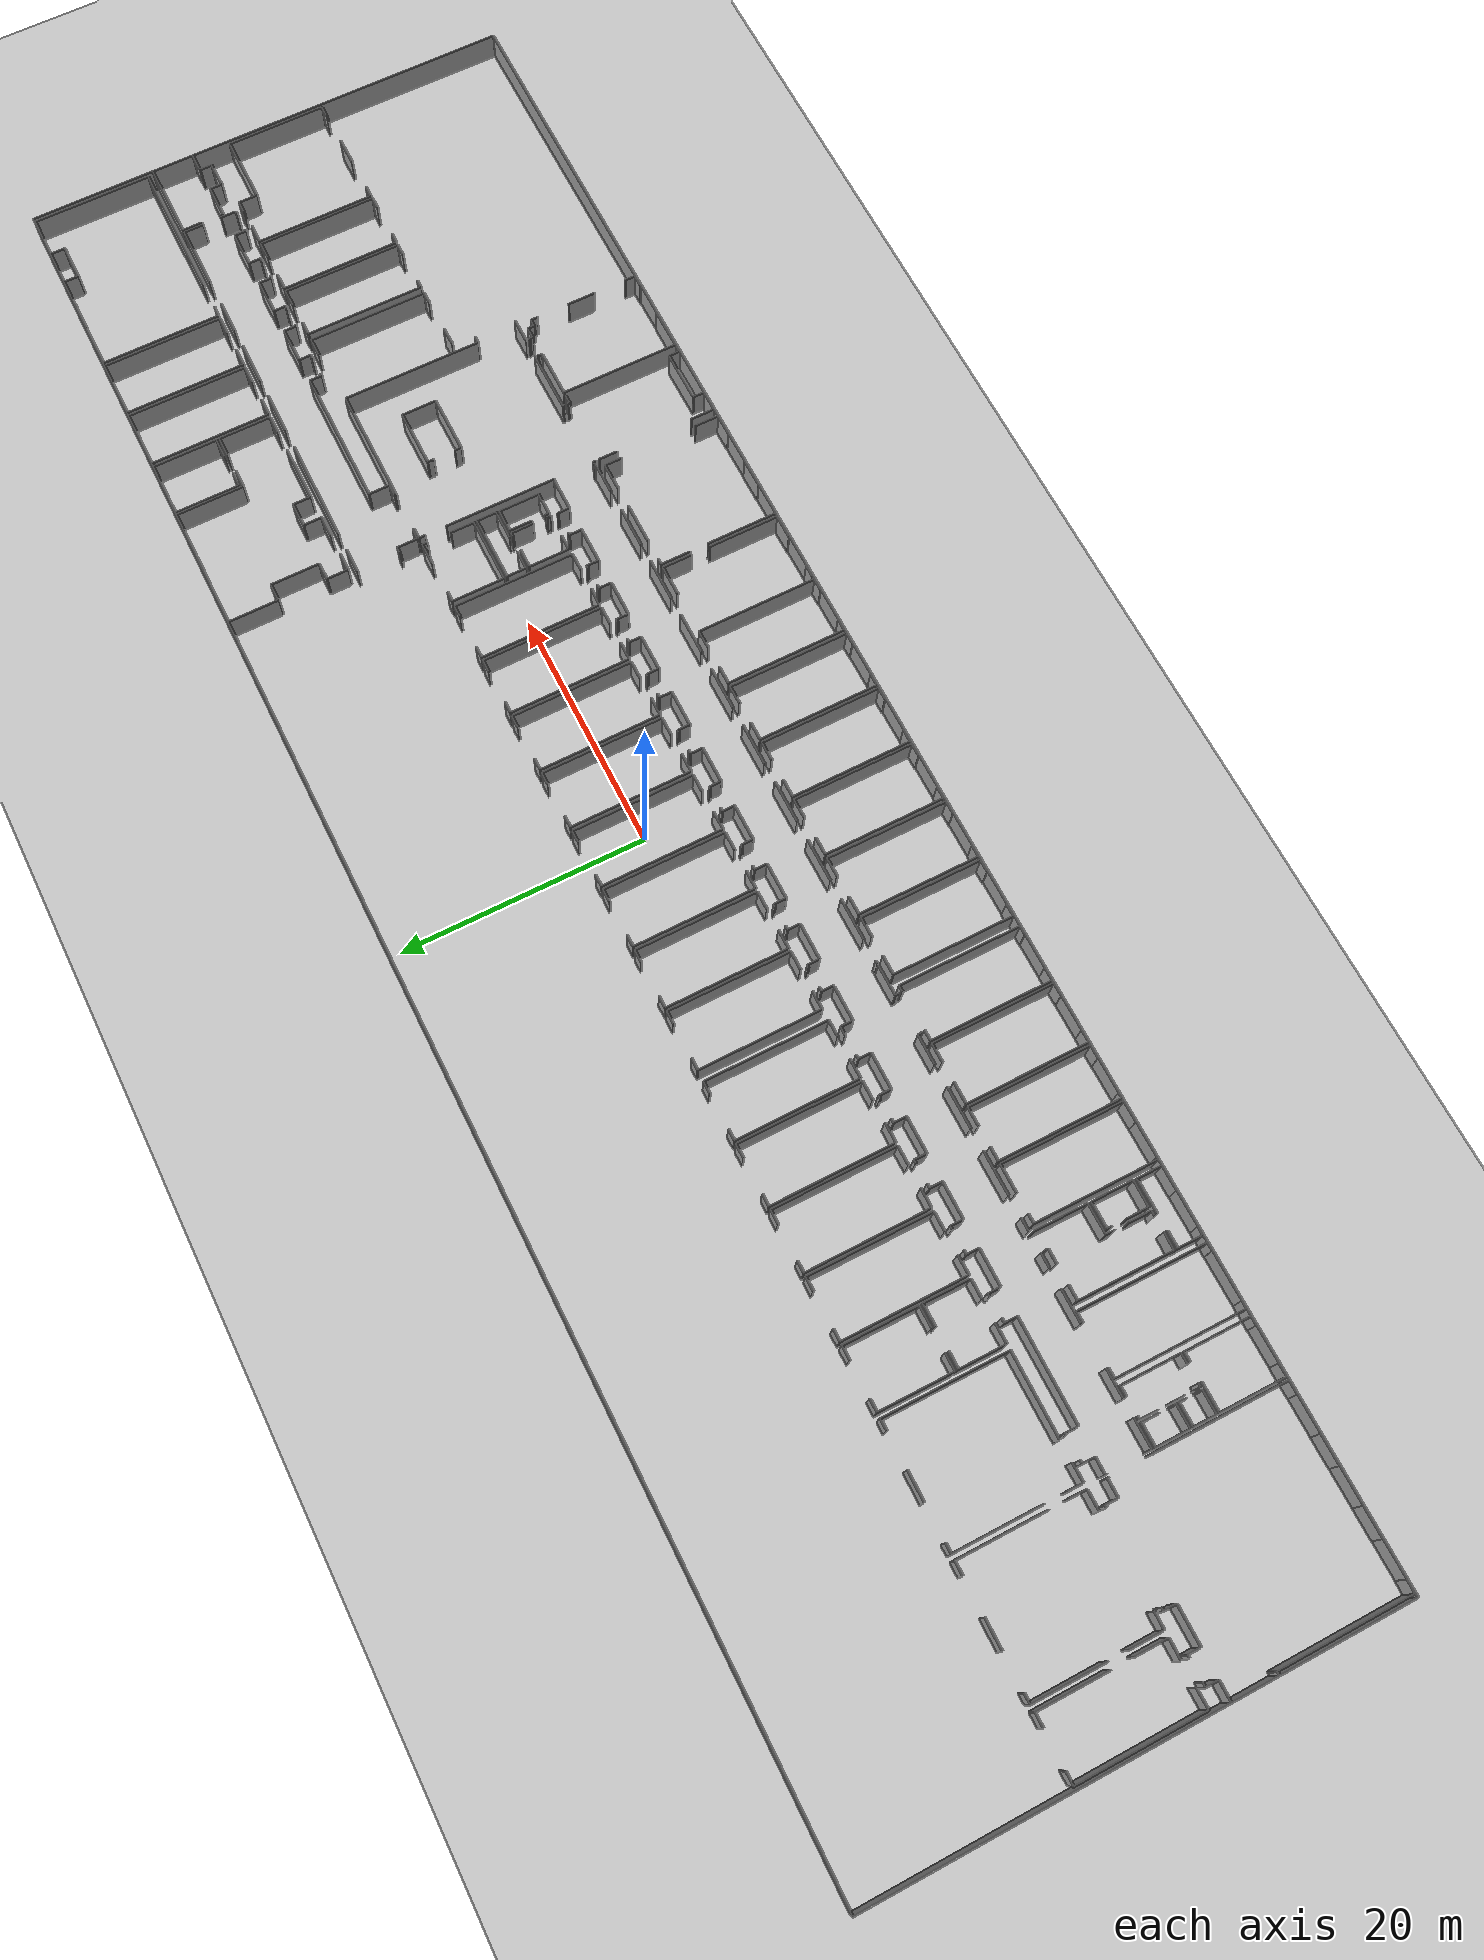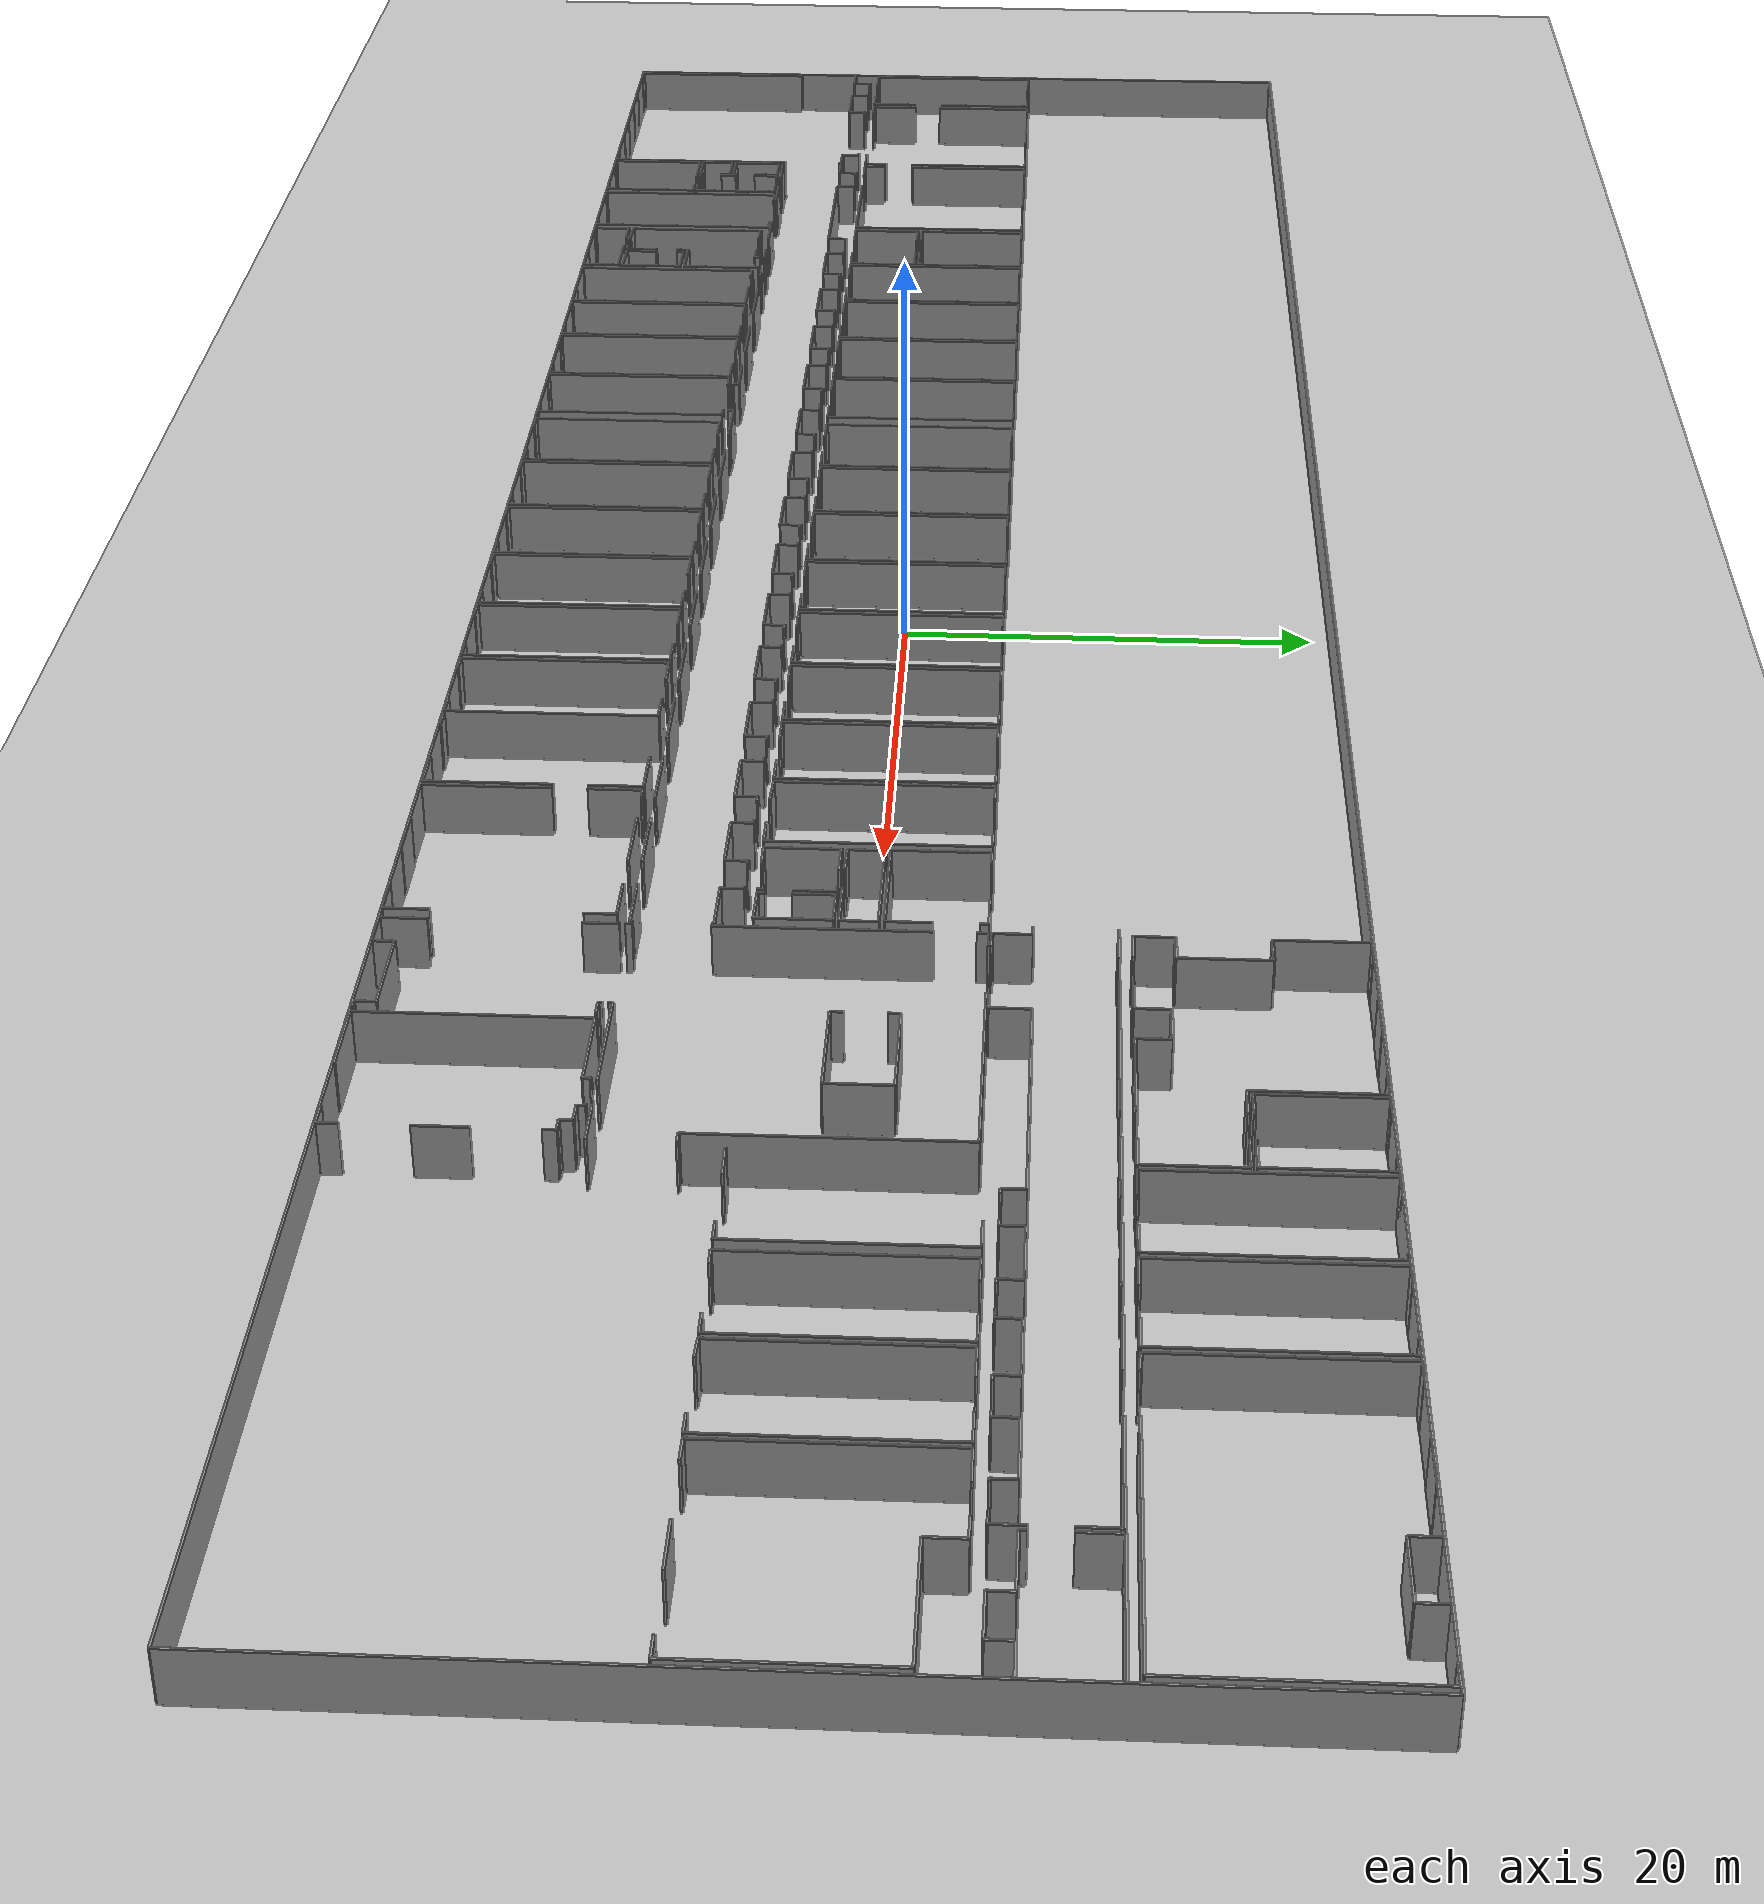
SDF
<sdf version="1.6">
  <world name="default">
    <light name="sun" type="directional">
      <cast_shadows>1</cast_shadows>
      <pose frame="">0 0 10 0 -0 0</pose>
      <diffuse>0.8 0.8 0.8 1</diffuse>
      <specular>0.1 0.1 0.1 1</specular>
      <attenuation>
        <range>1000</range>
        <constant>0.9</constant>
        <linear>0.01</linear>
        <quadratic>0.001</quadratic>
      </attenuation>
      <direction>-0.5 0.5 -1</direction>
    </light>
    <model name="ground_plane">
      <static>1</static>
      <link name="link">
        <collision name="collision">
          <geometry>
            <plane>
              <normal>0 0 1</normal>
              <size>100 100</size>
            </plane>
          </geometry>
          <surface>
            <friction>
              <ode>
                <mu>100</mu>
                <mu2>50</mu2>
              </ode>
              <torsional>
                <ode />
              </torsional>
            </friction>
            <contact>
              <ode />
            </contact>
            <bounce />
          </surface>
          <max_contacts>10</max_contacts>
        </collision>
        <visual name="visual">
          <cast_shadows>0</cast_shadows>
          <geometry>
            <plane>
              <normal>0 0 1</normal>
              <size>100 100</size>
            </plane>
          </geometry>
          <material>
            <script>
              <uri>file://media/materials/scripts/gazebo.material</uri>
              <name>Gazebo/Grey</name>
            </script>
          </material>
        </visual>
        <self_collide>0</self_collide>
        <kinematic>0</kinematic>
        <gravity>1</gravity>
      </link>
    </model>
    <gravity>0 0 -9.8</gravity>
    <magnetic_field>6e-06 2.3e-05 -4.2e-05</magnetic_field>
    <atmosphere type="adiabatic" />
    <physics default="0" name="default_physics" type="ode">
      <max_step_size>0.001</max_step_size>
      <real_time_factor>1</real_time_factor>
      <real_time_update_rate>1000</real_time_update_rate>
    </physics>
    <scene>
      <ambient>0.4 0.4 0.4 1</ambient>
      <background>0.7 0.7 0.7 1</background>
      <shadows>1</shadows>
    </scene>
    <spherical_coordinates>
      <surface_model>EARTH_WGS84</surface_model>
      <latitude_deg>0</latitude_deg>
      <longitude_deg>0</longitude_deg>
      <elevation>0</elevation>
      <heading_deg>0</heading_deg>
    </spherical_coordinates>
  <model name="50055639">
		<static>1</static>
		<link name="Wall_0">
			<collision name="Wall_0_Collision">
				<geometry>
					<box>
						<size>9.98781401135 0.1 2.5</size>
					</box>
				</geometry>
				<pose frame="">4.99390700567 0 1.25 0 0 0</pose>
			</collision>
			<visual name="Wall_0_Visual">
				<pose frame="">4.99390700567 0 1.25 0 0 0</pose>
				<geometry>
					<box>
						<size>9.98781401135 0.1 2.5</size>
					</box>
				</geometry>
				<material>
					<script>
						<uri>file://media/materials/scripts/gazebo.material</uri>
						<name>Gazebo/Grey</name>
					</script>
					<ambient>1 1 1 1</ambient>
				</material>
			</visual>
			<pose frame="">0.262633442923 -25.9998730626 0 0 0 1.57079632679</pose>
		</link>
		<link name="Wall_1">
			<collision name="Wall_1_Collision">
				<geometry>
					<box>
						<size>1.00940605999 0.1 2.5</size>
					</box>
				</geometry>
				<pose frame="">0.504703029995 0 1.25 0 0 0</pose>
			</collision>
			<visual name="Wall_1_Visual">
				<pose frame="">0.504703029995 0 1.25 0 0 0</pose>
				<geometry>
					<box>
						<size>1.00940605999 0.1 2.5</size>
					</box>
				</geometry>
				<material>
					<script>
						<uri>file://media/materials/scripts/gazebo.material</uri>
						<name>Gazebo/Grey</name>
					</script>
					<ambient>1 1 1 1</ambient>
				</material>
			</visual>
			<pose frame="">0.262633442923 -16.0120590513 0 0 0 0.0</pose>
		</link>
		<link name="Wall_2">
			<collision name="Wall_2_Collision">
				<geometry>
					<box>
						<size>1.06030795009 0.1 2.5</size>
					</box>
				</geometry>
				<pose frame="">0.530153975044 0 1.25 0 0 0</pose>
			</collision>
			<visual name="Wall_2_Visual">
				<pose frame="">0.530153975044 0 1.25 0 0 0</pose>
				<geometry>
					<box>
						<size>1.06030795009 0.1 2.5</size>
					</box>
				</geometry>
				<material>
					<script>
						<uri>file://media/materials/scripts/gazebo.material</uri>
						<name>Gazebo/Grey</name>
					</script>
					<ambient>1 1 1 1</ambient>
				</material>
			</visual>
			<pose frame="">4.08040213763 -16.0120590513 0 0 0 0.0</pose>
		</link>
		<link name="Wall_3">
			<collision name="Wall_3_Collision">
				<geometry>
					<box>
						<size>5.61393264703 0.1 2.5</size>
					</box>
				</geometry>
				<pose frame="">2.80696632351 0 1.25 0 0 0</pose>
			</collision>
			<visual name="Wall_3_Visual">
				<pose frame="">2.80696632351 0 1.25 0 0 0</pose>
				<geometry>
					<box>
						<size>5.61393264703 0.1 2.5</size>
					</box>
				</geometry>
				<material>
					<script>
						<uri>file://media/materials/scripts/gazebo.material</uri>
						<name>Gazebo/Grey</name>
					</script>
					<ambient>1 1 1 1</ambient>
				</material>
			</visual>
			<pose frame="">5.14071008771 -16.0120590513 0 0 0 -1.57079632679</pose>
		</link>
		<link name="Wall_4">
			<collision name="Wall_4_Collision">
				<geometry>
					<box>
						<size>2.58914177636 0.1 2.5</size>
					</box>
				</geometry>
				<pose frame="">1.29457088818 0 1.25 0 0 0</pose>
			</collision>
			<visual name="Wall_4_Visual">
				<pose frame="">1.29457088818 0 1.25 0 0 0</pose>
				<geometry>
					<box>
						<size>2.58914177636 0.1 2.5</size>
					</box>
				</geometry>
				<material>
					<script>
						<uri>file://media/materials/scripts/gazebo.material</uri>
						<name>Gazebo/Grey</name>
					</script>
					<ambient>1 1 1 1</ambient>
				</material>
			</visual>
			<pose frame="">5.14071008771 -23.3888980566 0 0 0 -1.57079632679</pose>
		</link>
		<link name="Wall_5">
			<collision name="Wall_5_Collision">
				<geometry>
					<box>
						<size>1.54927074474 0.1 2.5</size>
					</box>
				</geometry>
				<pose frame="">0.774635372371 0 1.25 0 0 0</pose>
			</collision>
			<visual name="Wall_5_Visual">
				<pose frame="">0.774635372371 0 1.25 0 0 0</pose>
				<geometry>
					<box>
						<size>1.54927074474 0.1 2.5</size>
					</box>
				</geometry>
				<material>
					<script>
						<uri>file://media/materials/scripts/gazebo.material</uri>
						<name>Gazebo/Grey</name>
					</script>
					<ambient>1 1 1 1</ambient>
				</material>
			</visual>
			<pose frame="">5.14071008771 -25.978039833 0 0 0 3.14159265359</pose>
		</link>
		<link name="Wall_6">
			<collision name="Wall_6_Collision">
				<geometry>
					<box>
						<size>1.54307834408 0.1 2.5</size>
					</box>
				</geometry>
				<pose frame="">0.771539172041 0 1.25 0 0 0</pose>
			</collision>
			<visual name="Wall_6_Visual">
				<pose frame="">0.771539172041 0 1.25 0 0 0</pose>
				<geometry>
					<box>
						<size>1.54307834408 0.1 2.5</size>
					</box>
				</geometry>
				<material>
					<script>
						<uri>file://media/materials/scripts/gazebo.material</uri>
						<name>Gazebo/Grey</name>
					</script>
					<ambient>1 1 1 1</ambient>
				</material>
			</visual>
			<pose frame="">1.80555731857 -25.978039833 0 0 0 -3.12744304264</pose>
		</link>
		<link name="Wall_7">
			<collision name="Wall_7_Collision">
				<geometry>
					<box>
						<size>2.6683507026 0.1 2.5</size>
					</box>
				</geometry>
				<pose frame="">1.3341753513 0 1.25 0 0 0</pose>
			</collision>
			<visual name="Wall_7_Visual">
				<pose frame="">1.3341753513 0 1.25 0 0 0</pose>
				<geometry>
					<box>
						<size>2.6683507026 0.1 2.5</size>
					</box>
				</geometry>
				<material>
					<script>
						<uri>file://media/materials/scripts/gazebo.material</uri>
						<name>Gazebo/Grey</name>
					</script>
					<ambient>1 1 1 1</ambient>
				</material>
			</visual>
			<pose frame="">5.66750022214 -25.9729623377 0 0 0 1.57079632679</pose>
		</link>
		<link name="Wall_8">
			<collision name="Wall_8_Collision">
				<geometry>
					<box>
						<size>5.76067226037 0.1 2.5</size>
					</box>
				</geometry>
				<pose frame="">2.88033613019 0 1.25 0 0 0</pose>
			</collision>
			<visual name="Wall_8_Visual">
				<pose frame="">2.88033613019 0 1.25 0 0 0</pose>
				<geometry>
					<box>
						<size>5.76067226037 0.1 2.5</size>
					</box>
				</geometry>
				<material>
					<script>
						<uri>file://media/materials/scripts/gazebo.material</uri>
						<name>Gazebo/Grey</name>
					</script>
					<ambient>1 1 1 1</ambient>
				</material>
			</visual>
			<pose frame="">5.66750022214 -21.7349039719 0 0 0 1.57079632679</pose>
		</link>
		<link name="Wall_9">
			<collision name="Wall_9_Collision">
				<geometry>
					<box>
						<size>0.77952246157 0.1 2.5</size>
					</box>
				</geometry>
				<pose frame="">0.389761230785 0 1.25 0 0 0</pose>
			</collision>
			<visual name="Wall_9_Visual">
				<pose frame="">0.389761230785 0 1.25 0 0 0</pose>
				<geometry>
					<box>
						<size>0.77952246157 0.1 2.5</size>
					</box>
				</geometry>
				<material>
					<script>
						<uri>file://media/materials/scripts/gazebo.material</uri>
						<name>Gazebo/Grey</name>
					</script>
					<ambient>1 1 1 1</ambient>
				</material>
			</visual>
			<pose frame="">5.66750022214 -15.9742317115 0 0 0 0.0</pose>
		</link>
		<link name="Wall_10">
			<collision name="Wall_10_Collision">
				<geometry>
					<box>
						<size>2.32866626893 0.1 2.5</size>
					</box>
				</geometry>
				<pose frame="">1.16433313446 0 1.25 0 0 0</pose>
			</collision>
			<visual name="Wall_10_Visual">
				<pose frame="">1.16433313446 0 1.25 0 0 0</pose>
				<geometry>
					<box>
						<size>2.32866626893 0.1 2.5</size>
					</box>
				</geometry>
				<material>
					<script>
						<uri>file://media/materials/scripts/gazebo.material</uri>
						<name>Gazebo/Grey</name>
					</script>
					<ambient>1 1 1 1</ambient>
				</material>
			</visual>
			<pose frame="">9.23659858592 -15.9742317115 0 0 0 0.0</pose>
		</link>
		<link name="Wall_11">
			<collision name="Wall_11_Collision">
				<geometry>
					<box>
						<size>1.08544155168 0.1 2.5</size>
					</box>
				</geometry>
				<pose frame="">0.542720775841 0 1.25 0 0 0</pose>
			</collision>
			<visual name="Wall_11_Visual">
				<pose frame="">0.542720775841 0 1.25 0 0 0</pose>
				<geometry>
					<box>
						<size>1.08544155168 0.1 2.5</size>
					</box>
				</geometry>
				<material>
					<script>
						<uri>file://media/materials/scripts/gazebo.material</uri>
						<name>Gazebo/Grey</name>
					</script>
					<ambient>1 1 1 1</ambient>
				</material>
			</visual>
			<pose frame="">14.3737544269 -15.9742317115 0 0 0 0.0</pose>
		</link>
		<link name="Wall_12">
			<collision name="Wall_12_Collision">
				<geometry>
					<box>
						<size>7.12512217723 0.1 2.5</size>
					</box>
				</geometry>
				<pose frame="">3.56256108861 0 1.25 0 0 0</pose>
			</collision>
			<visual name="Wall_12_Visual">
				<pose frame="">3.56256108861 0 1.25 0 0 0</pose>
				<geometry>
					<box>
						<size>7.12512217723 0.1 2.5</size>
					</box>
				</geometry>
				<material>
					<script>
						<uri>file://media/materials/scripts/gazebo.material</uri>
						<name>Gazebo/Grey</name>
					</script>
					<ambient>1 1 1 1</ambient>
				</material>
			</visual>
			<pose frame="">15.4591959786 -15.9742317115 0 0 0 -1.57079632679</pose>
		</link>
		<link name="Wall_13">
			<collision name="Wall_13_Collision">
				<geometry>
					<box>
						<size>1.31494433796 0.1 2.5</size>
					</box>
				</geometry>
				<pose frame="">0.657472168979 0 1.25 0 0 0</pose>
			</collision>
			<visual name="Wall_13_Visual">
				<pose frame="">0.657472168979 0 1.25 0 0 0</pose>
				<geometry>
					<box>
						<size>1.31494433796 0.1 2.5</size>
					</box>
				</geometry>
				<material>
					<script>
						<uri>file://media/materials/scripts/gazebo.material</uri>
						<name>Gazebo/Grey</name>
					</script>
					<ambient>1 1 1 1</ambient>
				</material>
			</visual>
			<pose frame="">15.4591959786 -24.6771855444 0 0 0 -1.57079632679</pose>
		</link>
		<link name="Wall_14">
			<collision name="Wall_14_Collision">
				<geometry>
					<box>
						<size>1.56602647914 0.1 2.5</size>
					</box>
				</geometry>
				<pose frame="">0.783013239569 0 1.25 0 0 0</pose>
			</collision>
			<visual name="Wall_14_Visual">
				<pose frame="">0.783013239569 0 1.25 0 0 0</pose>
				<geometry>
					<box>
						<size>1.56602647914 0.1 2.5</size>
					</box>
				</geometry>
				<material>
					<script>
						<uri>file://media/materials/scripts/gazebo.material</uri>
						<name>Gazebo/Grey</name>
					</script>
					<ambient>1 1 1 1</ambient>
				</material>
			</visual>
			<pose frame="">15.4591959786 -25.9921298823 0 0 0 3.14159265359</pose>
		</link>
		<link name="Wall_15">
			<collision name="Wall_15_Collision">
				<geometry>
					<box>
						<size>1.30010702863 0.1 2.5</size>
					</box>
				</geometry>
				<pose frame="">0.650053514316 0 1.25 0 0 0</pose>
			</collision>
			<visual name="Wall_15_Visual">
				<pose frame="">0.650053514316 0 1.25 0 0 0</pose>
				<geometry>
					<box>
						<size>1.30010702863 0.1 2.5</size>
					</box>
				</geometry>
				<material>
					<script>
						<uri>file://media/materials/scripts/gazebo.material</uri>
						<name>Gazebo/Grey</name>
					</script>
					<ambient>1 1 1 1</ambient>
				</material>
			</visual>
			<pose frame="">6.96746594905 -25.9921298823 0 0 0 3.12684906813</pose>
		</link>
		<link name="Wall_16">
			<collision name="Wall_16_Collision">
				<geometry>
					<box>
						<size>1.21859886518 0.1 2.5</size>
					</box>
				</geometry>
				<pose frame="">0.60929943259 0 1.25 0 0 0</pose>
			</collision>
			<visual name="Wall_16_Visual">
				<pose frame="">0.60929943259 0 1.25 0 0 0</pose>
				<geometry>
					<box>
						<size>1.21859886518 0.1 2.5</size>
					</box>
				</geometry>
				<material>
					<script>
						<uri>file://media/materials/scripts/gazebo.material</uri>
						<name>Gazebo/Grey</name>
					</script>
					<ambient>1 1 1 1</ambient>
				</material>
			</visual>
			<pose frame="">15.9090620597 -25.9954302543 0 0 0 1.57079632679</pose>
		</link>
		<link name="Wall_17">
			<collision name="Wall_17_Collision">
				<geometry>
					<box>
						<size>7.04108963049 0.1 2.5</size>
					</box>
				</geometry>
				<pose frame="">3.52054481524 0 1.25 0 0 0</pose>
			</collision>
			<visual name="Wall_17_Visual">
				<pose frame="">3.52054481524 0 1.25 0 0 0</pose>
				<geometry>
					<box>
						<size>7.04108963049 0.1 2.5</size>
					</box>
				</geometry>
				<material>
					<script>
						<uri>file://media/materials/scripts/gazebo.material</uri>
						<name>Gazebo/Grey</name>
					</script>
					<ambient>1 1 1 1</ambient>
				</material>
			</visual>
			<pose frame="">15.9090620597 -23.0216682111 0 0 0 1.57079632679</pose>
		</link>
		<link name="Wall_18">
			<collision name="Wall_18_Collision">
				<geometry>
					<box>
						<size>0.818619175161 0.1 2.5</size>
					</box>
				</geometry>
				<pose frame="">0.40930958758 0 1.25 0 0 0</pose>
			</collision>
			<visual name="Wall_18_Visual">
				<pose frame="">0.40930958758 0 1.25 0 0 0</pose>
				<geometry>
					<box>
						<size>0.818619175161 0.1 2.5</size>
					</box>
				</geometry>
				<material>
					<script>
						<uri>file://media/materials/scripts/gazebo.material</uri>
						<name>Gazebo/Grey</name>
					</script>
					<ambient>1 1 1 1</ambient>
				</material>
			</visual>
			<pose frame="">15.9090620597 -15.9805785806 0 0 0 0.0</pose>
		</link>
		<link name="Wall_19">
			<collision name="Wall_19_Collision">
				<geometry>
					<box>
						<size>2.36662054608 0.1 2.5</size>
					</box>
				</geometry>
				<pose frame="">1.18331027304 0 1.25 0 0 0</pose>
			</collision>
			<visual name="Wall_19_Visual">
				<pose frame="">1.18331027304 0 1.25 0 0 0</pose>
				<geometry>
					<box>
						<size>2.36662054608 0.1 2.5</size>
					</box>
				</geometry>
				<material>
					<script>
						<uri>file://media/materials/scripts/gazebo.material</uri>
						<name>Gazebo/Grey</name>
					</script>
					<ambient>1 1 1 1</ambient>
				</material>
			</visual>
			<pose frame="">19.510910268 -15.9805785806 0 0 0 0.0</pose>
		</link>
		<link name="Wall_20">
			<collision name="Wall_20_Collision">
				<geometry>
					<box>
						<size>0.902397847142 0.1 2.5</size>
					</box>
				</geometry>
				<pose frame="">0.451198923571 0 1.25 0 0 0</pose>
			</collision>
			<visual name="Wall_20_Visual">
				<pose frame="">0.451198923571 0 1.25 0 0 0</pose>
				<geometry>
					<box>
						<size>0.902397847142 0.1 2.5</size>
					</box>
				</geometry>
				<material>
					<script>
						<uri>file://media/materials/scripts/gazebo.material</uri>
						<name>Gazebo/Grey</name>
					</script>
					<ambient>1 1 1 1</ambient>
				</material>
			</visual>
			<pose frame="">24.6544129781 -15.9805785806 0 0 0 0.0</pose>
		</link>
		<link name="Wall_21">
			<collision name="Wall_21_Collision">
				<geometry>
					<box>
						<size>10.0073623681 0.1 2.5</size>
					</box>
				</geometry>
				<pose frame="">5.00368118407 0 1.25 0 0 0</pose>
			</collision>
			<visual name="Wall_21_Visual">
				<pose frame="">5.00368118407 0 1.25 0 0 0</pose>
				<geometry>
					<box>
						<size>10.0073623681 0.1 2.5</size>
					</box>
				</geometry>
				<material>
					<script>
						<uri>file://media/materials/scripts/gazebo.material</uri>
						<name>Gazebo/Grey</name>
					</script>
					<ambient>1 1 1 1</ambient>
				</material>
			</visual>
			<pose frame="">25.5568108252 -15.9805785806 0 0 0 -1.57079632679</pose>
		</link>
		<link name="Wall_22">
			<collision name="Wall_22_Collision">
				<geometry>
					<box>
						<size>6.57789512434 0.1 2.5</size>
					</box>
				</geometry>
				<pose frame="">3.28894756217 0 1.25 0 0 0</pose>
			</collision>
			<visual name="Wall_22_Visual">
				<pose frame="">3.28894756217 0 1.25 0 0 0</pose>
				<geometry>
					<box>
						<size>6.57789512434 0.1 2.5</size>
					</box>
				</geometry>
				<material>
					<script>
						<uri>file://media/materials/scripts/gazebo.material</uri>
						<name>Gazebo/Grey</name>
					</script>
					<ambient>1 1 1 1</ambient>
				</material>
			</visual>
			<pose frame="">25.5568108252 -25.9879409487 0 0 0 3.14159265359</pose>
		</link>
		<link name="Wall_23">
			<collision name="Wall_23_Collision">
				<geometry>
					<box>
						<size>1.48442463551 0.1 2.5</size>
					</box>
				</geometry>
				<pose frame="">0.742212317754 0 1.25 0 0 0</pose>
			</collision>
			<visual name="Wall_23_Visual">
				<pose frame="">0.742212317754 0 1.25 0 0 0</pose>
				<geometry>
					<box>
						<size>1.48442463551 0.1 2.5</size>
					</box>
				</geometry>
				<material>
					<script>
						<uri>file://media/materials/scripts/gazebo.material</uri>
						<name>Gazebo/Grey</name>
					</script>
					<ambient>1 1 1 1</ambient>
				</material>
			</visual>
			<pose frame="">17.3934678023 -25.9879409487 0 0 0 -3.13654737401</pose>
		</link>
		<link name="Wall_24">
			<collision name="Wall_24_Collision">
				<geometry>
					<box>
						<size>10.5526853603 0.1 2.5</size>
					</box>
				</geometry>
				<pose frame="">5.27634268016 0 1.25 0 0 0</pose>
			</collision>
			<visual name="Wall_24_Visual">
				<pose frame="">5.27634268016 0 1.25 0 0 0</pose>
				<geometry>
					<box>
						<size>10.5526853603 0.1 2.5</size>
					</box>
				</geometry>
				<material>
					<script>
						<uri>file://media/materials/scripts/gazebo.material</uri>
						<name>Gazebo/Grey</name>
					</script>
					<ambient>1 1 1 1</ambient>
				</material>
			</visual>
			<pose frame="">0.276850429683 -41.7007578162 0 0 0 1.57079632679</pose>
		</link>
		<link name="Wall_25">
			<collision name="Wall_25_Collision">
				<geometry>
					<box>
						<size>0.276850429683 0.1 2.5</size>
					</box>
				</geometry>
				<pose frame="">0.138425214842 0 1.25 0 0 0</pose>
			</collision>
			<visual name="Wall_25_Visual">
				<pose frame="">0.138425214842 0 1.25 0 0 0</pose>
				<geometry>
					<box>
						<size>0.276850429683 0.1 2.5</size>
					</box>
				</geometry>
				<material>
					<script>
						<uri>file://media/materials/scripts/gazebo.material</uri>
						<name>Gazebo/Grey</name>
					</script>
					<ambient>1 1 1 1</ambient>
				</material>
			</visual>
			<pose frame="">0.276850429683 -31.1480724559 0 0 0 3.14159265359</pose>
		</link>
		<link name="Wall_26">
			<collision name="Wall_26_Collision">
				<geometry>
					<box>
						<size>1.52248695718 0.1 2.5</size>
					</box>
				</geometry>
				<pose frame="">0.761243478592 0 1.25 0 0 0</pose>
			</collision>
			<visual name="Wall_26_Visual">
				<pose frame="">0.761243478592 0 1.25 0 0 0</pose>
				<geometry>
					<box>
						<size>1.52248695718 0.1 2.5</size>
					</box>
				</geometry>
				<material>
					<script>
						<uri>file://media/materials/scripts/gazebo.material</uri>
						<name>Gazebo/Grey</name>
					</script>
					<ambient>1 1 1 1</ambient>
				</material>
			</visual>
			<pose frame="">0.0 -27.5255334543 0 0 0 0.0</pose>
		</link>
		<link name="Wall_27">
			<collision name="Wall_27_Collision">
				<geometry>
					<box>
						<size>0.987699767705 0.1 2.5</size>
					</box>
				</geometry>
				<pose frame="">0.493849883852 0 1.25 0 0 0</pose>
			</collision>
			<visual name="Wall_27_Visual">
				<pose frame="">0.493849883852 0 1.25 0 0 0</pose>
				<geometry>
					<box>
						<size>0.987699767705 0.1 2.5</size>
					</box>
				</geometry>
				<material>
					<script>
						<uri>file://media/materials/scripts/gazebo.material</uri>
						<name>Gazebo/Grey</name>
					</script>
					<ambient>1 1 1 1</ambient>
				</material>
			</visual>
			<pose frame="">1.52248695718 -27.5255334543 0 0 0 1.57079632679</pose>
		</link>
		<link name="Wall_28">
			<collision name="Wall_28_Collision">
				<geometry>
					<box>
						<size>0.362279287627 0.1 2.5</size>
					</box>
				</geometry>
				<pose frame="">0.181139643814 0 1.25 0 0 0</pose>
			</collision>
			<visual name="Wall_28_Visual">
				<pose frame="">0.181139643814 0 1.25 0 0 0</pose>
				<geometry>
					<box>
						<size>0.362279287627 0.1 2.5</size>
					</box>
				</geometry>
				<material>
					<script>
						<uri>file://media/materials/scripts/gazebo.material</uri>
						<name>Gazebo/Grey</name>
					</script>
					<ambient>1 1 1 1</ambient>
				</material>
			</visual>
			<pose frame="">1.52248695718 -26.5378336866 0 0 0 0.0</pose>
		</link>
		<link name="Wall_29">
			<collision name="Wall_29_Collision">
				<geometry>
					<box>
						<size>0.256286573833 0.1 2.5</size>
					</box>
				</geometry>
				<pose frame="">0.128143286917 0 1.25 0 0 0</pose>
			</collision>
			<visual name="Wall_29_Visual">
				<pose frame="">0.128143286917 0 1.25 0 0 0</pose>
				<geometry>
					<box>
						<size>0.256286573833 0.1 2.5</size>
					</box>
				</geometry>
				<material>
					<script>
						<uri>file://media/materials/scripts/gazebo.material</uri>
						<name>Gazebo/Grey</name>
					</script>
					<ambient>1 1 1 1</ambient>
				</material>
			</visual>
			<pose frame="">3.46196321355 -26.5378336866 0 0 0 0.0</pose>
		</link>
		<link name="Wall_30">
			<collision name="Wall_30_Collision">
				<geometry>
					<box>
						<size>1.0044555021 0.1 2.5</size>
					</box>
				</geometry>
				<pose frame="">0.50222775105 0 1.25 0 0 0</pose>
			</collision>
			<visual name="Wall_30_Visual">
				<pose frame="">0.50222775105 0 1.25 0 0 0</pose>
				<geometry>
					<box>
						<size>1.0044555021 0.1 2.5</size>
					</box>
				</geometry>
				<material>
					<script>
						<uri>file://media/materials/scripts/gazebo.material</uri>
						<name>Gazebo/Grey</name>
					</script>
					<ambient>1 1 1 1</ambient>
				</material>
			</visual>
			<pose frame="">3.71824978738 -26.5378336866 0 0 0 -1.57079632679</pose>
		</link>
		<link name="Wall_31">
			<collision name="Wall_31_Collision">
				<geometry>
					<box>
						<size>2.96868454791 0.1 2.5</size>
					</box>
				</geometry>
				<pose frame="">1.48434227396 0 1.25 0 0 0</pose>
			</collision>
			<visual name="Wall_31_Visual">
				<pose frame="">1.48434227396 0 1.25 0 0 0</pose>
				<geometry>
					<box>
						<size>2.96868454791 0.1 2.5</size>
					</box>
				</geometry>
				<material>
					<script>
						<uri>file://media/materials/scripts/gazebo.material</uri>
						<name>Gazebo/Grey</name>
					</script>
					<ambient>1 1 1 1</ambient>
				</material>
			</visual>
			<pose frame="">3.71824978738 -27.5422891887 0 0 0 0.0</pose>
		</link>
		<link name="Wall_32">
			<collision name="Wall_32_Collision">
				<geometry>
					<box>
						<size>1.00344000305 0.1 2.5</size>
					</box>
				</geometry>
				<pose frame="">0.501720001523 0 1.25 0 0 0</pose>
			</collision>
			<visual name="Wall_32_Visual">
				<pose frame="">0.501720001523 0 1.25 0 0 0</pose>
				<geometry>
					<box>
						<size>1.00344000305 0.1 2.5</size>
					</box>
				</geometry>
				<material>
					<script>
						<uri>file://media/materials/scripts/gazebo.material</uri>
						<name>Gazebo/Grey</name>
					</script>
					<ambient>1 1 1 1</ambient>
				</material>
			</visual>
			<pose frame="">6.68693433529 -27.5422891887 0 0 0 1.57079632679</pose>
		</link>
		<link name="Wall_33">
			<collision name="Wall_33_Collision">
				<geometry>
					<box>
						<size>0.258698384087 0.1 2.5</size>
					</box>
				</geometry>
				<pose frame="">0.129349192044 0 1.25 0 0 0</pose>
			</collision>
			<visual name="Wall_33_Visual">
				<pose frame="">0.129349192044 0 1.25 0 0 0</pose>
				<geometry>
					<box>
						<size>0.258698384087 0.1 2.5</size>
					</box>
				</geometry>
				<material>
					<script>
						<uri>file://media/materials/scripts/gazebo.material</uri>
						<name>Gazebo/Grey</name>
					</script>
					<ambient>1 1 1 1</ambient>
				</material>
			</visual>
			<pose frame="">6.68693433529 -26.5388491857 0 0 0 0.0</pose>
		</link>
		<link name="Wall_34">
			<collision name="Wall_34_Collision">
				<geometry>
					<box>
						<size>0.189263636248 0.1 2.5</size>
					</box>
				</geometry>
				<pose frame="">0.0946318181241 0 1.25 0 0 0</pose>
			</collision>
			<visual name="Wall_34_Visual">
				<pose frame="">0.0946318181241 0 1.25 0 0 0</pose>
				<geometry>
					<box>
						<size>0.189263636248 0.1 2.5</size>
					</box>
				</geometry>
				<material>
					<script>
						<uri>file://media/materials/scripts/gazebo.material</uri>
						<name>Gazebo/Grey</name>
					</script>
					<ambient>1 1 1 1</ambient>
				</material>
			</visual>
			<pose frame="">13.8625775905 -26.5388491857 0 0 0 0.0</pose>
		</link>
		<link name="Wall_35">
			<collision name="Wall_35_Collision">
				<geometry>
					<box>
						<size>1.00826362355 0.1 2.5</size>
					</box>
				</geometry>
				<pose frame="">0.504131811777 0 1.25 0 0 0</pose>
			</collision>
			<visual name="Wall_35_Visual">
				<pose frame="">0.504131811777 0 1.25 0 0 0</pose>
				<geometry>
					<box>
						<size>1.00826362355 0.1 2.5</size>
					</box>
				</geometry>
				<material>
					<script>
						<uri>file://media/materials/scripts/gazebo.material</uri>
						<name>Gazebo/Grey</name>
					</script>
					<ambient>1 1 1 1</ambient>
				</material>
			</visual>
			<pose frame="">14.0518412267 -26.5388491857 0 0 0 -1.57079632679</pose>
		</link>
		<link name="Wall_36">
			<collision name="Wall_36_Collision">
				<geometry>
					<box>
						<size>1.40430825474 0.1 2.5</size>
					</box>
				</geometry>
				<pose frame="">0.702154127369 0 1.25 0 0 0</pose>
			</collision>
			<visual name="Wall_36_Visual">
				<pose frame="">0.702154127369 0 1.25 0 0 0</pose>
				<geometry>
					<box>
						<size>1.40430825474 0.1 2.5</size>
					</box>
				</geometry>
				<material>
					<script>
						<uri>file://media/materials/scripts/gazebo.material</uri>
						<name>Gazebo/Grey</name>
					</script>
					<ambient>1 1 1 1</ambient>
				</material>
			</visual>
			<pose frame="">14.0518412267 -27.5471128093 0 0 0 0.0</pose>
		</link>
		<link name="Wall_37">
			<collision name="Wall_37_Collision">
				<geometry>
					<box>
						<size>0.126683507026 0.1 2.5</size>
					</box>
				</geometry>
				<pose frame="">0.063341753513 0 1.25 0 0 0</pose>
			</collision>
			<visual name="Wall_37_Visual">
				<pose frame="">0.063341753513 0 1.25 0 0 0</pose>
				<geometry>
					<box>
						<size>0.126683507026 0.1 2.5</size>
					</box>
				</geometry>
				<material>
					<script>
						<uri>file://media/materials/scripts/gazebo.material</uri>
						<name>Gazebo/Grey</name>
					</script>
					<ambient>1 1 1 1</ambient>
				</material>
			</visual>
			<pose frame="">15.4561494815 -27.5471128093 0 0 0 -1.57079632679</pose>
		</link>
		<link name="Wall_38">
			<collision name="Wall_38_Collision">
				<geometry>
					<box>
						<size>10.6836847383 0.1 2.5</size>
					</box>
				</geometry>
				<pose frame="">5.34184236916 0 1.25 0 0 0</pose>
			</collision>
			<visual name="Wall_38_Visual">
				<pose frame="">5.34184236916 0 1.25 0 0 0</pose>
				<geometry>
					<box>
						<size>10.6836847383 0.1 2.5</size>
					</box>
				</geometry>
				<material>
					<script>
						<uri>file://media/materials/scripts/gazebo.material</uri>
						<name>Gazebo/Grey</name>
					</script>
					<ambient>1 1 1 1</ambient>
				</material>
			</visual>
			<pose frame="">15.4561494815 -31.0504576093 0 0 0 -1.57079632679</pose>
		</link>
		<link name="Wall_39">
			<collision name="Wall_39_Collision">
				<geometry>
					<box>
						<size>1.03250866348 0.1 2.5</size>
					</box>
				</geometry>
				<pose frame="">0.516254331738 0 1.25 0 0 0</pose>
			</collision>
			<visual name="Wall_39_Visual">
				<pose frame="">0.516254331738 0 1.25 0 0 0</pose>
				<geometry>
					<box>
						<size>1.03250866348 0.1 2.5</size>
					</box>
				</geometry>
				<material>
					<script>
						<uri>file://media/materials/scripts/gazebo.material</uri>
						<name>Gazebo/Grey</name>
					</script>
					<ambient>1 1 1 1</ambient>
				</material>
			</visual>
			<pose frame="">15.4561494815 -41.7341423476 0 0 0 3.14159265359</pose>
		</link>
		<link name="Wall_40">
			<collision name="Wall_40_Collision">
				<geometry>
					<box>
						<size>2.31191053453 0.1 2.5</size>
					</box>
				</geometry>
				<pose frame="">1.15595526727 0 1.25 0 0 0</pose>
			</collision>
			<visual name="Wall_40_Visual">
				<pose frame="">1.15595526727 0 1.25 0 0 0</pose>
				<geometry>
					<box>
						<size>2.31191053453 0.1 2.5</size>
					</box>
				</geometry>
				<material>
					<script>
						<uri>file://media/materials/scripts/gazebo.material</uri>
						<name>Gazebo/Grey</name>
					</script>
					<ambient>1 1 1 1</ambient>
				</material>
			</visual>
			<pose frame="">11.5858287107 -41.7341423476 0 0 0 3.14159265359</pose>
		</link>
		<link name="Wall_41">
			<collision name="Wall_41_Collision">
				<geometry>
					<box>
						<size>2.34529506594 0.1 2.5</size>
					</box>
				</geometry>
				<pose frame="">1.17264753297 0 1.25 0 0 0</pose>
			</collision>
			<visual name="Wall_41_Visual">
				<pose frame="">1.17264753297 0 1.25 0 0 0</pose>
				<geometry>
					<box>
						<size>2.34529506594 0.1 2.5</size>
					</box>
				</geometry>
				<material>
					<script>
						<uri>file://media/materials/scripts/gazebo.material</uri>
						<name>Gazebo/Grey</name>
					</script>
					<ambient>1 1 1 1</ambient>
				</material>
			</visual>
			<pose frame="">6.44448393607 -41.7341423476 0 0 0 3.14159265359</pose>
		</link>
		<link name="Wall_42">
			<collision name="Wall_42_Collision">
				<geometry>
					<box>
						<size>1.02683157718 0.1 2.5</size>
					</box>
				</geometry>
				<pose frame="">0.51341578859 0 1.25 0 0 0</pose>
			</collision>
			<visual name="Wall_42_Visual">
				<pose frame="">0.51341578859 0 1.25 0 0 0</pose>
				<geometry>
					<box>
						<size>1.02683157718 0.1 2.5</size>
					</box>
				</geometry>
				<material>
					<script>
						<uri>file://media/materials/scripts/gazebo.material</uri>
						<name>Gazebo/Grey</name>
					</script>
					<ambient>1 1 1 1</ambient>
				</material>
			</visual>
			<pose frame="">1.30313916145 -41.7341423476 0 0 0 3.10907474469</pose>
		</link>
		<link name="Wall_43">
			<collision name="Wall_43_Collision">
				<geometry>
					<box>
						<size>0.120717450082 0.1 2.5</size>
					</box>
				</geometry>
				<pose frame="">0.0603587250409 0 1.25 0 0 0</pose>
			</collision>
			<visual name="Wall_43_Visual">
				<pose frame="">0.0603587250409 0 1.25 0 0 0</pose>
				<geometry>
					<box>
						<size>0.120717450082 0.1 2.5</size>
					</box>
				</geometry>
				<material>
					<script>
						<uri>file://media/materials/scripts/gazebo.material</uri>
						<name>Gazebo/Grey</name>
					</script>
					<ambient>1 1 1 1</ambient>
				</material>
			</visual>
			<pose frame="">15.7196714861 -31.164066566 0 0 0 1.57079632679</pose>
		</link>
		<link name="Wall_44">
			<collision name="Wall_44_Collision">
				<geometry>
					<box>
						<size>0.154228918874 0.1 2.5</size>
					</box>
				</geometry>
				<pose frame="">0.0771144594372 0 1.25 0 0 0</pose>
			</collision>
			<visual name="Wall_44_Visual">
				<pose frame="">0.0771144594372 0 1.25 0 0 0</pose>
				<geometry>
					<box>
						<size>0.154228918874 0.1 2.5</size>
					</box>
				</geometry>
				<material>
					<script>
						<uri>file://media/materials/scripts/gazebo.material</uri>
						<name>Gazebo/Grey</name>
					</script>
					<ambient>1 1 1 1</ambient>
				</material>
			</visual>
			<pose frame="">15.7196714861 -27.6776044377 0 0 0 1.57079632679</pose>
		</link>
		<link name="Wall_45">
			<collision name="Wall_45_Collision">
				<geometry>
					<box>
						<size>1.27940187106 0.1 2.5</size>
					</box>
				</geometry>
				<pose frame="">0.639700935529 0 1.25 0 0 0</pose>
			</collision>
			<visual name="Wall_45_Visual">
				<pose frame="">0.639700935529 0 1.25 0 0 0</pose>
				<geometry>
					<box>
						<size>1.27940187106 0.1 2.5</size>
					</box>
				</geometry>
				<material>
					<script>
						<uri>file://media/materials/scripts/gazebo.material</uri>
						<name>Gazebo/Grey</name>
					</script>
					<ambient>1 1 1 1</ambient>
				</material>
			</visual>
			<pose frame="">15.7196714861 -27.5233755189 0 0 0 0.0</pose>
		</link>
		<link name="Wall_46">
			<collision name="Wall_46_Collision">
				<geometry>
					<box>
						<size>1.00978687214 0.1 2.5</size>
					</box>
				</geometry>
				<pose frame="">0.504893436068 0 1.25 0 0 0</pose>
			</collision>
			<visual name="Wall_46_Visual">
				<pose frame="">0.504893436068 0 1.25 0 0 0</pose>
				<geometry>
					<box>
						<size>1.00978687214 0.1 2.5</size>
					</box>
				</geometry>
				<material>
					<script>
						<uri>file://media/materials/scripts/gazebo.material</uri>
						<name>Gazebo/Grey</name>
					</script>
					<ambient>1 1 1 1</ambient>
				</material>
			</visual>
			<pose frame="">16.9990733571 -27.5233755189 0 0 0 1.57079632679</pose>
		</link>
		<link name="Wall_47">
			<collision name="Wall_47_Collision">
				<geometry>
					<box>
						<size>0.284085860445 0.1 2.5</size>
					</box>
				</geometry>
				<pose frame="">0.142042930223 0 1.25 0 0 0</pose>
			</collision>
			<visual name="Wall_47_Visual">
				<pose frame="">0.142042930223 0 1.25 0 0 0</pose>
				<geometry>
					<box>
						<size>0.284085860445 0.1 2.5</size>
					</box>
				</geometry>
				<material>
					<script>
						<uri>file://media/materials/scripts/gazebo.material</uri>
						<name>Gazebo/Grey</name>
					</script>
					<ambient>1 1 1 1</ambient>
				</material>
			</visual>
			<pose frame="">16.9990733571 -26.5135886467 0 0 0 0.0</pose>
		</link>
		<link name="Wall_48">
			<collision name="Wall_48_Collision">
				<geometry>
					<box>
						<size>0.165653283235 0.1 2.5</size>
					</box>
				</geometry>
				<pose frame="">0.0828266416177 0 1.25 0 0 0</pose>
			</collision>
			<visual name="Wall_48_Visual">
				<pose frame="">0.0828266416177 0 1.25 0 0 0</pose>
				<geometry>
					<box>
						<size>0.165653283235 0.1 2.5</size>
					</box>
				</geometry>
				<material>
					<script>
						<uri>file://media/materials/scripts/gazebo.material</uri>
						<name>Gazebo/Grey</name>
					</script>
					<ambient>1 1 1 1</ambient>
				</material>
			</visual>
			<pose frame="">19.0383223956 -26.5135886467 0 0 0 0.0</pose>
		</link>
		<link name="Wall_49">
			<collision name="Wall_49_Collision">
				<geometry>
					<box>
						<size>1.0316201018 0.1 2.5</size>
					</box>
				</geometry>
				<pose frame="">0.515810050902 0 1.25 0 0 0</pose>
			</collision>
			<visual name="Wall_49_Visual">
				<pose frame="">0.515810050902 0 1.25 0 0 0</pose>
				<geometry>
					<box>
						<size>1.0316201018 0.1 2.5</size>
					</box>
				</geometry>
				<material>
					<script>
						<uri>file://media/materials/scripts/gazebo.material</uri>
						<name>Gazebo/Grey</name>
					</script>
					<ambient>1 1 1 1</ambient>
				</material>
			</visual>
			<pose frame="">19.2039756788 -26.5135886467 0 0 0 -1.57079632679</pose>
		</link>
		<link name="Wall_50">
			<collision name="Wall_50_Collision">
				<geometry>
					<box>
						<size>8.1019053301 0.1 2.5</size>
					</box>
				</geometry>
				<pose frame="">4.05095266505 0 1.25 0 0 0</pose>
			</collision>
			<visual name="Wall_50_Visual">
				<pose frame="">4.05095266505 0 1.25 0 0 0</pose>
				<geometry>
					<box>
						<size>8.1019053301 0.1 2.5</size>
					</box>
				</geometry>
				<material>
					<script>
						<uri>file://media/materials/scripts/gazebo.material</uri>
						<name>Gazebo/Grey</name>
					</script>
					<ambient>1 1 1 1</ambient>
				</material>
			</visual>
			<pose frame="">19.2039756788 -27.5452087485 0 0 0 0.0</pose>
		</link>
		<link name="Wall_51">
			<collision name="Wall_51_Collision">
				<geometry>
					<box>
						<size>1.01549905432 0.1 2.5</size>
					</box>
				</geometry>
				<pose frame="">0.507749527158 0 1.25 0 0 0</pose>
			</collision>
			<visual name="Wall_51_Visual">
				<pose frame="">0.507749527158 0 1.25 0 0 0</pose>
				<geometry>
					<box>
						<size>1.01549905432 0.1 2.5</size>
					</box>
				</geometry>
				<material>
					<script>
						<uri>file://media/materials/scripts/gazebo.material</uri>
						<name>Gazebo/Grey</name>
					</script>
					<ambient>1 1 1 1</ambient>
				</material>
			</visual>
			<pose frame="">27.3058810089 -27.5452087485 0 0 0 1.57079632679</pose>
		</link>
		<link name="Wall_52">
			<collision name="Wall_52_Collision">
				<geometry>
					<box>
						<size>0.37522690057 0.1 2.5</size>
					</box>
				</geometry>
				<pose frame="">0.187613450285 0 1.25 0 0 0</pose>
			</collision>
			<visual name="Wall_52_Visual">
				<pose frame="">0.187613450285 0 1.25 0 0 0</pose>
				<geometry>
					<box>
						<size>0.37522690057 0.1 2.5</size>
					</box>
				</geometry>
				<material>
					<script>
						<uri>file://media/materials/scripts/gazebo.material</uri>
						<name>Gazebo/Grey</name>
					</script>
					<ambient>1 1 1 1</ambient>
				</material>
			</visual>
			<pose frame="">27.3058810089 -26.5297096942 0 0 0 0.0</pose>
		</link>
		<link name="Wall_53">
			<collision name="Wall_53_Collision">
				<geometry>
					<box>
						<size>0.268726437249 0.1 2.5</size>
					</box>
				</geometry>
				<pose frame="">0.134363218624 0 1.25 0 0 0</pose>
			</collision>
			<visual name="Wall_53_Visual">
				<pose frame="">0.134363218624 0 1.25 0 0 0</pose>
				<geometry>
					<box>
						<size>0.268726437249 0.1 2.5</size>
					</box>
				</geometry>
				<material>
					<script>
						<uri>file://media/materials/scripts/gazebo.material</uri>
						<name>Gazebo/Grey</name>
					</script>
					<ambient>1 1 1 1</ambient>
				</material>
			</visual>
			<pose frame="">29.2600820015 -26.5297096942 0 0 0 0.0</pose>
		</link>
		<link name="Wall_54">
			<collision name="Wall_54_Collision">
				<geometry>
					<box>
						<size>0.988588329377 0.1 2.5</size>
					</box>
				</geometry>
				<pose frame="">0.494294164689 0 1.25 0 0 0</pose>
			</collision>
			<visual name="Wall_54_Visual">
				<pose frame="">0.494294164689 0 1.25 0 0 0</pose>
				<geometry>
					<box>
						<size>0.988588329377 0.1 2.5</size>
					</box>
				</geometry>
				<material>
					<script>
						<uri>file://media/materials/scripts/gazebo.material</uri>
						<name>Gazebo/Grey</name>
					</script>
					<ambient>1 1 1 1</ambient>
				</material>
			</visual>
			<pose frame="">29.5288084388 -26.5297096942 0 0 0 -1.57079632679</pose>
		</link>
		<link name="Wall_55">
			<collision name="Wall_55_Collision">
				<geometry>
					<box>
						<size>2.96589192551 0.1 2.5</size>
					</box>
				</geometry>
				<pose frame="">1.48294596276 0 1.25 0 0 0</pose>
			</collision>
			<visual name="Wall_55_Visual">
				<pose frame="">1.48294596276 0 1.25 0 0 0</pose>
				<geometry>
					<box>
						<size>2.96589192551 0.1 2.5</size>
					</box>
				</geometry>
				<material>
					<script>
						<uri>file://media/materials/scripts/gazebo.material</uri>
						<name>Gazebo/Grey</name>
					</script>
					<ambient>1 1 1 1</ambient>
				</material>
			</visual>
			<pose frame="">29.5288084388 -27.5182980236 0 0 0 0.0</pose>
		</link>
		<link name="Wall_56">
			<collision name="Wall_56_Collision">
				<geometry>
					<box>
						<size>1.00788281141 0.1 2.5</size>
					</box>
				</geometry>
				<pose frame="">0.503941405705 0 1.25 0 0 0</pose>
			</collision>
			<visual name="Wall_56_Visual">
				<pose frame="">0.503941405705 0 1.25 0 0 0</pose>
				<geometry>
					<box>
						<size>1.00788281141 0.1 2.5</size>
					</box>
				</geometry>
				<material>
					<script>
						<uri>file://media/materials/scripts/gazebo.material</uri>
						<name>Gazebo/Grey</name>
					</script>
					<ambient>1 1 1 1</ambient>
				</material>
			</visual>
			<pose frame="">32.4947003643 -27.5182980236 0 0 0 1.57079632679</pose>
		</link>
		<link name="Wall_57">
			<collision name="Wall_57_Collision">
				<geometry>
					<box>
						<size>0.345523553231 0.1 2.5</size>
					</box>
				</geometry>
				<pose frame="">0.172761776616 0 1.25 0 0 0</pose>
			</collision>
			<visual name="Wall_57_Visual">
				<pose frame="">0.172761776616 0 1.25 0 0 0</pose>
				<geometry>
					<box>
						<size>0.345523553231 0.1 2.5</size>
					</box>
				</geometry>
				<material>
					<script>
						<uri>file://media/materials/scripts/gazebo.material</uri>
						<name>Gazebo/Grey</name>
					</script>
					<ambient>1 1 1 1</ambient>
				</material>
			</visual>
			<pose frame="">32.4947003643 -26.5104152122 0 0 0 0.0</pose>
		</link>
		<link name="Wall_58">
			<collision name="Wall_58_Collision">
				<geometry>
					<box>
						<size>0.287893981899 0.1 2.5</size>
					</box>
				</geometry>
				<pose frame="">0.143946990949 0 1.25 0 0 0</pose>
			</collision>
			<visual name="Wall_58_Visual">
				<pose frame="">0.143946990949 0 1.25 0 0 0</pose>
				<geometry>
					<box>
						<size>0.287893981899 0.1 2.5</size>
					</box>
				</geometry>
				<material>
					<script>
						<uri>file://media/materials/scripts/gazebo.material</uri>
						<name>Gazebo/Grey</name>
					</script>
					<ambient>1 1 1 1</ambient>
				</material>
			</visual>
			<pose frame="">34.4143743891 -26.5104152122 0 0 0 0.0</pose>
		</link>
		<link name="Wall_59">
			<collision name="Wall_59_Collision">
				<geometry>
					<box>
						<size>1.01753005243 0.1 2.5</size>
					</box>
				</geometry>
				<pose frame="">0.508765026213 0 1.25 0 0 0</pose>
			</collision>
			<visual name="Wall_59_Visual">
				<pose frame="">0.508765026213 0 1.25 0 0 0</pose>
				<geometry>
					<box>
						<size>1.01753005243 0.1 2.5</size>
					</box>
				</geometry>
				<material>
					<script>
						<uri>file://media/materials/scripts/gazebo.material</uri>
						<name>Gazebo/Grey</name>
					</script>
					<ambient>1 1 1 1</ambient>
				</material>
			</visual>
			<pose frame="">34.702268371 -26.5104152122 0 0 0 -1.57079632679</pose>
		</link>
		<link name="Wall_60">
			<collision name="Wall_60_Collision">
				<geometry>
					<box>
						<size>2.93707713985 0.1 2.5</size>
					</box>
				</geometry>
				<pose frame="">1.46853856992 0 1.25 0 0 0</pose>
			</collision>
			<visual name="Wall_60_Visual">
				<pose frame="">1.46853856992 0 1.25 0 0 0</pose>
				<geometry>
					<box>
						<size>2.93707713985 0.1 2.5</size>
					</box>
				</geometry>
				<material>
					<script>
						<uri>file://media/materials/scripts/gazebo.material</uri>
						<name>Gazebo/Grey</name>
					</script>
					<ambient>1 1 1 1</ambient>
				</material>
			</visual>
			<pose frame="">34.702268371 -27.5279452646 0 0 0 0.0</pose>
		</link>
		<link name="Wall_61">
			<collision name="Wall_61_Collision">
				<geometry>
					<box>
						<size>1.00788281141 0.1 2.5</size>
					</box>
				</geometry>
				<pose frame="">0.503941405705 0 1.25 0 0 0</pose>
			</collision>
			<visual name="Wall_61_Visual">
				<pose frame="">0.503941405705 0 1.25 0 0 0</pose>
				<geometry>
					<box>
						<size>1.00788281141 0.1 2.5</size>
					</box>
				</geometry>
				<material>
					<script>
						<uri>file://media/materials/scripts/gazebo.material</uri>
						<name>Gazebo/Grey</name>
					</script>
					<ambient>1 1 1 1</ambient>
				</material>
			</visual>
			<pose frame="">37.6393455109 -27.5279452646 0 0 0 1.57079632679</pose>
		</link>
		<link name="Wall_62">
			<collision name="Wall_62_Collision">
				<geometry>
					<box>
						<size>0.355170794247 0.1 2.5</size>
					</box>
				</geometry>
				<pose frame="">0.177585397124 0 1.25 0 0 0</pose>
			</collision>
			<visual name="Wall_62_Visual">
				<pose frame="">0.177585397124 0 1.25 0 0 0</pose>
				<geometry>
					<box>
						<size>0.355170794247 0.1 2.5</size>
					</box>
				</geometry>
				<material>
					<script>
						<uri>file://media/materials/scripts/gazebo.material</uri>
						<name>Gazebo/Grey</name>
					</script>
					<ambient>1 1 1 1</ambient>
				</material>
			</visual>
			<pose frame="">37.6393455109 -26.5200624532 0 0 0 0.0</pose>
		</link>
		<link name="Wall_63">
			<collision name="Wall_63_Collision">
				<geometry>
					<box>
						<size>0.287005420226 0.1 2.5</size>
					</box>
				</geometry>
				<pose frame="">0.143502710113 0 1.25 0 0 0</pose>
			</collision>
			<visual name="Wall_63_Visual">
				<pose frame="">0.143502710113 0 1.25 0 0 0</pose>
				<geometry>
					<box>
						<size>0.287005420226 0.1 2.5</size>
					</box>
				</geometry>
				<material>
					<script>
						<uri>file://media/materials/scripts/gazebo.material</uri>
						<name>Gazebo/Grey</name>
					</script>
					<ambient>1 1 1 1</ambient>
				</material>
			</visual>
			<pose frame="">39.5690475888 -26.5200624532 0 0 0 0.0</pose>
		</link>
		<link name="Wall_64">
			<collision name="Wall_64_Collision">
				<geometry>
					<box>
						<size>1.01410274312 0.1 2.5</size>
					</box>
				</geometry>
				<pose frame="">0.507051371558 0 1.25 0 0 0</pose>
			</collision>
			<visual name="Wall_64_Visual">
				<pose frame="">0.507051371558 0 1.25 0 0 0</pose>
				<geometry>
					<box>
						<size>1.01410274312 0.1 2.5</size>
					</box>
				</geometry>
				<material>
					<script>
						<uri>file://media/materials/scripts/gazebo.material</uri>
						<name>Gazebo/Grey</name>
					</script>
					<ambient>1 1 1 1</ambient>
				</material>
			</visual>
			<pose frame="">39.8560530091 -26.5200624532 0 0 0 -1.57079632679</pose>
		</link>
		<link name="Wall_65">
			<collision name="Wall_65_Collision">
				<geometry>
					<box>
						<size>2.93618857817 0.1 2.5</size>
					</box>
				</geometry>
				<pose frame="">1.46809428909 0 1.25 0 0 0</pose>
			</collision>
			<visual name="Wall_65_Visual">
				<pose frame="">1.46809428909 0 1.25 0 0 0</pose>
				<geometry>
					<box>
						<size>2.93618857817 0.1 2.5</size>
					</box>
				</geometry>
				<material>
					<script>
						<uri>file://media/materials/scripts/gazebo.material</uri>
						<name>Gazebo/Grey</name>
					</script>
					<ambient>1 1 1 1</ambient>
				</material>
			</visual>
			<pose frame="">39.8560530091 -27.5341651963 0 0 0 0.0</pose>
		</link>
		<link name="Wall_66">
			<collision name="Wall_66_Collision">
				<geometry>
					<box>
						<size>1.01549905432 0.1 2.5</size>
					</box>
				</geometry>
				<pose frame="">0.507749527158 0 1.25 0 0 0</pose>
			</collision>
			<visual name="Wall_66_Visual">
				<pose frame="">0.507749527158 0 1.25 0 0 0</pose>
				<geometry>
					<box>
						<size>1.01549905432 0.1 2.5</size>
					</box>
				</geometry>
				<material>
					<script>
						<uri>file://media/materials/scripts/gazebo.material</uri>
						<name>Gazebo/Grey</name>
					</script>
					<ambient>1 1 1 1</ambient>
				</material>
			</visual>
			<pose frame="">42.7922415872 -27.5341651963 0 0 0 1.57079632679</pose>
		</link>
		<link name="Wall_67">
			<collision name="Wall_67_Collision">
				<geometry>
					<box>
						<size>0.366087409081 0.1 2.5</size>
					</box>
				</geometry>
				<pose frame="">0.183043704541 0 1.25 0 0 0</pose>
			</collision>
			<visual name="Wall_67_Visual">
				<pose frame="">0.183043704541 0 1.25 0 0 0</pose>
				<geometry>
					<box>
						<size>0.366087409081 0.1 2.5</size>
					</box>
				</geometry>
				<material>
					<script>
						<uri>file://media/materials/scripts/gazebo.material</uri>
						<name>Gazebo/Grey</name>
					</script>
					<ambient>1 1 1 1</ambient>
				</material>
			</visual>
			<pose frame="">42.7922415872 -26.518666142 0 0 0 0.0</pose>
		</link>
		<link name="Wall_68">
			<collision name="Wall_68_Collision">
				<geometry>
					<box>
						<size>0.275834930629 0.1 2.5</size>
					</box>
				</geometry>
				<pose frame="">0.137917465314 0 1.25 0 0 0</pose>
			</collision>
			<visual name="Wall_68_Visual">
				<pose frame="">0.137917465314 0 1.25 0 0 0</pose>
				<geometry>
					<box>
						<size>0.275834930629 0.1 2.5</size>
					</box>
				</geometry>
				<material>
					<script>
						<uri>file://media/materials/scripts/gazebo.material</uri>
						<name>Gazebo/Grey</name>
					</script>
					<ambient>1 1 1 1</ambient>
				</material>
			</visual>
			<pose frame="">44.7073458663 -26.518666142 0 0 0 0.0</pose>
		</link>
		<link name="Wall_69">
			<collision name="Wall_69_Collision">
				<geometry>
					<box>
						<size>1.02235367293 0.1 2.5</size>
					</box>
				</geometry>
				<pose frame="">0.511176836467 0 1.25 0 0 0</pose>
			</collision>
			<visual name="Wall_69_Visual">
				<pose frame="">0.511176836467 0 1.25 0 0 0</pose>
				<geometry>
					<box>
						<size>1.02235367293 0.1 2.5</size>
					</box>
				</geometry>
				<material>
					<script>
						<uri>file://media/materials/scripts/gazebo.material</uri>
						<name>Gazebo/Grey</name>
					</script>
					<ambient>1 1 1 1</ambient>
				</material>
			</visual>
			<pose frame="">44.9831807969 -26.518666142 0 0 0 -1.57079632679</pose>
		</link>
		<link name="Wall_70">
			<collision name="Wall_70_Collision">
				<geometry>
					<box>
						<size>2.96843067315 0.1 2.5</size>
					</box>
				</geometry>
				<pose frame="">1.48421533657 0 1.25 0 0 0</pose>
			</collision>
			<visual name="Wall_70_Visual">
				<pose frame="">1.48421533657 0 1.25 0 0 0</pose>
				<geometry>
					<box>
						<size>2.96843067315 0.1 2.5</size>
					</box>
				</geometry>
				<material>
					<script>
						<uri>file://media/materials/scripts/gazebo.material</uri>
						<name>Gazebo/Grey</name>
					</script>
					<ambient>1 1 1 1</ambient>
				</material>
			</visual>
			<pose frame="">44.9831807969 -27.5410198149 0 0 0 0.0</pose>
		</link>
		<link name="Wall_71">
			<collision name="Wall_71_Collision">
				<geometry>
					<box>
						<size>1.02324223461 0.1 2.5</size>
					</box>
				</geometry>
				<pose frame="">0.511621117303 0 1.25 0 0 0</pose>
			</collision>
			<visual name="Wall_71_Visual">
				<pose frame="">0.511621117303 0 1.25 0 0 0</pose>
				<geometry>
					<box>
						<size>1.02324223461 0.1 2.5</size>
					</box>
				</geometry>
				<material>
					<script>
						<uri>file://media/materials/scripts/gazebo.material</uri>
						<name>Gazebo/Grey</name>
					</script>
					<ambient>1 1 1 1</ambient>
				</material>
			</visual>
			<pose frame="">47.9516114701 -27.5410198149 0 0 0 1.57079632679</pose>
		</link>
		<link name="Wall_72">
			<collision name="Wall_72_Collision">
				<geometry>
					<box>
						<size>0.348316175631 0.1 2.5</size>
					</box>
				</geometry>
				<pose frame="">0.174158087815 0 1.25 0 0 0</pose>
			</collision>
			<visual name="Wall_72_Visual">
				<pose frame="">0.174158087815 0 1.25 0 0 0</pose>
				<geometry>
					<box>
						<size>0.348316175631 0.1 2.5</size>
					</box>
				</geometry>
				<material>
					<script>
						<uri>file://media/materials/scripts/gazebo.material</uri>
						<name>Gazebo/Grey</name>
					</script>
					<ambient>1 1 1 1</ambient>
				</material>
			</visual>
			<pose frame="">47.9516114701 -26.5177775803 0 0 0 0.0</pose>
		</link>
		<link name="Wall_73">
			<collision name="Wall_73_Collision">
				<geometry>
					<box>
						<size>0.726081823836 0.1 2.5</size>
					</box>
				</geometry>
				<pose frame="">0.363040911918 0 1.25 0 0 0</pose>
			</collision>
			<visual name="Wall_73_Visual">
				<pose frame="">0.363040911918 0 1.25 0 0 0</pose>
				<geometry>
					<box>
						<size>0.726081823836 0.1 2.5</size>
					</box>
				</geometry>
				<material>
					<script>
						<uri>file://media/materials/scripts/gazebo.material</uri>
						<name>Gazebo/Grey</name>
					</script>
					<ambient>1 1 1 1</ambient>
				</material>
			</visual>
			<pose frame="">49.8789017378 -26.5177775803 0 0 0 0.0</pose>
		</link>
		<link name="Wall_74">
			<collision name="Wall_74_Collision">
				<geometry>
					<box>
						<size>1.01092930857 0.1 2.5</size>
					</box>
				</geometry>
				<pose frame="">0.505464654286 0 1.25 0 0 0</pose>
			</collision>
			<visual name="Wall_74_Visual">
				<pose frame="">0.505464654286 0 1.25 0 0 0</pose>
				<geometry>
					<box>
						<size>1.01092930857 0.1 2.5</size>
					</box>
				</geometry>
				<material>
					<script>
						<uri>file://media/materials/scripts/gazebo.material</uri>
						<name>Gazebo/Grey</name>
					</script>
					<ambient>1 1 1 1</ambient>
				</material>
			</visual>
			<pose frame="">50.6049835616 -26.5177775803 0 0 0 -1.57079632679</pose>
		</link>
		<link name="Wall_75">
			<collision name="Wall_75_Collision">
				<geometry>
					<box>
						<size>2.78767184148 0.1 2.5</size>
					</box>
				</geometry>
				<pose frame="">1.39383592074 0 1.25 0 0 0</pose>
			</collision>
			<visual name="Wall_75_Visual">
				<pose frame="">1.39383592074 0 1.25 0 0 0</pose>
				<geometry>
					<box>
						<size>2.78767184148 0.1 2.5</size>
					</box>
				</geometry>
				<material>
					<script>
						<uri>file://media/materials/scripts/gazebo.material</uri>
						<name>Gazebo/Grey</name>
					</script>
					<ambient>1 1 1 1</ambient>
				</material>
			</visual>
			<pose frame="">50.6049835616 -27.5287068889 0 0 0 0.0</pose>
		</link>
		<link name="Wall_76">
			<collision name="Wall_76_Collision">
				<geometry>
					<box>
						<size>2.49850848576 0.1 2.5</size>
					</box>
				</geometry>
				<pose frame="">1.24925424288 0 1.25 0 0 0</pose>
			</collision>
			<visual name="Wall_76_Visual">
				<pose frame="">1.24925424288 0 1.25 0 0 0</pose>
				<geometry>
					<box>
						<size>2.49850848576 0.1 2.5</size>
					</box>
				</geometry>
				<material>
					<script>
						<uri>file://media/materials/scripts/gazebo.material</uri>
						<name>Gazebo/Grey</name>
					</script>
					<ambient>1 1 1 1</ambient>
				</material>
			</visual>
			<pose frame="">53.3926554031 -31.1325860953 0 0 0 3.14159265359</pose>
		</link>
		<link name="Wall_77">
			<collision name="Wall_77_Collision">
				<geometry>
					<box>
						<size>0.342096243923 0.1 2.5</size>
					</box>
				</geometry>
				<pose frame="">0.171048121961 0 1.25 0 0 0</pose>
			</collision>
			<visual name="Wall_77_Visual">
				<pose frame="">0.171048121961 0 1.25 0 0 0</pose>
				<geometry>
					<box>
						<size>0.342096243923 0.1 2.5</size>
					</box>
				</geometry>
				<material>
					<script>
						<uri>file://media/materials/scripts/gazebo.material</uri>
						<name>Gazebo/Grey</name>
					</script>
					<ambient>1 1 1 1</ambient>
				</material>
			</visual>
			<pose frame="">50.8941469173 -31.1325860953 0 0 0 -1.57079632679</pose>
		</link>
		<link name="Wall_78">
			<collision name="Wall_78_Collision">
				<geometry>
					<box>
						<size>0.143439241422 0.1 2.5</size>
					</box>
				</geometry>
				<pose frame="">0.0717196207111 0 1.25 0 0 0</pose>
			</collision>
			<visual name="Wall_78_Visual">
				<pose frame="">0.0717196207111 0 1.25 0 0 0</pose>
				<geometry>
					<box>
						<size>0.143439241422 0.1 2.5</size>
					</box>
				</geometry>
				<material>
					<script>
						<uri>file://media/materials/scripts/gazebo.material</uri>
						<name>Gazebo/Grey</name>
					</script>
					<ambient>1 1 1 1</ambient>
				</material>
			</visual>
			<pose frame="">47.7482577844 -31.4746823392 0 0 0 3.14159265359</pose>
		</link>
		<link name="Wall_79">
			<collision name="Wall_79_Collision">
				<geometry>
					<box>
						<size>0.320136076873 0.1 2.5</size>
					</box>
				</geometry>
				<pose frame="">0.160068038437 0 1.25 0 0 0</pose>
			</collision>
			<visual name="Wall_79_Visual">
				<pose frame="">0.160068038437 0 1.25 0 0 0</pose>
				<geometry>
					<box>
						<size>0.320136076873 0.1 2.5</size>
					</box>
				</geometry>
				<material>
					<script>
						<uri>file://media/materials/scripts/gazebo.material</uri>
						<name>Gazebo/Grey</name>
					</script>
					<ambient>1 1 1 1</ambient>
				</material>
			</visual>
			<pose frame="">47.604818543 -31.4746823392 0 0 0 1.57079632679</pose>
		</link>
		<link name="Wall_80">
			<collision name="Wall_80_Collision">
				<geometry>
					<box>
						<size>2.43948260323 0.1 2.5</size>
					</box>
				</geometry>
				<pose frame="">1.21974130162 0 1.25 0 0 0</pose>
			</collision>
			<visual name="Wall_80_Visual">
				<pose frame="">1.21974130162 0 1.25 0 0 0</pose>
				<geometry>
					<box>
						<size>2.43948260323 0.1 2.5</size>
					</box>
				</geometry>
				<material>
					<script>
						<uri>file://media/materials/scripts/gazebo.material</uri>
						<name>Gazebo/Grey</name>
					</script>
					<ambient>1 1 1 1</ambient>
				</material>
			</visual>
			<pose frame="">47.604818543 -31.1545462623 0 0 0 3.14159265359</pose>
		</link>
		<link name="Wall_81">
			<collision name="Wall_81_Collision">
				<geometry>
					<box>
						<size>3.40192183196 0.1 2.5</size>
					</box>
				</geometry>
				<pose frame="">1.70096091598 0 1.25 0 0 0</pose>
			</collision>
			<visual name="Wall_81_Visual">
				<pose frame="">1.70096091598 0 1.25 0 0 0</pose>
				<geometry>
					<box>
						<size>3.40192183196 0.1 2.5</size>
					</box>
				</geometry>
				<material>
					<script>
						<uri>file://media/materials/scripts/gazebo.material</uri>
						<name>Gazebo/Grey</name>
					</script>
					<ambient>1 1 1 1</ambient>
				</material>
			</visual>
			<pose frame="">43.4163926935 -31.1545462623 0 0 0 3.14159265359</pose>
		</link>
		<link name="Wall_82">
			<collision name="Wall_82_Collision">
				<geometry>
					<box>
						<size>3.52885921375 0.1 2.5</size>
					</box>
				</geometry>
				<pose frame="">1.76442960687 0 1.25 0 0 0</pose>
			</collision>
			<visual name="Wall_82_Visual">
				<pose frame="">1.76442960687 0 1.25 0 0 0</pose>
				<geometry>
					<box>
						<size>3.52885921375 0.1 2.5</size>
					</box>
				</geometry>
				<material>
					<script>
						<uri>file://media/materials/scripts/gazebo.material</uri>
						<name>Gazebo/Grey</name>
					</script>
					<ambient>1 1 1 1</ambient>
				</material>
			</visual>
			<pose frame="">38.2627349928 -31.1545462623 0 0 0 3.14159265359</pose>
		</link>
		<link name="Wall_83">
			<collision name="Wall_83_Collision">
				<geometry>
					<box>
						<size>1.0671625687 0.1 2.5</size>
					</box>
				</geometry>
				<pose frame="">0.533581284352 0 1.25 0 0 0</pose>
			</collision>
			<visual name="Wall_83_Visual">
				<pose frame="">0.533581284352 0 1.25 0 0 0</pose>
				<geometry>
					<box>
						<size>1.0671625687 0.1 2.5</size>
					</box>
				</geometry>
				<material>
					<script>
						<uri>file://media/materials/scripts/gazebo.material</uri>
						<name>Gazebo/Grey</name>
					</script>
					<ambient>1 1 1 1</ambient>
				</material>
			</visual>
			<pose frame="">33.0014343924 -31.1545462623 0 0 0 3.14159265359</pose>
		</link>
		<link name="Wall_84">
			<collision name="Wall_84_Collision">
				<geometry>
					<box>
						<size>1.17683646657 0.1 2.5</size>
					</box>
				</geometry>
				<pose frame="">0.588418233286 0 1.25 0 0 0</pose>
			</collision>
			<visual name="Wall_84_Visual">
				<pose frame="">0.588418233286 0 1.25 0 0 0</pose>
				<geometry>
					<box>
						<size>1.17683646657 0.1 2.5</size>
					</box>
				</geometry>
				<material>
					<script>
						<uri>file://media/materials/scripts/gazebo.material</uri>
						<name>Gazebo/Grey</name>
					</script>
					<ambient>1 1 1 1</ambient>
				</material>
			</visual>
			<pose frame="">30.3233095114 -31.1545462623 0 0 0 3.14159265359</pose>
		</link>
		<link name="Wall_85">
			<collision name="Wall_85_Collision">
				<geometry>
					<box>
						<size>2.67660163241 0.1 2.5</size>
					</box>
				</geometry>
				<pose frame="">1.33830081621 0 1.25 0 0 0</pose>
			</collision>
			<visual name="Wall_85_Visual">
				<pose frame="">1.33830081621 0 1.25 0 0 0</pose>
				<geometry>
					<box>
						<size>2.67660163241 0.1 2.5</size>
					</box>
				</geometry>
				<material>
					<script>
						<uri>file://media/materials/scripts/gazebo.material</uri>
						<name>Gazebo/Grey</name>
					</script>
					<ambient>1 1 1 1</ambient>
				</material>
			</visual>
			<pose frame="">27.6082458523 -31.1545462623 0 0 0 3.14159265359</pose>
		</link>
		<link name="Wall_86">
			<collision name="Wall_86_Collision">
				<geometry>
					<box>
						<size>2.25034590437 0.1 2.5</size>
					</box>
				</geometry>
				<pose frame="">1.12517295218 0 1.25 0 0 0</pose>
			</collision>
			<visual name="Wall_86_Visual">
				<pose frame="">1.12517295218 0 1.25 0 0 0</pose>
				<geometry>
					<box>
						<size>2.25034590437 0.1 2.5</size>
					</box>
				</geometry>
				<material>
					<script>
						<uri>file://media/materials/scripts/gazebo.material</uri>
						<name>Gazebo/Grey</name>
					</script>
					<ambient>1 1 1 1</ambient>
				</material>
			</visual>
			<pose frame="">21.6433313446 -31.1545462623 0 0 0 3.14159265359</pose>
		</link>
		<link name="Wall_87">
			<collision name="Wall_87_Collision">
				<geometry>
					<box>
						<size>2.3104069008 0.1 2.5</size>
					</box>
				</geometry>
				<pose frame="">1.1552034504 0 1.25 0 0 0</pose>
			</collision>
			<visual name="Wall_87_Visual">
				<pose frame="">1.1552034504 0 1.25 0 0 0</pose>
				<geometry>
					<box>
						<size>2.3104069008 0.1 2.5</size>
					</box>
				</geometry>
				<material>
					<script>
						<uri>file://media/materials/scripts/gazebo.material</uri>
						<name>Gazebo/Grey</name>
					</script>
					<ambient>1 1 1 1</ambient>
				</material>
			</visual>
			<pose frame="">18.030058772 -31.1545462623 0 0 0 -3.1374720242</pose>
		</link>
		<link name="Wall_88">
			<collision name="Wall_88_Collision">
				<geometry>
					<box>
						<size>5.98966729712 0.1 2.5</size>
					</box>
				</geometry>
				<pose frame="">2.99483364856 0 1.25 0 0 0</pose>
			</collision>
			<visual name="Wall_88_Visual">
				<pose frame="">2.99483364856 0 1.25 0 0 0</pose>
				<geometry>
					<box>
						<size>5.98966729712 0.1 2.5</size>
					</box>
				</geometry>
				<material>
					<script>
						<uri>file://media/materials/scripts/gazebo.material</uri>
						<name>Gazebo/Grey</name>
					</script>
					<ambient>1 1 1 1</ambient>
				</material>
			</visual>
			<pose frame="">26.0033765344 -21.971007502 0 0 0 1.57079632679</pose>
		</link>
		<link name="Wall_89">
			<collision name="Wall_89_Collision">
				<geometry>
					<box>
						<size>1.02235367293 0.1 2.5</size>
					</box>
				</geometry>
				<pose frame="">0.511176836467 0 1.25 0 0 0</pose>
			</collision>
			<visual name="Wall_89_Visual">
				<pose frame="">0.511176836467 0 1.25 0 0 0</pose>
				<geometry>
					<box>
						<size>1.02235367293 0.1 2.5</size>
					</box>
				</geometry>
				<material>
					<script>
						<uri>file://media/materials/scripts/gazebo.material</uri>
						<name>Gazebo/Grey</name>
					</script>
					<ambient>1 1 1 1</ambient>
				</material>
			</visual>
			<pose frame="">26.0033765344 -15.9813402049 0 0 0 0.0</pose>
		</link>
		<link name="Wall_90">
			<collision name="Wall_90_Collision">
				<geometry>
					<box>
						<size>1.11489102426 0.1 2.5</size>
					</box>
				</geometry>
				<pose frame="">0.557445512129 0 1.25 0 0 0</pose>
			</collision>
			<visual name="Wall_90_Visual">
				<pose frame="">0.557445512129 0 1.25 0 0 0</pose>
				<geometry>
					<box>
						<size>1.11489102426 0.1 2.5</size>
					</box>
				</geometry>
				<material>
					<script>
						<uri>file://media/materials/scripts/gazebo.material</uri>
						<name>Gazebo/Grey</name>
					</script>
					<ambient>1 1 1 1</ambient>
				</material>
			</visual>
			<pose frame="">29.8031201208 -15.9813402049 0 0 0 0.0</pose>
		</link>
		<link name="Wall_91">
			<collision name="Wall_91_Collision">
				<geometry>
					<box>
						<size>5.9883979233 0.1 2.5</size>
					</box>
				</geometry>
				<pose frame="">2.99419896165 0 1.25 0 0 0</pose>
			</collision>
			<visual name="Wall_91_Visual">
				<pose frame="">2.99419896165 0 1.25 0 0 0</pose>
				<geometry>
					<box>
						<size>5.9883979233 0.1 2.5</size>
					</box>
				</geometry>
				<material>
					<script>
						<uri>file://media/materials/scripts/gazebo.material</uri>
						<name>Gazebo/Grey</name>
					</script>
					<ambient>1 1 1 1</ambient>
				</material>
			</visual>
			<pose frame="">30.9180111451 -15.9813402049 0 0 0 -1.57079632679</pose>
		</link>
		<link name="Wall_92">
			<collision name="Wall_92_Collision">
				<geometry>
					<box>
						<size>1.73866131837 0.1 2.5</size>
					</box>
				</geometry>
				<pose frame="">0.869330659186 0 1.25 0 0 0</pose>
			</collision>
			<visual name="Wall_92_Visual">
				<pose frame="">0.869330659186 0 1.25 0 0 0</pose>
				<geometry>
					<box>
						<size>1.73866131837 0.1 2.5</size>
					</box>
				</geometry>
				<material>
					<script>
						<uri>file://media/materials/scripts/gazebo.material</uri>
						<name>Gazebo/Grey</name>
					</script>
					<ambient>1 1 1 1</ambient>
				</material>
			</visual>
			<pose frame="">30.9180111451 -21.9697381282 0 0 0 3.14159265359</pose>
		</link>
		<link name="Wall_93">
			<collision name="Wall_93_Collision">
				<geometry>
					<box>
						<size>1.3737169322 0.1 2.5</size>
					</box>
				</geometry>
				<pose frame="">0.686858466102 0 1.25 0 0 0</pose>
			</collision>
			<visual name="Wall_93_Visual">
				<pose frame="">0.686858466102 0 1.25 0 0 0</pose>
				<geometry>
					<box>
						<size>1.3737169322 0.1 2.5</size>
					</box>
				</geometry>
				<material>
					<script>
						<uri>file://media/materials/scripts/gazebo.material</uri>
						<name>Gazebo/Grey</name>
					</script>
					<ambient>1 1 1 1</ambient>
				</material>
			</visual>
			<pose frame="">27.3770928801 -21.9697381282 0 0 0 -3.14066861024</pose>
		</link>
		<link name="Wall_94">
			<collision name="Wall_94_Collision">
				<geometry>
					<box>
						<size>3.7508726945 0.1 2.5</size>
					</box>
				</geometry>
				<pose frame="">1.87543634725 0 1.25 0 0 0</pose>
			</collision>
			<visual name="Wall_94_Visual">
				<pose frame="">1.87543634725 0 1.25 0 0 0</pose>
				<geometry>
					<box>
						<size>3.7508726945 0.1 2.5</size>
					</box>
				</geometry>
				<material>
					<script>
						<uri>file://media/materials/scripts/gazebo.material</uri>
						<name>Gazebo/Grey</name>
					</script>
					<ambient>1 1 1 1</ambient>
				</material>
			</visual>
			<pose frame="">26.0188628949 -25.980705518 0 0 0 1.57079632679</pose>
		</link>
		<link name="Wall_95">
			<collision name="Wall_95_Collision">
				<geometry>
					<box>
						<size>1.35150230391 0.1 2.5</size>
					</box>
				</geometry>
				<pose frame="">0.675751151957 0 1.25 0 0 0</pose>
			</collision>
			<visual name="Wall_95_Visual">
				<pose frame="">0.675751151957 0 1.25 0 0 0</pose>
				<geometry>
					<box>
						<size>1.35150230391 0.1 2.5</size>
					</box>
				</geometry>
				<material>
					<script>
						<uri>file://media/materials/scripts/gazebo.material</uri>
						<name>Gazebo/Grey</name>
					</script>
					<ambient>1 1 1 1</ambient>
				</material>
			</visual>
			<pose frame="">26.0188628949 -22.2298328235 0 0 0 0.0</pose>
		</link>
		<link name="Wall_96">
			<collision name="Wall_96_Collision">
				<geometry>
					<box>
						<size>1.78537427487 0.1 2.5</size>
					</box>
				</geometry>
				<pose frame="">0.892687137435 0 1.25 0 0 0</pose>
			</collision>
			<visual name="Wall_96_Visual">
				<pose frame="">0.892687137435 0 1.25 0 0 0</pose>
				<geometry>
					<box>
						<size>1.78537427487 0.1 2.5</size>
					</box>
				</geometry>
				<material>
					<script>
						<uri>file://media/materials/scripts/gazebo.material</uri>
						<name>Gazebo/Grey</name>
					</script>
					<ambient>1 1 1 1</ambient>
				</material>
			</visual>
			<pose frame="">29.1542162251 -22.2298328235 0 0 0 0.0</pose>
		</link>
		<link name="Wall_97">
			<collision name="Wall_97_Collision">
				<geometry>
					<box>
						<size>3.74312951421 0.1 2.5</size>
					</box>
				</geometry>
				<pose frame="">1.87156475711 0 1.25 0 0 0</pose>
			</collision>
			<visual name="Wall_97_Visual">
				<pose frame="">1.87156475711 0 1.25 0 0 0</pose>
				<geometry>
					<box>
						<size>3.74312951421 0.1 2.5</size>
					</box>
				</geometry>
				<material>
					<script>
						<uri>file://media/materials/scripts/gazebo.material</uri>
						<name>Gazebo/Grey</name>
					</script>
					<ambient>1 1 1 1</ambient>
				</material>
			</visual>
			<pose frame="">30.9395905 -22.2298328235 0 0 0 -1.57079632679</pose>
		</link>
		<link name="Wall_98">
			<collision name="Wall_98_Collision">
				<geometry>
					<box>
						<size>1.58950989477 0.1 2.5</size>
					</box>
				</geometry>
				<pose frame="">0.794754947384 0 1.25 0 0 0</pose>
			</collision>
			<visual name="Wall_98_Visual">
				<pose frame="">0.794754947384 0 1.25 0 0 0</pose>
				<geometry>
					<box>
						<size>1.58950989477 0.1 2.5</size>
					</box>
				</geometry>
				<material>
					<script>
						<uri>file://media/materials/scripts/gazebo.material</uri>
						<name>Gazebo/Grey</name>
					</script>
					<ambient>1 1 1 1</ambient>
				</material>
			</visual>
			<pose frame="">30.9395905 -25.9729623377 0 0 0 3.14159265359</pose>
		</link>
		<link name="Wall_99">
			<collision name="Wall_99_Collision">
				<geometry>
					<box>
						<size>1.58940181895 0.1 2.5</size>
					</box>
				</geometry>
				<pose frame="">0.794700909474 0 1.25 0 0 0</pose>
			</collision>
			<visual name="Wall_99_Visual">
				<pose frame="">0.794700909474 0 1.25 0 0 0</pose>
				<geometry>
					<box>
						<size>1.58940181895 0.1 2.5</size>
					</box>
				</geometry>
				<material>
					<script>
						<uri>file://media/materials/scripts/gazebo.material</uri>
						<name>Gazebo/Grey</name>
					</script>
					<ambient>1 1 1 1</ambient>
				</material>
			</visual>
			<pose frame="">27.6082458523 -25.9729623377 0 0 0 -3.13672087678</pose>
		</link>
		<link name="Wall_100">
			<collision name="Wall_100_Collision">
				<geometry>
					<box>
						<size>10.0104088653 0.1 2.5</size>
					</box>
				</geometry>
				<pose frame="">5.00520443265 0 1.25 0 0 0</pose>
			</collision>
			<visual name="Wall_100_Visual">
				<pose frame="">5.00520443265 0 1.25 0 0 0</pose>
				<geometry>
					<box>
						<size>10.0104088653 0.1 2.5</size>
					</box>
				</geometry>
				<material>
					<script>
						<uri>file://media/materials/scripts/gazebo.material</uri>
						<name>Gazebo/Grey</name>
					</script>
					<ambient>1 1 1 1</ambient>
				</material>
			</visual>
			<pose frame="">31.1996851953 -25.9846405768 0 0 0 1.57079632679</pose>
		</link>
		<link name="Wall_101">
			<collision name="Wall_101_Collision">
				<geometry>
					<box>
						<size>0.990111577959 0.1 2.5</size>
					</box>
				</geometry>
				<pose frame="">0.495055788979 0 1.25 0 0 0</pose>
			</collision>
			<visual name="Wall_101_Visual">
				<pose frame="">0.495055788979 0 1.25 0 0 0</pose>
				<geometry>
					<box>
						<size>0.990111577959 0.1 2.5</size>
					</box>
				</geometry>
				<material>
					<script>
						<uri>file://media/materials/scripts/gazebo.material</uri>
						<name>Gazebo/Grey</name>
					</script>
					<ambient>1 1 1 1</ambient>
				</material>
			</visual>
			<pose frame="">31.1996851953 -15.9742317115 0 0 0 0.0</pose>
		</link>
		<link name="Wall_102">
			<collision name="Wall_102_Collision">
				<geometry>
					<box>
						<size>1.11704895975 0.1 2.5</size>
					</box>
				</geometry>
				<pose frame="">0.558524479874 0 1.25 0 0 0</pose>
			</collision>
			<visual name="Wall_102_Visual">
				<pose frame="">0.558524479874 0 1.25 0 0 0</pose>
				<geometry>
					<box>
						<size>1.11704895975 0.1 2.5</size>
					</box>
				</geometry>
				<material>
					<script>
						<uri>file://media/materials/scripts/gazebo.material</uri>
						<name>Gazebo/Grey</name>
					</script>
					<ambient>1 1 1 1</ambient>
				</material>
			</visual>
			<pose frame="">34.972898869 -15.9742317115 0 0 0 0.0</pose>
		</link>
		<link name="Wall_103">
			<collision name="Wall_103_Collision">
				<geometry>
					<box>
						<size>10.0038081215 0.1 2.5</size>
					</box>
				</geometry>
				<pose frame="">5.00190406073 0 1.25 0 0 0</pose>
			</collision>
			<visual name="Wall_103_Visual">
				<pose frame="">5.00190406073 0 1.25 0 0 0</pose>
				<geometry>
					<box>
						<size>10.0038081215 0.1 2.5</size>
					</box>
				</geometry>
				<material>
					<script>
						<uri>file://media/materials/scripts/gazebo.material</uri>
						<name>Gazebo/Grey</name>
					</script>
					<ambient>1 1 1 1</ambient>
				</material>
			</visual>
			<pose frame="">36.0899478287 -15.9742317115 0 0 0 -1.57079632679</pose>
		</link>
		<link name="Wall_104">
			<collision name="Wall_104_Collision">
				<geometry>
					<box>
						<size>1.57986265375 0.1 2.5</size>
					</box>
				</geometry>
				<pose frame="">0.789931326876 0 1.25 0 0 0</pose>
			</collision>
			<visual name="Wall_104_Visual">
				<pose frame="">0.789931326876 0 1.25 0 0 0</pose>
				<geometry>
					<box>
						<size>1.57986265375 0.1 2.5</size>
					</box>
				</geometry>
				<material>
					<script>
						<uri>file://media/materials/scripts/gazebo.material</uri>
						<name>Gazebo/Grey</name>
					</script>
					<ambient>1 1 1 1</ambient>
				</material>
			</visual>
			<pose frame="">36.0899478287 -25.978039833 0 0 0 3.14159265359</pose>
		</link>
		<link name="Wall_105">
			<collision name="Wall_105_Collision">
				<geometry>
					<box>
						<size>1.53684505648 0.1 2.5</size>
					</box>
				</geometry>
				<pose frame="">0.768422528238 0 1.25 0 0 0</pose>
			</collision>
			<visual name="Wall_105_Visual">
				<pose frame="">0.768422528238 0 1.25 0 0 0</pose>
				<geometry>
					<box>
						<size>1.53684505648 0.1 2.5</size>
					</box>
				</geometry>
				<material>
					<script>
						<uri>file://media/materials/scripts/gazebo.material</uri>
						<name>Gazebo/Grey</name>
					</script>
					<ambient>1 1 1 1</ambient>
				</material>
			</visual>
			<pose frame="">32.7365160766 -25.978039833 0 0 0 -3.13729764407</pose>
		</link>
		<link name="Wall_106">
			<collision name="Wall_106_Collision">
				<geometry>
					<box>
						<size>9.99174907018 0.1 2.5</size>
					</box>
				</geometry>
				<pose frame="">4.99587453509 0 1.25 0 0 0</pose>
			</collision>
			<visual name="Wall_106_Visual">
				<pose frame="">4.99587453509 0 1.25 0 0 0</pose>
				<geometry>
					<box>
						<size>9.99174907018 0.1 2.5</size>
					</box>
				</geometry>
				<material>
					<script>
						<uri>file://media/materials/scripts/gazebo.material</uri>
						<name>Gazebo/Grey</name>
					</script>
					<ambient>1 1 1 1</ambient>
				</material>
			</visual>
			<pose frame="">36.3723835032 -25.9633150967 0 0 0 1.57079632679</pose>
		</link>
		<link name="Wall_107">
			<collision name="Wall_107_Collision">
				<geometry>
					<box>
						<size>0.950253240077 0.1 2.5</size>
					</box>
				</geometry>
				<pose frame="">0.475126620038 0 1.25 0 0 0</pose>
			</collision>
			<visual name="Wall_107_Visual">
				<pose frame="">0.475126620038 0 1.25 0 0 0</pose>
				<geometry>
					<box>
						<size>0.950253240077 0.1 2.5</size>
					</box>
				</geometry>
				<material>
					<script>
						<uri>file://media/materials/scripts/gazebo.material</uri>
						<name>Gazebo/Grey</name>
					</script>
					<ambient>1 1 1 1</ambient>
				</material>
			</visual>
			<pose frame="">36.3723835032 -15.9715660265 0 0 0 0.0</pose>
		</link>
		<link name="Wall_108">
			<collision name="Wall_108_Collision">
				<geometry>
					<box>
						<size>1.12301501669 0.1 2.5</size>
					</box>
				</geometry>
				<pose frame="">0.561507508346 0 1.25 0 0 0</pose>
			</collision>
			<visual name="Wall_108_Visual">
				<pose frame="">0.561507508346 0 1.25 0 0 0</pose>
				<geometry>
					<box>
						<size>1.12301501669 0.1 2.5</size>
					</box>
				</geometry>
				<material>
					<script>
						<uri>file://media/materials/scripts/gazebo.material</uri>
						<name>Gazebo/Grey</name>
					</script>
					<ambient>1 1 1 1</ambient>
				</material>
			</visual>
			<pose frame="">40.1252871958 -15.9715660265 0 0 0 0.0</pose>
		</link>
		<link name="Wall_109">
			<collision name="Wall_109_Collision">
				<geometry>
					<box>
						<size>10.0119321139 0.1 2.5</size>
					</box>
				</geometry>
				<pose frame="">5.00596605694 0 1.25 0 0 0</pose>
			</collision>
			<visual name="Wall_109_Visual">
				<pose frame="">5.00596605694 0 1.25 0 0 0</pose>
				<geometry>
					<box>
						<size>10.0119321139 0.1 2.5</size>
					</box>
				</geometry>
				<material>
					<script>
						<uri>file://media/materials/scripts/gazebo.material</uri>
						<name>Gazebo/Grey</name>
					</script>
					<ambient>1 1 1 1</ambient>
				</material>
			</visual>
			<pose frame="">41.2483022125 -15.9715660265 0 0 0 -1.57079632679</pose>
		</link>
		<link name="Wall_110">
			<collision name="Wall_110_Collision">
				<geometry>
					<box>
						<size>1.56323385674 0.1 2.5</size>
					</box>
				</geometry>
				<pose frame="">0.781616928369 0 1.25 0 0 0</pose>
			</collision>
			<visual name="Wall_110_Visual">
				<pose frame="">0.781616928369 0 1.25 0 0 0</pose>
				<geometry>
					<box>
						<size>1.56323385674 0.1 2.5</size>
					</box>
				</geometry>
				<material>
					<script>
						<uri>file://media/materials/scripts/gazebo.material</uri>
						<name>Gazebo/Grey</name>
					</script>
					<ambient>1 1 1 1</ambient>
				</material>
			</visual>
			<pose frame="">41.2483022125 -25.9834981404 0 0 0 3.14159265359</pose>
		</link>
		<link name="Wall_111">
			<collision name="Wall_111_Collision">
				<geometry>
					<box>
						<size>1.54165968593 0.1 2.5</size>
					</box>
				</geometry>
				<pose frame="">0.770829842965 0 1.25 0 0 0</pose>
			</collision>
			<visual name="Wall_111_Visual">
				<pose frame="">0.770829842965 0 1.25 0 0 0</pose>
				<geometry>
					<box>
						<size>1.54165968593 0.1 2.5</size>
					</box>
				</geometry>
				<material>
					<script>
						<uri>file://media/materials/scripts/gazebo.material</uri>
						<name>Gazebo/Grey</name>
					</script>
					<ambient>1 1 1 1</ambient>
				</material>
			</visual>
			<pose frame="">37.9139110677 -25.9834981404 0 0 0 3.12850051628</pose>
		</link>
		<link name="Wall_112">
			<collision name="Wall_112_Collision">
				<geometry>
					<box>
						<size>10.0111704896 0.1 2.5</size>
					</box>
				</geometry>
				<pose frame="">5.0055852448 0 1.25 0 0 0</pose>
			</collision>
			<visual name="Wall_112_Visual">
				<pose frame="">5.0055852448 0 1.25 0 0 0</pose>
				<geometry>
					<box>
						<size>10.0111704896 0.1 2.5</size>
					</box>
				</geometry>
				<material>
					<script>
						<uri>file://media/materials/scripts/gazebo.material</uri>
						<name>Gazebo/Grey</name>
					</script>
					<ambient>1 1 1 1</ambient>
				</material>
			</visual>
			<pose frame="">41.4907526117 -25.9762627096 0 0 0 1.57079632679</pose>
		</link>
		<link name="Wall_113">
			<collision name="Wall_113_Collision">
				<geometry>
					<box>
						<size>0.973990530471 0.1 2.5</size>
					</box>
				</geometry>
				<pose frame="">0.486995265236 0 1.25 0 0 0</pose>
			</collision>
			<visual name="Wall_113_Visual">
				<pose frame="">0.486995265236 0 1.25 0 0 0</pose>
				<geometry>
					<box>
						<size>0.973990530471 0.1 2.5</size>
					</box>
				</geometry>
				<material>
					<script>
						<uri>file://media/materials/scripts/gazebo.material</uri>
						<name>Gazebo/Grey</name>
					</script>
					<ambient>1 1 1 1</ambient>
				</material>
			</visual>
			<pose frame="">41.4907526117 -15.96509222 0 0 0 0.0</pose>
		</link>
		<link name="Wall_114">
			<collision name="Wall_114_Collision">
				<geometry>
					<box>
						<size>1.12491907742 0.1 2.5</size>
					</box>
				</geometry>
				<pose frame="">0.56245953871 0 1.25 0 0 0</pose>
			</collision>
			<visual name="Wall_114_Visual">
				<pose frame="">0.56245953871 0 1.25 0 0 0</pose>
				<geometry>
					<box>
						<size>1.12491907742 0.1 2.5</size>
					</box>
				</geometry>
				<material>
					<script>
						<uri>file://media/materials/scripts/gazebo.material</uri>
						<name>Gazebo/Grey</name>
					</script>
					<ambient>1 1 1 1</ambient>
				</material>
			</visual>
			<pose frame="">45.2734865891 -15.96509222 0 0 0 0.0</pose>
		</link>
		<link name="Wall_115">
			<collision name="Wall_115_Collision">
				<geometry>
					<box>
						<size>10.0373195902 0.1 2.5</size>
					</box>
				</geometry>
				<pose frame="">5.01865979512 0 1.25 0 0 0</pose>
			</collision>
			<visual name="Wall_115_Visual">
				<pose frame="">5.01865979512 0 1.25 0 0 0</pose>
				<geometry>
					<box>
						<size>10.0373195902 0.1 2.5</size>
					</box>
				</geometry>
				<material>
					<script>
						<uri>file://media/materials/scripts/gazebo.material</uri>
						<name>Gazebo/Grey</name>
					</script>
					<ambient>1 1 1 1</ambient>
				</material>
			</visual>
			<pose frame="">46.3984056665 -15.96509222 0 0 0 -1.57079632679</pose>
		</link>
		<link name="Wall_116">
			<collision name="Wall_116_Collision">
				<geometry>
					<box>
						<size>1.53606925704 0.1 2.5</size>
					</box>
				</geometry>
				<pose frame="">0.768034628518 0 1.25 0 0 0</pose>
			</collision>
			<visual name="Wall_116_Visual">
				<pose frame="">0.768034628518 0 1.25 0 0 0</pose>
				<geometry>
					<box>
						<size>1.53606925704 0.1 2.5</size>
					</box>
				</geometry>
				<material>
					<script>
						<uri>file://media/materials/scripts/gazebo.material</uri>
						<name>Gazebo/Grey</name>
					</script>
					<ambient>1 1 1 1</ambient>
				</material>
			</visual>
			<pose frame="">46.3984056665 -26.0024118103 0 0 0 3.14159265359</pose>
		</link>
		<link name="Wall_117">
			<collision name="Wall_117_Collision">
				<geometry>
					<box>
						<size>1.61104760343 0.1 2.5</size>
					</box>
				</geometry>
				<pose frame="">0.805523801716 0 1.25 0 0 0</pose>
			</collision>
			<visual name="Wall_117_Visual">
				<pose frame="">0.805523801716 0 1.25 0 0 0</pose>
				<geometry>
					<box>
						<size>1.61104760343 0.1 2.5</size>
					</box>
				</geometry>
				<material>
					<script>
						<uri>file://media/materials/scripts/gazebo.material</uri>
						<name>Gazebo/Grey</name>
					</script>
					<ambient>1 1 1 1</ambient>
				</material>
			</visual>
			<pose frame="">43.1015879866 -26.0024118103 0 0 0 3.12536082475</pose>
		</link>
		<link name="Wall_118">
			<collision name="Wall_118_Collision">
				<geometry>
					<box>
						<size>10.0107896775 0.1 2.5</size>
					</box>
				</geometry>
				<pose frame="">5.00539483873 0 1.25 0 0 0</pose>
			</collision>
			<visual name="Wall_118_Visual">
				<pose frame="">5.00539483873 0 1.25 0 0 0</pose>
				<geometry>
					<box>
						<size>10.0107896775 0.1 2.5</size>
					</box>
				</geometry>
				<material>
					<script>
						<uri>file://media/materials/scripts/gazebo.material</uri>
						<name>Gazebo/Grey</name>
					</script>
					<ambient>1 1 1 1</ambient>
				</material>
			</visual>
			<pose frame="">46.6521534927 -25.9921298823 0 0 0 1.57079632679</pose>
		</link>
		<link name="Wall_119">
			<collision name="Wall_119_Collision">
				<geometry>
					<box>
						<size>0.936417065462 0.1 2.5</size>
					</box>
				</geometry>
				<pose frame="">0.468208532731 0 1.25 0 0 0</pose>
			</collision>
			<visual name="Wall_119_Visual">
				<pose frame="">0.468208532731 0 1.25 0 0 0</pose>
				<geometry>
					<box>
						<size>0.936417065462 0.1 2.5</size>
					</box>
				</geometry>
				<material>
					<script>
						<uri>file://media/materials/scripts/gazebo.material</uri>
						<name>Gazebo/Grey</name>
					</script>
					<ambient>1 1 1 1</ambient>
				</material>
			</visual>
			<pose frame="">46.6521534927 -15.9813402049 0 0 0 0.0</pose>
		</link>
		<link name="Wall_120">
			<collision name="Wall_120_Collision">
				<geometry>
					<box>
						<size>0.987826705086 0.1 2.5</size>
					</box>
				</geometry>
				<pose frame="">0.493913352543 0 1.25 0 0 0</pose>
			</collision>
			<visual name="Wall_120_Visual">
				<pose frame="">0.493913352543 0 1.25 0 0 0</pose>
				<geometry>
					<box>
						<size>0.987826705086 0.1 2.5</size>
					</box>
				</geometry>
				<material>
					<script>
						<uri>file://media/materials/scripts/gazebo.material</uri>
						<name>Gazebo/Grey</name>
					</script>
					<ambient>1 1 1 1</ambient>
				</material>
			</visual>
			<pose frame="">50.4230822935 -15.9813402049 0 0 0 0.0</pose>
		</link>
		<link name="Wall_121">
			<collision name="Wall_121_Collision">
				<geometry>
					<box>
						<size>10.0066007439 0.1 2.5</size>
					</box>
				</geometry>
				<pose frame="">5.00330037193 0 1.25 0 0 0</pose>
			</collision>
			<visual name="Wall_121_Visual">
				<pose frame="">5.00330037193 0 1.25 0 0 0</pose>
				<geometry>
					<box>
						<size>10.0066007439 0.1 2.5</size>
					</box>
				</geometry>
				<material>
					<script>
						<uri>file://media/materials/scripts/gazebo.material</uri>
						<name>Gazebo/Grey</name>
					</script>
					<ambient>1 1 1 1</ambient>
				</material>
			</visual>
			<pose frame="">51.4109089986 -15.9813402049 0 0 0 -1.57079632679</pose>
		</link>
		<link name="Wall_122">
			<collision name="Wall_122_Collision">
				<geometry>
					<box>
						<size>1.40545069117 0.1 2.5</size>
					</box>
				</geometry>
				<pose frame="">0.702725345587 0 1.25 0 0 0</pose>
			</collision>
			<visual name="Wall_122_Visual">
				<pose frame="">0.702725345587 0 1.25 0 0 0</pose>
				<geometry>
					<box>
						<size>1.40545069117 0.1 2.5</size>
					</box>
				</geometry>
				<material>
					<script>
						<uri>file://media/materials/scripts/gazebo.material</uri>
						<name>Gazebo/Grey</name>
					</script>
					<ambient>1 1 1 1</ambient>
				</material>
			</visual>
			<pose frame="">51.4109089986 -25.9879409487 0 0 0 3.14159265359</pose>
		</link>
		<link name="Wall_123">
			<collision name="Wall_123_Collision">
				<geometry>
					<box>
						<size>1.58367631523 0.1 2.5</size>
					</box>
				</geometry>
				<pose frame="">0.791838157613 0 1.25 0 0 0</pose>
			</collision>
			<visual name="Wall_123_Visual">
				<pose frame="">0.791838157613 0 1.25 0 0 0</pose>
				<geometry>
					<box>
						<size>1.58367631523 0.1 2.5</size>
					</box>
				</geometry>
				<material>
					<script>
						<uri>file://media/materials/scripts/gazebo.material</uri>
						<name>Gazebo/Grey</name>
					</script>
					<ambient>1 1 1 1</ambient>
				</material>
			</visual>
			<pose frame="">48.2358242679 -25.9879409487 0 0 0 -3.13894758121</pose>
		</link>
		<link name="Wall_124">
			<collision name="Wall_124_Collision">
				<geometry>
					<box>
						<size>10.0198022316 0.1 2.5</size>
					</box>
				</geometry>
				<pose frame="">5.00990111578 0 1.25 0 0 0</pose>
			</collision>
			<visual name="Wall_124_Visual">
				<pose frame="">5.00990111578 0 1.25 0 0 0</pose>
				<geometry>
					<box>
						<size>10.0198022316 0.1 2.5</size>
					</box>
				</geometry>
				<material>
					<script>
						<uri>file://media/materials/scripts/gazebo.material</uri>
						<name>Gazebo/Grey</name>
					</script>
					<ambient>1 1 1 1</ambient>
				</material>
			</visual>
			<pose frame="">46.8310082636 -41.7483593343 0 0 0 1.57079632679</pose>
		</link>
		<link name="Wall_125">
			<collision name="Wall_125_Collision">
				<geometry>
					<box>
						<size>0.873075311949 0.1 2.5</size>
					</box>
				</geometry>
				<pose frame="">0.436537655974 0 1.25 0 0 0</pose>
			</collision>
			<visual name="Wall_125_Visual">
				<pose frame="">0.436537655974 0 1.25 0 0 0</pose>
				<geometry>
					<box>
						<size>0.873075311949 0.1 2.5</size>
					</box>
				</geometry>
				<material>
					<script>
						<uri>file://media/materials/scripts/gazebo.material</uri>
						<name>Gazebo/Grey</name>
					</script>
					<ambient>1 1 1 1</ambient>
				</material>
			</visual>
			<pose frame="">46.8310082636 -31.7285571028 0 0 0 0.0</pose>
		</link>
		<link name="Wall_126">
			<collision name="Wall_126_Collision">
				<geometry>
					<box>
						<size>0.544307493114 0.1 2.5</size>
					</box>
				</geometry>
				<pose frame="">0.272153746557 0 1.25 0 0 0</pose>
			</collision>
			<visual name="Wall_126_Visual">
				<pose frame="">0.272153746557 0 1.25 0 0 0</pose>
				<geometry>
					<box>
						<size>0.544307493114 0.1 2.5</size>
					</box>
				</geometry>
				<material>
					<script>
						<uri>file://media/materials/scripts/gazebo.material</uri>
						<name>Gazebo/Grey</name>
					</script>
					<ambient>1 1 1 1</ambient>
				</material>
			</visual>
			<pose frame="">50.8763756839 -31.7285571028 0 0 0 0.0</pose>
		</link>
		<link name="Wall_127">
			<collision name="Wall_127_Collision">
				<geometry>
					<box>
						<size>9.98921032255 0.1 2.5</size>
					</box>
				</geometry>
				<pose frame="">4.99460516127 0 1.25 0 0 0</pose>
			</collision>
			<visual name="Wall_127_Visual">
				<pose frame="">4.99460516127 0 1.25 0 0 0</pose>
				<geometry>
					<box>
						<size>9.98921032255 0.1 2.5</size>
					</box>
				</geometry>
				<material>
					<script>
						<uri>file://media/materials/scripts/gazebo.material</uri>
						<name>Gazebo/Grey</name>
					</script>
					<ambient>1 1 1 1</ambient>
				</material>
			</visual>
			<pose frame="">51.420683177 -31.7285571028 0 0 0 -1.57079632679</pose>
		</link>
		<link name="Wall_128">
			<collision name="Wall_128_Collision">
				<geometry>
					<box>
						<size>0.733698066744 0.1 2.5</size>
					</box>
				</geometry>
				<pose frame="">0.366849033372 0 1.25 0 0 0</pose>
			</collision>
			<visual name="Wall_128_Visual">
				<pose frame="">0.366849033372 0 1.25 0 0 0</pose>
				<geometry>
					<box>
						<size>0.733698066744 0.1 2.5</size>
					</box>
				</geometry>
				<material>
					<script>
						<uri>file://media/materials/scripts/gazebo.material</uri>
						<name>Gazebo/Grey</name>
					</script>
					<ambient>1 1 1 1</ambient>
				</material>
			</visual>
			<pose frame="">51.420683177 -41.7177674253 0 0 0 3.14159265359</pose>
		</link>
		<link name="Wall_129">
			<collision name="Wall_129_Collision">
				<geometry>
					<box>
						<size>1.0679816173 0.1 2.5</size>
					</box>
				</geometry>
				<pose frame="">0.533990808651 0 1.25 0 0 0</pose>
			</collision>
			<visual name="Wall_129_Visual">
				<pose frame="">0.533990808651 0 1.25 0 0 0</pose>
				<geometry>
					<box>
						<size>1.0679816173 0.1 2.5</size>
					</box>
				</geometry>
				<material>
					<script>
						<uri>file://media/materials/scripts/gazebo.material</uri>
						<name>Gazebo/Grey</name>
					</script>
					<ambient>1 1 1 1</ambient>
				</material>
			</visual>
			<pose frame="">47.8985516445 -41.7177674253 0 0 0 -3.11294413233</pose>
		</link>
		<link name="Wall_130">
			<collision name="Wall_130_Collision">
				<geometry>
					<box>
						<size>10.022594854 0.1 2.5</size>
					</box>
				</geometry>
				<pose frame="">5.01129742698 0 1.25 0 0 0</pose>
			</collision>
			<visual name="Wall_130_Visual">
				<pose frame="">5.01129742698 0 1.25 0 0 0</pose>
				<geometry>
					<box>
						<size>10.022594854 0.1 2.5</size>
					</box>
				</geometry>
				<material>
					<script>
						<uri>file://media/materials/scripts/gazebo.material</uri>
						<name>Gazebo/Grey</name>
					</script>
					<ambient>1 1 1 1</ambient>
				</material>
			</visual>
			<pose frame="">41.6994376674 -41.7429010269 0 0 0 1.57079632679</pose>
		</link>
		<link name="Wall_131">
			<collision name="Wall_131_Collision">
				<geometry>
					<box>
						<size>1.77712334505 0.1 2.5</size>
					</box>
				</geometry>
				<pose frame="">0.888561672527 0 1.25 0 0 0</pose>
			</collision>
			<visual name="Wall_131_Visual">
				<pose frame="">0.888561672527 0 1.25 0 0 0</pose>
				<geometry>
					<box>
						<size>1.77712334505 0.1 2.5</size>
					</box>
				</geometry>
				<material>
					<script>
						<uri>file://media/materials/scripts/gazebo.material</uri>
						<name>Gazebo/Grey</name>
					</script>
					<ambient>1 1 1 1</ambient>
				</material>
			</visual>
			<pose frame="">41.6994376674 -31.720306173 0 0 0 0.0</pose>
		</link>
		<link name="Wall_132">
			<collision name="Wall_132_Collision">
				<geometry>
					<box>
						<size>1.5335305094 0.1 2.5</size>
					</box>
				</geometry>
				<pose frame="">0.7667652547 0 1.25 0 0 0</pose>
			</collision>
			<visual name="Wall_132_Visual">
				<pose frame="">0.7667652547 0 1.25 0 0 0</pose>
				<geometry>
					<box>
						<size>1.5335305094 0.1 2.5</size>
					</box>
				</geometry>
				<material>
					<script>
						<uri>file://media/materials/scripts/gazebo.material</uri>
						<name>Gazebo/Grey</name>
					</script>
					<ambient>1 1 1 1</ambient>
				</material>
			</visual>
			<pose frame="">45.0579469148 -31.720306173 0 0 0 0.0</pose>
		</link>
		<link name="Wall_133">
			<collision name="Wall_133_Collision">
				<geometry>
					<box>
						<size>10.0029195598 0.1 2.5</size>
					</box>
				</geometry>
				<pose frame="">5.00145977989 0 1.25 0 0 0</pose>
			</collision>
			<visual name="Wall_133_Visual">
				<pose frame="">5.00145977989 0 1.25 0 0 0</pose>
				<geometry>
					<box>
						<size>10.0029195598 0.1 2.5</size>
					</box>
				</geometry>
				<material>
					<script>
						<uri>file://media/materials/scripts/gazebo.material</uri>
						<name>Gazebo/Grey</name>
					</script>
					<ambient>1 1 1 1</ambient>
				</material>
			</visual>
			<pose frame="">46.5914774242 -31.720306173 0 0 0 -1.57079632679</pose>
		</link>
		<link name="Wall_134">
			<collision name="Wall_134_Collision">
				<geometry>
					<box>
						<size>1.04126734282 0.1 2.5</size>
					</box>
				</geometry>
				<pose frame="">0.52063367141 0 1.25 0 0 0</pose>
			</collision>
			<visual name="Wall_134_Visual">
				<pose frame="">0.52063367141 0 1.25 0 0 0</pose>
				<geometry>
					<box>
						<size>1.04126734282 0.1 2.5</size>
					</box>
				</geometry>
				<material>
					<script>
						<uri>file://media/materials/scripts/gazebo.material</uri>
						<name>Gazebo/Grey</name>
					</script>
					<ambient>1 1 1 1</ambient>
				</material>
			</visual>
			<pose frame="">46.5914774242 -41.7232257327 0 0 0 3.14159265359</pose>
		</link>
		<link name="Wall_135">
			<collision name="Wall_135_Collision">
				<geometry>
					<box>
						<size>1.01733951766 0.1 2.5</size>
					</box>
				</geometry>
				<pose frame="">0.508669758832 0 1.25 0 0 0</pose>
			</collision>
			<visual name="Wall_135_Visual">
				<pose frame="">0.508669758832 0 1.25 0 0 0</pose>
				<geometry>
					<box>
						<size>1.01733951766 0.1 2.5</size>
					</box>
				</geometry>
				<material>
					<script>
						<uri>file://media/materials/scripts/gazebo.material</uri>
						<name>Gazebo/Grey</name>
					</script>
					<ambient>1 1 1 1</ambient>
				</material>
			</visual>
			<pose frame="">42.7165869077 -41.7232257327 0 0 0 -3.12225149896</pose>
		</link>
		<link name="Wall_136">
			<collision name="Wall_136_Collision">
				<geometry>
					<box>
						<size>10.0161210475 0.1 2.5</size>
					</box>
				</geometry>
				<pose frame="">5.00806052374 0 1.25 0 0 0</pose>
			</collision>
			<visual name="Wall_136_Visual">
				<pose frame="">5.00806052374 0 1.25 0 0 0</pose>
				<geometry>
					<box>
						<size>10.0161210475 0.1 2.5</size>
					</box>
				</geometry>
				<material>
					<script>
						<uri>file://media/materials/scripts/gazebo.material</uri>
						<name>Gazebo/Grey</name>
					</script>
					<ambient>1 1 1 1</ambient>
				</material>
			</visual>
			<pose frame="">37.1498749667 -41.7237334823 0 0 0 1.57079632679</pose>
		</link>
		<link name="Wall_137">
			<collision name="Wall_137_Collision">
				<geometry>
					<box>
						<size>1.14891024258 0.1 2.5</size>
					</box>
				</geometry>
				<pose frame="">0.574455121289 0 1.25 0 0 0</pose>
			</collision>
			<visual name="Wall_137_Visual">
				<pose frame="">0.574455121289 0 1.25 0 0 0</pose>
				<geometry>
					<box>
						<size>1.14891024258 0.1 2.5</size>
					</box>
				</geometry>
				<material>
					<script>
						<uri>file://media/materials/scripts/gazebo.material</uri>
						<name>Gazebo/Grey</name>
					</script>
					<ambient>1 1 1 1</ambient>
				</material>
			</visual>
			<pose frame="">37.1498749667 -31.7076124348 0 0 0 0.0</pose>
		</link>
		<link name="Wall_138">
			<collision name="Wall_138_Collision">
				<geometry>
					<box>
						<size>1.53137257391 0.1 2.5</size>
					</box>
				</geometry>
				<pose frame="">0.765686286955 0 1.25 0 0 0</pose>
			</collision>
			<visual name="Wall_138_Visual">
				<pose frame="">0.765686286955 0 1.25 0 0 0</pose>
				<geometry>
					<box>
						<size>1.53137257391 0.1 2.5</size>
					</box>
				</geometry>
				<material>
					<script>
						<uri>file://media/materials/scripts/gazebo.material</uri>
						<name>Gazebo/Grey</name>
					</script>
					<ambient>1 1 1 1</ambient>
				</material>
			</visual>
			<pose frame="">39.9173637645 -31.7076124348 0 0 0 0.0</pose>
		</link>
		<link name="Wall_139">
			<collision name="Wall_139_Collision">
				<geometry>
					<box>
						<size>10.0161210475 0.1 2.5</size>
					</box>
				</geometry>
				<pose frame="">5.00806052374 0 1.25 0 0 0</pose>
			</collision>
			<visual name="Wall_139_Visual">
				<pose frame="">5.00806052374 0 1.25 0 0 0</pose>
				<geometry>
					<box>
						<size>10.0161210475 0.1 2.5</size>
					</box>
				</geometry>
				<material>
					<script>
						<uri>file://media/materials/scripts/gazebo.material</uri>
						<name>Gazebo/Grey</name>
					</script>
					<ambient>1 1 1 1</ambient>
				</material>
			</visual>
			<pose frame="">41.4487363384 -31.7076124348 0 0 0 -1.57079632679</pose>
		</link>
		<link name="Wall_140">
			<collision name="Wall_140_Collision">
				<geometry>
					<box>
						<size>1.03796697089 0.1 2.5</size>
					</box>
				</geometry>
				<pose frame="">0.518983485447 0 1.25 0 0 0</pose>
			</collision>
			<visual name="Wall_140_Visual">
				<pose frame="">0.518983485447 0 1.25 0 0 0</pose>
				<geometry>
					<box>
						<size>1.03796697089 0.1 2.5</size>
					</box>
				</geometry>
				<material>
					<script>
						<uri>file://media/materials/scripts/gazebo.material</uri>
						<name>Gazebo/Grey</name>
					</script>
					<ambient>1 1 1 1</ambient>
				</material>
			</visual>
			<pose frame="">41.4487363384 -41.7237334823 0 0 0 3.14159265359</pose>
		</link>
		<link name="Wall_141">
			<collision name="Wall_141_Collision">
				<geometry>
					<box>
						<size>0.452277891316 0.1 2.5</size>
					</box>
				</geometry>
				<pose frame="">0.226138945658 0 1.25 0 0 0</pose>
			</collision>
			<visual name="Wall_141_Visual">
				<pose frame="">0.226138945658 0 1.25 0 0 0</pose>
				<geometry>
					<box>
						<size>0.452277891316 0.1 2.5</size>
					</box>
				</geometry>
				<material>
					<script>
						<uri>file://media/materials/scripts/gazebo.material</uri>
						<name>Gazebo/Grey</name>
					</script>
					<ambient>1 1 1 1</ambient>
				</material>
			</visual>
			<pose frame="">37.602152858 -41.7237334823 0 0 0 3.14159265359</pose>
		</link>
		<link name="Wall_142">
			<collision name="Wall_142_Collision">
				<geometry>
					<box>
						<size>9.98908338517 0.1 2.5</size>
					</box>
				</geometry>
				<pose frame="">4.99454169258 0 1.25 0 0 0</pose>
			</collision>
			<visual name="Wall_142_Visual">
				<pose frame="">4.99454169258 0 1.25 0 0 0</pose>
				<geometry>
					<box>
						<size>9.98908338517 0.1 2.5</size>
					</box>
				</geometry>
				<material>
					<script>
						<uri>file://media/materials/scripts/gazebo.material</uri>
						<name>Gazebo/Grey</name>
					</script>
					<ambient>1 1 1 1</ambient>
				</material>
			</visual>
			<pose frame="">32.2717983219 -41.7105319946 0 0 0 1.57079632679</pose>
		</link>
		<link name="Wall_143">
			<collision name="Wall_143_Collision">
				<geometry>
					<box>
						<size>0.787011767095 0.1 2.5</size>
					</box>
				</geometry>
				<pose frame="">0.393505883548 0 1.25 0 0 0</pose>
			</collision>
			<visual name="Wall_143_Visual">
				<pose frame="">0.393505883548 0 1.25 0 0 0</pose>
				<geometry>
					<box>
						<size>0.787011767095 0.1 2.5</size>
					</box>
				</geometry>
				<material>
					<script>
						<uri>file://media/materials/scripts/gazebo.material</uri>
						<name>Gazebo/Grey</name>
					</script>
					<ambient>1 1 1 1</ambient>
				</material>
			</visual>
			<pose frame="">32.2717983219 -31.7214486094 0 0 0 0.0</pose>
		</link>
		<link name="Wall_144">
			<collision name="Wall_144_Collision">
				<geometry>
					<box>
						<size>2.27154444712 0.1 2.5</size>
					</box>
				</geometry>
				<pose frame="">1.13577222356 0 1.25 0 0 0</pose>
			</collision>
			<visual name="Wall_144_Visual">
				<pose frame="">1.13577222356 0 1.25 0 0 0</pose>
				<geometry>
					<box>
						<size>2.27154444712 0.1 2.5</size>
					</box>
				</geometry>
				<material>
					<script>
						<uri>file://media/materials/scripts/gazebo.material</uri>
						<name>Gazebo/Grey</name>
					</script>
					<ambient>1 1 1 1</ambient>
				</material>
			</visual>
			<pose frame="">34.6371494942 -31.7214486094 0 0 0 0.0</pose>
		</link>
		<link name="Wall_145">
			<collision name="Wall_145_Collision">
				<geometry>
					<box>
						<size>10.015613298 0.1 2.5</size>
					</box>
				</geometry>
				<pose frame="">5.00780664898 0 1.25 0 0 0</pose>
			</collision>
			<visual name="Wall_145_Visual">
				<pose frame="">5.00780664898 0 1.25 0 0 0</pose>
				<geometry>
					<box>
						<size>10.015613298 0.1 2.5</size>
					</box>
				</geometry>
				<material>
					<script>
						<uri>file://media/materials/scripts/gazebo.material</uri>
						<name>Gazebo/Grey</name>
					</script>
					<ambient>1 1 1 1</ambient>
				</material>
			</visual>
			<pose frame="">36.9086939413 -31.7214486094 0 0 0 -1.57079632679</pose>
		</link>
		<link name="Wall_146">
			<collision name="Wall_146_Collision">
				<geometry>
					<box>
						<size>1.65805608094 0.1 2.5</size>
					</box>
				</geometry>
				<pose frame="">0.829028040468 0 1.25 0 0 0</pose>
			</collision>
			<visual name="Wall_146_Visual">
				<pose frame="">0.829028040468 0 1.25 0 0 0</pose>
				<geometry>
					<box>
						<size>1.65805608094 0.1 2.5</size>
					</box>
				</geometry>
				<material>
					<script>
						<uri>file://media/materials/scripts/gazebo.material</uri>
						<name>Gazebo/Grey</name>
					</script>
					<ambient>1 1 1 1</ambient>
				</material>
			</visual>
			<pose frame="">36.9086939413 -41.7370619074 0 0 0 3.14159265359</pose>
		</link>
		<link name="Wall_147">
			<collision name="Wall_147_Collision">
				<geometry>
					<box>
						<size>0.182192999004 0.1 2.5</size>
					</box>
				</geometry>
				<pose frame="">0.0910964995018 0 1.25 0 0 0</pose>
			</collision>
			<visual name="Wall_147_Visual">
				<pose frame="">0.0910964995018 0 1.25 0 0 0</pose>
				<geometry>
					<box>
						<size>0.182192999004 0.1 2.5</size>
					</box>
				</geometry>
				<material>
					<script>
						<uri>file://media/materials/scripts/gazebo.material</uri>
						<name>Gazebo/Grey</name>
					</script>
					<ambient>1 1 1 1</ambient>
				</material>
			</visual>
			<pose frame="">32.452049404 -41.7370619074 0 0 0 2.99545875371</pose>
		</link>
		<link name="Wall_148">
			<collision name="Wall_148_Collision">
				<geometry>
					<box>
						<size>7.67704591325 0.1 2.5</size>
					</box>
				</geometry>
				<pose frame="">3.83852295663 0 1.25 0 0 0</pose>
			</collision>
			<visual name="Wall_148_Visual">
				<pose frame="">3.83852295663 0 1.25 0 0 0</pose>
				<geometry>
					<box>
						<size>7.67704591325 0.1 2.5</size>
					</box>
				</geometry>
				<material>
					<script>
						<uri>file://media/materials/scripts/gazebo.material</uri>
						<name>Gazebo/Grey</name>
					</script>
					<ambient>1 1 1 1</ambient>
				</material>
			</visual>
			<pose frame="">26.3725104406 -39.3993830843 0 0 0 1.57079632679</pose>
		</link>
		<link name="Wall_149">
			<collision name="Wall_149_Collision">
				<geometry>
					<box>
						<size>1.21745642874 0.1 2.5</size>
					</box>
				</geometry>
				<pose frame="">0.608728214372 0 1.25 0 0 0</pose>
			</collision>
			<visual name="Wall_149_Visual">
				<pose frame="">0.608728214372 0 1.25 0 0 0</pose>
				<geometry>
					<box>
						<size>1.21745642874 0.1 2.5</size>
					</box>
				</geometry>
				<material>
					<script>
						<uri>file://media/materials/scripts/gazebo.material</uri>
						<name>Gazebo/Grey</name>
					</script>
					<ambient>1 1 1 1</ambient>
				</material>
			</visual>
			<pose frame="">26.3725104406 -31.7223371711 0 0 0 0.0</pose>
		</link>
		<link name="Wall_150">
			<collision name="Wall_150_Collision">
				<geometry>
					<box>
						<size>1.18597595806 0.1 2.5</size>
					</box>
				</geometry>
				<pose frame="">0.59298797903 0 1.25 0 0 0</pose>
			</collision>
			<visual name="Wall_150_Visual">
				<pose frame="">0.59298797903 0 1.25 0 0 0</pose>
				<geometry>
					<box>
						<size>1.18597595806 0.1 2.5</size>
					</box>
				</geometry>
				<material>
					<script>
						<uri>file://media/materials/scripts/gazebo.material</uri>
						<name>Gazebo/Grey</name>
					</script>
					<ambient>1 1 1 1</ambient>
				</material>
			</visual>
			<pose frame="">29.1491387299 -31.7223371711 0 0 0 0.0</pose>
		</link>
		<link name="Wall_151">
			<collision name="Wall_151_Collision">
				<geometry>
					<box>
						<size>0.278373678265 0.1 2.5</size>
					</box>
				</geometry>
				<pose frame="">0.139186839132 0 1.25 0 0 0</pose>
			</collision>
			<visual name="Wall_151_Visual">
				<pose frame="">0.139186839132 0 1.25 0 0 0</pose>
				<geometry>
					<box>
						<size>0.278373678265 0.1 2.5</size>
					</box>
				</geometry>
				<material>
					<script>
						<uri>file://media/materials/scripts/gazebo.material</uri>
						<name>Gazebo/Grey</name>
					</script>
					<ambient>1 1 1 1</ambient>
				</material>
			</visual>
			<pose frame="">30.3351146879 -31.7223371711 0 0 0 1.57079632679</pose>
		</link>
		<link name="Wall_152">
			<collision name="Wall_152_Collision">
				<geometry>
					<box>
						<size>4.3384658348 0.1 2.5</size>
					</box>
				</geometry>
				<pose frame="">2.1692329174 0 1.25 0 0 0</pose>
			</collision>
			<visual name="Wall_152_Visual">
				<pose frame="">2.1692329174 0 1.25 0 0 0</pose>
				<geometry>
					<box>
						<size>4.3384658348 0.1 2.5</size>
					</box>
				</geometry>
				<material>
					<script>
						<uri>file://media/materials/scripts/gazebo.material</uri>
						<name>Gazebo/Grey</name>
					</script>
					<ambient>1 1 1 1</ambient>
				</material>
			</visual>
			<pose frame="">31.8105078765 -31.4439634928 0 0 0 -1.57079632679</pose>
		</link>
		<link name="Wall_153">
			<collision name="Wall_153_Collision">
				<geometry>
					<box>
						<size>2.41612612498 0.1 2.5</size>
					</box>
				</geometry>
				<pose frame="">1.20806306249 0 1.25 0 0 0</pose>
			</collision>
			<visual name="Wall_153_Visual">
				<pose frame="">1.20806306249 0 1.25 0 0 0</pose>
				<geometry>
					<box>
						<size>2.41612612498 0.1 2.5</size>
					</box>
				</geometry>
				<material>
					<script>
						<uri>file://media/materials/scripts/gazebo.material</uri>
						<name>Gazebo/Grey</name>
					</script>
					<ambient>1 1 1 1</ambient>
				</material>
			</visual>
			<pose frame="">31.8105078765 -35.7824293276 0 0 0 3.14159265359</pose>
		</link>
		<link name="Wall_154">
			<collision name="Wall_154_Collision">
				<geometry>
					<box>
						<size>0.719861892129 0.1 2.5</size>
					</box>
				</geometry>
				<pose frame="">0.359930946064 0 1.25 0 0 0</pose>
			</collision>
			<visual name="Wall_154_Visual">
				<pose frame="">0.359930946064 0 1.25 0 0 0</pose>
				<geometry>
					<box>
						<size>0.719861892129 0.1 2.5</size>
					</box>
				</geometry>
				<material>
					<script>
						<uri>file://media/materials/scripts/gazebo.material</uri>
						<name>Gazebo/Grey</name>
					</script>
					<ambient>1 1 1 1</ambient>
				</material>
			</visual>
			<pose frame="">29.3943817515 -35.7824293276 0 0 0 -1.57079632679</pose>
		</link>
		<link name="Wall_155">
			<collision name="Wall_155_Collision">
				<geometry>
					<box>
						<size>1.78600896178 0.1 2.5</size>
					</box>
				</geometry>
				<pose frame="">0.89300448089 0 1.25 0 0 0</pose>
			</collision>
			<visual name="Wall_155_Visual">
				<pose frame="">0.89300448089 0 1.25 0 0 0</pose>
				<geometry>
					<box>
						<size>1.78600896178 0.1 2.5</size>
					</box>
				</geometry>
				<material>
					<script>
						<uri>file://media/materials/scripts/gazebo.material</uri>
						<name>Gazebo/Grey</name>
					</script>
					<ambient>1 1 1 1</ambient>
				</material>
			</visual>
			<pose frame="">29.3943817515 -37.6612295155 0 0 0 -1.57079632679</pose>
		</link>
		<link name="Wall_156">
			<collision name="Wall_156_Collision">
				<geometry>
					<box>
						<size>0.40645349649 0.1 2.5</size>
					</box>
				</geometry>
				<pose frame="">0.203226748245 0 1.25 0 0 0</pose>
			</collision>
			<visual name="Wall_156_Visual">
				<pose frame="">0.203226748245 0 1.25 0 0 0</pose>
				<geometry>
					<box>
						<size>0.40645349649 0.1 2.5</size>
					</box>
				</geometry>
				<material>
					<script>
						<uri>file://media/materials/scripts/gazebo.material</uri>
						<name>Gazebo/Grey</name>
					</script>
					<ambient>1 1 1 1</ambient>
				</material>
			</visual>
			<pose frame="">29.3943817515 -39.4472384773 0 0 0 3.14159265359</pose>
		</link>
		<link name="Wall_157">
			<collision name="Wall_157_Collision">
				<geometry>
					<box>
						<size>1.40347418805 0.1 2.5</size>
					</box>
				</geometry>
				<pose frame="">0.701737094027 0 1.25 0 0 0</pose>
			</collision>
			<visual name="Wall_157_Visual">
				<pose frame="">0.701737094027 0 1.25 0 0 0</pose>
				<geometry>
					<box>
						<size>1.40347418805 0.1 2.5</size>
					</box>
				</geometry>
				<material>
					<script>
						<uri>file://media/materials/scripts/gazebo.material</uri>
						<name>Gazebo/Grey</name>
					</script>
					<ambient>1 1 1 1</ambient>
				</material>
			</visual>
			<pose frame="">27.7751685094 -39.4472384773 0 0 0 3.1074882351</pose>
		</link>
		<link name="Wall_158">
			<collision name="Wall_158_Collision">
				<geometry>
					<box>
						<size>1.69829523096 0.1 2.5</size>
					</box>
				</geometry>
				<pose frame="">0.849147615481 0 1.25 0 0 0</pose>
			</collision>
			<visual name="Wall_158_Visual">
				<pose frame="">0.849147615481 0 1.25 0 0 0</pose>
				<geometry>
					<box>
						<size>1.69829523096 0.1 2.5</size>
					</box>
				</geometry>
				<material>
					<script>
						<uri>file://media/materials/scripts/gazebo.material</uri>
						<name>Gazebo/Grey</name>
					</script>
					<ambient>1 1 1 1</ambient>
				</material>
			</visual>
			<pose frame="">29.6985237182 -39.4001447086 0 0 0 1.57079632679</pose>
		</link>
		<link name="Wall_159">
			<collision name="Wall_159_Collision">
				<geometry>
					<box>
						<size>0.408484494599 0.1 2.5</size>
					</box>
				</geometry>
				<pose frame="">0.204242247299 0 1.25 0 0 0</pose>
			</collision>
			<visual name="Wall_159_Visual">
				<pose frame="">0.204242247299 0 1.25 0 0 0</pose>
				<geometry>
					<box>
						<size>0.408484494599 0.1 2.5</size>
					</box>
				</geometry>
				<material>
					<script>
						<uri>file://media/materials/scripts/gazebo.material</uri>
						<name>Gazebo/Grey</name>
					</script>
					<ambient>1 1 1 1</ambient>
				</material>
			</visual>
			<pose frame="">29.6985237182 -36.441869026 0 0 0 1.57079632679</pose>
		</link>
		<link name="Wall_160">
			<collision name="Wall_160_Collision">
				<geometry>
					<box>
						<size>2.09979816956 0.1 2.5</size>
					</box>
				</geometry>
				<pose frame="">1.04989908478 0 1.25 0 0 0</pose>
			</collision>
			<visual name="Wall_160_Visual">
				<pose frame="">1.04989908478 0 1.25 0 0 0</pose>
				<geometry>
					<box>
						<size>2.09979816956 0.1 2.5</size>
					</box>
				</geometry>
				<material>
					<script>
						<uri>file://media/materials/scripts/gazebo.material</uri>
						<name>Gazebo/Grey</name>
					</script>
					<ambient>1 1 1 1</ambient>
				</material>
			</visual>
			<pose frame="">29.6985237182 -36.0333845314 0 0 0 0.0</pose>
		</link>
		<link name="Wall_161">
			<collision name="Wall_161_Collision">
				<geometry>
					<box>
						<size>3.39976389647 0.1 2.5</size>
					</box>
				</geometry>
				<pose frame="">1.69988194823 0 1.25 0 0 0</pose>
			</collision>
			<visual name="Wall_161_Visual">
				<pose frame="">1.69988194823 0 1.25 0 0 0</pose>
				<geometry>
					<box>
						<size>3.39976389647 0.1 2.5</size>
					</box>
				</geometry>
				<material>
					<script>
						<uri>file://media/materials/scripts/gazebo.material</uri>
						<name>Gazebo/Grey</name>
					</script>
					<ambient>1 1 1 1</ambient>
				</material>
			</visual>
			<pose frame="">31.7983218878 -36.0333845314 0 0 0 -1.57079632679</pose>
		</link>
		<link name="Wall_162">
			<collision name="Wall_162_Collision">
				<geometry>
					<box>
						<size>2.10005752264 0.1 2.5</size>
					</box>
				</geometry>
				<pose frame="">1.05002876132 0 1.25 0 0 0</pose>
			</collision>
			<visual name="Wall_162_Visual">
				<pose frame="">1.05002876132 0 1.25 0 0 0</pose>
				<geometry>
					<box>
						<size>2.10005752264 0.1 2.5</size>
					</box>
				</geometry>
				<material>
					<script>
						<uri>file://media/materials/scripts/gazebo.material</uri>
						<name>Gazebo/Grey</name>
					</script>
					<ambient>1 1 1 1</ambient>
				</material>
			</visual>
			<pose frame="">31.7983218878 -39.4331484279 0 0 0 3.12587638029</pose>
		</link>
		<link name="Wall_163">
			<collision name="Wall_163_Collision">
				<geometry>
					<box>
						<size>2.01411543685 0.1 2.5</size>
					</box>
				</geometry>
				<pose frame="">1.00705771843 0 1.25 0 0 0</pose>
			</collision>
			<visual name="Wall_163_Visual">
				<pose frame="">1.00705771843 0 1.25 0 0 0</pose>
				<geometry>
					<box>
						<size>2.01411543685 0.1 2.5</size>
					</box>
				</geometry>
				<material>
					<script>
						<uri>file://media/materials/scripts/gazebo.material</uri>
						<name>Gazebo/Grey</name>
					</script>
					<ambient>1 1 1 1</ambient>
				</material>
			</visual>
			<pose frame="">26.3714949415 -41.7007578162 0 0 0 1.57079632679</pose>
		</link>
		<link name="Wall_164">
			<collision name="Wall_164_Collision">
				<geometry>
					<box>
						<size>1.39389938943 0.1 2.5</size>
					</box>
				</geometry>
				<pose frame="">0.696949694716 0 1.25 0 0 0</pose>
			</collision>
			<visual name="Wall_164_Visual">
				<pose frame="">0.696949694716 0 1.25 0 0 0</pose>
				<geometry>
					<box>
						<size>1.39389938943 0.1 2.5</size>
					</box>
				</geometry>
				<material>
					<script>
						<uri>file://media/materials/scripts/gazebo.material</uri>
						<name>Gazebo/Grey</name>
					</script>
					<ambient>1 1 1 1</ambient>
				</material>
			</visual>
			<pose frame="">26.3714949415 -39.6866423793 0 0 0 0.0</pose>
		</link>
		<link name="Wall_165">
			<collision name="Wall_165_Collision">
				<geometry>
					<box>
						<size>2.72889983371 0.1 2.5</size>
					</box>
				</geometry>
				<pose frame="">1.36444991686 0 1.25 0 0 0</pose>
			</collision>
			<visual name="Wall_165_Visual">
				<pose frame="">1.36444991686 0 1.25 0 0 0</pose>
				<geometry>
					<box>
						<size>2.72889983371 0.1 2.5</size>
					</box>
				</geometry>
				<material>
					<script>
						<uri>file://media/materials/scripts/gazebo.material</uri>
						<name>Gazebo/Grey</name>
					</script>
					<ambient>1 1 1 1</ambient>
				</material>
			</visual>
			<pose frame="">29.0525393823 -39.6866423793 0 0 0 0.0</pose>
		</link>
		<link name="Wall_166">
			<collision name="Wall_166_Collision">
				<geometry>
					<box>
						<size>2.04749996827 0.1 2.5</size>
					</box>
				</geometry>
				<pose frame="">1.02374998413 0 1.25 0 0 0</pose>
			</collision>
			<visual name="Wall_166_Visual">
				<pose frame="">1.02374998413 0 1.25 0 0 0</pose>
				<geometry>
					<box>
						<size>2.04749996827 0.1 2.5</size>
					</box>
				</geometry>
				<material>
					<script>
						<uri>file://media/materials/scripts/gazebo.material</uri>
						<name>Gazebo/Grey</name>
					</script>
					<ambient>1 1 1 1</ambient>
				</material>
			</visual>
			<pose frame="">31.781439216 -39.6866423793 0 0 0 -1.57079632679</pose>
		</link>
		<link name="Wall_167">
			<collision name="Wall_167_Collision">
				<geometry>
					<box>
						<size>1.95051980858 0.1 2.5</size>
					</box>
				</geometry>
				<pose frame="">0.975259904289 0 1.25 0 0 0</pose>
			</collision>
			<visual name="Wall_167_Visual">
				<pose frame="">0.975259904289 0 1.25 0 0 0</pose>
				<geometry>
					<box>
						<size>1.95051980858 0.1 2.5</size>
					</box>
				</geometry>
				<material>
					<script>
						<uri>file://media/materials/scripts/gazebo.material</uri>
						<name>Gazebo/Grey</name>
					</script>
					<ambient>1 1 1 1</ambient>
				</material>
			</visual>
			<pose frame="">31.781439216 -41.7341423476 0 0 0 3.14159265359</pose>
		</link>
		<link name="Wall_168">
			<collision name="Wall_168_Collision">
				<geometry>
					<box>
						<size>0.672581679327 0.1 2.5</size>
					</box>
				</geometry>
				<pose frame="">0.336290839664 0 1.25 0 0 0</pose>
			</collision>
			<visual name="Wall_168_Visual">
				<pose frame="">0.336290839664 0 1.25 0 0 0</pose>
				<geometry>
					<box>
						<size>0.672581679327 0.1 2.5</size>
					</box>
				</geometry>
				<material>
					<script>
						<uri>file://media/materials/scripts/gazebo.material</uri>
						<name>Gazebo/Grey</name>
					</script>
					<ambient>1 1 1 1</ambient>
				</material>
			</visual>
			<pose frame="">27.043247566 -41.7341423476 0 0 0 3.09193585159</pose>
		</link>
		<link name="Wall_169">
			<collision name="Wall_169_Collision">
				<geometry>
					<box>
						<size>10.4309524112 0.1 2.5</size>
					</box>
				</geometry>
				<pose frame="">5.21547620559 0 1.25 0 0 0</pose>
			</collision>
			<visual name="Wall_169_Visual">
				<pose frame="">5.21547620559 0 1.25 0 0 0</pose>
				<geometry>
					<box>
						<size>10.4309524112 0.1 2.5</size>
					</box>
				</geometry>
				<material>
					<script>
						<uri>file://media/materials/scripts/gazebo.material</uri>
						<name>Gazebo/Grey</name>
					</script>
					<ambient>1 1 1 1</ambient>
				</material>
			</visual>
			<pose frame="">20.7807918354 -41.7196714861 0 0 0 1.57079632679</pose>
		</link>
		<link name="Wall_170">
			<collision name="Wall_170_Collision">
				<geometry>
					<box>
						<size>0.853146143008 0.1 2.5</size>
					</box>
				</geometry>
				<pose frame="">0.426573071504 0 1.25 0 0 0</pose>
			</collision>
			<visual name="Wall_170_Visual">
				<pose frame="">0.426573071504 0 1.25 0 0 0</pose>
				<geometry>
					<box>
						<size>0.853146143008 0.1 2.5</size>
					</box>
				</geometry>
				<material>
					<script>
						<uri>file://media/materials/scripts/gazebo.material</uri>
						<name>Gazebo/Grey</name>
					</script>
					<ambient>1 1 1 1</ambient>
				</material>
			</visual>
			<pose frame="">20.7807918354 -31.2887190749 0 0 0 0.0</pose>
		</link>
		<link name="Wall_171">
			<collision name="Wall_171_Collision">
				<geometry>
					<box>
						<size>0.892750606126 0.1 2.5</size>
					</box>
				</geometry>
				<pose frame="">0.446375303063 0 1.25 0 0 0</pose>
			</collision>
			<visual name="Wall_171_Visual">
				<pose frame="">0.446375303063 0 1.25 0 0 0</pose>
				<geometry>
					<box>
						<size>0.892750606126 0.1 2.5</size>
					</box>
				</geometry>
				<material>
					<script>
						<uri>file://media/materials/scripts/gazebo.material</uri>
						<name>Gazebo/Grey</name>
					</script>
					<ambient>1 1 1 1</ambient>
				</material>
			</visual>
			<pose frame="">24.9119689257 -31.2887190749 0 0 0 0.0</pose>
		</link>
		<link name="Wall_172">
			<collision name="Wall_172_Collision">
				<geometry>
					<box>
						<size>10.4411074017 0.1 2.5</size>
					</box>
				</geometry>
				<pose frame="">5.22055370086 0 1.25 0 0 0</pose>
			</collision>
			<visual name="Wall_172_Visual">
				<pose frame="">5.22055370086 0 1.25 0 0 0</pose>
				<geometry>
					<box>
						<size>10.4411074017 0.1 2.5</size>
					</box>
				</geometry>
				<material>
					<script>
						<uri>file://media/materials/scripts/gazebo.material</uri>
						<name>Gazebo/Grey</name>
					</script>
					<ambient>1 1 1 1</ambient>
				</material>
			</visual>
			<pose frame="">25.8047195319 -31.2887190749 0 0 0 -1.57079632679</pose>
		</link>
		<link name="Wall_173">
			<collision name="Wall_173_Collision">
				<geometry>
					<box>
						<size>0.635067721093 0.1 2.5</size>
					</box>
				</geometry>
				<pose frame="">0.317533860547 0 1.25 0 0 0</pose>
			</collision>
			<visual name="Wall_173_Visual">
				<pose frame="">0.317533860547 0 1.25 0 0 0</pose>
				<geometry>
					<box>
						<size>0.635067721093 0.1 2.5</size>
					</box>
				</geometry>
				<material>
					<script>
						<uri>file://media/materials/scripts/gazebo.material</uri>
						<name>Gazebo/Grey</name>
					</script>
					<ambient>1 1 1 1</ambient>
				</material>
			</visual>
			<pose frame="">25.8047195319 -41.7298264766 0 0 0 3.14159265359</pose>
		</link>
		<link name="Wall_174">
			<collision name="Wall_174_Collision">
				<geometry>
					<box>
						<size>0.607734095439 0.1 2.5</size>
					</box>
				</geometry>
				<pose frame="">0.303867047719 0 1.25 0 0 0</pose>
			</collision>
			<visual name="Wall_174_Visual">
				<pose frame="">0.303867047719 0 1.25 0 0 0</pose>
				<geometry>
					<box>
						<size>0.607734095439 0.1 2.5</size>
					</box>
				</geometry>
				<material>
					<script>
						<uri>file://media/materials/scripts/gazebo.material</uri>
						<name>Gazebo/Grey</name>
					</script>
					<ambient>1 1 1 1</ambient>
				</material>
			</visual>
			<pose frame="">21.388441082 -41.7298264766 0 0 0 3.12488228101</pose>
		</link>
		<link name="Wall_175">
			<collision name="Wall_175_Collision">
				<geometry>
					<box>
						<size>0.103707840922 0.1 2.5</size>
					</box>
				</geometry>
				<pose frame="">0.051853920461 0 1.25 0 0 0</pose>
			</collision>
			<visual name="Wall_175_Visual">
				<pose frame="">0.051853920461 0 1.25 0 0 0</pose>
				<geometry>
					<box>
						<size>0.103707840922 0.1 2.5</size>
					</box>
				</geometry>
				<material>
					<script>
						<uri>file://media/materials/scripts/gazebo.material</uri>
						<name>Gazebo/Grey</name>
					</script>
					<ambient>1 1 1 1</ambient>
				</material>
			</visual>
			<pose frame="">17.7350562967 -36.1863440765 0 0 0 1.57079632679</pose>
		</link>
		<link name="Wall_176">
			<collision name="Wall_176_Collision">
				<geometry>
					<box>
						<size>0.877264245548 0.1 2.5</size>
					</box>
				</geometry>
				<pose frame="">0.438632122774 0 1.25 0 0 0</pose>
			</collision>
			<visual name="Wall_176_Visual">
				<pose frame="">0.438632122774 0 1.25 0 0 0</pose>
				<geometry>
					<box>
						<size>0.877264245548 0.1 2.5</size>
					</box>
				</geometry>
				<material>
					<script>
						<uri>file://media/materials/scripts/gazebo.material</uri>
						<name>Gazebo/Grey</name>
					</script>
					<ambient>1 1 1 1</ambient>
				</material>
			</visual>
			<pose frame="">17.7350562967 -34.9073230176 0 0 0 1.57079632679</pose>
		</link>
		<link name="Wall_177">
			<collision name="Wall_177_Collision">
				<geometry>
					<box>
						<size>1.44429353 0.1 2.5</size>
					</box>
				</geometry>
				<pose frame="">0.722146765001 0 1.25 0 0 0</pose>
			</collision>
			<visual name="Wall_177_Visual">
				<pose frame="">0.722146765001 0 1.25 0 0 0</pose>
				<geometry>
					<box>
						<size>1.44429353 0.1 2.5</size>
					</box>
				</geometry>
				<material>
					<script>
						<uri>file://media/materials/scripts/gazebo.material</uri>
						<name>Gazebo/Grey</name>
					</script>
					<ambient>1 1 1 1</ambient>
				</material>
			</visual>
			<pose frame="">17.7350562967 -32.8391322561 0 0 0 1.57079632679</pose>
		</link>
		<link name="Wall_178">
			<collision name="Wall_178_Collision">
				<geometry>
					<box>
						<size>0.278500615646 0.1 2.5</size>
					</box>
				</geometry>
				<pose frame="">0.139250307823 0 1.25 0 0 0</pose>
			</collision>
			<visual name="Wall_178_Visual">
				<pose frame="">0.139250307823 0 1.25 0 0 0</pose>
				<geometry>
					<box>
						<size>0.278500615646 0.1 2.5</size>
					</box>
				</geometry>
				<material>
					<script>
						<uri>file://media/materials/scripts/gazebo.material</uri>
						<name>Gazebo/Grey</name>
					</script>
					<ambient>1 1 1 1</ambient>
				</material>
			</visual>
			<pose frame="">17.7350562967 -31.3948387261 0 0 0 0.0</pose>
		</link>
		<link name="Wall_179">
			<collision name="Wall_179_Collision">
				<geometry>
					<box>
						<size>0.857969763516 0.1 2.5</size>
					</box>
				</geometry>
				<pose frame="">0.428984881758 0 1.25 0 0 0</pose>
			</collision>
			<visual name="Wall_179_Visual">
				<pose frame="">0.428984881758 0 1.25 0 0 0</pose>
				<geometry>
					<box>
						<size>0.857969763516 0.1 2.5</size>
					</box>
				</geometry>
				<material>
					<script>
						<uri>file://media/materials/scripts/gazebo.material</uri>
						<name>Gazebo/Grey</name>
					</script>
					<ambient>1 1 1 1</ambient>
				</material>
			</visual>
			<pose frame="">19.3834651366 -31.3948387261 0 0 0 0.0</pose>
		</link>
		<link name="Wall_180">
			<collision name="Wall_180_Collision">
				<geometry>
					<box>
						<size>4.80572233717 0.1 2.5</size>
					</box>
				</geometry>
				<pose frame="">2.40286116859 0 1.25 0 0 0</pose>
			</collision>
			<visual name="Wall_180_Visual">
				<pose frame="">2.40286116859 0 1.25 0 0 0</pose>
				<geometry>
					<box>
						<size>4.80572233717 0.1 2.5</size>
					</box>
				</geometry>
				<material>
					<script>
						<uri>file://media/materials/scripts/gazebo.material</uri>
						<name>Gazebo/Grey</name>
					</script>
					<ambient>1 1 1 1</ambient>
				</material>
			</visual>
			<pose frame="">20.2414349002 -31.3948387261 0 0 0 -1.57079632679</pose>
		</link>
		<link name="Wall_181">
			<collision name="Wall_181_Collision">
				<geometry>
					<box>
						<size>0.84337196461 0.1 2.5</size>
					</box>
				</geometry>
				<pose frame="">0.421685982305 0 1.25 0 0 0</pose>
			</collision>
			<visual name="Wall_181_Visual">
				<pose frame="">0.421685982305 0 1.25 0 0 0</pose>
				<geometry>
					<box>
						<size>0.84337196461 0.1 2.5</size>
					</box>
				</geometry>
				<material>
					<script>
						<uri>file://media/materials/scripts/gazebo.material</uri>
						<name>Gazebo/Grey</name>
					</script>
					<ambient>1 1 1 1</ambient>
				</material>
			</visual>
			<pose frame="">20.2414349002 -36.2005610632 0 0 0 3.14159265359</pose>
		</link>
		<link name="Wall_182">
			<collision name="Wall_182_Collision">
				<geometry>
					<box>
						<size>0.299402205777 0.1 2.5</size>
					</box>
				</geometry>
				<pose frame="">0.149701102888 0 1.25 0 0 0</pose>
			</collision>
			<visual name="Wall_182_Visual">
				<pose frame="">0.149701102888 0 1.25 0 0 0</pose>
				<geometry>
					<box>
						<size>0.299402205777 0.1 2.5</size>
					</box>
				</geometry>
				<material>
					<script>
						<uri>file://media/materials/scripts/gazebo.material</uri>
						<name>Gazebo/Grey</name>
					</script>
					<ambient>1 1 1 1</ambient>
				</material>
			</visual>
			<pose frame="">18.0341207682 -36.2005610632 0 0 0 3.09409021499</pose>
		</link>
		<link name="Wall_183">
			<collision name="Wall_183_Collision">
				<geometry>
					<box>
						<size>5.31664529887 0.1 2.5</size>
					</box>
				</geometry>
				<pose frame="">2.65832264944 0 1.25 0 0 0</pose>
			</collision>
			<visual name="Wall_183_Visual">
				<pose frame="">2.65832264944 0 1.25 0 0 0</pose>
				<geometry>
					<box>
						<size>5.31664529887 0.1 2.5</size>
					</box>
				</geometry>
				<material>
					<script>
						<uri>file://media/materials/scripts/gazebo.material</uri>
						<name>Gazebo/Grey</name>
					</script>
					<ambient>1 1 1 1</ambient>
				</material>
			</visual>
			<pose frame="">15.7006308788 -41.7258914178 0 0 0 1.57079632679</pose>
		</link>
		<link name="Wall_184">
			<collision name="Wall_184_Collision">
				<geometry>
					<box>
						<size>2.31191053453 0.1 2.5</size>
					</box>
				</geometry>
				<pose frame="">1.15595526727 0 1.25 0 0 0</pose>
			</collision>
			<visual name="Wall_184_Visual">
				<pose frame="">1.15595526727 0 1.25 0 0 0</pose>
				<geometry>
					<box>
						<size>2.31191053453 0.1 2.5</size>
					</box>
				</geometry>
				<material>
					<script>
						<uri>file://media/materials/scripts/gazebo.material</uri>
						<name>Gazebo/Grey</name>
					</script>
					<ambient>1 1 1 1</ambient>
				</material>
			</visual>
			<pose frame="">15.7006308788 -36.4092461189 0 0 0 0.0</pose>
		</link>
		<link name="Wall_185">
			<collision name="Wall_185_Collision">
				<geometry>
					<box>
						<size>0.805671562218 0.1 2.5</size>
					</box>
				</geometry>
				<pose frame="">0.402835781109 0 1.25 0 0 0</pose>
			</collision>
			<visual name="Wall_185_Visual">
				<pose frame="">0.402835781109 0 1.25 0 0 0</pose>
				<geometry>
					<box>
						<size>0.805671562218 0.1 2.5</size>
					</box>
				</geometry>
				<material>
					<script>
						<uri>file://media/materials/scripts/gazebo.material</uri>
						<name>Gazebo/Grey</name>
					</script>
					<ambient>1 1 1 1</ambient>
				</material>
			</visual>
			<pose frame="">19.4143109204 -36.4092461189 0 0 0 0.0</pose>
		</link>
		<link name="Wall_186">
			<collision name="Wall_186_Collision">
				<geometry>
					<box>
						<size>5.31347186433 0.1 2.5</size>
					</box>
				</geometry>
				<pose frame="">2.65673593216 0 1.25 0 0 0</pose>
			</collision>
			<visual name="Wall_186_Visual">
				<pose frame="">2.65673593216 0 1.25 0 0 0</pose>
				<geometry>
					<box>
						<size>5.31347186433 0.1 2.5</size>
					</box>
				</geometry>
				<material>
					<script>
						<uri>file://media/materials/scripts/gazebo.material</uri>
						<name>Gazebo/Grey</name>
					</script>
					<ambient>1 1 1 1</ambient>
				</material>
			</visual>
			<pose frame="">20.2199824826 -36.4092461189 0 0 0 -1.57079632679</pose>
		</link>
		<link name="Wall_187">
			<collision name="Wall_187_Collision">
				<geometry>
					<box>
						<size>0.67530687112 0.1 2.5</size>
					</box>
				</geometry>
				<pose frame="">0.33765343556 0 1.25 0 0 0</pose>
			</collision>
			<visual name="Wall_187_Visual">
				<pose frame="">0.33765343556 0 1.25 0 0 0</pose>
				<geometry>
					<box>
						<size>0.67530687112 0.1 2.5</size>
					</box>
				</geometry>
				<material>
					<script>
						<uri>file://media/materials/scripts/gazebo.material</uri>
						<name>Gazebo/Grey</name>
					</script>
					<ambient>1 1 1 1</ambient>
				</material>
			</visual>
			<pose frame="">20.2199824826 -41.7227179832 0 0 0 3.14159265359</pose>
		</link>
		<link name="Wall_188">
			<collision name="Wall_188_Collision">
				<geometry>
					<box>
						<size>1.04520721922 0.1 2.5</size>
					</box>
				</geometry>
				<pose frame="">0.522603609611 0 1.25 0 0 0</pose>
			</collision>
			<visual name="Wall_188_Visual">
				<pose frame="">0.522603609611 0 1.25 0 0 0</pose>
				<geometry>
					<box>
						<size>1.04520721922 0.1 2.5</size>
					</box>
				</geometry>
				<material>
					<script>
						<uri>file://media/materials/scripts/gazebo.material</uri>
						<name>Gazebo/Grey</name>
					</script>
					<ambient>1 1 1 1</ambient>
				</material>
			</visual>
			<pose frame="">16.7458332804 -41.7227179832 0 0 0 -3.13855647152</pose>
		</link>
		<link name="Wall_189">
			<collision name="Wall_189_Collision">
				<geometry>
					<box>
						<size>1.84287690882 0.1 2.5</size>
					</box>
				</geometry>
				<pose frame="">0.92143845441 0 1.25 0 0 0</pose>
			</collision>
			<visual name="Wall_189_Visual">
				<pose frame="">0.92143845441 0 1.25 0 0 0</pose>
				<geometry>
					<box>
						<size>1.84287690882 0.1 2.5</size>
					</box>
				</geometry>
				<material>
					<script>
						<uri>file://media/materials/scripts/gazebo.material</uri>
						<name>Gazebo/Grey</name>
					</script>
					<ambient>1 1 1 1</ambient>
				</material>
			</visual>
			<pose frame="">15.697711319 -36.2047499968 0 0 0 1.57079632679</pose>
		</link>
		<link name="Wall_190">
			<collision name="Wall_190_Collision">
				<geometry>
					<box>
						<size>1.82358242679 0.1 2.5</size>
					</box>
				</geometry>
				<pose frame="">0.911791213394 0 1.25 0 0 0</pose>
			</collision>
			<visual name="Wall_190_Visual">
				<pose frame="">0.911791213394 0 1.25 0 0 0</pose>
				<geometry>
					<box>
						<size>1.82358242679 0.1 2.5</size>
					</box>
				</geometry>
				<material>
					<script>
						<uri>file://media/materials/scripts/gazebo.material</uri>
						<name>Gazebo/Grey</name>
					</script>
					<ambient>1 1 1 1</ambient>
				</material>
			</visual>
			<pose frame="">15.697711319 -34.361873088 0 0 0 0.0</pose>
		</link>
		<link name="Wall_191">
			<collision name="Wall_191_Collision">
				<geometry>
					<box>
						<size>0.566267660163 0.1 2.5</size>
					</box>
				</geometry>
				<pose frame="">0.283133830082 0 1.25 0 0 0</pose>
			</collision>
			<visual name="Wall_191_Visual">
				<pose frame="">0.283133830082 0 1.25 0 0 0</pose>
				<geometry>
					<box>
						<size>0.566267660163 0.1 2.5</size>
					</box>
				</geometry>
				<material>
					<script>
						<uri>file://media/materials/scripts/gazebo.material</uri>
						<name>Gazebo/Grey</name>
					</script>
					<ambient>1 1 1 1</ambient>
				</material>
			</visual>
			<pose frame="">17.5212937458 -34.361873088 0 0 0 -1.57079632679</pose>
		</link>
		<link name="Wall_192">
			<collision name="Wall_192_Collision">
				<geometry>
					<box>
						<size>0.119955825791 0.1 2.5</size>
					</box>
				</geometry>
				<pose frame="">0.0599779128956 0 1.25 0 0 0</pose>
			</collision>
			<visual name="Wall_192_Visual">
				<pose frame="">0.0599779128956 0 1.25 0 0 0</pose>
				<geometry>
					<box>
						<size>0.119955825791 0.1 2.5</size>
					</box>
				</geometry>
				<material>
					<script>
						<uri>file://media/materials/scripts/gazebo.material</uri>
						<name>Gazebo/Grey</name>
					</script>
					<ambient>1 1 1 1</ambient>
				</material>
			</visual>
			<pose frame="">17.5212937458 -36.0874598561 0 0 0 -1.57079632679</pose>
		</link>
		<link name="Wall_193">
			<collision name="Wall_193_Collision">
				<geometry>
					<box>
						<size>1.82358437512 0.1 2.5</size>
					</box>
				</geometry>
				<pose frame="">0.911792187558 0 1.25 0 0 0</pose>
			</collision>
			<visual name="Wall_193_Visual">
				<pose frame="">0.911792187558 0 1.25 0 0 0</pose>
				<geometry>
					<box>
						<size>1.82358437512 0.1 2.5</size>
					</box>
				</geometry>
				<material>
					<script>
						<uri>file://media/materials/scripts/gazebo.material</uri>
						<name>Gazebo/Grey</name>
					</script>
					<ambient>1 1 1 1</ambient>
				</material>
			</visual>
			<pose frame="">17.5212937458 -36.2074156818 0 0 0 3.14013086986</pose>
		</link>
		<link name="Wall_194">
			<collision name="Wall_194_Collision">
				<geometry>
					<box>
						<size>2.72001421699 0.1 2.5</size>
					</box>
				</geometry>
				<pose frame="">1.36000710849 0 1.25 0 0 0</pose>
			</collision>
			<visual name="Wall_194_Visual">
				<pose frame="">1.36000710849 0 1.25 0 0 0</pose>
				<geometry>
					<box>
						<size>2.72001421699 0.1 2.5</size>
					</box>
				</geometry>
				<material>
					<script>
						<uri>file://media/materials/scripts/gazebo.material</uri>
						<name>Gazebo/Grey</name>
					</script>
					<ambient>1 1 1 1</ambient>
				</material>
			</visual>
			<pose frame="">15.6927607611 -34.1373208596 0 0 0 1.57079632679</pose>
		</link>
		<link name="Wall_195">
			<collision name="Wall_195_Collision">
				<geometry>
					<box>
						<size>1.82383630155 0.1 2.5</size>
					</box>
				</geometry>
				<pose frame="">0.911918150776 0 1.25 0 0 0</pose>
			</collision>
			<visual name="Wall_195_Visual">
				<pose frame="">0.911918150776 0 1.25 0 0 0</pose>
				<geometry>
					<box>
						<size>1.82383630155 0.1 2.5</size>
					</box>
				</geometry>
				<material>
					<script>
						<uri>file://media/materials/scripts/gazebo.material</uri>
						<name>Gazebo/Grey</name>
					</script>
					<ambient>1 1 1 1</ambient>
				</material>
			</visual>
			<pose frame="">15.6927607611 -31.4173066426 0 0 0 0.0</pose>
		</link>
		<link name="Wall_196">
			<collision name="Wall_196_Collision">
				<geometry>
					<box>
						<size>1.4073547519 0.1 2.5</size>
					</box>
				</geometry>
				<pose frame="">0.70367737595 0 1.25 0 0 0</pose>
			</collision>
			<visual name="Wall_196_Visual">
				<pose frame="">0.70367737595 0 1.25 0 0 0</pose>
				<geometry>
					<box>
						<size>1.4073547519 0.1 2.5</size>
					</box>
				</geometry>
				<material>
					<script>
						<uri>file://media/materials/scripts/gazebo.material</uri>
						<name>Gazebo/Grey</name>
					</script>
					<ambient>1 1 1 1</ambient>
				</material>
			</visual>
			<pose frame="">17.5165970627 -31.4173066426 0 0 0 -1.57079632679</pose>
		</link>
		<link name="Wall_197">
			<collision name="Wall_197_Collision">
				<geometry>
					<box>
						<size>0.130618565861 0.1 2.5</size>
					</box>
				</geometry>
				<pose frame="">0.0653092829307 0 1.25 0 0 0</pose>
			</collision>
			<visual name="Wall_197_Visual">
				<pose frame="">0.0653092829307 0 1.25 0 0 0</pose>
				<geometry>
					<box>
						<size>0.130618565861 0.1 2.5</size>
					</box>
				</geometry>
				<material>
					<script>
						<uri>file://media/materials/scripts/gazebo.material</uri>
						<name>Gazebo/Grey</name>
					</script>
					<ambient>1 1 1 1</ambient>
				</material>
			</visual>
			<pose frame="">17.5165970627 -34.0149532236 0 0 0 -1.57079632679</pose>
		</link>
		<link name="Wall_198">
			<collision name="Wall_198_Collision">
				<geometry>
					<box>
						<size>1.82385496482 0.1 2.5</size>
					</box>
				</geometry>
				<pose frame="">0.911927482411 0 1.25 0 0 0</pose>
			</collision>
			<visual name="Wall_198_Visual">
				<pose frame="">0.911927482411 0 1.25 0 0 0</pose>
				<geometry>
					<box>
						<size>1.82385496482 0.1 2.5</size>
					</box>
				</geometry>
				<material>
					<script>
						<uri>file://media/materials/scripts/gazebo.material</uri>
						<name>Gazebo/Grey</name>
					</script>
					<ambient>1 1 1 1</ambient>
				</material>
			</visual>
			<pose frame="">17.5165970627 -34.1455717894 0 0 0 3.13706874236</pose>
		</link>
		<link name="Wall_199">
			<collision name="Wall_199_Collision">
				<geometry>
					<box>
						<size>0.98452633316 0.1 2.5</size>
					</box>
				</geometry>
				<pose frame="">0.49226316658 0 1.25 0 0 0</pose>
			</collision>
			<visual name="Wall_199_Visual">
				<pose frame="">0.49226316658 0 1.25 0 0 0</pose>
				<geometry>
					<box>
						<size>0.98452633316 0.1 2.5</size>
					</box>
				</geometry>
				<material>
					<script>
						<uri>file://media/materials/scripts/gazebo.material</uri>
						<name>Gazebo/Grey</name>
					</script>
					<ambient>1 1 1 1</ambient>
				</material>
			</visual>
			<pose frame="">53.5178156615 -27.536069257 0 0 0 1.57079632679</pose>
		</link>
		<link name="Wall_200">
			<collision name="Wall_200_Collision">
				<geometry>
					<box>
						<size>0.375607712715 0.1 2.5</size>
					</box>
				</geometry>
				<pose frame="">0.187803856358 0 1.25 0 0 0</pose>
			</collision>
			<visual name="Wall_200_Visual">
				<pose frame="">0.187803856358 0 1.25 0 0 0</pose>
				<geometry>
					<box>
						<size>0.375607712715 0.1 2.5</size>
					</box>
				</geometry>
				<material>
					<script>
						<uri>file://media/materials/scripts/gazebo.material</uri>
						<name>Gazebo/Grey</name>
					</script>
					<ambient>1 1 1 1</ambient>
				</material>
			</visual>
			<pose frame="">53.5178156615 -26.5515429239 0 0 0 0.0</pose>
		</link>
		<link name="Wall_201">
			<collision name="Wall_201_Collision">
				<geometry>
					<box>
						<size>0.239530839437 0.1 2.5</size>
					</box>
				</geometry>
				<pose frame="">0.119765419718 0 1.25 0 0 0</pose>
			</collision>
			<visual name="Wall_201_Visual">
				<pose frame="">0.119765419718 0 1.25 0 0 0</pose>
				<geometry>
					<box>
						<size>0.239530839437 0.1 2.5</size>
					</box>
				</geometry>
				<material>
					<script>
						<uri>file://media/materials/scripts/gazebo.material</uri>
						<name>Gazebo/Grey</name>
					</script>
					<ambient>1 1 1 1</ambient>
				</material>
			</visual>
			<pose frame="">55.4704934056 -26.5515429239 0 0 0 0.0</pose>
		</link>
		<link name="Wall_202">
			<collision name="Wall_202_Collision">
				<geometry>
					<box>
						<size>1.01854555148 0.1 2.5</size>
					</box>
				</geometry>
				<pose frame="">0.50927277574 0 1.25 0 0 0</pose>
			</collision>
			<visual name="Wall_202_Visual">
				<pose frame="">0.50927277574 0 1.25 0 0 0</pose>
				<geometry>
					<box>
						<size>1.01854555148 0.1 2.5</size>
					</box>
				</geometry>
				<material>
					<script>
						<uri>file://media/materials/scripts/gazebo.material</uri>
						<name>Gazebo/Grey</name>
					</script>
					<ambient>1 1 1 1</ambient>
				</material>
			</visual>
			<pose frame="">55.710024245 -26.5515429239 0 0 0 -1.57079632679</pose>
		</link>
		<link name="Wall_203">
			<collision name="Wall_203_Collision">
				<geometry>
					<box>
						<size>2.99013696543 0.1 2.5</size>
					</box>
				</geometry>
				<pose frame="">1.49506848272 0 1.25 0 0 0</pose>
			</collision>
			<visual name="Wall_203_Visual">
				<pose frame="">1.49506848272 0 1.25 0 0 0</pose>
				<geometry>
					<box>
						<size>2.99013696543 0.1 2.5</size>
					</box>
				</geometry>
				<material>
					<script>
						<uri>file://media/materials/scripts/gazebo.material</uri>
						<name>Gazebo/Grey</name>
					</script>
					<ambient>1 1 1 1</ambient>
				</material>
			</visual>
			<pose frame="">55.710024245 -27.5700884754 0 0 0 0.0</pose>
		</link>
		<link name="Wall_204">
			<collision name="Wall_204_Collision">
				<geometry>
					<box>
						<size>1.01854555148 0.1 2.5</size>
					</box>
				</geometry>
				<pose frame="">0.50927277574 0 1.25 0 0 0</pose>
			</collision>
			<visual name="Wall_204_Visual">
				<pose frame="">0.50927277574 0 1.25 0 0 0</pose>
				<geometry>
					<box>
						<size>1.01854555148 0.1 2.5</size>
					</box>
				</geometry>
				<material>
					<script>
						<uri>file://media/materials/scripts/gazebo.material</uri>
						<name>Gazebo/Grey</name>
					</script>
					<ambient>1 1 1 1</ambient>
				</material>
			</visual>
			<pose frame="">58.7001612105 -27.5700884754 0 0 0 1.57079632679</pose>
		</link>
		<link name="Wall_205">
			<collision name="Wall_205_Collision">
				<geometry>
					<box>
						<size>0.355678543774 0.1 2.5</size>
					</box>
				</geometry>
				<pose frame="">0.177839271887 0 1.25 0 0 0</pose>
			</collision>
			<visual name="Wall_205_Visual">
				<pose frame="">0.177839271887 0 1.25 0 0 0</pose>
				<geometry>
					<box>
						<size>0.355678543774 0.1 2.5</size>
					</box>
				</geometry>
				<material>
					<script>
						<uri>file://media/materials/scripts/gazebo.material</uri>
						<name>Gazebo/Grey</name>
					</script>
					<ambient>1 1 1 1</ambient>
				</material>
			</visual>
			<pose frame="">58.7001612105 -26.5515429239 0 0 0 0.0</pose>
		</link>
		<link name="Wall_206">
			<collision name="Wall_206_Collision">
				<geometry>
					<box>
						<size>0.253874763579 0.1 2.5</size>
					</box>
				</geometry>
				<pose frame="">0.12693738179 0 1.25 0 0 0</pose>
			</collision>
			<visual name="Wall_206_Visual">
				<pose frame="">0.12693738179 0 1.25 0 0 0</pose>
				<geometry>
					<box>
						<size>0.253874763579 0.1 2.5</size>
					</box>
				</geometry>
				<material>
					<script>
						<uri>file://media/materials/scripts/gazebo.material</uri>
						<name>Gazebo/Grey</name>
					</script>
					<ambient>1 1 1 1</ambient>
				</material>
			</visual>
			<pose frame="">60.6296094137 -26.5515429239 0 0 0 0.0</pose>
		</link>
		<link name="Wall_207">
			<collision name="Wall_207_Collision">
				<geometry>
					<box>
						<size>1.03784003351 0.1 2.5</size>
					</box>
				</geometry>
				<pose frame="">0.518920016756 0 1.25 0 0 0</pose>
			</collision>
			<visual name="Wall_207_Visual">
				<pose frame="">0.518920016756 0 1.25 0 0 0</pose>
				<geometry>
					<box>
						<size>1.03784003351 0.1 2.5</size>
					</box>
				</geometry>
				<material>
					<script>
						<uri>file://media/materials/scripts/gazebo.material</uri>
						<name>Gazebo/Grey</name>
					</script>
					<ambient>1 1 1 1</ambient>
				</material>
			</visual>
			<pose frame="">60.8834841773 -26.5515429239 0 0 0 -1.57079632679</pose>
		</link>
		<link name="Wall_208">
			<collision name="Wall_208_Collision">
				<geometry>
					<box>
						<size>2.98797902994 0.1 2.5</size>
					</box>
				</geometry>
				<pose frame="">1.49398951497 0 1.25 0 0 0</pose>
			</collision>
			<visual name="Wall_208_Visual">
				<pose frame="">1.49398951497 0 1.25 0 0 0</pose>
				<geometry>
					<box>
						<size>2.98797902994 0.1 2.5</size>
					</box>
				</geometry>
				<material>
					<script>
						<uri>file://media/materials/scripts/gazebo.material</uri>
						<name>Gazebo/Grey</name>
					</script>
					<ambient>1 1 1 1</ambient>
				</material>
			</visual>
			<pose frame="">60.8834841773 -27.5893829574 0 0 0 0.0</pose>
		</link>
		<link name="Wall_209">
			<collision name="Wall_209_Collision">
				<geometry>
					<box>
						<size>1.04050571853 0.1 2.5</size>
					</box>
				</geometry>
				<pose frame="">0.520252859265 0 1.25 0 0 0</pose>
			</collision>
			<visual name="Wall_209_Visual">
				<pose frame="">0.520252859265 0 1.25 0 0 0</pose>
				<geometry>
					<box>
						<size>1.04050571853 0.1 2.5</size>
					</box>
				</geometry>
				<material>
					<script>
						<uri>file://media/materials/scripts/gazebo.material</uri>
						<name>Gazebo/Grey</name>
					</script>
					<ambient>1 1 1 1</ambient>
				</material>
			</visual>
			<pose frame="">63.8714632072 -27.5893829574 0 0 0 1.57079632679</pose>
		</link>
		<link name="Wall_210">
			<collision name="Wall_210_Collision">
				<geometry>
					<box>
						<size>0.330037192653 0.1 2.5</size>
					</box>
				</geometry>
				<pose frame="">0.165018596326 0 1.25 0 0 0</pose>
			</collision>
			<visual name="Wall_210_Visual">
				<pose frame="">0.165018596326 0 1.25 0 0 0</pose>
				<geometry>
					<box>
						<size>0.330037192653 0.1 2.5</size>
					</box>
				</geometry>
				<material>
					<script>
						<uri>file://media/materials/scripts/gazebo.material</uri>
						<name>Gazebo/Grey</name>
					</script>
					<ambient>1 1 1 1</ambient>
				</material>
			</visual>
			<pose frame="">63.8714632072 -26.5488772389 0 0 0 0.0</pose>
		</link>
		<link name="Wall_211">
			<collision name="Wall_211_Collision">
				<geometry>
					<box>
						<size>0.252351514998 0.1 2.5</size>
					</box>
				</geometry>
				<pose frame="">0.126175757499 0 1.25 0 0 0</pose>
			</collision>
			<visual name="Wall_211_Visual">
				<pose frame="">0.126175757499 0 1.25 0 0 0</pose>
				<geometry>
					<box>
						<size>0.252351514998 0.1 2.5</size>
					</box>
				</geometry>
				<material>
					<script>
						<uri>file://media/materials/scripts/gazebo.material</uri>
						<name>Gazebo/Grey</name>
					</script>
					<ambient>1 1 1 1</ambient>
				</material>
			</visual>
			<pose frame="">65.7644803818 -26.5488772389 0 0 0 0.0</pose>
		</link>
		<link name="Wall_212">
			<collision name="Wall_212_Collision">
				<geometry>
					<box>
						<size>1.01867248886 0.1 2.5</size>
					</box>
				</geometry>
				<pose frame="">0.509336244431 0 1.25 0 0 0</pose>
			</collision>
			<visual name="Wall_212_Visual">
				<pose frame="">0.509336244431 0 1.25 0 0 0</pose>
				<geometry>
					<box>
						<size>1.01867248886 0.1 2.5</size>
					</box>
				</geometry>
				<material>
					<script>
						<uri>file://media/materials/scripts/gazebo.material</uri>
						<name>Gazebo/Grey</name>
					</script>
					<ambient>1 1 1 1</ambient>
				</material>
			</visual>
			<pose frame="">66.0168318968 -26.5488772389 0 0 0 -1.57079632679</pose>
		</link>
		<link name="Wall_213">
			<collision name="Wall_213_Collision">
				<geometry>
					<box>
						<size>2.97883953846 0.1 2.5</size>
					</box>
				</geometry>
				<pose frame="">1.48941976923 0 1.25 0 0 0</pose>
			</collision>
			<visual name="Wall_213_Visual">
				<pose frame="">1.48941976923 0 1.25 0 0 0</pose>
				<geometry>
					<box>
						<size>2.97883953846 0.1 2.5</size>
					</box>
				</geometry>
				<material>
					<script>
						<uri>file://media/materials/scripts/gazebo.material</uri>
						<name>Gazebo/Grey</name>
					</script>
					<ambient>1 1 1 1</ambient>
				</material>
			</visual>
			<pose frame="">66.0168318968 -27.5675497277 0 0 0 0.0</pose>
		</link>
		<link name="Wall_214">
			<collision name="Wall_214_Collision">
				<geometry>
					<box>
						<size>1.00344000305 0.1 2.5</size>
					</box>
				</geometry>
				<pose frame="">0.501720001523 0 1.25 0 0 0</pose>
			</collision>
			<visual name="Wall_214_Visual">
				<pose frame="">0.501720001523 0 1.25 0 0 0</pose>
				<geometry>
					<box>
						<size>1.00344000305 0.1 2.5</size>
					</box>
				</geometry>
				<material>
					<script>
						<uri>file://media/materials/scripts/gazebo.material</uri>
						<name>Gazebo/Grey</name>
					</script>
					<ambient>1 1 1 1</ambient>
				</material>
			</visual>
			<pose frame="">68.9956714353 -27.5675497277 0 0 0 1.57079632679</pose>
		</link>
		<link name="Wall_215">
			<collision name="Wall_215_Collision">
				<geometry>
					<box>
						<size>0.334480001016 0.1 2.5</size>
					</box>
				</geometry>
				<pose frame="">0.167240000508 0 1.25 0 0 0</pose>
			</collision>
			<visual name="Wall_215_Visual">
				<pose frame="">0.167240000508 0 1.25 0 0 0</pose>
				<geometry>
					<box>
						<size>0.334480001016 0.1 2.5</size>
					</box>
				</geometry>
				<material>
					<script>
						<uri>file://media/materials/scripts/gazebo.material</uri>
						<name>Gazebo/Grey</name>
					</script>
					<ambient>1 1 1 1</ambient>
				</material>
			</visual>
			<pose frame="">68.9956714353 -26.5641097247 0 0 0 0.0</pose>
		</link>
		<link name="Wall_216">
			<collision name="Wall_216_Collision">
				<geometry>
					<box>
						<size>0.230264410566 0.1 2.5</size>
					</box>
				</geometry>
				<pose frame="">0.115132205283 0 1.25 0 0 0</pose>
			</collision>
			<visual name="Wall_216_Visual">
				<pose frame="">0.115132205283 0 1.25 0 0 0</pose>
				<geometry>
					<box>
						<size>0.230264410566 0.1 2.5</size>
					</box>
				</geometry>
				<material>
					<script>
						<uri>file://media/materials/scripts/gazebo.material</uri>
						<name>Gazebo/Grey</name>
					</script>
					<ambient>1 1 1 1</ambient>
				</material>
			</visual>
			<pose frame="">70.9262620749 -26.5641097247 0 0 0 0.0</pose>
		</link>
		<link name="Wall_217">
			<collision name="Wall_217_Collision">
				<geometry>
					<box>
						<size>1.01181787024 0.1 2.5</size>
					</box>
				</geometry>
				<pose frame="">0.505908935122 0 1.25 0 0 0</pose>
			</collision>
			<visual name="Wall_217_Visual">
				<pose frame="">0.505908935122 0 1.25 0 0 0</pose>
				<geometry>
					<box>
						<size>1.01181787024 0.1 2.5</size>
					</box>
				</geometry>
				<material>
					<script>
						<uri>file://media/materials/scripts/gazebo.material</uri>
						<name>Gazebo/Grey</name>
					</script>
					<ambient>1 1 1 1</ambient>
				</material>
			</visual>
			<pose frame="">71.1565264855 -26.5641097247 0 0 0 -1.57079632679</pose>
		</link>
		<link name="Wall_218">
			<collision name="Wall_218_Collision">
				<geometry>
					<box>
						<size>3.01387425583 0.1 2.5</size>
					</box>
				</geometry>
				<pose frame="">1.50693712791 0 1.25 0 0 0</pose>
			</collision>
			<visual name="Wall_218_Visual">
				<pose frame="">1.50693712791 0 1.25 0 0 0</pose>
				<geometry>
					<box>
						<size>3.01387425583 0.1 2.5</size>
					</box>
				</geometry>
				<material>
					<script>
						<uri>file://media/materials/scripts/gazebo.material</uri>
						<name>Gazebo/Grey</name>
					</script>
					<ambient>1 1 1 1</ambient>
				</material>
			</visual>
			<pose frame="">71.1565264855 -27.5759275949 0 0 0 0.0</pose>
		</link>
		<link name="Wall_219">
			<collision name="Wall_219_Collision">
				<geometry>
					<box>
						<size>1.00788281141 0.1 2.5</size>
					</box>
				</geometry>
				<pose frame="">0.503941405705 0 1.25 0 0 0</pose>
			</collision>
			<visual name="Wall_219_Visual">
				<pose frame="">0.503941405705 0 1.25 0 0 0</pose>
				<geometry>
					<box>
						<size>1.00788281141 0.1 2.5</size>
					</box>
				</geometry>
				<material>
					<script>
						<uri>file://media/materials/scripts/gazebo.material</uri>
						<name>Gazebo/Grey</name>
					</script>
					<ambient>1 1 1 1</ambient>
				</material>
			</visual>
			<pose frame="">74.1704007413 -27.5759275949 0 0 0 1.57079632679</pose>
		</link>
		<link name="Wall_220">
			<collision name="Wall_220_Collision">
				<geometry>
					<box>
						<size>0.315312456365 0.1 2.5</size>
					</box>
				</geometry>
				<pose frame="">0.157656228183 0 1.25 0 0 0</pose>
			</collision>
			<visual name="Wall_220_Visual">
				<pose frame="">0.157656228183 0 1.25 0 0 0</pose>
				<geometry>
					<box>
						<size>0.315312456365 0.1 2.5</size>
					</box>
				</geometry>
				<material>
					<script>
						<uri>file://media/materials/scripts/gazebo.material</uri>
						<name>Gazebo/Grey</name>
					</script>
					<ambient>1 1 1 1</ambient>
				</material>
			</visual>
			<pose frame="">74.1704007413 -26.5680447835 0 0 0 0.0</pose>
		</link>
		<link name="Wall_221">
			<collision name="Wall_221_Collision">
				<geometry>
					<box>
						<size>0.217697609769 0.1 2.5</size>
					</box>
				</geometry>
				<pose frame="">0.108848804885 0 1.25 0 0 0</pose>
			</collision>
			<visual name="Wall_221_Visual">
				<pose frame="">0.108848804885 0 1.25 0 0 0</pose>
				<geometry>
					<box>
						<size>0.217697609769 0.1 2.5</size>
					</box>
				</geometry>
				<material>
					<script>
						<uri>file://media/materials/scripts/gazebo.material</uri>
						<name>Gazebo/Grey</name>
					</script>
					<ambient>1 1 1 1</ambient>
				</material>
			</visual>
			<pose frame="">76.0823315858 -26.5680447835 0 0 0 0.0</pose>
		</link>
		<link name="Wall_222">
			<collision name="Wall_222_Collision">
				<geometry>
					<box>
						<size>1.01740311504 0.1 2.5</size>
					</box>
				</geometry>
				<pose frame="">0.508701557522 0 1.25 0 0 0</pose>
			</collision>
			<visual name="Wall_222_Visual">
				<pose frame="">0.508701557522 0 1.25 0 0 0</pose>
				<geometry>
					<box>
						<size>1.01740311504 0.1 2.5</size>
					</box>
				</geometry>
				<material>
					<script>
						<uri>file://media/materials/scripts/gazebo.material</uri>
						<name>Gazebo/Grey</name>
					</script>
					<ambient>1 1 1 1</ambient>
				</material>
			</visual>
			<pose frame="">76.3000291956 -26.5680447835 0 0 0 -1.57079632679</pose>
		</link>
		<link name="Wall_223">
			<collision name="Wall_223_Collision">
				<geometry>
					<box>
						<size>3.00549638863 0.1 2.5</size>
					</box>
				</geometry>
				<pose frame="">1.50274819432 0 1.25 0 0 0</pose>
			</collision>
			<visual name="Wall_223_Visual">
				<pose frame="">1.50274819432 0 1.25 0 0 0</pose>
				<geometry>
					<box>
						<size>3.00549638863 0.1 2.5</size>
					</box>
				</geometry>
				<material>
					<script>
						<uri>file://media/materials/scripts/gazebo.material</uri>
						<name>Gazebo/Grey</name>
					</script>
					<ambient>1 1 1 1</ambient>
				</material>
			</visual>
			<pose frame="">76.3000291956 -27.5854478986 0 0 0 0.0</pose>
		</link>
		<link name="Wall_224">
			<collision name="Wall_224_Collision">
				<geometry>
					<box>
						<size>1.02933522893 0.1 2.5</size>
					</box>
				</geometry>
				<pose frame="">0.514667614466 0 1.25 0 0 0</pose>
			</collision>
			<visual name="Wall_224_Visual">
				<pose frame="">0.514667614466 0 1.25 0 0 0</pose>
				<geometry>
					<box>
						<size>1.02933522893 0.1 2.5</size>
					</box>
				</geometry>
				<material>
					<script>
						<uri>file://media/materials/scripts/gazebo.material</uri>
						<name>Gazebo/Grey</name>
					</script>
					<ambient>1 1 1 1</ambient>
				</material>
			</visual>
			<pose frame="">79.3055255842 -27.5854478986 0 0 0 1.57079632679</pose>
		</link>
		<link name="Wall_225">
			<collision name="Wall_225_Collision">
				<geometry>
					<box>
						<size>0.341588494396 0.1 2.5</size>
					</box>
				</geometry>
				<pose frame="">0.170794247198 0 1.25 0 0 0</pose>
			</collision>
			<visual name="Wall_225_Visual">
				<pose frame="">0.170794247198 0 1.25 0 0 0</pose>
				<geometry>
					<box>
						<size>0.341588494396 0.1 2.5</size>
					</box>
				</geometry>
				<material>
					<script>
						<uri>file://media/materials/scripts/gazebo.material</uri>
						<name>Gazebo/Grey</name>
					</script>
					<ambient>1 1 1 1</ambient>
				</material>
			</visual>
			<pose frame="">79.3055255842 -26.5561126696 0 0 0 0.0</pose>
		</link>
		<link name="Wall_226">
			<collision name="Wall_226_Collision">
				<geometry>
					<box>
						<size>0.24613158329 0.1 2.5</size>
					</box>
				</geometry>
				<pose frame="">0.123065791645 0 1.25 0 0 0</pose>
			</collision>
			<visual name="Wall_226_Visual">
				<pose frame="">0.123065791645 0 1.25 0 0 0</pose>
				<geometry>
					<box>
						<size>0.24613158329 0.1 2.5</size>
					</box>
				</geometry>
				<material>
					<script>
						<uri>file://media/materials/scripts/gazebo.material</uri>
						<name>Gazebo/Grey</name>
					</script>
					<ambient>1 1 1 1</ambient>
				</material>
			</visual>
			<pose frame="">81.2139021821 -26.5561126696 0 0 0 0.0</pose>
		</link>
		<link name="Wall_227">
			<collision name="Wall_227_Collision">
				<geometry>
					<box>
						<size>1.03327028777 0.1 2.5</size>
					</box>
				</geometry>
				<pose frame="">0.516635143884 0 1.25 0 0 0</pose>
			</collision>
			<visual name="Wall_227_Visual">
				<pose frame="">0.516635143884 0 1.25 0 0 0</pose>
				<geometry>
					<box>
						<size>1.03327028777 0.1 2.5</size>
					</box>
				</geometry>
				<material>
					<script>
						<uri>file://media/materials/scripts/gazebo.material</uri>
						<name>Gazebo/Grey</name>
					</script>
					<ambient>1 1 1 1</ambient>
				</material>
			</visual>
			<pose frame="">81.4600337653 -26.5561126696 0 0 0 -1.57079632679</pose>
		</link>
		<link name="Wall_228">
			<collision name="Wall_228_Collision">
				<geometry>
					<box>
						<size>2.99762627096 0.1 2.5</size>
					</box>
				</geometry>
				<pose frame="">1.49881313548 0 1.25 0 0 0</pose>
			</collision>
			<visual name="Wall_228_Visual">
				<pose frame="">1.49881313548 0 1.25 0 0 0</pose>
				<geometry>
					<box>
						<size>2.99762627096 0.1 2.5</size>
					</box>
				</geometry>
				<material>
					<script>
						<uri>file://media/materials/scripts/gazebo.material</uri>
						<name>Gazebo/Grey</name>
					</script>
					<ambient>1 1 1 1</ambient>
				</material>
			</visual>
			<pose frame="">81.4600337653 -27.5893829574 0 0 0 0.0</pose>
		</link>
		<link name="Wall_229">
			<collision name="Wall_229_Collision">
				<geometry>
					<box>
						<size>1.02806585511 0.1 2.5</size>
					</box>
				</geometry>
				<pose frame="">0.514032927557 0 1.25 0 0 0</pose>
			</collision>
			<visual name="Wall_229_Visual">
				<pose frame="">0.514032927557 0 1.25 0 0 0</pose>
				<geometry>
					<box>
						<size>1.02806585511 0.1 2.5</size>
					</box>
				</geometry>
				<material>
					<script>
						<uri>file://media/materials/scripts/gazebo.material</uri>
						<name>Gazebo/Grey</name>
					</script>
					<ambient>1 1 1 1</ambient>
				</material>
			</visual>
			<pose frame="">84.4576600363 -27.5893829574 0 0 0 1.57079632679</pose>
		</link>
		<link name="Wall_230">
			<collision name="Wall_230_Collision">
				<geometry>
					<box>
						<size>0.326609883345 0.1 2.5</size>
					</box>
				</geometry>
				<pose frame="">0.163304941672 0 1.25 0 0 0</pose>
			</collision>
			<visual name="Wall_230_Visual">
				<pose frame="">0.163304941672 0 1.25 0 0 0</pose>
				<geometry>
					<box>
						<size>0.326609883345 0.1 2.5</size>
					</box>
				</geometry>
				<material>
					<script>
						<uri>file://media/materials/scripts/gazebo.material</uri>
						<name>Gazebo/Grey</name>
					</script>
					<ambient>1 1 1 1</ambient>
				</material>
			</visual>
			<pose frame="">84.4576600363 -26.5613171023 0 0 0 0.0</pose>
		</link>
		<link name="Wall_231">
			<collision name="Wall_231_Collision">
				<geometry>
					<box>
						<size>0.261364069105 0.1 2.5</size>
					</box>
				</geometry>
				<pose frame="">0.130682034552 0 1.25 0 0 0</pose>
			</collision>
			<visual name="Wall_231_Visual">
				<pose frame="">0.130682034552 0 1.25 0 0 0</pose>
				<geometry>
					<box>
						<size>0.261364069105 0.1 2.5</size>
					</box>
				</geometry>
				<material>
					<script>
						<uri>file://media/materials/scripts/gazebo.material</uri>
						<name>Gazebo/Grey</name>
					</script>
					<ambient>1 1 1 1</ambient>
				</material>
			</visual>
			<pose frame="">86.3519465847 -26.5613171023 0 0 0 0.0</pose>
		</link>
		<link name="Wall_232">
			<collision name="Wall_232_Collision">
				<geometry>
					<box>
						<size>1.03060460275 0.1 2.5</size>
					</box>
				</geometry>
				<pose frame="">0.515302301375 0 1.25 0 0 0</pose>
			</collision>
			<visual name="Wall_232_Visual">
				<pose frame="">0.515302301375 0 1.25 0 0 0</pose>
				<geometry>
					<box>
						<size>1.03060460275 0.1 2.5</size>
					</box>
				</geometry>
				<material>
					<script>
						<uri>file://media/materials/scripts/gazebo.material</uri>
						<name>Gazebo/Grey</name>
					</script>
					<ambient>1 1 1 1</ambient>
				</material>
			</visual>
			<pose frame="">86.6133106539 -26.5613171023 0 0 0 -1.57079632679</pose>
		</link>
		<link name="Wall_233">
			<collision name="Wall_233_Collision">
				<geometry>
					<box>
						<size>2.99013696543 0.1 2.5</size>
					</box>
				</geometry>
				<pose frame="">1.49506848272 0 1.25 0 0 0</pose>
			</collision>
			<visual name="Wall_233_Visual">
				<pose frame="">1.49506848272 0 1.25 0 0 0</pose>
				<geometry>
					<box>
						<size>2.99013696543 0.1 2.5</size>
					</box>
				</geometry>
				<material>
					<script>
						<uri>file://media/materials/scripts/gazebo.material</uri>
						<name>Gazebo/Grey</name>
					</script>
					<ambient>1 1 1 1</ambient>
				</material>
			</visual>
			<pose frame="">86.6133106539 -27.591921705 0 0 0 0.0</pose>
		</link>
		<link name="Wall_234">
			<collision name="Wall_234_Collision">
				<geometry>
					<box>
						<size>1.03060460275 0.1 2.5</size>
					</box>
				</geometry>
				<pose frame="">0.515302301375 0 1.25 0 0 0</pose>
			</collision>
			<visual name="Wall_234_Visual">
				<pose frame="">0.515302301375 0 1.25 0 0 0</pose>
				<geometry>
					<box>
						<size>1.03060460275 0.1 2.5</size>
					</box>
				</geometry>
				<material>
					<script>
						<uri>file://media/materials/scripts/gazebo.material</uri>
						<name>Gazebo/Grey</name>
					</script>
					<ambient>1 1 1 1</ambient>
				</material>
			</visual>
			<pose frame="">89.6034476193 -27.591921705 0 0 0 1.57079632679</pose>
		</link>
		<link name="Wall_235">
			<collision name="Wall_235_Collision">
				<geometry>
					<box>
						<size>0.333845314107 0.1 2.5</size>
					</box>
				</geometry>
				<pose frame="">0.166922657053 0 1.25 0 0 0</pose>
			</collision>
			<visual name="Wall_235_Visual">
				<pose frame="">0.166922657053 0 1.25 0 0 0</pose>
				<geometry>
					<box>
						<size>0.333845314107 0.1 2.5</size>
					</box>
				</geometry>
				<material>
					<script>
						<uri>file://media/materials/scripts/gazebo.material</uri>
						<name>Gazebo/Grey</name>
					</script>
					<ambient>1 1 1 1</ambient>
				</material>
			</visual>
			<pose frame="">89.6034476193 -26.5613171023 0 0 0 0.0</pose>
		</link>
		<link name="Wall_236">
			<collision name="Wall_236_Collision">
				<geometry>
					<box>
						<size>0.233691719875 0.1 2.5</size>
					</box>
				</geometry>
				<pose frame="">0.116845859937 0 1.25 0 0 0</pose>
			</collision>
			<visual name="Wall_236_Visual">
				<pose frame="">0.116845859937 0 1.25 0 0 0</pose>
				<geometry>
					<box>
						<size>0.233691719875 0.1 2.5</size>
					</box>
				</geometry>
				<material>
					<script>
						<uri>file://media/materials/scripts/gazebo.material</uri>
						<name>Gazebo/Grey</name>
					</script>
					<ambient>1 1 1 1</ambient>
				</material>
			</visual>
			<pose frame="">91.5186788357 -26.5613171023 0 0 0 0.0</pose>
		</link>
		<link name="Wall_237">
			<collision name="Wall_237_Collision">
				<geometry>
					<box>
						<size>1.01753005243 0.1 2.5</size>
					</box>
				</geometry>
				<pose frame="">0.508765026213 0 1.25 0 0 0</pose>
			</collision>
			<visual name="Wall_237_Visual">
				<pose frame="">0.508765026213 0 1.25 0 0 0</pose>
				<geometry>
					<box>
						<size>1.01753005243 0.1 2.5</size>
					</box>
				</geometry>
				<material>
					<script>
						<uri>file://media/materials/scripts/gazebo.material</uri>
						<name>Gazebo/Grey</name>
					</script>
					<ambient>1 1 1 1</ambient>
				</material>
			</visual>
			<pose frame="">91.7523705556 -26.5613171023 0 0 0 -1.57079632679</pose>
		</link>
		<link name="Wall_238">
			<collision name="Wall_238_Collision">
				<geometry>
					<box>
						<size>3.01311263154 0.1 2.5</size>
					</box>
				</geometry>
				<pose frame="">1.50655631577 0 1.25 0 0 0</pose>
			</collision>
			<visual name="Wall_238_Visual">
				<pose frame="">1.50655631577 0 1.25 0 0 0</pose>
				<geometry>
					<box>
						<size>3.01311263154 0.1 2.5</size>
					</box>
				</geometry>
				<material>
					<script>
						<uri>file://media/materials/scripts/gazebo.material</uri>
						<name>Gazebo/Grey</name>
					</script>
					<ambient>1 1 1 1</ambient>
				</material>
			</visual>
			<pose frame="">91.7523705556 -27.5788471547 0 0 0 0.0</pose>
		</link>
		<link name="Wall_239">
			<collision name="Wall_239_Collision">
				<geometry>
					<box>
						<size>1.02666954391 0.1 2.5</size>
					</box>
				</geometry>
				<pose frame="">0.513334771957 0 1.25 0 0 0</pose>
			</collision>
			<visual name="Wall_239_Visual">
				<pose frame="">0.513334771957 0 1.25 0 0 0</pose>
				<geometry>
					<box>
						<size>1.02666954391 0.1 2.5</size>
					</box>
				</geometry>
				<material>
					<script>
						<uri>file://media/materials/scripts/gazebo.material</uri>
						<name>Gazebo/Grey</name>
					</script>
					<ambient>1 1 1 1</ambient>
				</material>
			</visual>
			<pose frame="">94.7654831871 -27.5788471547 0 0 0 1.57079632679</pose>
		</link>
		<link name="Wall_240">
			<collision name="Wall_240_Collision">
				<geometry>
					<box>
						<size>0.233691719875 0.1 2.5</size>
					</box>
				</geometry>
				<pose frame="">0.116845859937 0 1.25 0 0 0</pose>
			</collision>
			<visual name="Wall_240_Visual">
				<pose frame="">0.116845859937 0 1.25 0 0 0</pose>
				<geometry>
					<box>
						<size>0.233691719875 0.1 2.5</size>
					</box>
				</geometry>
				<material>
					<script>
						<uri>file://media/materials/scripts/gazebo.material</uri>
						<name>Gazebo/Grey</name>
					</script>
					<ambient>1 1 1 1</ambient>
				</material>
			</visual>
			<pose frame="">94.7654831871 -26.5521776108 0 0 0 0.0</pose>
		</link>
		<link name="Wall_241">
			<collision name="Wall_241_Collision">
				<geometry>
					<box>
						<size>0.0992650325594 0.1 2.5</size>
					</box>
				</geometry>
				<pose frame="">0.0496325162797 0 1.25 0 0 0</pose>
			</collision>
			<visual name="Wall_241_Visual">
				<pose frame="">0.0496325162797 0 1.25 0 0 0</pose>
				<geometry>
					<box>
						<size>0.0992650325594 0.1 2.5</size>
					</box>
				</geometry>
				<material>
					<script>
						<uri>file://media/materials/scripts/gazebo.material</uri>
						<name>Gazebo/Grey</name>
					</script>
					<ambient>1 1 1 1</ambient>
				</material>
			</visual>
			<pose frame="">96.8013049163 -26.5521776108 0 0 0 0.0</pose>
		</link>
		<link name="Wall_242">
			<collision name="Wall_242_Collision">
				<geometry>
					<box>
						<size>1.01511824217 0.1 2.5</size>
					</box>
				</geometry>
				<pose frame="">0.507559121086 0 1.25 0 0 0</pose>
			</collision>
			<visual name="Wall_242_Visual">
				<pose frame="">0.507559121086 0 1.25 0 0 0</pose>
				<geometry>
					<box>
						<size>1.01511824217 0.1 2.5</size>
					</box>
				</geometry>
				<material>
					<script>
						<uri>file://media/materials/scripts/gazebo.material</uri>
						<name>Gazebo/Grey</name>
					</script>
					<ambient>1 1 1 1</ambient>
				</material>
			</visual>
			<pose frame="">96.9005699488 -26.5521776108 0 0 0 -1.57079632679</pose>
		</link>
		<link name="Wall_243">
			<collision name="Wall_243_Collision">
				<geometry>
					<box>
						<size>2.66771601569 0.1 2.5</size>
					</box>
				</geometry>
				<pose frame="">1.33385800784 0 1.25 0 0 0</pose>
			</collision>
			<visual name="Wall_243_Visual">
				<pose frame="">1.33385800784 0 1.25 0 0 0</pose>
				<geometry>
					<box>
						<size>2.66771601569 0.1 2.5</size>
					</box>
				</geometry>
				<material>
					<script>
						<uri>file://media/materials/scripts/gazebo.material</uri>
						<name>Gazebo/Grey</name>
					</script>
					<ambient>1 1 1 1</ambient>
				</material>
			</visual>
			<pose frame="">96.9005699488 -27.567295853 0 0 0 0.0</pose>
		</link>
		<link name="Wall_244">
			<collision name="Wall_244_Collision">
				<geometry>
					<box>
						<size>0.104469465213 0.1 2.5</size>
					</box>
				</geometry>
				<pose frame="">0.0522347326064 0 1.25 0 0 0</pose>
			</collision>
			<visual name="Wall_244_Visual">
				<pose frame="">0.0522347326064 0 1.25 0 0 0</pose>
				<geometry>
					<box>
						<size>0.104469465213 0.1 2.5</size>
					</box>
				</geometry>
				<material>
					<script>
						<uri>file://media/materials/scripts/gazebo.material</uri>
						<name>Gazebo/Grey</name>
					</script>
					<ambient>1 1 1 1</ambient>
				</material>
			</visual>
			<pose frame="">99.5682859645 -27.567295853 0 0 0 -1.57079632679</pose>
		</link>
		<link name="Wall_245">
			<collision name="Wall_245_Collision">
				<geometry>
					<box>
						<size>0.126175757499 0.1 2.5</size>
					</box>
				</geometry>
				<pose frame="">0.0630878787494 0 1.25 0 0 0</pose>
			</collision>
			<visual name="Wall_245_Visual">
				<pose frame="">0.0630878787494 0 1.25 0 0 0</pose>
				<geometry>
					<box>
						<size>0.126175757499 0.1 2.5</size>
					</box>
				</geometry>
				<material>
					<script>
						<uri>file://media/materials/scripts/gazebo.material</uri>
						<name>Gazebo/Grey</name>
					</script>
					<ambient>1 1 1 1</ambient>
				</material>
			</visual>
			<pose frame="">99.5682859645 -31.0048870892 0 0 0 -1.57079632679</pose>
		</link>
		<link name="Wall_246">
			<collision name="Wall_246_Collision">
				<geometry>
					<box>
						<size>2.7875449041 0.1 2.5</size>
					</box>
				</geometry>
				<pose frame="">1.39377245205 0 1.25 0 0 0</pose>
			</collision>
			<visual name="Wall_246_Visual">
				<pose frame="">1.39377245205 0 1.25 0 0 0</pose>
				<geometry>
					<box>
						<size>2.7875449041 0.1 2.5</size>
					</box>
				</geometry>
				<material>
					<script>
						<uri>file://media/materials/scripts/gazebo.material</uri>
						<name>Gazebo/Grey</name>
					</script>
					<ambient>1 1 1 1</ambient>
				</material>
			</visual>
			<pose frame="">99.5682859645 -31.1310628467 0 0 0 3.14159265359</pose>
		</link>
		<link name="Wall_247">
			<collision name="Wall_247_Collision">
				<geometry>
					<box>
						<size>3.45345840897 0.1 2.5</size>
					</box>
				</geometry>
				<pose frame="">1.72672920448 0 1.25 0 0 0</pose>
			</collision>
			<visual name="Wall_247_Visual">
				<pose frame="">1.72672920448 0 1.25 0 0 0</pose>
				<geometry>
					<box>
						<size>3.45345840897 0.1 2.5</size>
					</box>
				</geometry>
				<material>
					<script>
						<uri>file://media/materials/scripts/gazebo.material</uri>
						<name>Gazebo/Grey</name>
					</script>
					<ambient>1 1 1 1</ambient>
				</material>
			</visual>
			<pose frame="">94.9916856015 -31.1310628467 0 0 0 3.14159265359</pose>
		</link>
		<link name="Wall_248">
			<collision name="Wall_248_Collision">
				<geometry>
					<box>
						<size>3.61403419693 0.1 2.5</size>
					</box>
				</geometry>
				<pose frame="">1.80701709847 0 1.25 0 0 0</pose>
			</collision>
			<visual name="Wall_248_Visual">
				<pose frame="">1.80701709847 0 1.25 0 0 0</pose>
				<geometry>
					<box>
						<size>3.61403419693 0.1 2.5</size>
					</box>
				</geometry>
				<material>
					<script>
						<uri>file://media/materials/scripts/gazebo.material</uri>
						<name>Gazebo/Grey</name>
					</script>
					<ambient>1 1 1 1</ambient>
				</material>
			</visual>
			<pose frame="">89.9663615938 -31.1310628467 0 0 0 3.14159265359</pose>
		</link>
		<link name="Wall_249">
			<collision name="Wall_249_Collision">
				<geometry>
					<box>
						<size>3.55945112276 0.1 2.5</size>
					</box>
				</geometry>
				<pose frame="">1.77972556138 0 1.25 0 0 0</pose>
			</collision>
			<visual name="Wall_249_Visual">
				<pose frame="">1.77972556138 0 1.25 0 0 0</pose>
				<geometry>
					<box>
						<size>3.55945112276 0.1 2.5</size>
					</box>
				</geometry>
				<material>
					<script>
						<uri>file://media/materials/scripts/gazebo.material</uri>
						<name>Gazebo/Grey</name>
					</script>
					<ambient>1 1 1 1</ambient>
				</material>
			</visual>
			<pose frame="">84.7984869064 -31.1310628467 0 0 0 3.14159265359</pose>
		</link>
		<link name="Wall_250">
			<collision name="Wall_250_Collision">
				<geometry>
					<box>
						<size>3.58534634865 0.1 2.5</size>
					</box>
				</geometry>
				<pose frame="">1.79267317432 0 1.25 0 0 0</pose>
			</collision>
			<visual name="Wall_250_Visual">
				<pose frame="">1.79267317432 0 1.25 0 0 0</pose>
				<geometry>
					<box>
						<size>3.58534634865 0.1 2.5</size>
					</box>
				</geometry>
				<material>
					<script>
						<uri>file://media/materials/scripts/gazebo.material</uri>
						<name>Gazebo/Grey</name>
					</script>
					<ambient>1 1 1 1</ambient>
				</material>
			</visual>
			<pose frame="">79.6676779345 -31.1310628467 0 0 0 3.14159265359</pose>
		</link>
		<link name="Wall_251">
			<collision name="Wall_251_Collision">
				<geometry>
					<box>
						<size>3.54777288364 0.1 2.5</size>
					</box>
				</geometry>
				<pose frame="">1.77388644182 0 1.25 0 0 0</pose>
			</collision>
			<visual name="Wall_251_Visual">
				<pose frame="">1.77388644182 0 1.25 0 0 0</pose>
				<geometry>
					<box>
						<size>3.54777288364 0.1 2.5</size>
					</box>
				</geometry>
				<material>
					<script>
						<uri>file://media/materials/scripts/gazebo.material</uri>
						<name>Gazebo/Grey</name>
					</script>
					<ambient>1 1 1 1</ambient>
				</material>
			</visual>
			<pose frame="">74.4872364463 -31.1310628467 0 0 0 3.14159265359</pose>
		</link>
		<link name="Wall_252">
			<collision name="Wall_252_Collision">
				<geometry>
					<box>
						<size>3.57011386283 0.1 2.5</size>
					</box>
				</geometry>
				<pose frame="">1.78505693142 0 1.25 0 0 0</pose>
			</collision>
			<visual name="Wall_252_Visual">
				<pose frame="">1.78505693142 0 1.25 0 0 0</pose>
				<geometry>
					<box>
						<size>3.57011386283 0.1 2.5</size>
					</box>
				</geometry>
				<material>
					<script>
						<uri>file://media/materials/scripts/gazebo.material</uri>
						<name>Gazebo/Grey</name>
					</script>
					<ambient>1 1 1 1</ambient>
				</material>
			</visual>
			<pose frame="">69.3592200967 -31.1310628467 0 0 0 3.14159265359</pose>
		</link>
		<link name="Wall_253">
			<collision name="Wall_253_Collision">
				<geometry>
					<box>
						<size>3.58864672057 0.1 2.5</size>
					</box>
				</geometry>
				<pose frame="">1.79432336029 0 1.25 0 0 0</pose>
			</collision>
			<visual name="Wall_253_Visual">
				<pose frame="">1.79432336029 0 1.25 0 0 0</pose>
				<geometry>
					<box>
						<size>3.58864672057 0.1 2.5</size>
					</box>
				</geometry>
				<material>
					<script>
						<uri>file://media/materials/scripts/gazebo.material</uri>
						<name>Gazebo/Grey</name>
					</script>
					<ambient>1 1 1 1</ambient>
				</material>
			</visual>
			<pose frame="">64.2266340014 -31.1310628467 0 0 0 3.14159265359</pose>
		</link>
		<link name="Wall_254">
			<collision name="Wall_254_Collision">
				<geometry>
					<box>
						<size>3.47935363485 0.1 2.5</size>
					</box>
				</geometry>
				<pose frame="">1.73967681743 0 1.25 0 0 0</pose>
			</collision>
			<visual name="Wall_254_Visual">
				<pose frame="">1.73967681743 0 1.25 0 0 0</pose>
				<geometry>
					<box>
						<size>3.47935363485 0.1 2.5</size>
					</box>
				</geometry>
				<material>
					<script>
						<uri>file://media/materials/scripts/gazebo.material</uri>
						<name>Gazebo/Grey</name>
					</script>
					<ambient>1 1 1 1</ambient>
				</material>
			</visual>
			<pose frame="">59.0626943729 -31.1310628467 0 0 0 3.14159265359</pose>
		</link>
		<link name="Wall_255">
			<collision name="Wall_255_Collision">
				<geometry>
					<box>
						<size>0.300487702726 0.1 2.5</size>
					</box>
				</geometry>
				<pose frame="">0.150243851363 0 1.25 0 0 0</pose>
			</collision>
			<visual name="Wall_255_Visual">
				<pose frame="">0.150243851363 0 1.25 0 0 0</pose>
				<geometry>
					<box>
						<size>0.300487702726 0.1 2.5</size>
					</box>
				</geometry>
				<material>
					<script>
						<uri>file://media/materials/scripts/gazebo.material</uri>
						<name>Gazebo/Grey</name>
					</script>
					<ambient>1 1 1 1</ambient>
				</material>
			</visual>
			<pose frame="">53.8176417573 -31.1310628467 0 0 0 -3.07522119085</pose>
		</link>
		<link name="Wall_256">
			<collision name="Wall_256_Collision">
				<geometry>
					<box>
						<size>9.96547303215 0.1 2.5</size>
					</box>
				</geometry>
				<pose frame="">4.98273651608 0 1.25 0 0 0</pose>
			</collision>
			<visual name="Wall_256_Visual">
				<pose frame="">4.98273651608 0 1.25 0 0 0</pose>
				<geometry>
					<box>
						<size>9.96547303215 0.1 2.5</size>
					</box>
				</geometry>
				<material>
					<script>
						<uri>file://media/materials/scripts/gazebo.material</uri>
						<name>Gazebo/Grey</name>
					</script>
					<ambient>1 1 1 1</ambient>
				</material>
			</visual>
			<pose frame="">52.3244773353 -25.9562066033 0 0 0 1.57079632679</pose>
		</link>
		<link name="Wall_257">
			<collision name="Wall_257_Collision">
				<geometry>
					<box>
						<size>0.96967465949 0.1 2.5</size>
					</box>
				</geometry>
				<pose frame="">0.484837329745 0 1.25 0 0 0</pose>
			</collision>
			<visual name="Wall_257_Visual">
				<pose frame="">0.484837329745 0 1.25 0 0 0</pose>
				<geometry>
					<box>
						<size>0.96967465949 0.1 2.5</size>
					</box>
				</geometry>
				<material>
					<script>
						<uri>file://media/materials/scripts/gazebo.material</uri>
						<name>Gazebo/Grey</name>
					</script>
					<ambient>1 1 1 1</ambient>
				</material>
			</visual>
			<pose frame="">52.3244773353 -15.9907335711 0 0 0 0.0</pose>
		</link>
		<link name="Wall_258">
			<collision name="Wall_258_Collision">
				<geometry>
					<box>
						<size>1.05967326318 0.1 2.5</size>
					</box>
				</geometry>
				<pose frame="">0.52983663159 0 1.25 0 0 0</pose>
			</collision>
			<visual name="Wall_258_Visual">
				<pose frame="">0.52983663159 0 1.25 0 0 0</pose>
				<geometry>
					<box>
						<size>1.05967326318 0.1 2.5</size>
					</box>
				</geometry>
				<material>
					<script>
						<uri>file://media/materials/scripts/gazebo.material</uri>
						<name>Gazebo/Grey</name>
					</script>
					<ambient>1 1 1 1</ambient>
				</material>
			</visual>
			<pose frame="">56.0874090811 -15.9907335711 0 0 0 0.0</pose>
		</link>
		<link name="Wall_259">
			<collision name="Wall_259_Collision">
				<geometry>
					<box>
						<size>9.98730626182 0.1 2.5</size>
					</box>
				</geometry>
				<pose frame="">4.99365313091 0 1.25 0 0 0</pose>
			</collision>
			<visual name="Wall_259_Visual">
				<pose frame="">4.99365313091 0 1.25 0 0 0</pose>
				<geometry>
					<box>
						<size>9.98730626182 0.1 2.5</size>
					</box>
				</geometry>
				<material>
					<script>
						<uri>file://media/materials/scripts/gazebo.material</uri>
						<name>Gazebo/Grey</name>
					</script>
					<ambient>1 1 1 1</ambient>
				</material>
			</visual>
			<pose frame="">57.1470823443 -15.9907335711 0 0 0 -1.57079632679</pose>
		</link>
		<link name="Wall_260">
			<collision name="Wall_260_Collision">
				<geometry>
					<box>
						<size>1.5363231318 0.1 2.5</size>
					</box>
				</geometry>
				<pose frame="">0.7681615659 0 1.25 0 0 0</pose>
			</collision>
			<visual name="Wall_260_Visual">
				<pose frame="">0.7681615659 0 1.25 0 0 0</pose>
				<geometry>
					<box>
						<size>1.5363231318 0.1 2.5</size>
					</box>
				</geometry>
				<material>
					<script>
						<uri>file://media/materials/scripts/gazebo.material</uri>
						<name>Gazebo/Grey</name>
					</script>
					<ambient>1 1 1 1</ambient>
				</material>
			</visual>
			<pose frame="">57.1470823443 -25.978039833 0 0 0 3.14159265359</pose>
		</link>
		<link name="Wall_261">
			<collision name="Wall_261_Collision">
				<geometry>
					<box>
						<size>1.49865483973 0.1 2.5</size>
					</box>
				</geometry>
				<pose frame="">0.749327419863 0 1.25 0 0 0</pose>
			</collision>
			<visual name="Wall_261_Visual">
				<pose frame="">0.749327419863 0 1.25 0 0 0</pose>
				<geometry>
					<box>
						<size>1.49865483973 0.1 2.5</size>
					</box>
				</geometry>
				<material>
					<script>
						<uri>file://media/materials/scripts/gazebo.material</uri>
						<name>Gazebo/Grey</name>
					</script>
					<ambient>1 1 1 1</ambient>
				</material>
			</visual>
			<pose frame="">53.8229731274 -25.978039833 0 0 0 3.12702358706</pose>
		</link>
		<link name="Wall_262">
			<collision name="Wall_262_Collision">
				<geometry>
					<box>
						<size>9.97524721055 0.1 2.5</size>
					</box>
				</geometry>
				<pose frame="">4.98762360528 0 1.25 0 0 0</pose>
			</collision>
			<visual name="Wall_262_Visual">
				<pose frame="">4.98762360528 0 1.25 0 0 0</pose>
				<geometry>
					<box>
						<size>9.97524721055 0.1 2.5</size>
					</box>
				</geometry>
				<material>
					<script>
						<uri>file://media/materials/scripts/gazebo.material</uri>
						<name>Gazebo/Grey</name>
					</script>
					<ambient>1 1 1 1</ambient>
				</material>
			</visual>
			<pose frame="">57.4155549068 -25.9661077191 0 0 0 1.57079632679</pose>
		</link>
		<link name="Wall_263">
			<collision name="Wall_263_Collision">
				<geometry>
					<box>
						<size>1.00547100116 0.1 2.5</size>
					</box>
				</geometry>
				<pose frame="">0.502735500578 0 1.25 0 0 0</pose>
			</collision>
			<visual name="Wall_263_Visual">
				<pose frame="">0.502735500578 0 1.25 0 0 0</pose>
				<geometry>
					<box>
						<size>1.00547100116 0.1 2.5</size>
					</box>
				</geometry>
				<material>
					<script>
						<uri>file://media/materials/scripts/gazebo.material</uri>
						<name>Gazebo/Grey</name>
					</script>
					<ambient>1 1 1 1</ambient>
				</material>
			</visual>
			<pose frame="">57.4155549068 -15.9908605085 0 0 0 0.0</pose>
		</link>
		<link name="Wall_264">
			<collision name="Wall_264_Collision">
				<geometry>
					<box>
						<size>1.01638761599 0.1 2.5</size>
					</box>
				</geometry>
				<pose frame="">0.508193807995 0 1.25 0 0 0</pose>
			</collision>
			<visual name="Wall_264_Visual">
				<pose frame="">0.508193807995 0 1.25 0 0 0</pose>
				<geometry>
					<box>
						<size>1.01638761599 0.1 2.5</size>
					</box>
				</geometry>
				<material>
					<script>
						<uri>file://media/materials/scripts/gazebo.material</uri>
						<name>Gazebo/Grey</name>
					</script>
					<ambient>1 1 1 1</ambient>
				</material>
			</visual>
			<pose frame="">61.246144277 -15.9908605085 0 0 0 0.0</pose>
		</link>
		<link name="Wall_265">
			<collision name="Wall_265_Collision">
				<geometry>
					<box>
						<size>9.96674240597 0.1 2.5</size>
					</box>
				</geometry>
				<pose frame="">4.98337120299 0 1.25 0 0 0</pose>
			</collision>
			<visual name="Wall_265_Visual">
				<pose frame="">4.98337120299 0 1.25 0 0 0</pose>
				<geometry>
					<box>
						<size>9.96674240597 0.1 2.5</size>
					</box>
				</geometry>
				<material>
					<script>
						<uri>file://media/materials/scripts/gazebo.material</uri>
						<name>Gazebo/Grey</name>
					</script>
					<ambient>1 1 1 1</ambient>
				</material>
			</visual>
			<pose frame="">62.262531893 -15.9908605085 0 0 0 -1.57079632679</pose>
		</link>
		<link name="Wall_266">
			<collision name="Wall_266_Collision">
				<geometry>
					<box>
						<size>1.5209637086 0.1 2.5</size>
					</box>
				</geometry>
				<pose frame="">0.760481854301 0 1.25 0 0 0</pose>
			</collision>
			<visual name="Wall_266_Visual">
				<pose frame="">0.760481854301 0 1.25 0 0 0</pose>
				<geometry>
					<box>
						<size>1.5209637086 0.1 2.5</size>
					</box>
				</geometry>
				<material>
					<script>
						<uri>file://media/materials/scripts/gazebo.material</uri>
						<name>Gazebo/Grey</name>
					</script>
					<ambient>1 1 1 1</ambient>
				</material>
			</visual>
			<pose frame="">62.262531893 -25.9576029145 0 0 0 3.14159265359</pose>
		</link>
		<link name="Wall_267">
			<collision name="Wall_267_Collision">
				<geometry>
					<box>
						<size>1.56947683187 0.1 2.5</size>
					</box>
				</geometry>
				<pose frame="">0.784738415934 0 1.25 0 0 0</pose>
			</collision>
			<visual name="Wall_267_Visual">
				<pose frame="">0.784738415934 0 1.25 0 0 0</pose>
				<geometry>
					<box>
						<size>1.56947683187 0.1 2.5</size>
					</box>
				</geometry>
				<material>
					<script>
						<uri>file://media/materials/scripts/gazebo.material</uri>
						<name>Gazebo/Grey</name>
					</script>
					<ambient>1 1 1 1</ambient>
				</material>
			</visual>
			<pose frame="">58.9850086952 -25.9576029145 0 0 0 -3.13617374837</pose>
		</link>
		<link name="Wall_268">
			<collision name="Wall_268_Collision">
				<geometry>
					<box>
						<size>9.96433059572 0.1 2.5</size>
					</box>
				</geometry>
				<pose frame="">4.98216529786 0 1.25 0 0 0</pose>
			</collision>
			<visual name="Wall_268_Visual">
				<pose frame="">4.98216529786 0 1.25 0 0 0</pose>
				<geometry>
					<box>
						<size>9.96433059572 0.1 2.5</size>
					</box>
				</geometry>
				<material>
					<script>
						<uri>file://media/materials/scripts/gazebo.material</uri>
						<name>Gazebo/Grey</name>
					</script>
					<ambient>1 1 1 1</ambient>
				</material>
			</visual>
			<pose frame="">62.5613424897 -25.966742406 0 0 0 1.57079632679</pose>
		</link>
		<link name="Wall_269">
			<collision name="Wall_269_Collision">
				<geometry>
					<box>
						<size>1.00547100116 0.1 2.5</size>
					</box>
				</geometry>
				<pose frame="">0.502735500578 0 1.25 0 0 0</pose>
			</collision>
			<visual name="Wall_269_Visual">
				<pose frame="">0.502735500578 0 1.25 0 0 0</pose>
				<geometry>
					<box>
						<size>1.00547100116 0.1 2.5</size>
					</box>
				</geometry>
				<material>
					<script>
						<uri>file://media/materials/scripts/gazebo.material</uri>
						<name>Gazebo/Grey</name>
					</script>
					<ambient>1 1 1 1</ambient>
				</material>
			</visual>
			<pose frame="">62.5613424897 -16.0024118103 0 0 0 0.0</pose>
		</link>
		<link name="Wall_270">
			<collision name="Wall_270_Collision">
				<geometry>
					<box>
						<size>1.06030795009 0.1 2.5</size>
					</box>
				</geometry>
				<pose frame="">0.530153975044 0 1.25 0 0 0</pose>
			</collision>
			<visual name="Wall_270_Visual">
				<pose frame="">0.530153975044 0 1.25 0 0 0</pose>
				<geometry>
					<box>
						<size>1.06030795009 0.1 2.5</size>
					</box>
				</geometry>
				<material>
					<script>
						<uri>file://media/materials/scripts/gazebo.material</uri>
						<name>Gazebo/Grey</name>
					</script>
					<ambient>1 1 1 1</ambient>
				</material>
			</visual>
			<pose frame="">66.3829193059 -16.0024118103 0 0 0 0.0</pose>
		</link>
		<link name="Wall_271">
			<collision name="Wall_271_Collision">
				<geometry>
					<box>
						<size>9.9756280227 0.1 2.5</size>
					</box>
				</geometry>
				<pose frame="">4.98781401135 0 1.25 0 0 0</pose>
			</collision>
			<visual name="Wall_271_Visual">
				<pose frame="">4.98781401135 0 1.25 0 0 0</pose>
				<geometry>
					<box>
						<size>9.9756280227 0.1 2.5</size>
					</box>
				</geometry>
				<material>
					<script>
						<uri>file://media/materials/scripts/gazebo.material</uri>
						<name>Gazebo/Grey</name>
					</script>
					<ambient>1 1 1 1</ambient>
				</material>
			</visual>
			<pose frame="">67.443227256 -16.0024118103 0 0 0 -1.57079632679</pose>
		</link>
		<link name="Wall_272">
			<collision name="Wall_272_Collision">
				<geometry>
					<box>
						<size>1.54812830831 0.1 2.5</size>
					</box>
				</geometry>
				<pose frame="">0.774064154153 0 1.25 0 0 0</pose>
			</collision>
			<visual name="Wall_272_Visual">
				<pose frame="">0.774064154153 0 1.25 0 0 0</pose>
				<geometry>
					<box>
						<size>1.54812830831 0.1 2.5</size>
					</box>
				</geometry>
				<material>
					<script>
						<uri>file://media/materials/scripts/gazebo.material</uri>
						<name>Gazebo/Grey</name>
					</script>
					<ambient>1 1 1 1</ambient>
				</material>
			</visual>
			<pose frame="">67.443227256 -25.978039833 0 0 0 3.14159265359</pose>
		</link>
		<link name="Wall_273">
			<collision name="Wall_273_Collision">
				<geometry>
					<box>
						<size>1.52329047552 0.1 2.5</size>
					</box>
				</geometry>
				<pose frame="">0.761645237762 0 1.25 0 0 0</pose>
			</collision>
			<visual name="Wall_273_Visual">
				<pose frame="">0.761645237762 0 1.25 0 0 0</pose>
				<geometry>
					<box>
						<size>1.52329047552 0.1 2.5</size>
					</box>
				</geometry>
				<material>
					<script>
						<uri>file://media/materials/scripts/gazebo.material</uri>
						<name>Gazebo/Grey</name>
					</script>
					<ambient>1 1 1 1</ambient>
				</material>
			</visual>
			<pose frame="">64.0845910712 -25.978039833 0 0 0 3.13417612291</pose>
		</link>
		<link name="Wall_274">
			<collision name="Wall_274_Collision">
				<geometry>
					<box>
						<size>9.97740514604 0.1 2.5</size>
					</box>
				</geometry>
				<pose frame="">4.98870257302 0 1.25 0 0 0</pose>
			</collision>
			<visual name="Wall_274_Visual">
				<pose frame="">4.98870257302 0 1.25 0 0 0</pose>
				<geometry>
					<box>
						<size>9.97740514604 0.1 2.5</size>
					</box>
				</geometry>
				<material>
					<script>
						<uri>file://media/materials/scripts/gazebo.material</uri>
						<name>Gazebo/Grey</name>
					</script>
					<ambient>1 1 1 1</ambient>
				</material>
			</visual>
			<pose frame="">67.7299788015 -25.9826095787 0 0 0 1.57079632679</pose>
		</link>
		<link name="Wall_275">
			<collision name="Wall_275_Collision">
				<geometry>
					<box>
						<size>0.989223016286 0.1 2.5</size>
					</box>
				</geometry>
				<pose frame="">0.494611508143 0 1.25 0 0 0</pose>
			</collision>
			<visual name="Wall_275_Visual">
				<pose frame="">0.494611508143 0 1.25 0 0 0</pose>
				<geometry>
					<box>
						<size>0.989223016286 0.1 2.5</size>
					</box>
				</geometry>
				<material>
					<script>
						<uri>file://media/materials/scripts/gazebo.material</uri>
						<name>Gazebo/Grey</name>
					</script>
					<ambient>1 1 1 1</ambient>
				</material>
			</visual>
			<pose frame="">67.7299788015 -16.0052044327 0 0 0 0.0</pose>
		</link>
		<link name="Wall_276">
			<collision name="Wall_276_Collision">
				<geometry>
					<box>
						<size>1.02590791962 0.1 2.5</size>
					</box>
				</geometry>
				<pose frame="">0.512953959812 0 1.25 0 0 0</pose>
			</collision>
			<visual name="Wall_276_Visual">
				<pose frame="">0.512953959812 0 1.25 0 0 0</pose>
				<geometry>
					<box>
						<size>1.02590791962 0.1 2.5</size>
					</box>
				</geometry>
				<material>
					<script>
						<uri>file://media/materials/scripts/gazebo.material</uri>
						<name>Gazebo/Grey</name>
					</script>
					<ambient>1 1 1 1</ambient>
				</material>
			</visual>
			<pose frame="">71.5251526422 -16.0052044327 0 0 0 0.0</pose>
		</link>
		<link name="Wall_277">
			<collision name="Wall_277_Collision">
				<geometry>
					<box>
						<size>9.94668629965 0.1 2.5</size>
					</box>
				</geometry>
				<pose frame="">4.97334314982 0 1.25 0 0 0</pose>
			</collision>
			<visual name="Wall_277_Visual">
				<pose frame="">4.97334314982 0 1.25 0 0 0</pose>
				<geometry>
					<box>
						<size>9.94668629965 0.1 2.5</size>
					</box>
				</geometry>
				<material>
					<script>
						<uri>file://media/materials/scripts/gazebo.material</uri>
						<name>Gazebo/Grey</name>
					</script>
					<ambient>1 1 1 1</ambient>
				</material>
			</visual>
			<pose frame="">72.5510605618 -16.0052044327 0 0 0 -1.57079632679</pose>
		</link>
		<link name="Wall_278">
			<collision name="Wall_278_Collision">
				<geometry>
					<box>
						<size>1.51931352264 0.1 2.5</size>
					</box>
				</geometry>
				<pose frame="">0.75965676132 0 1.25 0 0 0</pose>
			</collision>
			<visual name="Wall_278_Visual">
				<pose frame="">0.75965676132 0 1.25 0 0 0</pose>
				<geometry>
					<box>
						<size>1.51931352264 0.1 2.5</size>
					</box>
				</geometry>
				<material>
					<script>
						<uri>file://media/materials/scripts/gazebo.material</uri>
						<name>Gazebo/Grey</name>
					</script>
					<ambient>1 1 1 1</ambient>
				</material>
			</visual>
			<pose frame="">72.5510605618 -25.9518907323 0 0 0 3.14159265359</pose>
		</link>
		<link name="Wall_279">
			<collision name="Wall_279_Collision">
				<geometry>
					<box>
						<size>1.54602171391 0.1 2.5</size>
					</box>
				</geometry>
				<pose frame="">0.773010856954 0 1.25 0 0 0</pose>
			</collision>
			<visual name="Wall_279_Visual">
				<pose frame="">0.773010856954 0 1.25 0 0 0</pose>
				<geometry>
					<box>
						<size>1.54602171391 0.1 2.5</size>
					</box>
				</geometry>
				<material>
					<script>
						<uri>file://media/materials/scripts/gazebo.material</uri>
						<name>Gazebo/Grey</name>
					</script>
					<ambient>1 1 1 1</ambient>
				</material>
			</visual>
			<pose frame="">69.2756952995 -25.9518907323 0 0 0 -3.1217217373</pose>
		</link>
		<link name="Wall_280">
			<collision name="Wall_280_Collision">
				<geometry>
					<box>
						<size>9.96471140786 0.1 2.5</size>
					</box>
				</geometry>
				<pose frame="">4.98235570393 0 1.25 0 0 0</pose>
			</collision>
			<visual name="Wall_280_Visual">
				<pose frame="">4.98235570393 0 1.25 0 0 0</pose>
				<geometry>
					<box>
						<size>9.96471140786 0.1 2.5</size>
					</box>
				</geometry>
				<material>
					<script>
						<uri>file://media/materials/scripts/gazebo.material</uri>
						<name>Gazebo/Grey</name>
					</script>
					<ambient>1 1 1 1</ambient>
				</material>
			</visual>
			<pose frame="">72.8817324414 -25.9661077191 0 0 0 1.57079632679</pose>
		</link>
		<link name="Wall_281">
			<collision name="Wall_281_Collision">
				<geometry>
					<box>
						<size>0.994300511558 0.1 2.5</size>
					</box>
				</geometry>
				<pose frame="">0.497150255779 0 1.25 0 0 0</pose>
			</collision>
			<visual name="Wall_281_Visual">
				<pose frame="">0.497150255779 0 1.25 0 0 0</pose>
				<geometry>
					<box>
						<size>0.994300511558 0.1 2.5</size>
					</box>
				</geometry>
				<material>
					<script>
						<uri>file://media/materials/scripts/gazebo.material</uri>
						<name>Gazebo/Grey</name>
					</script>
					<ambient>1 1 1 1</ambient>
				</material>
			</visual>
			<pose frame="">72.8817324414 -16.0013963112 0 0 0 0.0</pose>
		</link>
		<link name="Wall_282">
			<collision name="Wall_282_Collision">
				<geometry>
					<box>
						<size>1.04520240166 0.1 2.5</size>
					</box>
				</geometry>
				<pose frame="">0.522601200828 0 1.25 0 0 0</pose>
			</collision>
			<visual name="Wall_282_Visual">
				<pose frame="">0.522601200828 0 1.25 0 0 0</pose>
				<geometry>
					<box>
						<size>1.04520240166 0.1 2.5</size>
					</box>
				</geometry>
				<material>
					<script>
						<uri>file://media/materials/scripts/gazebo.material</uri>
						<name>Gazebo/Grey</name>
					</script>
					<ambient>1 1 1 1</ambient>
				</material>
			</visual>
			<pose frame="">76.6701786009 -16.0013963112 0 0 0 0.0</pose>
		</link>
		<link name="Wall_283">
			<collision name="Wall_283_Collision">
				<geometry>
					<box>
						<size>9.9546833547 0.1 2.5</size>
					</box>
				</geometry>
				<pose frame="">4.97734167735 0 1.25 0 0 0</pose>
			</collision>
			<visual name="Wall_283_Visual">
				<pose frame="">4.97734167735 0 1.25 0 0 0</pose>
				<geometry>
					<box>
						<size>9.9546833547 0.1 2.5</size>
					</box>
				</geometry>
				<material>
					<script>
						<uri>file://media/materials/scripts/gazebo.material</uri>
						<name>Gazebo/Grey</name>
					</script>
					<ambient>1 1 1 1</ambient>
				</material>
			</visual>
			<pose frame="">77.7153810026 -16.0013963112 0 0 0 -1.57079632679</pose>
		</link>
		<link name="Wall_284">
			<collision name="Wall_284_Collision">
				<geometry>
					<box>
						<size>1.5251526422 0.1 2.5</size>
					</box>
				</geometry>
				<pose frame="">0.762576321101 0 1.25 0 0 0</pose>
			</collision>
			<visual name="Wall_284_Visual">
				<pose frame="">0.762576321101 0 1.25 0 0 0</pose>
				<geometry>
					<box>
						<size>1.5251526422 0.1 2.5</size>
					</box>
				</geometry>
				<material>
					<script>
						<uri>file://media/materials/scripts/gazebo.material</uri>
						<name>Gazebo/Grey</name>
					</script>
					<ambient>1 1 1 1</ambient>
				</material>
			</visual>
			<pose frame="">77.7153810026 -25.9560796659 0 0 0 3.14159265359</pose>
		</link>
		<link name="Wall_285">
			<collision name="Wall_285_Collision">
				<geometry>
					<box>
						<size>1.54549515749 0.1 2.5</size>
					</box>
				</geometry>
				<pose frame="">0.772747578746 0 1.25 0 0 0</pose>
			</collision>
			<visual name="Wall_285_Visual">
				<pose frame="">0.772747578746 0 1.25 0 0 0</pose>
				<geometry>
					<box>
						<size>1.54549515749 0.1 2.5</size>
					</box>
				</geometry>
				<material>
					<script>
						<uri>file://media/materials/scripts/gazebo.material</uri>
						<name>Gazebo/Grey</name>
					</script>
					<ambient>1 1 1 1</ambient>
				</material>
			</visual>
			<pose frame="">74.4271950647 -25.9560796659 0 0 0 -3.13510403829</pose>
		</link>
		<link name="Wall_286">
			<collision name="Wall_286_Collision">
				<geometry>
					<box>
						<size>9.9958110664 0.1 2.5</size>
					</box>
				</geometry>
				<pose frame="">4.9979055332 0 1.25 0 0 0</pose>
			</collision>
			<visual name="Wall_286_Visual">
				<pose frame="">4.9979055332 0 1.25 0 0 0</pose>
				<geometry>
					<box>
						<size>9.9958110664 0.1 2.5</size>
					</box>
				</geometry>
				<material>
					<script>
						<uri>file://media/materials/scripts/gazebo.material</uri>
						<name>Gazebo/Grey</name>
					</script>
					<ambient>1 1 1 1</ambient>
				</material>
			</visual>
			<pose frame="">78.0092410414 -25.9898450095 0 0 0 1.57079632679</pose>
		</link>
		<link name="Wall_287">
			<collision name="Wall_287_Collision">
				<geometry>
					<box>
						<size>1.02336917199 0.1 2.5</size>
					</box>
				</geometry>
				<pose frame="">0.511684585994 0 1.25 0 0 0</pose>
			</collision>
			<visual name="Wall_287_Visual">
				<pose frame="">0.511684585994 0 1.25 0 0 0</pose>
				<geometry>
					<box>
						<size>1.02336917199 0.1 2.5</size>
					</box>
				</geometry>
				<material>
					<script>
						<uri>file://media/materials/scripts/gazebo.material</uri>
						<name>Gazebo/Grey</name>
					</script>
					<ambient>1 1 1 1</ambient>
				</material>
			</visual>
			<pose frame="">78.0092410414 -15.9940339431 0 0 0 0.0</pose>
		</link>
		<link name="Wall_288">
			<collision name="Wall_288_Collision">
				<geometry>
					<box>
						<size>1.06830500514 0.1 2.5</size>
					</box>
				</geometry>
				<pose frame="">0.53415250257 0 1.25 0 0 0</pose>
			</collision>
			<visual name="Wall_288_Visual">
				<pose frame="">0.53415250257 0 1.25 0 0 0</pose>
				<geometry>
					<box>
						<size>1.06830500514 0.1 2.5</size>
					</box>
				</geometry>
				<material>
					<script>
						<uri>file://media/materials/scripts/gazebo.material</uri>
						<name>Gazebo/Grey</name>
					</script>
					<ambient>1 1 1 1</ambient>
				</material>
			</visual>
			<pose frame="">81.8119041877 -15.9940339431 0 0 0 0.0</pose>
		</link>
		<link name="Wall_289">
			<collision name="Wall_289_Collision">
				<geometry>
					<box>
						<size>9.97892839462 0.1 2.5</size>
					</box>
				</geometry>
				<pose frame="">4.98946419731 0 1.25 0 0 0</pose>
			</collision>
			<visual name="Wall_289_Visual">
				<pose frame="">4.98946419731 0 1.25 0 0 0</pose>
				<geometry>
					<box>
						<size>9.97892839462 0.1 2.5</size>
					</box>
				</geometry>
				<material>
					<script>
						<uri>file://media/materials/scripts/gazebo.material</uri>
						<name>Gazebo/Grey</name>
					</script>
					<ambient>1 1 1 1</ambient>
				</material>
			</visual>
			<pose frame="">82.8802091928 -15.9940339431 0 0 0 -1.57079632679</pose>
		</link>
		<link name="Wall_290">
			<collision name="Wall_290_Collision">
				<geometry>
					<box>
						<size>1.5523172419 0.1 2.5</size>
					</box>
				</geometry>
				<pose frame="">0.776158620952 0 1.25 0 0 0</pose>
			</collision>
			<visual name="Wall_290_Visual">
				<pose frame="">0.776158620952 0 1.25 0 0 0</pose>
				<geometry>
					<box>
						<size>1.5523172419 0.1 2.5</size>
					</box>
				</geometry>
				<material>
					<script>
						<uri>file://media/materials/scripts/gazebo.material</uri>
						<name>Gazebo/Grey</name>
					</script>
					<ambient>1 1 1 1</ambient>
				</material>
			</visual>
			<pose frame="">82.8802091928 -25.9729623377 0 0 0 3.14159265359</pose>
		</link>
		<link name="Wall_291">
			<collision name="Wall_291_Collision">
				<geometry>
					<box>
						<size>1.57144854029 0.1 2.5</size>
					</box>
				</geometry>
				<pose frame="">0.785724270143 0 1.25 0 0 0</pose>
			</collision>
			<visual name="Wall_291_Visual">
				<pose frame="">0.785724270143 0 1.25 0 0 0</pose>
				<geometry>
					<box>
						<size>1.57144854029 0.1 2.5</size>
					</box>
				</geometry>
				<material>
					<script>
						<uri>file://media/materials/scripts/gazebo.material</uri>
						<name>Gazebo/Grey</name>
					</script>
					<ambient>1 1 1 1</ambient>
				</material>
			</visual>
			<pose frame="">79.5805988906 -25.9729623377 0 0 0 -3.13084906503</pose>
		</link>
		<link name="Wall_292">
			<collision name="Wall_292_Collision">
				<geometry>
					<box>
						<size>9.97385089935 0.1 2.5</size>
					</box>
				</geometry>
				<pose frame="">4.98692544968 0 1.25 0 0 0</pose>
			</collision>
			<visual name="Wall_292_Visual">
				<pose frame="">4.98692544968 0 1.25 0 0 0</pose>
				<geometry>
					<box>
						<size>9.97385089935 0.1 2.5</size>
					</box>
				</geometry>
				<material>
					<script>
						<uri>file://media/materials/scripts/gazebo.material</uri>
						<name>Gazebo/Grey</name>
					</script>
					<ambient>1 1 1 1</ambient>
				</material>
			</visual>
			<pose frame="">83.1890478427 -25.9762627096 0 0 0 1.57079632679</pose>
		</link>
		<link name="Wall_293">
			<collision name="Wall_293_Collision">
				<geometry>
					<box>
						<size>0.993285012503 0.1 2.5</size>
					</box>
				</geometry>
				<pose frame="">0.496642506252 0 1.25 0 0 0</pose>
			</collision>
			<visual name="Wall_293_Visual">
				<pose frame="">0.496642506252 0 1.25 0 0 0</pose>
				<geometry>
					<box>
						<size>0.993285012503 0.1 2.5</size>
					</box>
				</geometry>
				<material>
					<script>
						<uri>file://media/materials/scripts/gazebo.material</uri>
						<name>Gazebo/Grey</name>
					</script>
					<ambient>1 1 1 1</ambient>
				</material>
			</visual>
			<pose frame="">83.1890478427 -16.0024118103 0 0 0 0.0</pose>
		</link>
		<link name="Wall_294">
			<collision name="Wall_294_Collision">
				<geometry>
					<box>
						<size>1.05967326318 0.1 2.5</size>
					</box>
				</geometry>
				<pose frame="">0.52983663159 0 1.25 0 0 0</pose>
			</collision>
			<visual name="Wall_294_Visual">
				<pose frame="">0.52983663159 0 1.25 0 0 0</pose>
				<geometry>
					<box>
						<size>1.05967326318 0.1 2.5</size>
					</box>
				</geometry>
				<material>
					<script>
						<uri>file://media/materials/scripts/gazebo.material</uri>
						<name>Gazebo/Grey</name>
					</script>
					<ambient>1 1 1 1</ambient>
				</material>
			</visual>
			<pose frame="">86.9616268295 -16.0024118103 0 0 0 0.0</pose>
		</link>
		<link name="Wall_295">
			<collision name="Wall_295_Collision">
				<geometry>
					<box>
						<size>9.96851952932 0.1 2.5</size>
					</box>
				</geometry>
				<pose frame="">4.98425976466 0 1.25 0 0 0</pose>
			</collision>
			<visual name="Wall_295_Visual">
				<pose frame="">4.98425976466 0 1.25 0 0 0</pose>
				<geometry>
					<box>
						<size>9.96851952932 0.1 2.5</size>
					</box>
				</geometry>
				<material>
					<script>
						<uri>file://media/materials/scripts/gazebo.material</uri>
						<name>Gazebo/Grey</name>
					</script>
					<ambient>1 1 1 1</ambient>
				</material>
			</visual>
			<pose frame="">88.0213000927 -16.0024118103 0 0 0 -1.57079632679</pose>
		</link>
		<link name="Wall_296">
			<collision name="Wall_296_Collision">
				<geometry>
					<box>
						<size>1.55041318118 0.1 2.5</size>
					</box>
				</geometry>
				<pose frame="">0.775206590589 0 1.25 0 0 0</pose>
			</collision>
			<visual name="Wall_296_Visual">
				<pose frame="">0.775206590589 0 1.25 0 0 0</pose>
				<geometry>
					<box>
						<size>1.55041318118 0.1 2.5</size>
					</box>
				</geometry>
				<material>
					<script>
						<uri>file://media/materials/scripts/gazebo.material</uri>
						<name>Gazebo/Grey</name>
					</script>
					<ambient>1 1 1 1</ambient>
				</material>
			</visual>
			<pose frame="">88.0213000927 -25.9709313396 0 0 0 3.14159265359</pose>
		</link>
		<link name="Wall_297">
			<collision name="Wall_297_Collision">
				<geometry>
					<box>
						<size>1.54001354423 0.1 2.5</size>
					</box>
				</geometry>
				<pose frame="">0.770006772114 0 1.25 0 0 0</pose>
			</collision>
			<visual name="Wall_297_Visual">
				<pose frame="">0.770006772114 0 1.25 0 0 0</pose>
				<geometry>
					<box>
						<size>1.54001354423 0.1 2.5</size>
					</box>
				</geometry>
				<material>
					<script>
						<uri>file://media/materials/scripts/gazebo.material</uri>
						<name>Gazebo/Grey</name>
					</script>
					<ambient>1 1 1 1</ambient>
				</material>
			</visual>
			<pose frame="">84.7290521586 -25.9709313396 0 0 0 -3.13813074853</pose>
		</link>
		<link name="Wall_298">
			<collision name="Wall_298_Collision">
				<geometry>
					<box>
						<size>9.93919699412 0.1 2.5</size>
					</box>
				</geometry>
				<pose frame="">4.96959849706 0 1.25 0 0 0</pose>
			</collision>
			<visual name="Wall_298_Visual">
				<pose frame="">4.96959849706 0 1.25 0 0 0</pose>
				<geometry>
					<box>
						<size>9.93919699412 0.1 2.5</size>
					</box>
				</geometry>
				<material>
					<script>
						<uri>file://media/materials/scripts/gazebo.material</uri>
						<name>Gazebo/Grey</name>
					</script>
					<ambient>1 1 1 1</ambient>
				</material>
			</visual>
			<pose frame="">88.3053859531 -25.9512560454 0 0 0 1.57079632679</pose>
		</link>
		<link name="Wall_299">
			<collision name="Wall_299_Collision">
				<geometry>
					<box>
						<size>1.01727617766 0.1 2.5</size>
					</box>
				</geometry>
				<pose frame="">0.508638088831 0 1.25 0 0 0</pose>
			</collision>
			<visual name="Wall_299_Visual">
				<pose frame="">0.508638088831 0 1.25 0 0 0</pose>
				<geometry>
					<box>
						<size>1.01727617766 0.1 2.5</size>
					</box>
				</geometry>
				<material>
					<script>
						<uri>file://media/materials/scripts/gazebo.material</uri>
						<name>Gazebo/Grey</name>
					</script>
					<ambient>1 1 1 1</ambient>
				</material>
			</visual>
			<pose frame="">88.3053859531 -16.0120590513 0 0 0 0.0</pose>
		</link>
		<link name="Wall_300">
			<collision name="Wall_300_Collision">
				<geometry>
					<box>
						<size>1.02628873177 0.1 2.5</size>
					</box>
				</geometry>
				<pose frame="">0.513144365884 0 1.25 0 0 0</pose>
			</collision>
			<visual name="Wall_300_Visual">
				<pose frame="">0.513144365884 0 1.25 0 0 0</pose>
				<geometry>
					<box>
						<size>1.02628873177 0.1 2.5</size>
					</box>
				</geometry>
				<material>
					<script>
						<uri>file://media/materials/scripts/gazebo.material</uri>
						<name>Gazebo/Grey</name>
					</script>
					<ambient>1 1 1 1</ambient>
				</material>
			</visual>
			<pose frame="">92.1269627693 -16.0120590513 0 0 0 0.0</pose>
		</link>
		<link name="Wall_301">
			<collision name="Wall_301_Collision">
				<geometry>
					<box>
						<size>9.99885756356 0.1 2.5</size>
					</box>
				</geometry>
				<pose frame="">4.99942878178 0 1.25 0 0 0</pose>
			</collision>
			<visual name="Wall_301_Visual">
				<pose frame="">4.99942878178 0 1.25 0 0 0</pose>
				<geometry>
					<box>
						<size>9.99885756356 0.1 2.5</size>
					</box>
				</geometry>
				<material>
					<script>
						<uri>file://media/materials/scripts/gazebo.material</uri>
						<name>Gazebo/Grey</name>
					</script>
					<ambient>1 1 1 1</ambient>
				</material>
			</visual>
			<pose frame="">93.153251501 -16.0120590513 0 0 0 -1.57079632679</pose>
		</link>
		<link name="Wall_302">
			<collision name="Wall_302_Collision">
				<geometry>
					<box>
						<size>1.53441907107 0.1 2.5</size>
					</box>
				</geometry>
				<pose frame="">0.767209535536 0 1.25 0 0 0</pose>
			</collision>
			<visual name="Wall_302_Visual">
				<pose frame="">0.767209535536 0 1.25 0 0 0</pose>
				<geometry>
					<box>
						<size>1.53441907107 0.1 2.5</size>
					</box>
				</geometry>
				<material>
					<script>
						<uri>file://media/materials/scripts/gazebo.material</uri>
						<name>Gazebo/Grey</name>
					</script>
					<ambient>1 1 1 1</ambient>
				</material>
			</visual>
			<pose frame="">93.153251501 -26.0109166148 0 0 0 3.14159265359</pose>
		</link>
		<link name="Wall_303">
			<collision name="Wall_303_Collision">
				<geometry>
					<box>
						<size>1.5594249655 0.1 2.5</size>
					</box>
				</geometry>
				<pose frame="">0.779712482749 0 1.25 0 0 0</pose>
			</collision>
			<visual name="Wall_303_Visual">
				<pose frame="">0.779712482749 0 1.25 0 0 0</pose>
				<geometry>
					<box>
						<size>1.5594249655 0.1 2.5</size>
					</box>
				</geometry>
				<material>
					<script>
						<uri>file://media/materials/scripts/gazebo.material</uri>
						<name>Gazebo/Grey</name>
					</script>
					<ambient>1 1 1 1</ambient>
				</material>
			</visual>
			<pose frame="">89.863669252 -26.0109166148 0 0 0 3.10332525737</pose>
		</link>
		<link name="Wall_304">
			<collision name="Wall_304_Collision">
				<geometry>
					<box>
						<size>3.3891011564 0.1 2.5</size>
					</box>
				</geometry>
				<pose frame="">1.6945505782 0 1.25 0 0 0</pose>
			</collision>
			<visual name="Wall_304_Visual">
				<pose frame="">1.6945505782 0 1.25 0 0 0</pose>
				<geometry>
					<box>
						<size>3.3891011564 0.1 2.5</size>
					</box>
				</geometry>
				<material>
					<script>
						<uri>file://media/materials/scripts/gazebo.material</uri>
						<name>Gazebo/Grey</name>
					</script>
					<ambient>1 1 1 1</ambient>
				</material>
			</visual>
			<pose frame="">93.6655707739 -25.9709313396 0 0 0 1.57079632679</pose>
		</link>
		<link name="Wall_305">
			<collision name="Wall_305_Collision">
				<geometry>
					<box>
						<size>1.57770471826 0.1 2.5</size>
					</box>
				</geometry>
				<pose frame="">0.788852359131 0 1.25 0 0 0</pose>
			</collision>
			<visual name="Wall_305_Visual">
				<pose frame="">0.788852359131 0 1.25 0 0 0</pose>
				<geometry>
					<box>
						<size>1.57770471826 0.1 2.5</size>
					</box>
				</geometry>
				<material>
					<script>
						<uri>file://media/materials/scripts/gazebo.material</uri>
						<name>Gazebo/Grey</name>
					</script>
					<ambient>1 1 1 1</ambient>
				</material>
			</visual>
			<pose frame="">93.6655707739 -22.5818301832 0 0 0 0.0</pose>
		</link>
		<link name="Wall_306">
			<collision name="Wall_306_Collision">
				<geometry>
					<box>
						<size>0.309346399421 0.1 2.5</size>
					</box>
				</geometry>
				<pose frame="">0.154673199711 0 1.25 0 0 0</pose>
			</collision>
			<visual name="Wall_306_Visual">
				<pose frame="">0.154673199711 0 1.25 0 0 0</pose>
				<geometry>
					<box>
						<size>0.309346399421 0.1 2.5</size>
					</box>
				</geometry>
				<material>
					<script>
						<uri>file://media/materials/scripts/gazebo.material</uri>
						<name>Gazebo/Grey</name>
					</script>
					<ambient>1 1 1 1</ambient>
				</material>
			</visual>
			<pose frame="">96.619022836 -22.5818301832 0 0 0 0.0</pose>
		</link>
		<link name="Wall_307">
			<collision name="Wall_307_Collision">
				<geometry>
					<box>
						<size>1.87765775143 0.1 2.5</size>
					</box>
				</geometry>
				<pose frame="">0.938828875716 0 1.25 0 0 0</pose>
			</collision>
			<visual name="Wall_307_Visual">
				<pose frame="">0.938828875716 0 1.25 0 0 0</pose>
				<geometry>
					<box>
						<size>1.87765775143 0.1 2.5</size>
					</box>
				</geometry>
				<material>
					<script>
						<uri>file://media/materials/scripts/gazebo.material</uri>
						<name>Gazebo/Grey</name>
					</script>
					<ambient>1 1 1 1</ambient>
				</material>
			</visual>
			<pose frame="">96.9283692355 -22.5818301832 0 0 0 -1.57079632679</pose>
		</link>
		<link name="Wall_308">
			<collision name="Wall_308_Collision">
				<geometry>
					<box>
						<size>0.312139021821 0.1 2.5</size>
					</box>
				</geometry>
				<pose frame="">0.15606951091 0 1.25 0 0 0</pose>
			</collision>
			<visual name="Wall_308_Visual">
				<pose frame="">0.15606951091 0 1.25 0 0 0</pose>
				<geometry>
					<box>
						<size>0.312139021821 0.1 2.5</size>
					</box>
				</geometry>
				<material>
					<script>
						<uri>file://media/materials/scripts/gazebo.material</uri>
						<name>Gazebo/Grey</name>
					</script>
					<ambient>1 1 1 1</ambient>
				</material>
			</visual>
			<pose frame="">96.9283692355 -25.6394978357 0 0 0 -1.57079632679</pose>
		</link>
		<link name="Wall_309">
			<collision name="Wall_309_Collision">
				<geometry>
					<box>
						<size>0.139884994732 0.1 2.5</size>
					</box>
				</geometry>
				<pose frame="">0.069942497366 0 1.25 0 0 0</pose>
			</collision>
			<visual name="Wall_309_Visual">
				<pose frame="">0.069942497366 0 1.25 0 0 0</pose>
				<geometry>
					<box>
						<size>0.139884994732 0.1 2.5</size>
					</box>
				</geometry>
				<material>
					<script>
						<uri>file://media/materials/scripts/gazebo.material</uri>
						<name>Gazebo/Grey</name>
					</script>
					<ambient>1 1 1 1</ambient>
				</material>
			</visual>
			<pose frame="">96.9283692355 -25.9516368575 0 0 0 3.14159265359</pose>
		</link>
		<link name="Wall_310">
			<collision name="Wall_310_Collision">
				<geometry>
					<box>
						<size>1.3129281837 0.1 2.5</size>
					</box>
				</geometry>
				<pose frame="">0.656464091848 0 1.25 0 0 0</pose>
			</collision>
			<visual name="Wall_310_Visual">
				<pose frame="">0.656464091848 0 1.25 0 0 0</pose>
				<geometry>
					<box>
						<size>1.3129281837 0.1 2.5</size>
					</box>
				</geometry>
				<material>
					<script>
						<uri>file://media/materials/scripts/gazebo.material</uri>
						<name>Gazebo/Grey</name>
					</script>
					<ambient>1 1 1 1</ambient>
				</material>
			</visual>
			<pose frame="">94.9783571764 -25.9516368575 0 0 0 -3.12689636111</pose>
		</link>
		<link name="Wall_311">
			<collision name="Wall_311_Collision">
				<geometry>
					<box>
						<size>0.315439393747 0.1 2.5</size>
					</box>
				</geometry>
				<pose frame="">0.157719696874 0 1.25 0 0 0</pose>
			</collision>
			<visual name="Wall_311_Visual">
				<pose frame="">0.157719696874 0 1.25 0 0 0</pose>
				<geometry>
					<box>
						<size>0.315439393747 0.1 2.5</size>
					</box>
				</geometry>
				<material>
					<script>
						<uri>file://media/materials/scripts/gazebo.material</uri>
						<name>Gazebo/Grey</name>
					</script>
					<ambient>1 1 1 1</ambient>
				</material>
			</visual>
			<pose frame="">97.1870676195 -25.9518907323 0 0 0 1.57079632679</pose>
		</link>
		<link name="Wall_312">
			<collision name="Wall_312_Collision">
				<geometry>
					<box>
						<size>1.89822160728 0.1 2.5</size>
					</box>
				</geometry>
				<pose frame="">0.949110803641 0 1.25 0 0 0</pose>
			</collision>
			<visual name="Wall_312_Visual">
				<pose frame="">0.949110803641 0 1.25 0 0 0</pose>
				<geometry>
					<box>
						<size>1.89822160728 0.1 2.5</size>
					</box>
				</geometry>
				<material>
					<script>
						<uri>file://media/materials/scripts/gazebo.material</uri>
						<name>Gazebo/Grey</name>
					</script>
					<ambient>1 1 1 1</ambient>
				</material>
			</visual>
			<pose frame="">97.1870676195 -24.4823366633 0 0 0 1.57079632679</pose>
		</link>
		<link name="Wall_313">
			<collision name="Wall_313_Collision">
				<geometry>
					<box>
						<size>1.88032343645 0.1 2.5</size>
					</box>
				</geometry>
				<pose frame="">0.940161718224 0 1.25 0 0 0</pose>
			</collision>
			<visual name="Wall_313_Visual">
				<pose frame="">0.940161718224 0 1.25 0 0 0</pose>
				<geometry>
					<box>
						<size>1.88032343645 0.1 2.5</size>
					</box>
				</geometry>
				<material>
					<script>
						<uri>file://media/materials/scripts/gazebo.material</uri>
						<name>Gazebo/Grey</name>
					</script>
					<ambient>1 1 1 1</ambient>
				</material>
			</visual>
			<pose frame="">97.1870676195 -22.584115056 0 0 0 0.0</pose>
		</link>
		<link name="Wall_314">
			<collision name="Wall_314_Collision">
				<geometry>
					<box>
						<size>3.37475723226 0.1 2.5</size>
					</box>
				</geometry>
				<pose frame="">1.68737861613 0 1.25 0 0 0</pose>
			</collision>
			<visual name="Wall_314_Visual">
				<pose frame="">1.68737861613 0 1.25 0 0 0</pose>
				<geometry>
					<box>
						<size>3.37475723226 0.1 2.5</size>
					</box>
				</geometry>
				<material>
					<script>
						<uri>file://media/materials/scripts/gazebo.material</uri>
						<name>Gazebo/Grey</name>
					</script>
					<ambient>1 1 1 1</ambient>
				</material>
			</visual>
			<pose frame="">99.067391056 -22.584115056 0 0 0 -1.57079632679</pose>
		</link>
		<link name="Wall_315">
			<collision name="Wall_315_Collision">
				<geometry>
					<box>
						<size>1.88033639751 0.1 2.5</size>
					</box>
				</geometry>
				<pose frame="">0.940168198753 0 1.25 0 0 0</pose>
			</collision>
			<visual name="Wall_315_Visual">
				<pose frame="">0.940168198753 0 1.25 0 0 0</pose>
				<geometry>
					<box>
						<size>1.88033639751 0.1 2.5</size>
					</box>
				</geometry>
				<material>
					<script>
						<uri>file://media/materials/scripts/gazebo.material</uri>
						<name>Gazebo/Grey</name>
					</script>
					<ambient>1 1 1 1</ambient>
				</material>
			</visual>
			<pose frame="">99.067391056 -25.9588722883 0 0 0 3.13787971581</pose>
		</link>
		<link name="Wall_316">
			<collision name="Wall_316_Collision">
				<geometry>
					<box>
						<size>1.64130034654 0.1 2.5</size>
					</box>
				</geometry>
				<pose frame="">0.82065017327 0 1.25 0 0 0</pose>
			</collision>
			<visual name="Wall_316_Visual">
				<pose frame="">0.82065017327 0 1.25 0 0 0</pose>
				<geometry>
					<box>
						<size>1.64130034654 0.1 2.5</size>
					</box>
				</geometry>
				<material>
					<script>
						<uri>file://media/materials/scripts/gazebo.material</uri>
						<name>Gazebo/Grey</name>
					</script>
					<ambient>1 1 1 1</ambient>
				</material>
			</visual>
			<pose frame="">93.6742025159 -22.3160233057 0 0 0 1.57079632679</pose>
		</link>
		<link name="Wall_317">
			<collision name="Wall_317_Collision">
				<geometry>
					<box>
						<size>5.42301882481 0.1 2.5</size>
					</box>
				</geometry>
				<pose frame="">2.71150941241 0 1.25 0 0 0</pose>
			</collision>
			<visual name="Wall_317_Visual">
				<pose frame="">2.71150941241 0 1.25 0 0 0</pose>
				<geometry>
					<box>
						<size>5.42301882481 0.1 2.5</size>
					</box>
				</geometry>
				<material>
					<script>
						<uri>file://media/materials/scripts/gazebo.material</uri>
						<name>Gazebo/Grey</name>
					</script>
					<ambient>1 1 1 1</ambient>
				</material>
			</visual>
			<pose frame="">93.6742025159 -20.6747229592 0 0 0 0.0</pose>
		</link>
		<link name="Wall_318">
			<collision name="Wall_318_Collision">
				<geometry>
					<box>
						<size>1.66046789119 0.1 2.5</size>
					</box>
				</geometry>
				<pose frame="">0.830233945595 0 1.25 0 0 0</pose>
			</collision>
			<visual name="Wall_318_Visual">
				<pose frame="">0.830233945595 0 1.25 0 0 0</pose>
				<geometry>
					<box>
						<size>1.66046789119 0.1 2.5</size>
					</box>
				</geometry>
				<material>
					<script>
						<uri>file://media/materials/scripts/gazebo.material</uri>
						<name>Gazebo/Grey</name>
					</script>
					<ambient>1 1 1 1</ambient>
				</material>
			</visual>
			<pose frame="">99.0972213407 -20.6747229592 0 0 0 -1.57079632679</pose>
		</link>
		<link name="Wall_319">
			<collision name="Wall_319_Collision">
				<geometry>
					<box>
						<size>2.45382652737 0.1 2.5</size>
					</box>
				</geometry>
				<pose frame="">1.22691326369 0 1.25 0 0 0</pose>
			</collision>
			<visual name="Wall_319_Visual">
				<pose frame="">1.22691326369 0 1.25 0 0 0</pose>
				<geometry>
					<box>
						<size>2.45382652737 0.1 2.5</size>
					</box>
				</geometry>
				<material>
					<script>
						<uri>file://media/materials/scripts/gazebo.material</uri>
						<name>Gazebo/Grey</name>
					</script>
					<ambient>1 1 1 1</ambient>
				</material>
			</visual>
			<pose frame="">99.0972213407 -22.3351908504 0 0 0 3.14159265359</pose>
		</link>
		<link name="Wall_320">
			<collision name="Wall_320_Collision">
				<geometry>
					<box>
						<size>1.58378676564 0.1 2.5</size>
					</box>
				</geometry>
				<pose frame="">0.791893382819 0 1.25 0 0 0</pose>
			</collision>
			<visual name="Wall_320_Visual">
				<pose frame="">0.791893382819 0 1.25 0 0 0</pose>
				<geometry>
					<box>
						<size>1.58378676564 0.1 2.5</size>
					</box>
				</geometry>
				<material>
					<script>
						<uri>file://media/materials/scripts/gazebo.material</uri>
						<name>Gazebo/Grey</name>
					</script>
					<ambient>1 1 1 1</ambient>
				</material>
			</visual>
			<pose frame="">95.2578732911 -22.3351908504 0 0 0 3.12949000632</pose>
		</link>
		<link name="Wall_321">
			<collision name="Wall_321_Collision">
				<geometry>
					<box>
						<size>5.87415427969 0.1 2.5</size>
					</box>
				</geometry>
				<pose frame="">2.93707713985 0 1.25 0 0 0</pose>
			</collision>
			<visual name="Wall_321_Visual">
				<pose frame="">2.93707713985 0 1.25 0 0 0</pose>
				<geometry>
					<box>
						<size>5.87415427969 0.1 2.5</size>
					</box>
				</geometry>
				<material>
					<script>
						<uri>file://media/materials/scripts/gazebo.material</uri>
						<name>Gazebo/Grey</name>
					</script>
					<ambient>1 1 1 1</ambient>
				</material>
			</visual>
			<pose frame="">89.2877543508 -41.6949186966 0 0 0 1.57079632679</pose>
		</link>
		<link name="Wall_322">
			<collision name="Wall_322_Collision">
				<geometry>
					<box>
						<size>2.4884804326 0.1 2.5</size>
					</box>
				</geometry>
				<pose frame="">1.2442402163 0 1.25 0 0 0</pose>
			</collision>
			<visual name="Wall_322_Visual">
				<pose frame="">1.2442402163 0 1.25 0 0 0</pose>
				<geometry>
					<box>
						<size>2.4884804326 0.1 2.5</size>
					</box>
				</geometry>
				<material>
					<script>
						<uri>file://media/materials/scripts/gazebo.material</uri>
						<name>Gazebo/Grey</name>
					</script>
					<ambient>1 1 1 1</ambient>
				</material>
			</visual>
			<pose frame="">89.2877543508 -34.2341740819 0 0 0 1.57079632679</pose>
		</link>
		<link name="Wall_323">
			<collision name="Wall_323_Collision">
				<geometry>
					<box>
						<size>0.556239607002 0.1 2.5</size>
					</box>
				</geometry>
				<pose frame="">0.278119803501 0 1.25 0 0 0</pose>
			</collision>
			<visual name="Wall_323_Visual">
				<pose frame="">0.278119803501 0 1.25 0 0 0</pose>
				<geometry>
					<box>
						<size>0.556239607002 0.1 2.5</size>
					</box>
				</geometry>
				<material>
					<script>
						<uri>file://media/materials/scripts/gazebo.material</uri>
						<name>Gazebo/Grey</name>
					</script>
					<ambient>1 1 1 1</ambient>
				</material>
			</visual>
			<pose frame="">89.2877543508 -31.7456936493 0 0 0 0.0</pose>
		</link>
		<link name="Wall_324">
			<collision name="Wall_324_Collision">
				<geometry>
					<box>
						<size>3.41372700847 0.1 2.5</size>
					</box>
				</geometry>
				<pose frame="">1.70686350423 0 1.25 0 0 0</pose>
			</collision>
			<visual name="Wall_324_Visual">
				<pose frame="">1.70686350423 0 1.25 0 0 0</pose>
				<geometry>
					<box>
						<size>3.41372700847 0.1 2.5</size>
					</box>
				</geometry>
				<material>
					<script>
						<uri>file://media/materials/scripts/gazebo.material</uri>
						<name>Gazebo/Grey</name>
					</script>
					<ambient>1 1 1 1</ambient>
				</material>
			</visual>
			<pose frame="">91.5854478986 -31.7456936493 0 0 0 0.0</pose>
		</link>
		<link name="Wall_325">
			<collision name="Wall_325_Collision">
				<geometry>
					<box>
						<size>2.30365960472 0.1 2.5</size>
					</box>
				</geometry>
				<pose frame="">1.15182980236 0 1.25 0 0 0</pose>
			</collision>
			<visual name="Wall_325_Visual">
				<pose frame="">1.15182980236 0 1.25 0 0 0</pose>
				<geometry>
					<box>
						<size>2.30365960472 0.1 2.5</size>
					</box>
				</geometry>
				<material>
					<script>
						<uri>file://media/materials/scripts/gazebo.material</uri>
						<name>Gazebo/Grey</name>
					</script>
					<ambient>1 1 1 1</ambient>
				</material>
			</visual>
			<pose frame="">96.7601772046 -31.7456936493 0 0 0 0.0</pose>
		</link>
		<link name="Wall_326">
			<collision name="Wall_326_Collision">
				<geometry>
					<box>
						<size>1.41687505554 0.1 2.5</size>
					</box>
				</geometry>
				<pose frame="">0.708437527768 0 1.25 0 0 0</pose>
			</collision>
			<visual name="Wall_326_Visual">
				<pose frame="">0.708437527768 0 1.25 0 0 0</pose>
				<geometry>
					<box>
						<size>1.41687505554 0.1 2.5</size>
					</box>
				</geometry>
				<material>
					<script>
						<uri>file://media/materials/scripts/gazebo.material</uri>
						<name>Gazebo/Grey</name>
					</script>
					<ambient>1 1 1 1</ambient>
				</material>
			</visual>
			<pose frame="">99.0638368093 -31.7456936493 0 0 0 -1.57079632679</pose>
		</link>
		<link name="Wall_327">
			<collision name="Wall_327_Collision">
				<geometry>
					<box>
						<size>2.0340446058 0.1 2.5</size>
					</box>
				</geometry>
				<pose frame="">1.0170223029 0 1.25 0 0 0</pose>
			</collision>
			<visual name="Wall_327_Visual">
				<pose frame="">1.0170223029 0 1.25 0 0 0</pose>
				<geometry>
					<box>
						<size>2.0340446058 0.1 2.5</size>
					</box>
				</geometry>
				<material>
					<script>
						<uri>file://media/materials/scripts/gazebo.material</uri>
						<name>Gazebo/Grey</name>
					</script>
					<ambient>1 1 1 1</ambient>
				</material>
			</visual>
			<pose frame="">99.0638368093 -39.6889272522 0 0 0 -1.57079632679</pose>
		</link>
		<link name="Wall_328">
			<collision name="Wall_328_Collision">
				<geometry>
					<box>
						<size>1.77521928433 0.1 2.5</size>
					</box>
				</geometry>
				<pose frame="">0.887609642164 0 1.25 0 0 0</pose>
			</collision>
			<visual name="Wall_328_Visual">
				<pose frame="">0.887609642164 0 1.25 0 0 0</pose>
				<geometry>
					<box>
						<size>1.77521928433 0.1 2.5</size>
					</box>
				</geometry>
				<material>
					<script>
						<uri>file://media/materials/scripts/gazebo.material</uri>
						<name>Gazebo/Grey</name>
					</script>
					<ambient>1 1 1 1</ambient>
				</material>
			</visual>
			<pose frame="">99.0638368093 -41.722971858 0 0 0 3.14159265359</pose>
		</link>
		<link name="Wall_329">
			<collision name="Wall_329_Collision">
				<geometry>
					<box>
						<size>2.37080947968 0.1 2.5</size>
					</box>
				</geometry>
				<pose frame="">1.18540473984 0 1.25 0 0 0</pose>
			</collision>
			<visual name="Wall_329_Visual">
				<pose frame="">1.18540473984 0 1.25 0 0 0</pose>
				<geometry>
					<box>
						<size>2.37080947968 0.1 2.5</size>
					</box>
				</geometry>
				<material>
					<script>
						<uri>file://media/materials/scripts/gazebo.material</uri>
						<name>Gazebo/Grey</name>
					</script>
					<ambient>1 1 1 1</ambient>
				</material>
			</visual>
			<pose frame="">94.4900290687 -41.722971858 0 0 0 3.14159265359</pose>
		</link>
		<link name="Wall_330">
			<collision name="Wall_330_Collision">
				<geometry>
					<box>
						<size>2.50066642125 0.1 2.5</size>
					</box>
				</geometry>
				<pose frame="">1.25033321063 0 1.25 0 0 0</pose>
			</collision>
			<visual name="Wall_330_Visual">
				<pose frame="">1.25033321063 0 1.25 0 0 0</pose>
				<geometry>
					<box>
						<size>2.50066642125 0.1 2.5</size>
					</box>
				</geometry>
				<material>
					<script>
						<uri>file://media/materials/scripts/gazebo.material</uri>
						<name>Gazebo/Grey</name>
					</script>
					<ambient>1 1 1 1</ambient>
				</material>
			</visual>
			<pose frame="">86.4862463347 -31.7432818391 0 0 0 0.0</pose>
		</link>
		<link name="Wall_331">
			<collision name="Wall_331_Collision">
				<geometry>
					<box>
						<size>2.49393874002 0.1 2.5</size>
					</box>
				</geometry>
				<pose frame="">1.24696937001 0 1.25 0 0 0</pose>
			</collision>
			<visual name="Wall_331_Visual">
				<pose frame="">1.24696937001 0 1.25 0 0 0</pose>
				<geometry>
					<box>
						<size>2.49393874002 0.1 2.5</size>
					</box>
				</geometry>
				<material>
					<script>
						<uri>file://media/materials/scripts/gazebo.material</uri>
						<name>Gazebo/Grey</name>
					</script>
					<ambient>1 1 1 1</ambient>
				</material>
			</visual>
			<pose frame="">88.9869127559 -31.7432818391 0 0 0 -1.57079632679</pose>
		</link>
		<link name="Wall_332">
			<collision name="Wall_332_Collision">
				<geometry>
					<box>
						<size>5.88621333096 0.1 2.5</size>
					</box>
				</geometry>
				<pose frame="">2.94310666548 0 1.25 0 0 0</pose>
			</collision>
			<visual name="Wall_332_Visual">
				<pose frame="">2.94310666548 0 1.25 0 0 0</pose>
				<geometry>
					<box>
						<size>5.88621333096 0.1 2.5</size>
					</box>
				</geometry>
				<material>
					<script>
						<uri>file://media/materials/scripts/gazebo.material</uri>
						<name>Gazebo/Grey</name>
					</script>
					<ambient>1 1 1 1</ambient>
				</material>
			</visual>
			<pose frame="">88.9869127559 -35.803500933 0 0 0 -1.57079632679</pose>
		</link>
		<link name="Wall_333">
			<collision name="Wall_333_Collision">
				<geometry>
					<box>
						<size>1.99659807817 0.1 2.5</size>
					</box>
				</geometry>
				<pose frame="">0.998299039084 0 1.25 0 0 0</pose>
			</collision>
			<visual name="Wall_333_Visual">
				<pose frame="">0.998299039084 0 1.25 0 0 0</pose>
				<geometry>
					<box>
						<size>1.99659807817 0.1 2.5</size>
					</box>
				</geometry>
				<material>
					<script>
						<uri>file://media/materials/scripts/gazebo.material</uri>
						<name>Gazebo/Grey</name>
					</script>
					<ambient>1 1 1 1</ambient>
				</material>
			</visual>
			<pose frame="">88.9869127559 -41.689714264 0 0 0 3.14159265359</pose>
		</link>
		<link name="Wall_334">
			<collision name="Wall_334_Collision">
				<geometry>
					<box>
						<size>1.02769636316 0.1 2.5</size>
					</box>
				</geometry>
				<pose frame="">0.513848181581 0 1.25 0 0 0</pose>
			</collision>
			<visual name="Wall_334_Visual">
				<pose frame="">0.513848181581 0 1.25 0 0 0</pose>
				<geometry>
					<box>
						<size>1.02769636316 0.1 2.5</size>
					</box>
				</geometry>
				<material>
					<script>
						<uri>file://media/materials/scripts/gazebo.material</uri>
						<name>Gazebo/Grey</name>
					</script>
					<ambient>1 1 1 1</ambient>
				</material>
			</visual>
			<pose frame="">84.1970575915 -41.689714264 0 0 0 3.13689901217</pose>
		</link>
		<link name="Wall_335">
			<collision name="Wall_335_Collision">
				<geometry>
					<box>
						<size>9.9504944211 0.1 2.5</size>
					</box>
				</geometry>
				<pose frame="">4.97524721055 0 1.25 0 0 0</pose>
			</collision>
			<visual name="Wall_335_Visual">
				<pose frame="">4.97524721055 0 1.25 0 0 0</pose>
				<geometry>
					<box>
						<size>9.9504944211 0.1 2.5</size>
					</box>
				</geometry>
				<material>
					<script>
						<uri>file://media/materials/scripts/gazebo.material</uri>
						<name>Gazebo/Grey</name>
					</script>
					<ambient>1 1 1 1</ambient>
				</material>
			</visual>
			<pose frame="">78.0366595159 -41.6959341957 0 0 0 1.57079632679</pose>
		</link>
		<link name="Wall_336">
			<collision name="Wall_336_Collision">
				<geometry>
					<box>
						<size>1.51106259282 0.1 2.5</size>
					</box>
				</geometry>
				<pose frame="">0.755531296411 0 1.25 0 0 0</pose>
			</collision>
			<visual name="Wall_336_Visual">
				<pose frame="">0.755531296411 0 1.25 0 0 0</pose>
				<geometry>
					<box>
						<size>1.51106259282 0.1 2.5</size>
					</box>
				</geometry>
				<material>
					<script>
						<uri>file://media/materials/scripts/gazebo.material</uri>
						<name>Gazebo/Grey</name>
					</script>
					<ambient>1 1 1 1</ambient>
				</material>
			</visual>
			<pose frame="">78.0366595159 -31.7454397746 0 0 0 0.0</pose>
		</link>
		<link name="Wall_337">
			<collision name="Wall_337_Collision">
				<geometry>
					<box>
						<size>1.56132979601 0.1 2.5</size>
					</box>
				</geometry>
				<pose frame="">0.780664898006 0 1.25 0 0 0</pose>
			</collision>
			<visual name="Wall_337_Visual">
				<pose frame="">0.780664898006 0 1.25 0 0 0</pose>
				<geometry>
					<box>
						<size>1.56132979601 0.1 2.5</size>
					</box>
				</geometry>
				<material>
					<script>
						<uri>file://media/materials/scripts/gazebo.material</uri>
						<name>Gazebo/Grey</name>
					</script>
					<ambient>1 1 1 1</ambient>
				</material>
			</visual>
			<pose frame="">81.3198948958 -31.7454397746 0 0 0 0.0</pose>
		</link>
		<link name="Wall_338">
			<collision name="Wall_338_Collision">
				<geometry>
					<box>
						<size>9.95531804161 0.1 2.5</size>
					</box>
				</geometry>
				<pose frame="">4.97765902081 0 1.25 0 0 0</pose>
			</collision>
			<visual name="Wall_338_Visual">
				<pose frame="">4.97765902081 0 1.25 0 0 0</pose>
				<geometry>
					<box>
						<size>9.95531804161 0.1 2.5</size>
					</box>
				</geometry>
				<material>
					<script>
						<uri>file://media/materials/scripts/gazebo.material</uri>
						<name>Gazebo/Grey</name>
					</script>
					<ambient>1 1 1 1</ambient>
				</material>
			</visual>
			<pose frame="">82.8812246919 -31.7454397746 0 0 0 -1.57079632679</pose>
		</link>
		<link name="Wall_339">
			<collision name="Wall_339_Collision">
				<geometry>
					<box>
						<size>1.02755810559 0.1 2.5</size>
					</box>
				</geometry>
				<pose frame="">0.513779052793 0 1.25 0 0 0</pose>
			</collision>
			<visual name="Wall_339_Visual">
				<pose frame="">0.513779052793 0 1.25 0 0 0</pose>
				<geometry>
					<box>
						<size>1.02755810559 0.1 2.5</size>
					</box>
				</geometry>
				<material>
					<script>
						<uri>file://media/materials/scripts/gazebo.material</uri>
						<name>Gazebo/Grey</name>
					</script>
					<ambient>1 1 1 1</ambient>
				</material>
			</visual>
			<pose frame="">82.8812246919 -41.7007578162 0 0 0 3.14159265359</pose>
		</link>
		<link name="Wall_340">
			<collision name="Wall_340_Collision">
				<geometry>
					<box>
						<size>1.00434014817 0.1 2.5</size>
					</box>
				</geometry>
				<pose frame="">0.502170074085 0 1.25 0 0 0</pose>
			</collision>
			<visual name="Wall_340_Visual">
				<pose frame="">0.502170074085 0 1.25 0 0 0</pose>
				<geometry>
					<box>
						<size>1.00434014817 0.1 2.5</size>
					</box>
				</geometry>
				<material>
					<script>
						<uri>file://media/materials/scripts/gazebo.material</uri>
						<name>Gazebo/Grey</name>
					</script>
					<ambient>1 1 1 1</ambient>
				</material>
			</visual>
			<pose frame="">79.0409880806 -41.7007578162 0 0 0 3.13678985938</pose>
		</link>
		<link name="Wall_341">
			<collision name="Wall_341_Collision">
				<geometry>
					<box>
						<size>9.94706711179 0.1 2.5</size>
					</box>
				</geometry>
				<pose frame="">4.9735335559 0 1.25 0 0 0</pose>
			</collision>
			<visual name="Wall_341_Visual">
				<pose frame="">4.9735335559 0 1.25 0 0 0</pose>
				<geometry>
					<box>
						<size>9.94706711179 0.1 2.5</size>
					</box>
				</geometry>
				<material>
					<script>
						<uri>file://media/materials/scripts/gazebo.material</uri>
						<name>Gazebo/Grey</name>
					</script>
					<ambient>1 1 1 1</ambient>
				</material>
			</visual>
			<pose frame="">72.8671346425 -41.6862869546 0 0 0 1.57079632679</pose>
		</link>
		<link name="Wall_342">
			<collision name="Wall_342_Collision">
				<geometry>
					<box>
						<size>1.53708475609 0.1 2.5</size>
					</box>
				</geometry>
				<pose frame="">0.768542378045 0 1.25 0 0 0</pose>
			</collision>
			<visual name="Wall_342_Visual">
				<pose frame="">0.768542378045 0 1.25 0 0 0</pose>
				<geometry>
					<box>
						<size>1.53708475609 0.1 2.5</size>
					</box>
				</geometry>
				<material>
					<script>
						<uri>file://media/materials/scripts/gazebo.material</uri>
						<name>Gazebo/Grey</name>
					</script>
					<ambient>1 1 1 1</ambient>
				</material>
			</visual>
			<pose frame="">72.8671346425 -31.7392198429 0 0 0 0.0</pose>
		</link>
		<link name="Wall_343">
			<collision name="Wall_343_Collision">
				<geometry>
					<box>
						<size>1.53276888511 0.1 2.5</size>
					</box>
				</geometry>
				<pose frame="">0.766384442554 0 1.25 0 0 0</pose>
			</collision>
			<visual name="Wall_343_Visual">
				<pose frame="">0.766384442554 0 1.25 0 0 0</pose>
				<geometry>
					<box>
						<size>1.53276888511 0.1 2.5</size>
					</box>
				</geometry>
				<material>
					<script>
						<uri>file://media/materials/scripts/gazebo.material</uri>
						<name>Gazebo/Grey</name>
					</script>
					<ambient>1 1 1 1</ambient>
				</material>
			</visual>
			<pose frame="">76.1802003072 -31.7392198429 0 0 0 0.0</pose>
		</link>
		<link name="Wall_344">
			<collision name="Wall_344_Collision">
				<geometry>
					<box>
						<size>9.97232765077 0.1 2.5</size>
					</box>
				</geometry>
				<pose frame="">4.98616382538 0 1.25 0 0 0</pose>
			</collision>
			<visual name="Wall_344_Visual">
				<pose frame="">4.98616382538 0 1.25 0 0 0</pose>
				<geometry>
					<box>
						<size>9.97232765077 0.1 2.5</size>
					</box>
				</geometry>
				<material>
					<script>
						<uri>file://media/materials/scripts/gazebo.material</uri>
						<name>Gazebo/Grey</name>
					</script>
					<ambient>1 1 1 1</ambient>
				</material>
			</visual>
			<pose frame="">77.7129691923 -31.7392198429 0 0 0 -1.57079632679</pose>
		</link>
		<link name="Wall_345">
			<collision name="Wall_345_Collision">
				<geometry>
					<box>
						<size>0.975640716435 0.1 2.5</size>
					</box>
				</geometry>
				<pose frame="">0.487820358217 0 1.25 0 0 0</pose>
			</collision>
			<visual name="Wall_345_Visual">
				<pose frame="">0.487820358217 0 1.25 0 0 0</pose>
				<geometry>
					<box>
						<size>0.975640716435 0.1 2.5</size>
					</box>
				</geometry>
				<material>
					<script>
						<uri>file://media/materials/scripts/gazebo.material</uri>
						<name>Gazebo/Grey</name>
					</script>
					<ambient>1 1 1 1</ambient>
				</material>
			</visual>
			<pose frame="">77.7129691923 -41.7115474936 0 0 0 3.14159265359</pose>
		</link>
		<link name="Wall_346">
			<collision name="Wall_346_Collision">
				<geometry>
					<box>
						<size>1.04106610062 0.1 2.5</size>
					</box>
				</geometry>
				<pose frame="">0.52053305031 0 1.25 0 0 0</pose>
			</collision>
			<visual name="Wall_346_Visual">
				<pose frame="">0.52053305031 0 1.25 0 0 0</pose>
				<geometry>
					<box>
						<size>1.04106610062 0.1 2.5</size>
					</box>
				</geometry>
				<material>
					<script>
						<uri>file://media/materials/scripts/gazebo.material</uri>
						<name>Gazebo/Grey</name>
					</script>
					<ambient>1 1 1 1</ambient>
				</material>
			</visual>
			<pose frame="">73.9078942358 -41.7115474936 0 0 0 3.11732616533</pose>
		</link>
		<link name="Wall_347">
			<collision name="Wall_347_Collision">
				<geometry>
					<box>
						<size>9.94122799223 0.1 2.5</size>
					</box>
				</geometry>
				<pose frame="">4.97061399612 0 1.25 0 0 0</pose>
			</collision>
			<visual name="Wall_347_Visual">
				<pose frame="">4.97061399612 0 1.25 0 0 0</pose>
				<geometry>
					<box>
						<size>9.94122799223 0.1 2.5</size>
					</box>
				</geometry>
				<material>
					<script>
						<uri>file://media/materials/scripts/gazebo.material</uri>
						<name>Gazebo/Grey</name>
					</script>
					<ambient>1 1 1 1</ambient>
				</material>
			</visual>
			<pose frame="">67.6995138298 -41.6848906434 0 0 0 1.57079632679</pose>
		</link>
		<link name="Wall_348">
			<collision name="Wall_348_Collision">
				<geometry>
					<box>
						<size>1.55117480547 0.1 2.5</size>
					</box>
				</geometry>
				<pose frame="">0.775587402734 0 1.25 0 0 0</pose>
			</collision>
			<visual name="Wall_348_Visual">
				<pose frame="">0.775587402734 0 1.25 0 0 0</pose>
				<geometry>
					<box>
						<size>1.55117480547 0.1 2.5</size>
					</box>
				</geometry>
				<material>
					<script>
						<uri>file://media/materials/scripts/gazebo.material</uri>
						<name>Gazebo/Grey</name>
					</script>
					<ambient>1 1 1 1</ambient>
				</material>
			</visual>
			<pose frame="">67.6995138298 -31.7436626512 0 0 0 0.0</pose>
		</link>
		<link name="Wall_349">
			<collision name="Wall_349_Collision">
				<geometry>
					<box>
						<size>1.58367077521 0.1 2.5</size>
					</box>
				</geometry>
				<pose frame="">0.791835387603 0 1.25 0 0 0</pose>
			</collision>
			<visual name="Wall_349_Visual">
				<pose frame="">0.791835387603 0 1.25 0 0 0</pose>
				<geometry>
					<box>
						<size>1.58367077521 0.1 2.5</size>
					</box>
				</geometry>
				<material>
					<script>
						<uri>file://media/materials/scripts/gazebo.material</uri>
						<name>Gazebo/Grey</name>
					</script>
					<ambient>1 1 1 1</ambient>
				</material>
			</visual>
			<pose frame="">71.0030591909 -31.7436626512 0 0 0 0.0</pose>
		</link>
		<link name="Wall_350">
			<collision name="Wall_350_Collision">
				<geometry>
					<box>
						<size>9.94795567347 0.1 2.5</size>
					</box>
				</geometry>
				<pose frame="">4.97397783673 0 1.25 0 0 0</pose>
			</collision>
			<visual name="Wall_350_Visual">
				<pose frame="">4.97397783673 0 1.25 0 0 0</pose>
				<geometry>
					<box>
						<size>9.94795567347 0.1 2.5</size>
					</box>
				</geometry>
				<material>
					<script>
						<uri>file://media/materials/scripts/gazebo.material</uri>
						<name>Gazebo/Grey</name>
					</script>
					<ambient>1 1 1 1</ambient>
				</material>
			</visual>
			<pose frame="">72.5867299661 -31.7436626512 0 0 0 -1.57079632679</pose>
		</link>
		<link name="Wall_351">
			<collision name="Wall_351_Collision">
				<geometry>
					<box>
						<size>1.01613374123 0.1 2.5</size>
					</box>
				</geometry>
				<pose frame="">0.508066870613 0 1.25 0 0 0</pose>
			</collision>
			<visual name="Wall_351_Visual">
				<pose frame="">0.508066870613 0 1.25 0 0 0</pose>
				<geometry>
					<box>
						<size>1.01613374123 0.1 2.5</size>
					</box>
				</geometry>
				<material>
					<script>
						<uri>file://media/materials/scripts/gazebo.material</uri>
						<name>Gazebo/Grey</name>
					</script>
					<ambient>1 1 1 1</ambient>
				</material>
			</visual>
			<pose frame="">72.5867299661 -41.6916183247 0 0 0 3.14159265359</pose>
		</link>
		<link name="Wall_352">
			<collision name="Wall_352_Collision">
				<geometry>
					<box>
						<size>1.0563943142 0.1 2.5</size>
					</box>
				</geometry>
				<pose frame="">0.528197157099 0 1.25 0 0 0</pose>
			</collision>
			<visual name="Wall_352_Visual">
				<pose frame="">0.528197157099 0 1.25 0 0 0</pose>
				<geometry>
					<box>
						<size>1.0563943142 0.1 2.5</size>
					</box>
				</geometry>
				<material>
					<script>
						<uri>file://media/materials/scripts/gazebo.material</uri>
						<name>Gazebo/Grey</name>
					</script>
					<ambient>1 1 1 1</ambient>
				</material>
			</visual>
			<pose frame="">68.7558867211 -41.6916183247 0 0 0 3.13522407831</pose>
		</link>
		<link name="Wall_353">
			<collision name="Wall_353_Collision">
				<geometry>
					<box>
						<size>9.95024054634 0.1 2.5</size>
					</box>
				</geometry>
				<pose frame="">4.97512027317 0 1.25 0 0 0</pose>
			</collision>
			<visual name="Wall_353_Visual">
				<pose frame="">4.97512027317 0 1.25 0 0 0</pose>
				<geometry>
					<box>
						<size>9.95024054634 0.1 2.5</size>
					</box>
				</geometry>
				<material>
					<script>
						<uri>file://media/materials/scripts/gazebo.material</uri>
						<name>Gazebo/Grey</name>
					</script>
					<ambient>1 1 1 1</ambient>
				</material>
			</visual>
			<pose frame="">62.5975196436 -41.6862869546 0 0 0 1.57079632679</pose>
		</link>
		<link name="Wall_354">
			<collision name="Wall_354_Collision">
				<geometry>
					<box>
						<size>1.50243085086 0.1 2.5</size>
					</box>
				</geometry>
				<pose frame="">0.751215425431 0 1.25 0 0 0</pose>
			</collision>
			<visual name="Wall_354_Visual">
				<pose frame="">0.751215425431 0 1.25 0 0 0</pose>
				<geometry>
					<box>
						<size>1.50243085086 0.1 2.5</size>
					</box>
				</geometry>
				<material>
					<script>
						<uri>file://media/materials/scripts/gazebo.material</uri>
						<name>Gazebo/Grey</name>
					</script>
					<ambient>1 1 1 1</ambient>
				</material>
			</visual>
			<pose frame="">62.5975196436 -31.7360464083 0 0 0 0.0</pose>
		</link>
		<link name="Wall_355">
			<collision name="Wall_355_Collision">
				<geometry>
					<box>
						<size>1.57833940517 0.1 2.5</size>
					</box>
				</geometry>
				<pose frame="">0.789169702586 0 1.25 0 0 0</pose>
			</collision>
			<visual name="Wall_355_Visual">
				<pose frame="">0.789169702586 0 1.25 0 0 0</pose>
				<geometry>
					<box>
						<size>1.57833940517 0.1 2.5</size>
					</box>
				</geometry>
				<material>
					<script>
						<uri>file://media/materials/scripts/gazebo.material</uri>
						<name>Gazebo/Grey</name>
					</script>
					<ambient>1 1 1 1</ambient>
				</material>
			</visual>
			<pose frame="">65.8727579685 -31.7360464083 0 0 0 0.0</pose>
		</link>
		<link name="Wall_356">
			<collision name="Wall_356_Collision">
				<geometry>
					<box>
						<size>9.95557191637 0.1 2.5</size>
					</box>
				</geometry>
				<pose frame="">4.97778595819 0 1.25 0 0 0</pose>
			</collision>
			<visual name="Wall_356_Visual">
				<pose frame="">4.97778595819 0 1.25 0 0 0</pose>
				<geometry>
					<box>
						<size>9.95557191637 0.1 2.5</size>
					</box>
				</geometry>
				<material>
					<script>
						<uri>file://media/materials/scripts/gazebo.material</uri>
						<name>Gazebo/Grey</name>
					</script>
					<ambient>1 1 1 1</ambient>
				</material>
			</visual>
			<pose frame="">67.4510973737 -31.7360464083 0 0 0 -1.57079632679</pose>
		</link>
		<link name="Wall_357">
			<collision name="Wall_357_Collision">
				<geometry>
					<box>
						<size>1.04291752878 0.1 2.5</size>
					</box>
				</geometry>
				<pose frame="">0.521458764392 0 1.25 0 0 0</pose>
			</collision>
			<visual name="Wall_357_Visual">
				<pose frame="">0.521458764392 0 1.25 0 0 0</pose>
				<geometry>
					<box>
						<size>1.04291752878 0.1 2.5</size>
					</box>
				</geometry>
				<material>
					<script>
						<uri>file://media/materials/scripts/gazebo.material</uri>
						<name>Gazebo/Grey</name>
					</script>
					<ambient>1 1 1 1</ambient>
				</material>
			</visual>
			<pose frame="">67.4510973737 -41.6916183247 0 0 0 3.14159265359</pose>
		</link>
		<link name="Wall_358">
			<collision name="Wall_358_Collision">
				<geometry>
					<box>
						<size>1.00853158995 0.1 2.5</size>
					</box>
				</geometry>
				<pose frame="">0.504265794973 0 1.25 0 0 0</pose>
			</collision>
			<visual name="Wall_358_Visual">
				<pose frame="">0.504265794973 0 1.25 0 0 0</pose>
				<geometry>
					<box>
						<size>1.00853158995 0.1 2.5</size>
					</box>
				</geometry>
				<material>
					<script>
						<uri>file://media/materials/scripts/gazebo.material</uri>
						<name>Gazebo/Grey</name>
					</script>
					<ambient>1 1 1 1</ambient>
				</material>
			</visual>
			<pose frame="">63.6060371419 -41.6916183247 0 0 0 3.13630635922</pose>
		</link>
		<link name="Wall_359">
			<collision name="Wall_359_Collision">
				<geometry>
					<box>
						<size>9.97359702459 0.1 2.5</size>
					</box>
				</geometry>
				<pose frame="">4.98679851229 0 1.25 0 0 0</pose>
			</collision>
			<visual name="Wall_359_Visual">
				<pose frame="">4.98679851229 0 1.25 0 0 0</pose>
				<geometry>
					<box>
						<size>9.97359702459 0.1 2.5</size>
					</box>
				</geometry>
				<material>
					<script>
						<uri>file://media/materials/scripts/gazebo.material</uri>
						<name>Gazebo/Grey</name>
					</script>
					<ambient>1 1 1 1</ambient>
				</material>
			</visual>
			<pose frame="">57.4396730093 -41.6959341957 0 0 0 1.57079632679</pose>
		</link>
		<link name="Wall_360">
			<collision name="Wall_360_Collision">
				<geometry>
					<box>
						<size>1.53670394394 0.1 2.5</size>
					</box>
				</geometry>
				<pose frame="">0.768351971972 0 1.25 0 0 0</pose>
			</collision>
			<visual name="Wall_360_Visual">
				<pose frame="">0.768351971972 0 1.25 0 0 0</pose>
				<geometry>
					<box>
						<size>1.53670394394 0.1 2.5</size>
					</box>
				</geometry>
				<material>
					<script>
						<uri>file://media/materials/scripts/gazebo.material</uri>
						<name>Gazebo/Grey</name>
					</script>
					<ambient>1 1 1 1</ambient>
				</material>
			</visual>
			<pose frame="">57.4396730093 -31.7223371711 0 0 0 0.0</pose>
		</link>
		<link name="Wall_361">
			<collision name="Wall_361_Collision">
				<geometry>
					<box>
						<size>1.56196448292 0.1 2.5</size>
					</box>
				</geometry>
				<pose frame="">0.78098224146 0 1.25 0 0 0</pose>
			</collision>
			<visual name="Wall_361_Visual">
				<pose frame="">0.78098224146 0 1.25 0 0 0</pose>
				<geometry>
					<box>
						<size>1.56196448292 0.1 2.5</size>
					</box>
				</geometry>
				<material>
					<script>
						<uri>file://media/materials/scripts/gazebo.material</uri>
						<name>Gazebo/Grey</name>
					</script>
					<ambient>1 1 1 1</ambient>
				</material>
			</visual>
			<pose frame="">60.7211312659 -31.7223371711 0 0 0 0.0</pose>
		</link>
		<link name="Wall_362">
			<collision name="Wall_362_Collision">
				<geometry>
					<box>
						<size>9.98794094873 0.1 2.5</size>
					</box>
				</geometry>
				<pose frame="">4.99397047436 0 1.25 0 0 0</pose>
			</collision>
			<visual name="Wall_362_Visual">
				<pose frame="">4.99397047436 0 1.25 0 0 0</pose>
				<geometry>
					<box>
						<size>9.98794094873 0.1 2.5</size>
					</box>
				</geometry>
				<material>
					<script>
						<uri>file://media/materials/scripts/gazebo.material</uri>
						<name>Gazebo/Grey</name>
					</script>
					<ambient>1 1 1 1</ambient>
				</material>
			</visual>
			<pose frame="">62.2830957489 -31.7223371711 0 0 0 -1.57079632679</pose>
		</link>
		<link name="Wall_363">
			<collision name="Wall_363_Collision">
				<geometry>
					<box>
						<size>1.03200091395 0.1 2.5</size>
					</box>
				</geometry>
				<pose frame="">0.516000456975 0 1.25 0 0 0</pose>
			</collision>
			<visual name="Wall_363_Visual">
				<pose frame="">0.516000456975 0 1.25 0 0 0</pose>
				<geometry>
					<box>
						<size>1.03200091395 0.1 2.5</size>
					</box>
				</geometry>
				<material>
					<script>
						<uri>file://media/materials/scripts/gazebo.material</uri>
						<name>Gazebo/Grey</name>
					</script>
					<ambient>1 1 1 1</ambient>
				</material>
			</visual>
			<pose frame="">62.2830957489 -41.7102781198 0 0 0 3.14159265359</pose>
		</link>
		<link name="Wall_364">
			<collision name="Wall_364_Collision">
				<geometry>
					<box>
						<size>0.980823102772 0.1 2.5</size>
					</box>
				</geometry>
				<pose frame="">0.490411551386 0 1.25 0 0 0</pose>
			</collision>
			<visual name="Wall_364_Visual">
				<pose frame="">0.490411551386 0 1.25 0 0 0</pose>
				<geometry>
					<box>
						<size>0.980823102772 0.1 2.5</size>
					</box>
				</geometry>
				<material>
					<script>
						<uri>file://media/materials/scripts/gazebo.material</uri>
						<name>Gazebo/Grey</name>
					</script>
					<ambient>1 1 1 1</ambient>
				</material>
			</visual>
			<pose frame="">58.420391221 -41.7102781198 0 0 0 3.12696775798</pose>
		</link>
		<link name="Wall_365">
			<collision name="Wall_365_Collision">
				<geometry>
					<box>
						<size>9.94122799223 0.1 2.5</size>
					</box>
				</geometry>
				<pose frame="">4.97061399612 0 1.25 0 0 0</pose>
			</collision>
			<visual name="Wall_365_Visual">
				<pose frame="">4.97061399612 0 1.25 0 0 0</pose>
				<geometry>
					<box>
						<size>9.94122799223 0.1 2.5</size>
					</box>
				</geometry>
				<material>
					<script>
						<uri>file://media/materials/scripts/gazebo.material</uri>
						<name>Gazebo/Grey</name>
					</script>
					<ambient>1 1 1 1</ambient>
				</material>
			</visual>
			<pose frame="">52.3147031569 -41.6848906434 0 0 0 1.57079632679</pose>
		</link>
		<link name="Wall_366">
			<collision name="Wall_366_Collision">
				<geometry>
					<box>
						<size>1.57872021732 0.1 2.5</size>
					</box>
				</geometry>
				<pose frame="">0.789360108658 0 1.25 0 0 0</pose>
			</collision>
			<visual name="Wall_366_Visual">
				<pose frame="">0.789360108658 0 1.25 0 0 0</pose>
				<geometry>
					<box>
						<size>1.57872021732 0.1 2.5</size>
					</box>
				</geometry>
				<material>
					<script>
						<uri>file://media/materials/scripts/gazebo.material</uri>
						<name>Gazebo/Grey</name>
					</script>
					<ambient>1 1 1 1</ambient>
				</material>
			</visual>
			<pose frame="">52.3147031569 -31.7436626512 0 0 0 0.0</pose>
		</link>
		<link name="Wall_367">
			<collision name="Wall_367_Collision">
				<geometry>
					<box>
						<size>1.66046789119 0.1 2.5</size>
					</box>
				</geometry>
				<pose frame="">0.830233945595 0 1.25 0 0 0</pose>
			</collision>
			<visual name="Wall_367_Visual">
				<pose frame="">0.830233945595 0 1.25 0 0 0</pose>
				<geometry>
					<box>
						<size>1.66046789119 0.1 2.5</size>
					</box>
				</geometry>
				<material>
					<script>
						<uri>file://media/materials/scripts/gazebo.material</uri>
						<name>Gazebo/Grey</name>
					</script>
					<ambient>1 1 1 1</ambient>
				</material>
			</visual>
			<pose frame="">55.4730321532 -31.7436626512 0 0 0 0.0</pose>
		</link>
		<link name="Wall_368">
			<collision name="Wall_368_Collision">
				<geometry>
					<box>
						<size>9.94173574176 0.1 2.5</size>
					</box>
				</geometry>
				<pose frame="">4.97086787088 0 1.25 0 0 0</pose>
			</collision>
			<visual name="Wall_368_Visual">
				<pose frame="">4.97086787088 0 1.25 0 0 0</pose>
				<geometry>
					<box>
						<size>9.94173574176 0.1 2.5</size>
					</box>
				</geometry>
				<material>
					<script>
						<uri>file://media/materials/scripts/gazebo.material</uri>
						<name>Gazebo/Grey</name>
					</script>
					<ambient>1 1 1 1</ambient>
				</material>
			</visual>
			<pose frame="">57.1335000444 -31.7436626512 0 0 0 -1.57079632679</pose>
		</link>
		<link name="Wall_369">
			<collision name="Wall_369_Collision">
				<geometry>
					<box>
						<size>1.00597875068 0.1 2.5</size>
					</box>
				</geometry>
				<pose frame="">0.502989375341 0 1.25 0 0 0</pose>
			</collision>
			<visual name="Wall_369_Visual">
				<pose frame="">0.502989375341 0 1.25 0 0 0</pose>
				<geometry>
					<box>
						<size>1.00597875068 0.1 2.5</size>
					</box>
				</geometry>
				<material>
					<script>
						<uri>file://media/materials/scripts/gazebo.material</uri>
						<name>Gazebo/Grey</name>
					</script>
					<ambient>1 1 1 1</ambient>
				</material>
			</visual>
			<pose frame="">57.1335000444 -41.685398393 0 0 0 3.14159265359</pose>
		</link>
		<link name="Wall_370">
			<collision name="Wall_370_Collision">
				<geometry>
					<box>
						<size>1.00432869307 0.1 2.5</size>
					</box>
				</geometry>
				<pose frame="">0.502164346534 0 1.25 0 0 0</pose>
			</collision>
			<visual name="Wall_370_Visual">
				<pose frame="">0.502164346534 0 1.25 0 0 0</pose>
				<geometry>
					<box>
						<size>1.00432869307 0.1 2.5</size>
					</box>
				</geometry>
				<material>
					<script>
						<uri>file://media/materials/scripts/gazebo.material</uri>
						<name>Gazebo/Grey</name>
					</script>
					<ambient>1 1 1 1</ambient>
				</material>
			</visual>
			<pose frame="">53.3190317217 -41.685398393 0 0 0 3.14108709246</pose>
		</link>
		<link name="Wall_371">
			<collision name="Wall_371_Collision">
				<geometry>
					<box>
						<size>2.02325492834 0.1 2.5</size>
					</box>
				</geometry>
				<pose frame="">1.01162746417 0 1.25 0 0 0</pose>
			</collision>
			<visual name="Wall_371_Visual">
				<pose frame="">1.01162746417 0 1.25 0 0 0</pose>
				<geometry>
					<box>
						<size>2.02325492834 0.1 2.5</size>
					</box>
				</geometry>
				<material>
					<script>
						<uri>file://media/materials/scripts/gazebo.material</uri>
						<name>Gazebo/Grey</name>
					</script>
					<ambient>1 1 1 1</ambient>
				</material>
			</visual>
			<pose frame="">99.7638964699 -41.7102781198 0 0 0 1.57079632679</pose>
		</link>
		<link name="Wall_372">
			<collision name="Wall_372_Collision">
				<geometry>
					<box>
						<size>1.58367077521 0.1 2.5</size>
					</box>
				</geometry>
				<pose frame="">0.791835387603 0 1.25 0 0 0</pose>
			</collision>
			<visual name="Wall_372_Visual">
				<pose frame="">0.791835387603 0 1.25 0 0 0</pose>
				<geometry>
					<box>
						<size>1.58367077521 0.1 2.5</size>
					</box>
				</geometry>
				<material>
					<script>
						<uri>file://media/materials/scripts/gazebo.material</uri>
						<name>Gazebo/Grey</name>
					</script>
					<ambient>1 1 1 1</ambient>
				</material>
			</visual>
			<pose frame="">99.7638964699 -33.1428934107 0 0 0 1.57079632679</pose>
		</link>
		<link name="Wall_373">
			<collision name="Wall_373_Collision">
				<geometry>
					<box>
						<size>0.193706444611 0.1 2.5</size>
					</box>
				</geometry>
				<pose frame="">0.0968532223054 0 1.25 0 0 0</pose>
			</collision>
			<visual name="Wall_373_Visual">
				<pose frame="">0.0968532223054 0 1.25 0 0 0</pose>
				<geometry>
					<box>
						<size>0.193706444611 0.1 2.5</size>
					</box>
				</geometry>
				<material>
					<script>
						<uri>file://media/materials/scripts/gazebo.material</uri>
						<name>Gazebo/Grey</name>
					</script>
					<ambient>1 1 1 1</ambient>
				</material>
			</visual>
			<pose frame="">105.401820282 -31.5592226355 0 0 0 -1.57079632679</pose>
		</link>
		<link name="Wall_374">
			<collision name="Wall_374_Collision">
				<geometry>
					<box>
						<size>0.730143820054 0.1 2.5</size>
					</box>
				</geometry>
				<pose frame="">0.365071910027 0 1.25 0 0 0</pose>
			</collision>
			<visual name="Wall_374_Visual">
				<pose frame="">0.365071910027 0 1.25 0 0 0</pose>
				<geometry>
					<box>
						<size>0.730143820054 0.1 2.5</size>
					</box>
				</geometry>
				<material>
					<script>
						<uri>file://media/materials/scripts/gazebo.material</uri>
						<name>Gazebo/Grey</name>
					</script>
					<ambient>1 1 1 1</ambient>
				</material>
			</visual>
			<pose frame="">105.401820282 -31.7529290801 0 0 0 0.0</pose>
		</link>
		<link name="Wall_375">
			<collision name="Wall_375_Collision">
				<geometry>
					<box>
						<size>0.373195902461 0.1 2.5</size>
					</box>
				</geometry>
				<pose frame="">0.186597951231 0 1.25 0 0 0</pose>
			</collision>
			<visual name="Wall_375_Visual">
				<pose frame="">0.186597951231 0 1.25 0 0 0</pose>
				<geometry>
					<box>
						<size>0.373195902461 0.1 2.5</size>
					</box>
				</geometry>
				<material>
					<script>
						<uri>file://media/materials/scripts/gazebo.material</uri>
						<name>Gazebo/Grey</name>
					</script>
					<ambient>1 1 1 1</ambient>
				</material>
			</visual>
			<pose frame="">106.131964102 -41.6842559565 0 0 0 3.14159265359</pose>
		</link>
		<link name="Wall_376">
			<collision name="Wall_376_Collision">
				<geometry>
					<box>
						<size>0.916487896521 0.1 2.5</size>
					</box>
				</geometry>
				<pose frame="">0.45824394826 0 1.25 0 0 0</pose>
			</collision>
			<visual name="Wall_376_Visual">
				<pose frame="">0.45824394826 0 1.25 0 0 0</pose>
				<geometry>
					<box>
						<size>0.916487896521 0.1 2.5</size>
					</box>
				</geometry>
				<material>
					<script>
						<uri>file://media/materials/scripts/gazebo.material</uri>
						<name>Gazebo/Grey</name>
					</script>
					<ambient>1 1 1 1</ambient>
				</material>
			</visual>
			<pose frame="">105.7587682 -41.6842559565 0 0 0 1.57079632679</pose>
		</link>
		<link name="Wall_377">
			<collision name="Wall_377_Collision">
				<geometry>
					<box>
						<size>4.27385470747 0.1 2.5</size>
					</box>
				</geometry>
				<pose frame="">2.13692735374 0 1.25 0 0 0</pose>
			</collision>
			<visual name="Wall_377_Visual">
				<pose frame="">2.13692735374 0 1.25 0 0 0</pose>
				<geometry>
					<box>
						<size>4.27385470747 0.1 2.5</size>
					</box>
				</geometry>
				<material>
					<script>
						<uri>file://media/materials/scripts/gazebo.material</uri>
						<name>Gazebo/Grey</name>
					</script>
					<ambient>1 1 1 1</ambient>
				</material>
			</visual>
			<pose frame="">105.7587682 -40.76776806 0 0 0 3.14159265359</pose>
		</link>
		<link name="Wall_378">
			<collision name="Wall_378_Collision">
				<geometry>
					<box>
						<size>0.96180454182 0.1 2.5</size>
					</box>
				</geometry>
				<pose frame="">0.48090227091 0 1.25 0 0 0</pose>
			</collision>
			<visual name="Wall_378_Visual">
				<pose frame="">0.48090227091 0 1.25 0 0 0</pose>
				<geometry>
					<box>
						<size>0.96180454182 0.1 2.5</size>
					</box>
				</geometry>
				<material>
					<script>
						<uri>file://media/materials/scripts/gazebo.material</uri>
						<name>Gazebo/Grey</name>
					</script>
					<ambient>1 1 1 1</ambient>
				</material>
			</visual>
			<pose frame="">101.484913492 -40.76776806 0 0 0 -1.57079632679</pose>
		</link>
		<link name="Wall_379">
			<collision name="Wall_379_Collision">
				<geometry>
					<box>
						<size>1.72112517502 0.1 2.5</size>
					</box>
				</geometry>
				<pose frame="">0.860562587511 0 1.25 0 0 0</pose>
			</collision>
			<visual name="Wall_379_Visual">
				<pose frame="">0.860562587511 0 1.25 0 0 0</pose>
				<geometry>
					<box>
						<size>1.72112517502 0.1 2.5</size>
					</box>
				</geometry>
				<material>
					<script>
						<uri>file://media/materials/scripts/gazebo.material</uri>
						<name>Gazebo/Grey</name>
					</script>
					<ambient>1 1 1 1</ambient>
				</material>
			</visual>
			<pose frame="">101.484913492 -41.7295726018 0 0 0 3.13038203018</pose>
		</link>
		<link name="Wall_380">
			<collision name="Wall_380_Collision">
				<geometry>
					<box>
						<size>9.95861841354 0.1 2.5</size>
					</box>
				</geometry>
				<pose frame="">4.97930920677 0 1.25 0 0 0</pose>
			</collision>
			<visual name="Wall_380_Visual">
				<pose frame="">4.97930920677 0 1.25 0 0 0</pose>
				<geometry>
					<box>
						<size>9.95861841354 0.1 2.5</size>
					</box>
				</geometry>
				<material>
					<script>
						<uri>file://media/materials/scripts/gazebo.material</uri>
						<name>Gazebo/Grey</name>
					</script>
					<ambient>1 1 1 1</ambient>
				</material>
			</visual>
			<pose frame="">106.46707879 -41.7007578162 0 0 0 1.57079632679</pose>
		</link>
		<link name="Wall_381">
			<collision name="Wall_381_Collision">
				<geometry>
					<box>
						<size>3.98380279008 0.1 2.5</size>
					</box>
				</geometry>
				<pose frame="">1.99190139504 0 1.25 0 0 0</pose>
			</collision>
			<visual name="Wall_381_Visual">
				<pose frame="">1.99190139504 0 1.25 0 0 0</pose>
				<geometry>
					<box>
						<size>3.98380279008 0.1 2.5</size>
					</box>
				</geometry>
				<material>
					<script>
						<uri>file://media/materials/scripts/gazebo.material</uri>
						<name>Gazebo/Grey</name>
					</script>
					<ambient>1 1 1 1</ambient>
				</material>
			</visual>
			<pose frame="">106.46707879 -31.7421394026 0 0 0 0.0</pose>
		</link>
		<link name="Wall_382">
			<collision name="Wall_382_Collision">
				<geometry>
					<box>
						<size>0.331179629089 0.1 2.5</size>
					</box>
				</geometry>
				<pose frame="">0.165589814544 0 1.25 0 0 0</pose>
			</collision>
			<visual name="Wall_382_Visual">
				<pose frame="">0.165589814544 0 1.25 0 0 0</pose>
				<geometry>
					<box>
						<size>0.331179629089 0.1 2.5</size>
					</box>
				</geometry>
				<material>
					<script>
						<uri>file://media/materials/scripts/gazebo.material</uri>
						<name>Gazebo/Grey</name>
					</script>
					<ambient>1 1 1 1</ambient>
				</material>
			</visual>
			<pose frame="">110.45088158 -31.7421394026 0 0 0 1.57079632679</pose>
		</link>
		<link name="Wall_383">
			<collision name="Wall_383_Collision">
				<geometry>
					<box>
						<size>0.0878406681984 0.1 2.5</size>
					</box>
				</geometry>
				<pose frame="">0.0439203340992 0 1.25 0 0 0</pose>
			</collision>
			<visual name="Wall_383_Visual">
				<pose frame="">0.0439203340992 0 1.25 0 0 0</pose>
				<geometry>
					<box>
						<size>0.0878406681984 0.1 2.5</size>
					</box>
				</geometry>
				<material>
					<script>
						<uri>file://media/materials/scripts/gazebo.material</uri>
						<name>Gazebo/Grey</name>
					</script>
					<ambient>1 1 1 1</ambient>
				</material>
			</visual>
			<pose frame="">110.45088158 -31.4109597735 0 0 0 0.0</pose>
		</link>
		<link name="Wall_384">
			<collision name="Wall_384_Collision">
				<geometry>
					<box>
						<size>0.111704895975 0.1 2.5</size>
					</box>
				</geometry>
				<pose frame="">0.0558524479874 0 1.25 0 0 0</pose>
			</collision>
			<visual name="Wall_384_Visual">
				<pose frame="">0.0558524479874 0 1.25 0 0 0</pose>
				<geometry>
					<box>
						<size>0.111704895975 0.1 2.5</size>
					</box>
				</geometry>
				<material>
					<script>
						<uri>file://media/materials/scripts/gazebo.material</uri>
						<name>Gazebo/Grey</name>
					</script>
					<ambient>1 1 1 1</ambient>
				</material>
			</visual>
			<pose frame="">112.094593737 -31.4109597735 0 0 0 0.0</pose>
		</link>
		<link name="Wall_385">
			<collision name="Wall_385_Collision">
				<geometry>
					<box>
						<size>0.345777427995 0.1 2.5</size>
					</box>
				</geometry>
				<pose frame="">0.172888713997 0 1.25 0 0 0</pose>
			</collision>
			<visual name="Wall_385_Visual">
				<pose frame="">0.172888713997 0 1.25 0 0 0</pose>
				<geometry>
					<box>
						<size>0.345777427995 0.1 2.5</size>
					</box>
				</geometry>
				<material>
					<script>
						<uri>file://media/materials/scripts/gazebo.material</uri>
						<name>Gazebo/Grey</name>
					</script>
					<ambient>1 1 1 1</ambient>
				</material>
			</visual>
			<pose frame="">112.206298633 -31.4109597735 0 0 0 -1.57079632679</pose>
		</link>
		<link name="Wall_386">
			<collision name="Wall_386_Collision">
				<geometry>
					<box>
						<size>0.944414120514 0.1 2.5</size>
					</box>
				</geometry>
				<pose frame="">0.472207060257 0 1.25 0 0 0</pose>
			</collision>
			<visual name="Wall_386_Visual">
				<pose frame="">0.472207060257 0 1.25 0 0 0</pose>
				<geometry>
					<box>
						<size>0.944414120514 0.1 2.5</size>
					</box>
				</geometry>
				<material>
					<script>
						<uri>file://media/materials/scripts/gazebo.material</uri>
						<name>Gazebo/Grey</name>
					</script>
					<ambient>1 1 1 1</ambient>
				</material>
			</visual>
			<pose frame="">112.206298633 -31.7567372015 0 0 0 0.0</pose>
		</link>
		<link name="Wall_387">
			<collision name="Wall_387_Collision">
				<geometry>
					<box>
						<size>0.565252161109 0.1 2.5</size>
					</box>
				</geometry>
				<pose frame="">0.282626080554 0 1.25 0 0 0</pose>
			</collision>
			<visual name="Wall_387_Visual">
				<pose frame="">0.282626080554 0 1.25 0 0 0</pose>
				<geometry>
					<box>
						<size>0.565252161109 0.1 2.5</size>
					</box>
				</geometry>
				<material>
					<script>
						<uri>file://media/materials/scripts/gazebo.material</uri>
						<name>Gazebo/Grey</name>
					</script>
					<ambient>1 1 1 1</ambient>
				</material>
			</visual>
			<pose frame="">113.150712753 -31.7567372015 0 0 0 -1.57079632679</pose>
		</link>
		<link name="Wall_388">
			<collision name="Wall_388_Collision">
				<geometry>
					<box>
						<size>0.614376927861 0.1 2.5</size>
					</box>
				</geometry>
				<pose frame="">0.307188463931 0 1.25 0 0 0</pose>
			</collision>
			<visual name="Wall_388_Visual">
				<pose frame="">0.307188463931 0 1.25 0 0 0</pose>
				<geometry>
					<box>
						<size>0.614376927861 0.1 2.5</size>
					</box>
				</geometry>
				<material>
					<script>
						<uri>file://media/materials/scripts/gazebo.material</uri>
						<name>Gazebo/Grey</name>
					</script>
					<ambient>1 1 1 1</ambient>
				</material>
			</visual>
			<pose frame="">113.150712753 -32.3219893626 0 0 0 0.0</pose>
		</link>
		<link name="Wall_389">
			<collision name="Wall_389_Collision">
				<geometry>
					<box>
						<size>0.576168775943 0.1 2.5</size>
					</box>
				</geometry>
				<pose frame="">0.288084387971 0 1.25 0 0 0</pose>
			</collision>
			<visual name="Wall_389_Visual">
				<pose frame="">0.288084387971 0 1.25 0 0 0</pose>
				<geometry>
					<box>
						<size>0.576168775943 0.1 2.5</size>
					</box>
				</geometry>
				<material>
					<script>
						<uri>file://media/materials/scripts/gazebo.material</uri>
						<name>Gazebo/Grey</name>
					</script>
					<ambient>1 1 1 1</ambient>
				</material>
			</visual>
			<pose frame="">113.765089681 -32.3219893626 0 0 0 -1.57079632679</pose>
		</link>
		<link name="Wall_390">
			<collision name="Wall_390_Collision">
				<geometry>
					<box>
						<size>2.32968176798 0.1 2.5</size>
					</box>
				</geometry>
				<pose frame="">1.16484088399 0 1.25 0 0 0</pose>
			</collision>
			<visual name="Wall_390_Visual">
				<pose frame="">1.16484088399 0 1.25 0 0 0</pose>
				<geometry>
					<box>
						<size>2.32968176798 0.1 2.5</size>
					</box>
				</geometry>
				<material>
					<script>
						<uri>file://media/materials/scripts/gazebo.material</uri>
						<name>Gazebo/Grey</name>
					</script>
					<ambient>1 1 1 1</ambient>
				</material>
			</visual>
			<pose frame="">113.765089681 -35.6841797941 0 0 0 -1.57079632679</pose>
		</link>
		<link name="Wall_391">
			<collision name="Wall_391_Collision">
				<geometry>
					<box>
						<size>0.89300448089 0.1 2.5</size>
					</box>
				</geometry>
				<pose frame="">0.446502240445 0 1.25 0 0 0</pose>
			</collision>
			<visual name="Wall_391_Visual">
				<pose frame="">0.446502240445 0 1.25 0 0 0</pose>
				<geometry>
					<box>
						<size>0.89300448089 0.1 2.5</size>
					</box>
				</geometry>
				<material>
					<script>
						<uri>file://media/materials/scripts/gazebo.material</uri>
						<name>Gazebo/Grey</name>
					</script>
					<ambient>1 1 1 1</ambient>
				</material>
			</visual>
			<pose frame="">113.765089681 -40.8077533353 0 0 0 -1.57079632679</pose>
		</link>
		<link name="Wall_392">
			<collision name="Wall_392_Collision">
				<geometry>
					<box>
						<size>1.02946216631 0.1 2.5</size>
					</box>
				</geometry>
				<pose frame="">0.514731083157 0 1.25 0 0 0</pose>
			</collision>
			<visual name="Wall_392_Visual">
				<pose frame="">0.514731083157 0 1.25 0 0 0</pose>
				<geometry>
					<box>
						<size>1.02946216631 0.1 2.5</size>
					</box>
				</geometry>
				<material>
					<script>
						<uri>file://media/materials/scripts/gazebo.material</uri>
						<name>Gazebo/Grey</name>
					</script>
					<ambient>1 1 1 1</ambient>
				</material>
			</visual>
			<pose frame="">113.765089681 -41.7007578162 0 0 0 3.14159265359</pose>
		</link>
		<link name="Wall_393">
			<collision name="Wall_393_Collision">
				<geometry>
					<box>
						<size>3.48036913391 0.1 2.5</size>
					</box>
				</geometry>
				<pose frame="">1.74018456695 0 1.25 0 0 0</pose>
			</collision>
			<visual name="Wall_393_Visual">
				<pose frame="">1.74018456695 0 1.25 0 0 0</pose>
				<geometry>
					<box>
						<size>3.48036913391 0.1 2.5</size>
					</box>
				</geometry>
				<material>
					<script>
						<uri>file://media/materials/scripts/gazebo.material</uri>
						<name>Gazebo/Grey</name>
					</script>
					<ambient>1 1 1 1</ambient>
				</material>
			</visual>
			<pose frame="">109.947447924 -41.7007578162 0 0 0 3.14159265359</pose>
		</link>
		<link name="Wall_394">
			<collision name="Wall_394_Collision">
				<geometry>
					<box>
						<size>0.29081354168 0.1 2.5</size>
					</box>
				</geometry>
				<pose frame="">0.14540677084 0 1.25 0 0 0</pose>
			</collision>
			<visual name="Wall_394_Visual">
				<pose frame="">0.14540677084 0 1.25 0 0 0</pose>
				<geometry>
					<box>
						<size>0.29081354168 0.1 2.5</size>
					</box>
				</geometry>
				<material>
					<script>
						<uri>file://media/materials/scripts/gazebo.material</uri>
						<name>Gazebo/Grey</name>
					</script>
					<ambient>1 1 1 1</ambient>
				</material>
			</visual>
			<pose frame="">99.7440942383 -31.3176607979 0 0 0 1.57079632679</pose>
		</link>
		<link name="Wall_395">
			<collision name="Wall_395_Collision">
				<geometry>
					<box>
						<size>9.35947397149 0.1 2.5</size>
					</box>
				</geometry>
				<pose frame="">4.67973698574 0 1.25 0 0 0</pose>
			</collision>
			<visual name="Wall_395_Visual">
				<pose frame="">4.67973698574 0 1.25 0 0 0</pose>
				<geometry>
					<box>
						<size>9.35947397149 0.1 2.5</size>
					</box>
				</geometry>
				<material>
					<script>
						<uri>file://media/materials/scripts/gazebo.material</uri>
						<name>Gazebo/Grey</name>
					</script>
					<ambient>1 1 1 1</ambient>
				</material>
			</visual>
			<pose frame="">99.7440942383 -27.6814125592 0 0 0 1.57079632679</pose>
		</link>
		<link name="Wall_396">
			<collision name="Wall_396_Collision">
				<geometry>
					<box>
						<size>0.529328882062 0.1 2.5</size>
					</box>
				</geometry>
				<pose frame="">0.264664441031 0 1.25 0 0 0</pose>
			</collision>
			<visual name="Wall_396_Visual">
				<pose frame="">0.264664441031 0 1.25 0 0 0</pose>
				<geometry>
					<box>
						<size>0.529328882062 0.1 2.5</size>
					</box>
				</geometry>
				<material>
					<script>
						<uri>file://media/materials/scripts/gazebo.material</uri>
						<name>Gazebo/Grey</name>
					</script>
					<ambient>1 1 1 1</ambient>
				</material>
			</visual>
			<pose frame="">99.7440942383 -16.5359296259 0 0 0 1.57079632679</pose>
		</link>
		<link name="Wall_397">
			<collision name="Wall_397_Collision">
				<geometry>
					<box>
						<size>0.911029589104 0.1 2.5</size>
					</box>
				</geometry>
				<pose frame="">0.455514794552 0 1.25 0 0 0</pose>
			</collision>
			<visual name="Wall_397_Visual">
				<pose frame="">0.455514794552 0 1.25 0 0 0</pose>
				<geometry>
					<box>
						<size>0.911029589104 0.1 2.5</size>
					</box>
				</geometry>
				<material>
					<script>
						<uri>file://media/materials/scripts/gazebo.material</uri>
						<name>Gazebo/Grey</name>
					</script>
					<ambient>1 1 1 1</ambient>
				</material>
			</visual>
			<pose frame="">99.7440942383 -16.0066007439 0 0 0 0.0</pose>
		</link>
		<link name="Wall_398">
			<collision name="Wall_398_Collision">
				<geometry>
					<box>
						<size>9.75551860267 0.1 2.5</size>
					</box>
				</geometry>
				<pose frame="">4.87775930134 0 1.25 0 0 0</pose>
			</collision>
			<visual name="Wall_398_Visual">
				<pose frame="">4.87775930134 0 1.25 0 0 0</pose>
				<geometry>
					<box>
						<size>9.75551860267 0.1 2.5</size>
					</box>
				</geometry>
				<material>
					<script>
						<uri>file://media/materials/scripts/gazebo.material</uri>
						<name>Gazebo/Grey</name>
					</script>
					<ambient>1 1 1 1</ambient>
				</material>
			</visual>
			<pose frame="">103.998146714 -16.0066007439 0 0 0 0.0</pose>
		</link>
		<link name="Wall_399">
			<collision name="Wall_399_Collision">
				<geometry>
					<box>
						<size>11.6009342591 0.1 2.5</size>
					</box>
				</geometry>
				<pose frame="">5.80046712956 0 1.25 0 0 0</pose>
			</collision>
			<visual name="Wall_399_Visual">
				<pose frame="">5.80046712956 0 1.25 0 0 0</pose>
				<geometry>
					<box>
						<size>11.6009342591 0.1 2.5</size>
					</box>
				</geometry>
				<material>
					<script>
						<uri>file://media/materials/scripts/gazebo.material</uri>
						<name>Gazebo/Grey</name>
					</script>
					<ambient>1 1 1 1</ambient>
				</material>
			</visual>
			<pose frame="">113.753665317 -16.0066007439 0 0 0 -1.57079632679</pose>
		</link>
		<link name="Wall_400">
			<collision name="Wall_400_Collision">
				<geometry>
					<box>
						<size>0.557255106056 0.1 2.5</size>
					</box>
				</geometry>
				<pose frame="">0.278627553028 0 1.25 0 0 0</pose>
			</collision>
			<visual name="Wall_400_Visual">
				<pose frame="">0.278627553028 0 1.25 0 0 0</pose>
				<geometry>
					<box>
						<size>0.557255106056 0.1 2.5</size>
					</box>
				</geometry>
				<material>
					<script>
						<uri>file://media/materials/scripts/gazebo.material</uri>
						<name>Gazebo/Grey</name>
					</script>
					<ambient>1 1 1 1</ambient>
				</material>
			</visual>
			<pose frame="">113.753665317 -27.607535003 0 0 0 0.0</pose>
		</link>
		<link name="Wall_401">
			<collision name="Wall_401_Collision">
				<geometry>
					<box>
						<size>2.17824547151 0.1 2.5</size>
					</box>
				</geometry>
				<pose frame="">1.08912273575 0 1.25 0 0 0</pose>
			</collision>
			<visual name="Wall_401_Visual">
				<pose frame="">1.08912273575 0 1.25 0 0 0</pose>
				<geometry>
					<box>
						<size>2.17824547151 0.1 2.5</size>
					</box>
				</geometry>
				<material>
					<script>
						<uri>file://media/materials/scripts/gazebo.material</uri>
						<name>Gazebo/Grey</name>
					</script>
					<ambient>1 1 1 1</ambient>
				</material>
			</visual>
			<pose frame="">114.310920423 -31.1436296475 0 0 0 3.14159265359</pose>
		</link>
		<link name="Wall_402">
			<collision name="Wall_402_Collision">
				<geometry>
					<box>
						<size>5.17472930603 0.1 2.5</size>
					</box>
				</geometry>
				<pose frame="">2.58736465302 0 1.25 0 0 0</pose>
			</collision>
			<visual name="Wall_402_Visual">
				<pose frame="">2.58736465302 0 1.25 0 0 0</pose>
				<geometry>
					<box>
						<size>5.17472930603 0.1 2.5</size>
					</box>
				</geometry>
				<material>
					<script>
						<uri>file://media/materials/scripts/gazebo.material</uri>
						<name>Gazebo/Grey</name>
					</script>
					<ambient>1 1 1 1</ambient>
				</material>
			</visual>
			<pose frame="">110.548369489 -31.1436296475 0 0 0 3.14159265359</pose>
		</link>
		<link name="Wall_403">
			<collision name="Wall_403_Collision">
				<geometry>
					<box>
						<size>0.199418626791 0.1 2.5</size>
					</box>
				</geometry>
				<pose frame="">0.0997093133957 0 1.25 0 0 0</pose>
			</collision>
			<visual name="Wall_403_Visual">
				<pose frame="">0.0997093133957 0 1.25 0 0 0</pose>
				<geometry>
					<box>
						<size>0.199418626791 0.1 2.5</size>
					</box>
				</geometry>
				<material>
					<script>
						<uri>file://media/materials/scripts/gazebo.material</uri>
						<name>Gazebo/Grey</name>
					</script>
					<ambient>1 1 1 1</ambient>
				</material>
			</visual>
			<pose frame="">105.373640183 -31.1436296475 0 0 0 -1.57079632679</pose>
		</link>
		<link name="Wall_404">
			<collision name="Wall_404_Collision">
				<geometry>
					<box>
						<size>4.40371164904 0.1 2.5</size>
					</box>
				</geometry>
				<pose frame="">2.20185582452 0 1.25 0 0 0</pose>
			</collision>
			<visual name="Wall_404_Visual">
				<pose frame="">2.20185582452 0 1.25 0 0 0</pose>
				<geometry>
					<box>
						<size>4.40371164904 0.1 2.5</size>
					</box>
				</geometry>
				<material>
					<script>
						<uri>file://media/materials/scripts/gazebo.material</uri>
						<name>Gazebo/Grey</name>
					</script>
					<ambient>1 1 1 1</ambient>
				</material>
			</visual>
			<pose frame="">93.6201271913 -20.4228791937 0 0 0 1.57079632679</pose>
		</link>
		<link name="Wall_405">
			<collision name="Wall_405_Collision">
				<geometry>
					<box>
						<size>0.861524010206 0.1 2.5</size>
					</box>
				</geometry>
				<pose frame="">0.430762005103 0 1.25 0 0 0</pose>
			</collision>
			<visual name="Wall_405_Visual">
				<pose frame="">0.430762005103 0 1.25 0 0 0</pose>
				<geometry>
					<box>
						<size>0.861524010206 0.1 2.5</size>
					</box>
				</geometry>
				<material>
					<script>
						<uri>file://media/materials/scripts/gazebo.material</uri>
						<name>Gazebo/Grey</name>
					</script>
					<ambient>1 1 1 1</ambient>
				</material>
			</visual>
			<pose frame="">93.6201271913 -16.0191675447 0 0 0 0.0</pose>
		</link>
		<link name="Wall_406">
			<collision name="Wall_406_Collision">
				<geometry>
					<box>
						<size>1.79451376636 0.1 2.5</size>
					</box>
				</geometry>
				<pose frame="">0.89725688318 0 1.25 0 0 0</pose>
			</collision>
			<visual name="Wall_406_Visual">
				<pose frame="">0.89725688318 0 1.25 0 0 0</pose>
				<geometry>
					<box>
						<size>1.79451376636 0.1 2.5</size>
					</box>
				</geometry>
				<material>
					<script>
						<uri>file://media/materials/scripts/gazebo.material</uri>
						<name>Gazebo/Grey</name>
					</script>
					<ambient>1 1 1 1</ambient>
				</material>
			</visual>
			<pose frame="">97.2777009101 -16.0191675447 0 0 0 0.0</pose>
		</link>
		<link name="Wall_407">
			<collision name="Wall_407_Collision">
				<geometry>
					<box>
						<size>0.403153124564 0.1 2.5</size>
					</box>
				</geometry>
				<pose frame="">0.201576562282 0 1.25 0 0 0</pose>
			</collision>
			<visual name="Wall_407_Visual">
				<pose frame="">0.201576562282 0 1.25 0 0 0</pose>
				<geometry>
					<box>
						<size>0.403153124564 0.1 2.5</size>
					</box>
				</geometry>
				<material>
					<script>
						<uri>file://media/materials/scripts/gazebo.material</uri>
						<name>Gazebo/Grey</name>
					</script>
					<ambient>1 1 1 1</ambient>
				</material>
			</visual>
			<pose frame="">99.0722146765 -16.0191675447 0 0 0 -1.57079632679</pose>
		</link>
		<link name="Wall_408">
			<collision name="Wall_408_Collision">
				<geometry>
					<box>
						<size>2.02058924333 0.1 2.5</size>
					</box>
				</geometry>
				<pose frame="">1.01029462166 0 1.25 0 0 0</pose>
			</collision>
			<visual name="Wall_408_Visual">
				<pose frame="">1.01029462166 0 1.25 0 0 0</pose>
				<geometry>
					<box>
						<size>2.02058924333 0.1 2.5</size>
					</box>
				</geometry>
				<material>
					<script>
						<uri>file://media/materials/scripts/gazebo.material</uri>
						<name>Gazebo/Grey</name>
					</script>
					<ambient>1 1 1 1</ambient>
				</material>
			</visual>
			<pose frame="">99.0722146765 -18.4045748232 0 0 0 -1.57079632679</pose>
		</link>
		<link name="Wall_409">
			<collision name="Wall_409_Collision">
				<geometry>
					<box>
						<size>5.45208796402 0.1 2.5</size>
					</box>
				</geometry>
				<pose frame="">2.72604398201 0 1.25 0 0 0</pose>
			</collision>
			<visual name="Wall_409_Visual">
				<pose frame="">2.72604398201 0 1.25 0 0 0</pose>
				<geometry>
					<box>
						<size>5.45208796402 0.1 2.5</size>
					</box>
				</geometry>
				<material>
					<script>
						<uri>file://media/materials/scripts/gazebo.material</uri>
						<name>Gazebo/Grey</name>
					</script>
					<ambient>1 1 1 1</ambient>
				</material>
			</visual>
			<pose frame="">99.0722146765 -20.4251640666 0 0 0 3.1411735714</pose>
		</link>
		<link name="Wall_410">
			<collision name="Wall_410_Collision">
				<geometry>
					<box>
						<size>0.576930400234 0.1 2.5</size>
					</box>
				</geometry>
				<pose frame="">0.288465200117 0 1.25 0 0 0</pose>
			</collision>
			<visual name="Wall_410_Visual">
				<pose frame="">0.288465200117 0 1.25 0 0 0</pose>
				<geometry>
					<box>
						<size>0.576930400234 0.1 2.5</size>
					</box>
				</geometry>
				<material>
					<script>
						<uri>file://media/materials/scripts/gazebo.material</uri>
						<name>Gazebo/Grey</name>
					</script>
					<ambient>1 1 1 1</ambient>
				</material>
			</visual>
			<pose frame="">105.576486119 -22.3131037459 0 0 0 1.57079632679</pose>
		</link>
		<link name="Wall_411">
			<collision name="Wall_411_Collision">
				<geometry>
					<box>
						<size>0.53415250257 0.1 2.5</size>
					</box>
				</geometry>
				<pose frame="">0.267076251285 0 1.25 0 0 0</pose>
			</collision>
			<visual name="Wall_411_Visual">
				<pose frame="">0.267076251285 0 1.25 0 0 0</pose>
				<geometry>
					<box>
						<size>0.53415250257 0.1 2.5</size>
					</box>
				</geometry>
				<material>
					<script>
						<uri>file://media/materials/scripts/gazebo.material</uri>
						<name>Gazebo/Grey</name>
					</script>
					<ambient>1 1 1 1</ambient>
				</material>
			</visual>
			<pose frame="">105.576486119 -19.9502913213 0 0 0 1.57079632679</pose>
		</link>
		<link name="Wall_412">
			<collision name="Wall_412_Collision">
				<geometry>
					<box>
						<size>4.77157618147 0.1 2.5</size>
					</box>
				</geometry>
				<pose frame="">2.38578809073 0 1.25 0 0 0</pose>
			</collision>
			<visual name="Wall_412_Visual">
				<pose frame="">2.38578809073 0 1.25 0 0 0</pose>
				<geometry>
					<box>
						<size>4.77157618147 0.1 2.5</size>
					</box>
				</geometry>
				<material>
					<script>
						<uri>file://media/materials/scripts/gazebo.material</uri>
						<name>Gazebo/Grey</name>
					</script>
					<ambient>1 1 1 1</ambient>
				</material>
			</visual>
			<pose frame="">105.576486119 -19.4161388187 0 0 0 0.0</pose>
		</link>
		<link name="Wall_413">
			<collision name="Wall_413_Collision">
				<geometry>
					<box>
						<size>2.88173244139 0.1 2.5</size>
					</box>
				</geometry>
				<pose frame="">1.44086622069 0 1.25 0 0 0</pose>
			</collision>
			<visual name="Wall_413_Visual">
				<pose frame="">1.44086622069 0 1.25 0 0 0</pose>
				<geometry>
					<box>
						<size>2.88173244139 0.1 2.5</size>
					</box>
				</geometry>
				<material>
					<script>
						<uri>file://media/materials/scripts/gazebo.material</uri>
						<name>Gazebo/Grey</name>
					</script>
					<ambient>1 1 1 1</ambient>
				</material>
			</visual>
			<pose frame="">110.348062301 -19.4161388187 0 0 0 -1.57079632679</pose>
		</link>
		<link name="Wall_414">
			<collision name="Wall_414_Collision">
				<geometry>
					<box>
						<size>4.77160049503 0.1 2.5</size>
					</box>
				</geometry>
				<pose frame="">2.38580024752 0 1.25 0 0 0</pose>
			</collision>
			<visual name="Wall_414_Visual">
				<pose frame="">2.38580024752 0 1.25 0 0 0</pose>
				<geometry>
					<box>
						<size>4.77160049503 0.1 2.5</size>
					</box>
				</geometry>
				<material>
					<script>
						<uri>file://media/materials/scripts/gazebo.material</uri>
						<name>Gazebo/Grey</name>
					</script>
					<ambient>1 1 1 1</ambient>
				</material>
			</visual>
			<pose frame="">110.348062301 -22.2978712601 0 0 0 -3.13840032605</pose>
		</link>
		<link name="Wall_415">
			<collision name="Wall_415_Collision">
				<geometry>
					<box>
						<size>1.69892991787 0.1 2.5</size>
					</box>
				</geometry>
				<pose frame="">0.849464958936 0 1.25 0 0 0</pose>
			</collision>
			<visual name="Wall_415_Visual">
				<pose frame="">0.849464958936 0 1.25 0 0 0</pose>
				<geometry>
					<box>
						<size>1.69892991787 0.1 2.5</size>
					</box>
				</geometry>
				<material>
					<script>
						<uri>file://media/materials/scripts/gazebo.material</uri>
						<name>Gazebo/Grey</name>
					</script>
					<ambient>1 1 1 1</ambient>
				</material>
			</visual>
			<pose frame="">99.7402861169 -15.8756013658 0 0 0 1.57079632679</pose>
		</link>
		<link name="Wall_416">
			<collision name="Wall_416_Collision">
				<geometry>
					<box>
						<size>0.527932570863 0.1 2.5</size>
					</box>
				</geometry>
				<pose frame="">0.263966285431 0 1.25 0 0 0</pose>
			</collision>
			<visual name="Wall_416_Visual">
				<pose frame="">0.263966285431 0 1.25 0 0 0</pose>
				<geometry>
					<box>
						<size>0.527932570863 0.1 2.5</size>
					</box>
				</geometry>
				<material>
					<script>
						<uri>file://media/materials/scripts/gazebo.material</uri>
						<name>Gazebo/Grey</name>
					</script>
					<ambient>1 1 1 1</ambient>
				</material>
			</visual>
			<pose frame="">99.7402861169 -14.176671448 0 0 0 3.14159265359</pose>
		</link>
		<link name="Wall_417">
			<collision name="Wall_417_Collision">
				<geometry>
					<box>
						<size>2.08951624164 0.1 2.5</size>
					</box>
				</geometry>
				<pose frame="">1.04475812082 0 1.25 0 0 0</pose>
			</collision>
			<visual name="Wall_417_Visual">
				<pose frame="">1.04475812082 0 1.25 0 0 0</pose>
				<geometry>
					<box>
						<size>2.08951624164 0.1 2.5</size>
					</box>
				</geometry>
				<material>
					<script>
						<uri>file://media/materials/scripts/gazebo.material</uri>
						<name>Gazebo/Grey</name>
					</script>
					<ambient>1 1 1 1</ambient>
				</material>
			</visual>
			<pose frame="">99.212353546 -10.5719036799 0 0 0 0.0</pose>
		</link>
		<link name="Wall_418">
			<collision name="Wall_418_Collision">
				<geometry>
					<box>
						<size>8.68721359753 0.1 2.5</size>
					</box>
				</geometry>
				<pose frame="">4.34360679877 0 1.25 0 0 0</pose>
			</collision>
			<visual name="Wall_418_Visual">
				<pose frame="">4.34360679877 0 1.25 0 0 0</pose>
				<geometry>
					<box>
						<size>8.68721359753 0.1 2.5</size>
					</box>
				</geometry>
				<material>
					<script>
						<uri>file://media/materials/scripts/gazebo.material</uri>
						<name>Gazebo/Grey</name>
					</script>
					<ambient>1 1 1 1</ambient>
				</material>
			</visual>
			<pose frame="">102.878051257 -10.5719036799 0 0 0 0.0</pose>
		</link>
		<link name="Wall_419">
			<collision name="Wall_419_Collision">
				<geometry>
					<box>
						<size>3.55805481156 0.1 2.5</size>
					</box>
				</geometry>
				<pose frame="">1.77902740578 0 1.25 0 0 0</pose>
			</collision>
			<visual name="Wall_419_Visual">
				<pose frame="">1.77902740578 0 1.25 0 0 0</pose>
				<geometry>
					<box>
						<size>3.55805481156 0.1 2.5</size>
					</box>
				</geometry>
				<material>
					<script>
						<uri>file://media/materials/scripts/gazebo.material</uri>
						<name>Gazebo/Grey</name>
					</script>
					<ambient>1 1 1 1</ambient>
				</material>
			</visual>
			<pose frame="">113.171022734 -10.5719036799 0 0 0 0.0</pose>
		</link>
		<link name="Wall_420">
			<collision name="Wall_420_Collision">
				<geometry>
					<box>
						<size>3.59994414755 0.1 2.5</size>
					</box>
				</geometry>
				<pose frame="">1.79997207378 0 1.25 0 0 0</pose>
			</collision>
			<visual name="Wall_420_Visual">
				<pose frame="">1.79997207378 0 1.25 0 0 0</pose>
				<geometry>
					<box>
						<size>3.59994414755 0.1 2.5</size>
					</box>
				</geometry>
				<material>
					<script>
						<uri>file://media/materials/scripts/gazebo.material</uri>
						<name>Gazebo/Grey</name>
					</script>
					<ambient>1 1 1 1</ambient>
				</material>
			</visual>
			<pose frame="">118.30310108 -10.5719036799 0 0 0 0.0</pose>
		</link>
		<link name="Wall_421">
			<collision name="Wall_421_Collision">
				<geometry>
					<box>
						<size>2.88655606189 0.1 2.5</size>
					</box>
				</geometry>
				<pose frame="">1.44327803095 0 1.25 0 0 0</pose>
			</collision>
			<visual name="Wall_421_Visual">
				<pose frame="">1.44327803095 0 1.25 0 0 0</pose>
				<geometry>
					<box>
						<size>2.88655606189 0.1 2.5</size>
					</box>
				</geometry>
				<material>
					<script>
						<uri>file://media/materials/scripts/gazebo.material</uri>
						<name>Gazebo/Grey</name>
					</script>
					<ambient>1 1 1 1</ambient>
				</material>
			</visual>
			<pose frame="">123.488493126 -10.5719036799 0 0 0 0.0</pose>
		</link>
		<link name="Wall_422">
			<collision name="Wall_422_Collision">
				<geometry>
					<box>
						<size>5.4189568286 0.1 2.5</size>
					</box>
				</geometry>
				<pose frame="">2.7094784143 0 1.25 0 0 0</pose>
			</collision>
			<visual name="Wall_422_Visual">
				<pose frame="">2.7094784143 0 1.25 0 0 0</pose>
				<geometry>
					<box>
						<size>5.4189568286 0.1 2.5</size>
					</box>
				</geometry>
				<material>
					<script>
						<uri>file://media/materials/scripts/gazebo.material</uri>
						<name>Gazebo/Grey</name>
					</script>
					<ambient>1 1 1 1</ambient>
				</material>
			</visual>
			<pose frame="">128.70308077 -10.5719036799 0 0 0 0.0</pose>
		</link>
		<link name="Wall_423">
			<collision name="Wall_423_Collision">
				<geometry>
					<box>
						<size>1.66998819482 0.1 2.5</size>
					</box>
				</geometry>
				<pose frame="">0.834994097412 0 1.25 0 0 0</pose>
			</collision>
			<visual name="Wall_423_Visual">
				<pose frame="">0.834994097412 0 1.25 0 0 0</pose>
				<geometry>
					<box>
						<size>1.66998819482 0.1 2.5</size>
					</box>
				</geometry>
				<material>
					<script>
						<uri>file://media/materials/scripts/gazebo.material</uri>
						<name>Gazebo/Grey</name>
					</script>
					<ambient>1 1 1 1</ambient>
				</material>
			</visual>
			<pose frame="">134.122037599 -10.5719036799 0 0 0 -1.57079632679</pose>
		</link>
		<link name="Wall_424">
			<collision name="Wall_424_Collision">
				<geometry>
					<box>
						<size>1.33792000406 0.1 2.5</size>
					</box>
				</geometry>
				<pose frame="">0.668960002031 0 1.25 0 0 0</pose>
			</collision>
			<visual name="Wall_424_Visual">
				<pose frame="">0.668960002031 0 1.25 0 0 0</pose>
				<geometry>
					<box>
						<size>1.33792000406 0.1 2.5</size>
					</box>
				</geometry>
				<material>
					<script>
						<uri>file://media/materials/scripts/gazebo.material</uri>
						<name>Gazebo/Grey</name>
					</script>
					<ambient>1 1 1 1</ambient>
				</material>
			</visual>
			<pose frame="">134.122037599 -13.8095685398 0 0 0 -1.57079632679</pose>
		</link>
		<link name="Wall_425">
			<collision name="Wall_425_Collision">
				<geometry>
					<box>
						<size>0.274184744665 0.1 2.5</size>
					</box>
				</geometry>
				<pose frame="">0.137092372333 0 1.25 0 0 0</pose>
			</collision>
			<visual name="Wall_425_Visual">
				<pose frame="">0.137092372333 0 1.25 0 0 0</pose>
				<geometry>
					<box>
						<size>0.274184744665 0.1 2.5</size>
					</box>
				</geometry>
				<material>
					<script>
						<uri>file://media/materials/scripts/gazebo.material</uri>
						<name>Gazebo/Grey</name>
					</script>
					<ambient>1 1 1 1</ambient>
				</material>
			</visual>
			<pose frame="">134.122037599 -15.1474885439 0 0 0 3.14159265359</pose>
		</link>
		<link name="Wall_426">
			<collision name="Wall_426_Collision">
				<geometry>
					<box>
						<size>0.125668007972 0.1 2.5</size>
					</box>
				</geometry>
				<pose frame="">0.0628340039858 0 1.25 0 0 0</pose>
			</collision>
			<visual name="Wall_426_Visual">
				<pose frame="">0.0628340039858 0 1.25 0 0 0</pose>
				<geometry>
					<box>
						<size>0.125668007972 0.1 2.5</size>
					</box>
				</geometry>
				<material>
					<script>
						<uri>file://media/materials/scripts/gazebo.material</uri>
						<name>Gazebo/Grey</name>
					</script>
					<ambient>1 1 1 1</ambient>
				</material>
			</visual>
			<pose frame="">132.10754135 -15.1474885439 0 0 0 3.14159265359</pose>
		</link>
		<link name="Wall_427">
			<collision name="Wall_427_Collision">
				<geometry>
					<box>
						<size>1.00623262545 0.1 2.5</size>
					</box>
				</geometry>
				<pose frame="">0.503116312723 0 1.25 0 0 0</pose>
			</collision>
			<visual name="Wall_427_Visual">
				<pose frame="">0.503116312723 0 1.25 0 0 0</pose>
				<geometry>
					<box>
						<size>1.00623262545 0.1 2.5</size>
					</box>
				</geometry>
				<material>
					<script>
						<uri>file://media/materials/scripts/gazebo.material</uri>
						<name>Gazebo/Grey</name>
					</script>
					<ambient>1 1 1 1</ambient>
				</material>
			</visual>
			<pose frame="">131.981873342 -15.1474885439 0 0 0 1.57079632679</pose>
		</link>
		<link name="Wall_428">
			<collision name="Wall_428_Collision">
				<geometry>
					<box>
						<size>3.01349344368 0.1 2.5</size>
					</box>
				</geometry>
				<pose frame="">1.50674672184 0 1.25 0 0 0</pose>
			</collision>
			<visual name="Wall_428_Visual">
				<pose frame="">1.50674672184 0 1.25 0 0 0</pose>
				<geometry>
					<box>
						<size>3.01349344368 0.1 2.5</size>
					</box>
				</geometry>
				<material>
					<script>
						<uri>file://media/materials/scripts/gazebo.material</uri>
						<name>Gazebo/Grey</name>
					</script>
					<ambient>1 1 1 1</ambient>
				</material>
			</visual>
			<pose frame="">131.981873342 -14.1412559185 0 0 0 3.14159265359</pose>
		</link>
		<link name="Wall_429">
			<collision name="Wall_429_Collision">
				<geometry>
					<box>
						<size>1.02654260653 0.1 2.5</size>
					</box>
				</geometry>
				<pose frame="">0.513271303266 0 1.25 0 0 0</pose>
			</collision>
			<visual name="Wall_429_Visual">
				<pose frame="">0.513271303266 0 1.25 0 0 0</pose>
				<geometry>
					<box>
						<size>1.02654260653 0.1 2.5</size>
					</box>
				</geometry>
				<material>
					<script>
						<uri>file://media/materials/scripts/gazebo.material</uri>
						<name>Gazebo/Grey</name>
					</script>
					<ambient>1 1 1 1</ambient>
				</material>
			</visual>
			<pose frame="">128.968379898 -14.1412559185 0 0 0 -1.57079632679</pose>
		</link>
		<link name="Wall_430">
			<collision name="Wall_430_Collision">
				<geometry>
					<box>
						<size>0.299572221023 0.1 2.5</size>
					</box>
				</geometry>
				<pose frame="">0.149786110512 0 1.25 0 0 0</pose>
			</collision>
			<visual name="Wall_430_Visual">
				<pose frame="">0.149786110512 0 1.25 0 0 0</pose>
				<geometry>
					<box>
						<size>0.299572221023 0.1 2.5</size>
					</box>
				</geometry>
				<material>
					<script>
						<uri>file://media/materials/scripts/gazebo.material</uri>
						<name>Gazebo/Grey</name>
					</script>
					<ambient>1 1 1 1</ambient>
				</material>
			</visual>
			<pose frame="">128.968379898 -15.167798525 0 0 0 3.14159265359</pose>
		</link>
		<link name="Wall_431">
			<collision name="Wall_431_Collision">
				<geometry>
					<box>
						<size>0.24752789449 0.1 2.5</size>
					</box>
				</geometry>
				<pose frame="">0.123763947245 0 1.25 0 0 0</pose>
			</collision>
			<visual name="Wall_431_Visual">
				<pose frame="">0.123763947245 0 1.25 0 0 0</pose>
				<geometry>
					<box>
						<size>0.24752789449 0.1 2.5</size>
					</box>
				</geometry>
				<material>
					<script>
						<uri>file://media/materials/scripts/gazebo.material</uri>
						<name>Gazebo/Grey</name>
					</script>
					<ambient>1 1 1 1</ambient>
				</material>
			</visual>
			<pose frame="">127.089706648 -15.167798525 0 0 0 3.14159265359</pose>
		</link>
		<link name="Wall_432">
			<collision name="Wall_432_Collision">
				<geometry>
					<box>
						<size>1.01714924028 0.1 2.5</size>
					</box>
				</geometry>
				<pose frame="">0.50857462014 0 1.25 0 0 0</pose>
			</collision>
			<visual name="Wall_432_Visual">
				<pose frame="">0.50857462014 0 1.25 0 0 0</pose>
				<geometry>
					<box>
						<size>1.01714924028 0.1 2.5</size>
					</box>
				</geometry>
				<material>
					<script>
						<uri>file://media/materials/scripts/gazebo.material</uri>
						<name>Gazebo/Grey</name>
					</script>
					<ambient>1 1 1 1</ambient>
				</material>
			</visual>
			<pose frame="">126.842178753 -15.167798525 0 0 0 1.57079632679</pose>
		</link>
		<link name="Wall_433">
			<collision name="Wall_433_Collision">
				<geometry>
					<box>
						<size>3.00460782696 0.1 2.5</size>
					</box>
				</geometry>
				<pose frame="">1.50230391348 0 1.25 0 0 0</pose>
			</collision>
			<visual name="Wall_433_Visual">
				<pose frame="">1.50230391348 0 1.25 0 0 0</pose>
				<geometry>
					<box>
						<size>3.00460782696 0.1 2.5</size>
					</box>
				</geometry>
				<material>
					<script>
						<uri>file://media/materials/scripts/gazebo.material</uri>
						<name>Gazebo/Grey</name>
					</script>
					<ambient>1 1 1 1</ambient>
				</material>
			</visual>
			<pose frame="">126.842178753 -14.1506492847 0 0 0 3.14159265359</pose>
		</link>
		<link name="Wall_434">
			<collision name="Wall_434_Collision">
				<geometry>
					<box>
						<size>1.01600680384 0.1 2.5</size>
					</box>
				</geometry>
				<pose frame="">0.508003401922 0 1.25 0 0 0</pose>
			</collision>
			<visual name="Wall_434_Visual">
				<pose frame="">0.508003401922 0 1.25 0 0 0</pose>
				<geometry>
					<box>
						<size>1.01600680384 0.1 2.5</size>
					</box>
				</geometry>
				<material>
					<script>
						<uri>file://media/materials/scripts/gazebo.material</uri>
						<name>Gazebo/Grey</name>
					</script>
					<ambient>1 1 1 1</ambient>
				</material>
			</visual>
			<pose frame="">123.837570926 -14.1506492847 0 0 0 -1.57079632679</pose>
		</link>
		<link name="Wall_435">
			<collision name="Wall_435_Collision">
				<geometry>
					<box>
						<size>0.318612828292 0.1 2.5</size>
					</box>
				</geometry>
				<pose frame="">0.159306414146 0 1.25 0 0 0</pose>
			</collision>
			<visual name="Wall_435_Visual">
				<pose frame="">0.159306414146 0 1.25 0 0 0</pose>
				<geometry>
					<box>
						<size>0.318612828292 0.1 2.5</size>
					</box>
				</geometry>
				<material>
					<script>
						<uri>file://media/materials/scripts/gazebo.material</uri>
						<name>Gazebo/Grey</name>
					</script>
					<ambient>1 1 1 1</ambient>
				</material>
			</visual>
			<pose frame="">123.837570926 -15.1666560886 0 0 0 3.14159265359</pose>
		</link>
		<link name="Wall_436">
			<collision name="Wall_436_Collision">
				<geometry>
					<box>
						<size>0.195483567956 0.1 2.5</size>
					</box>
				</geometry>
				<pose frame="">0.097741783978 0 1.25 0 0 0</pose>
			</collision>
			<visual name="Wall_436_Visual">
				<pose frame="">0.097741783978 0 1.25 0 0 0</pose>
				<geometry>
					<box>
						<size>0.195483567956 0.1 2.5</size>
					</box>
				</geometry>
				<material>
					<script>
						<uri>file://media/materials/scripts/gazebo.material</uri>
						<name>Gazebo/Grey</name>
					</script>
					<ambient>1 1 1 1</ambient>
				</material>
			</visual>
			<pose frame="">121.913200218 -15.1666560886 0 0 0 3.14159265359</pose>
		</link>
		<link name="Wall_437">
			<collision name="Wall_437_Collision">
				<geometry>
					<box>
						<size>1.03530128588 0.1 2.5</size>
					</box>
				</geometry>
				<pose frame="">0.517650642938 0 1.25 0 0 0</pose>
			</collision>
			<visual name="Wall_437_Visual">
				<pose frame="">0.517650642938 0 1.25 0 0 0</pose>
				<geometry>
					<box>
						<size>1.03530128588 0.1 2.5</size>
					</box>
				</geometry>
				<material>
					<script>
						<uri>file://media/materials/scripts/gazebo.material</uri>
						<name>Gazebo/Grey</name>
					</script>
					<ambient>1 1 1 1</ambient>
				</material>
			</visual>
			<pose frame="">121.71771665 -15.1666560886 0 0 0 1.57079632679</pose>
		</link>
		<link name="Wall_438">
			<collision name="Wall_438_Collision">
				<geometry>
					<box>
						<size>3.0287259295 0.1 2.5</size>
					</box>
				</geometry>
				<pose frame="">1.51436296475 0 1.25 0 0 0</pose>
			</collision>
			<visual name="Wall_438_Visual">
				<pose frame="">1.51436296475 0 1.25 0 0 0</pose>
				<geometry>
					<box>
						<size>3.0287259295 0.1 2.5</size>
					</box>
				</geometry>
				<material>
					<script>
						<uri>file://media/materials/scripts/gazebo.material</uri>
						<name>Gazebo/Grey</name>
					</script>
					<ambient>1 1 1 1</ambient>
				</material>
			</visual>
			<pose frame="">121.71771665 -14.1313548027 0 0 0 3.14159265359</pose>
		</link>
		<link name="Wall_439">
			<collision name="Wall_439_Collision">
				<geometry>
					<box>
						<size>1.00978687214 0.1 2.5</size>
					</box>
				</geometry>
				<pose frame="">0.504893436068 0 1.25 0 0 0</pose>
			</collision>
			<visual name="Wall_439_Visual">
				<pose frame="">0.504893436068 0 1.25 0 0 0</pose>
				<geometry>
					<box>
						<size>1.00978687214 0.1 2.5</size>
					</box>
				</geometry>
				<material>
					<script>
						<uri>file://media/materials/scripts/gazebo.material</uri>
						<name>Gazebo/Grey</name>
					</script>
					<ambient>1 1 1 1</ambient>
				</material>
			</visual>
			<pose frame="">118.688990721 -14.1313548027 0 0 0 -1.57079632679</pose>
		</link>
		<link name="Wall_440">
			<collision name="Wall_440_Collision">
				<geometry>
					<box>
						<size>0.341461557014 0.1 2.5</size>
					</box>
				</geometry>
				<pose frame="">0.170730778507 0 1.25 0 0 0</pose>
			</collision>
			<visual name="Wall_440_Visual">
				<pose frame="">0.170730778507 0 1.25 0 0 0</pose>
				<geometry>
					<box>
						<size>0.341461557014 0.1 2.5</size>
					</box>
				</geometry>
				<material>
					<script>
						<uri>file://media/materials/scripts/gazebo.material</uri>
						<name>Gazebo/Grey</name>
					</script>
					<ambient>1 1 1 1</ambient>
				</material>
			</visual>
			<pose frame="">118.688990721 -15.1411416748 0 0 0 3.14159265359</pose>
		</link>
		<link name="Wall_441">
			<collision name="Wall_441_Collision">
				<geometry>
					<box>
						<size>0.242450399218 0.1 2.5</size>
					</box>
				</geometry>
				<pose frame="">0.121225199609 0 1.25 0 0 0</pose>
			</collision>
			<visual name="Wall_441_Visual">
				<pose frame="">0.121225199609 0 1.25 0 0 0</pose>
				<geometry>
					<box>
						<size>0.242450399218 0.1 2.5</size>
					</box>
				</geometry>
				<material>
					<script>
						<uri>file://media/materials/scripts/gazebo.material</uri>
						<name>Gazebo/Grey</name>
					</script>
					<ambient>1 1 1 1</ambient>
				</material>
			</visual>
			<pose frame="">116.774775003 -15.1411416748 0 0 0 3.14159265359</pose>
		</link>
		<link name="Wall_442">
			<collision name="Wall_442_Collision">
				<geometry>
					<box>
						<size>1.00826362355 0.1 2.5</size>
					</box>
				</geometry>
				<pose frame="">0.504131811777 0 1.25 0 0 0</pose>
			</collision>
			<visual name="Wall_442_Visual">
				<pose frame="">0.504131811777 0 1.25 0 0 0</pose>
				<geometry>
					<box>
						<size>1.00826362355 0.1 2.5</size>
					</box>
				</geometry>
				<material>
					<script>
						<uri>file://media/materials/scripts/gazebo.material</uri>
						<name>Gazebo/Grey</name>
					</script>
					<ambient>1 1 1 1</ambient>
				</material>
			</visual>
			<pose frame="">116.532324604 -15.1411416748 0 0 0 1.57079632679</pose>
		</link>
		<link name="Wall_443">
			<collision name="Wall_443_Collision">
				<geometry>
					<box>
						<size>11.5175363993 0.1 2.5</size>
					</box>
				</geometry>
				<pose frame="">5.75876819965 0 1.25 0 0 0</pose>
			</collision>
			<visual name="Wall_443_Visual">
				<pose frame="">5.75876819965 0 1.25 0 0 0</pose>
				<geometry>
					<box>
						<size>11.5175363993 0.1 2.5</size>
					</box>
				</geometry>
				<material>
					<script>
						<uri>file://media/materials/scripts/gazebo.material</uri>
						<name>Gazebo/Grey</name>
					</script>
					<ambient>1 1 1 1</ambient>
				</material>
			</visual>
			<pose frame="">116.532324604 -14.1328780513 0 0 0 3.14159265359</pose>
		</link>
		<link name="Wall_444">
			<collision name="Wall_444_Collision">
				<geometry>
					<box>
						<size>1.76100229757 0.1 2.5</size>
					</box>
				</geometry>
				<pose frame="">0.880501148783 0 1.25 0 0 0</pose>
			</collision>
			<visual name="Wall_444_Visual">
				<pose frame="">0.880501148783 0 1.25 0 0 0</pose>
				<geometry>
					<box>
						<size>1.76100229757 0.1 2.5</size>
					</box>
				</geometry>
				<material>
					<script>
						<uri>file://media/materials/scripts/gazebo.material</uri>
						<name>Gazebo/Grey</name>
					</script>
					<ambient>1 1 1 1</ambient>
				</material>
			</visual>
			<pose frame="">105.014788205 -14.1328780513 0 0 0 -1.57079632679</pose>
		</link>
		<link name="Wall_445">
			<collision name="Wall_445_Collision">
				<geometry>
					<box>
						<size>1.00153594232 0.1 2.5</size>
					</box>
				</geometry>
				<pose frame="">0.50076797116 0 1.25 0 0 0</pose>
			</collision>
			<visual name="Wall_445_Visual">
				<pose frame="">0.50076797116 0 1.25 0 0 0</pose>
				<geometry>
					<box>
						<size>1.00153594232 0.1 2.5</size>
					</box>
				</geometry>
				<material>
					<script>
						<uri>file://media/materials/scripts/gazebo.material</uri>
						<name>Gazebo/Grey</name>
					</script>
					<ambient>1 1 1 1</ambient>
				</material>
			</visual>
			<pose frame="">105.014788205 -15.8938803488 0 0 0 3.14159265359</pose>
		</link>
		<link name="Wall_446">
			<collision name="Wall_446_Collision">
				<geometry>
					<box>
						<size>0.916797074029 0.1 2.5</size>
					</box>
				</geometry>
				<pose frame="">0.458398537015 0 1.25 0 0 0</pose>
			</collision>
			<visual name="Wall_446_Visual">
				<pose frame="">0.458398537015 0 1.25 0 0 0</pose>
				<geometry>
					<box>
						<size>0.916797074029 0.1 2.5</size>
					</box>
				</geometry>
				<material>
					<script>
						<uri>file://media/materials/scripts/gazebo.material</uri>
						<name>Gazebo/Grey</name>
					</script>
					<ambient>1 1 1 1</ambient>
				</material>
			</visual>
			<pose frame="">100.656900951 -15.8938803488 0 0 0 3.12165346012</pose>
		</link>
		<link name="Wall_447">
			<collision name="Wall_447_Collision">
				<geometry>
					<box>
						<size>1.76607979284 0.1 2.5</size>
					</box>
				</geometry>
				<pose frame="">0.883039896419 0 1.25 0 0 0</pose>
			</collision>
			<visual name="Wall_447_Visual">
				<pose frame="">0.883039896419 0 1.25 0 0 0</pose>
				<geometry>
					<box>
						<size>1.76607979284 0.1 2.5</size>
					</box>
				</geometry>
				<material>
					<script>
						<uri>file://media/materials/scripts/gazebo.material</uri>
						<name>Gazebo/Grey</name>
					</script>
					<ambient>1 1 1 1</ambient>
				</material>
			</visual>
			<pose frame="">99.6826565455 -9.97263230049 0 0 0 1.57079632679</pose>
		</link>
		<link name="Wall_448">
			<collision name="Wall_448_Collision">
				<geometry>
					<box>
						<size>1.46853856992 0.1 2.5</size>
					</box>
				</geometry>
				<pose frame="">0.734269284962 0 1.25 0 0 0</pose>
			</collision>
			<visual name="Wall_448_Visual">
				<pose frame="">0.734269284962 0 1.25 0 0 0</pose>
				<geometry>
					<box>
						<size>1.46853856992 0.1 2.5</size>
					</box>
				</geometry>
				<material>
					<script>
						<uri>file://media/materials/scripts/gazebo.material</uri>
						<name>Gazebo/Grey</name>
					</script>
					<ambient>1 1 1 1</ambient>
				</material>
			</visual>
			<pose frame="">99.6826565455 -8.20655250765 0 0 0 0.0</pose>
		</link>
		<link name="Wall_449">
			<collision name="Wall_449_Collision">
				<geometry>
					<box>
						<size>4.03394305589 0.1 2.5</size>
					</box>
				</geometry>
				<pose frame="">2.01697152795 0 1.25 0 0 0</pose>
			</collision>
			<visual name="Wall_449_Visual">
				<pose frame="">2.01697152795 0 1.25 0 0 0</pose>
				<geometry>
					<box>
						<size>4.03394305589 0.1 2.5</size>
					</box>
				</geometry>
				<material>
					<script>
						<uri>file://media/materials/scripts/gazebo.material</uri>
						<name>Gazebo/Grey</name>
					</script>
					<ambient>1 1 1 1</ambient>
				</material>
			</visual>
			<pose frame="">101.151195115 -8.20655250765 0 0 0 1.57079632679</pose>
		</link>
		<link name="Wall_450">
			<collision name="Wall_450_Collision">
				<geometry>
					<box>
						<size>1.47120425494 0.1 2.5</size>
					</box>
				</geometry>
				<pose frame="">0.735602127471 0 1.25 0 0 0</pose>
			</collision>
			<visual name="Wall_450_Visual">
				<pose frame="">0.735602127471 0 1.25 0 0 0</pose>
				<geometry>
					<box>
						<size>1.47120425494 0.1 2.5</size>
					</box>
				</geometry>
				<material>
					<script>
						<uri>file://media/materials/scripts/gazebo.material</uri>
						<name>Gazebo/Grey</name>
					</script>
					<ambient>1 1 1 1</ambient>
				</material>
			</visual>
			<pose frame="">101.151195115 -4.17260945176 0 0 0 3.14159265359</pose>
		</link>
		<link name="Wall_451">
			<collision name="Wall_451_Collision">
				<geometry>
					<box>
						<size>4.15269297655 0.1 2.5</size>
					</box>
				</geometry>
				<pose frame="">2.07634648828 0 1.25 0 0 0</pose>
			</collision>
			<visual name="Wall_451_Visual">
				<pose frame="">2.07634648828 0 1.25 0 0 0</pose>
				<geometry>
					<box>
						<size>4.15269297655 0.1 2.5</size>
					</box>
				</geometry>
				<material>
					<script>
						<uri>file://media/materials/scripts/gazebo.material</uri>
						<name>Gazebo/Grey</name>
					</script>
					<ambient>1 1 1 1</ambient>
				</material>
			</visual>
			<pose frame="">99.6799908605 -4.17260945176 0 0 0 1.57079632679</pose>
		</link>
		<link name="Wall_452">
			<collision name="Wall_452_Collision">
				<geometry>
					<box>
						<size>0.997093133957 0.1 2.5</size>
					</box>
				</geometry>
				<pose frame="">0.498546566979 0 1.25 0 0 0</pose>
			</collision>
			<visual name="Wall_452_Visual">
				<pose frame="">0.498546566979 0 1.25 0 0 0</pose>
				<geometry>
					<box>
						<size>0.997093133957 0.1 2.5</size>
					</box>
				</geometry>
				<material>
					<script>
						<uri>file://media/materials/scripts/gazebo.material</uri>
						<name>Gazebo/Grey</name>
					</script>
					<ambient>1 1 1 1</ambient>
				</material>
			</visual>
			<pose frame="">99.6799908605 -0.0199164752028 0 0 0 0.0</pose>
		</link>
		<link name="Wall_453">
			<collision name="Wall_453_Collision">
				<geometry>
					<box>
						<size>2.35151499765 0.1 2.5</size>
					</box>
				</geometry>
				<pose frame="">1.17575749883 0 1.25 0 0 0</pose>
			</collision>
			<visual name="Wall_453_Visual">
				<pose frame="">1.17575749883 0 1.25 0 0 0</pose>
				<geometry>
					<box>
						<size>2.35151499765 0.1 2.5</size>
					</box>
				</geometry>
				<material>
					<script>
						<uri>file://media/materials/scripts/gazebo.material</uri>
						<name>Gazebo/Grey</name>
					</script>
					<ambient>1 1 1 1</ambient>
				</material>
			</visual>
			<pose frame="">103.472879828 -0.0199164752028 0 0 0 0.0</pose>
		</link>
		<link name="Wall_454">
			<collision name="Wall_454_Collision">
				<geometry>
					<box>
						<size>1.4296957311 0.1 2.5</size>
					</box>
				</geometry>
				<pose frame="">0.714847865548 0 1.25 0 0 0</pose>
			</collision>
			<visual name="Wall_454_Visual">
				<pose frame="">0.714847865548 0 1.25 0 0 0</pose>
				<geometry>
					<box>
						<size>1.4296957311 0.1 2.5</size>
					</box>
				</geometry>
				<material>
					<script>
						<uri>file://media/materials/scripts/gazebo.material</uri>
						<name>Gazebo/Grey</name>
					</script>
					<ambient>1 1 1 1</ambient>
				</material>
			</visual>
			<pose frame="">108.611305043 -0.0199164752028 0 0 0 0.0</pose>
		</link>
		<link name="Wall_455">
			<collision name="Wall_455_Collision">
				<geometry>
					<box>
						<size>5.59965219157 0.1 2.5</size>
					</box>
				</geometry>
				<pose frame="">2.79982609579 0 1.25 0 0 0</pose>
			</collision>
			<visual name="Wall_455_Visual">
				<pose frame="">2.79982609579 0 1.25 0 0 0</pose>
				<geometry>
					<box>
						<size>5.59965219157 0.1 2.5</size>
					</box>
				</geometry>
				<material>
					<script>
						<uri>file://media/materials/scripts/gazebo.material</uri>
						<name>Gazebo/Grey</name>
					</script>
					<ambient>1 1 1 1</ambient>
				</material>
			</visual>
			<pose frame="">110.041000774 -0.0199164752028 0 0 0 -1.57079632679</pose>
		</link>
		<link name="Wall_456">
			<collision name="Wall_456_Collision">
				<geometry>
					<box>
						<size>1.50903159471 0.1 2.5</size>
					</box>
				</geometry>
				<pose frame="">0.754515797357 0 1.25 0 0 0</pose>
			</collision>
			<visual name="Wall_456_Visual">
				<pose frame="">0.754515797357 0 1.25 0 0 0</pose>
				<geometry>
					<box>
						<size>1.50903159471 0.1 2.5</size>
					</box>
				</geometry>
				<material>
					<script>
						<uri>file://media/materials/scripts/gazebo.material</uri>
						<name>Gazebo/Grey</name>
					</script>
					<ambient>1 1 1 1</ambient>
				</material>
			</visual>
			<pose frame="">110.041000774 -5.61956866678 0 0 0 0.0</pose>
		</link>
		<link name="Wall_457">
			<collision name="Wall_457_Collision">
				<geometry>
					<box>
						<size>1.72761776616 0.1 2.5</size>
					</box>
				</geometry>
				<pose frame="">0.863808883078 0 1.25 0 0 0</pose>
			</collision>
			<visual name="Wall_457_Visual">
				<pose frame="">0.863808883078 0 1.25 0 0 0</pose>
				<geometry>
					<box>
						<size>1.72761776616 0.1 2.5</size>
					</box>
				</geometry>
				<material>
					<script>
						<uri>file://media/materials/scripts/gazebo.material</uri>
						<name>Gazebo/Grey</name>
					</script>
					<ambient>1 1 1 1</ambient>
				</material>
			</visual>
			<pose frame="">113.118978408 -5.61956866678 0 0 0 0.0</pose>
		</link>
		<link name="Wall_458">
			<collision name="Wall_458_Collision">
				<geometry>
					<box>
						<size>4.34011602077 0.1 2.5</size>
					</box>
				</geometry>
				<pose frame="">2.17005801038 0 1.25 0 0 0</pose>
			</collision>
			<visual name="Wall_458_Visual">
				<pose frame="">2.17005801038 0 1.25 0 0 0</pose>
				<geometry>
					<box>
						<size>4.34011602077 0.1 2.5</size>
					</box>
				</geometry>
				<material>
					<script>
						<uri>file://media/materials/scripts/gazebo.material</uri>
						<name>Gazebo/Grey</name>
					</script>
					<ambient>1 1 1 1</ambient>
				</material>
			</visual>
			<pose frame="">114.846596174 -5.61956866678 0 0 0 -1.57079632679</pose>
		</link>
		<link name="Wall_459">
			<collision name="Wall_459_Collision">
				<geometry>
					<box>
						<size>1.59433351528 0.1 2.5</size>
					</box>
				</geometry>
				<pose frame="">0.797166757638 0 1.25 0 0 0</pose>
			</collision>
			<visual name="Wall_459_Visual">
				<pose frame="">0.797166757638 0 1.25 0 0 0</pose>
				<geometry>
					<box>
						<size>1.59433351528 0.1 2.5</size>
					</box>
				</geometry>
				<material>
					<script>
						<uri>file://media/materials/scripts/gazebo.material</uri>
						<name>Gazebo/Grey</name>
					</script>
					<ambient>1 1 1 1</ambient>
				</material>
			</visual>
			<pose frame="">114.846596174 -9.95968468754 0 0 0 3.14159265359</pose>
		</link>
		<link name="Wall_460">
			<collision name="Wall_460_Collision">
				<geometry>
					<box>
						<size>4.70214143363 0.1 2.5</size>
					</box>
				</geometry>
				<pose frame="">2.35107071682 0 1.25 0 0 0</pose>
			</collision>
			<visual name="Wall_460_Visual">
				<pose frame="">2.35107071682 0 1.25 0 0 0</pose>
				<geometry>
					<box>
						<size>4.70214143363 0.1 2.5</size>
					</box>
				</geometry>
				<material>
					<script>
						<uri>file://media/materials/scripts/gazebo.material</uri>
						<name>Gazebo/Grey</name>
					</script>
					<ambient>1 1 1 1</ambient>
				</material>
			</visual>
			<pose frame="">111.525914266 -9.95968468754 0 0 0 3.14159265359</pose>
		</link>
		<link name="Wall_461">
			<collision name="Wall_461_Collision">
				<geometry>
					<box>
						<size>1.4882138641 0.1 2.5</size>
					</box>
				</geometry>
				<pose frame="">0.74410693205 0 1.25 0 0 0</pose>
			</collision>
			<visual name="Wall_461_Visual">
				<pose frame="">0.74410693205 0 1.25 0 0 0</pose>
				<geometry>
					<box>
						<size>1.4882138641 0.1 2.5</size>
					</box>
				</geometry>
				<material>
					<script>
						<uri>file://media/materials/scripts/gazebo.material</uri>
						<name>Gazebo/Grey</name>
					</script>
					<ambient>1 1 1 1</ambient>
				</material>
			</visual>
			<pose frame="">106.823772833 -9.95968468754 0 0 0 1.57079632679</pose>
		</link>
		<link name="Wall_462">
			<collision name="Wall_462_Collision">
				<geometry>
					<box>
						<size>2.04204166085 0.1 2.5</size>
					</box>
				</geometry>
				<pose frame="">1.02102083042 0 1.25 0 0 0</pose>
			</collision>
			<visual name="Wall_462_Visual">
				<pose frame="">1.02102083042 0 1.25 0 0 0</pose>
				<geometry>
					<box>
						<size>2.04204166085 0.1 2.5</size>
					</box>
				</geometry>
				<material>
					<script>
						<uri>file://media/materials/scripts/gazebo.material</uri>
						<name>Gazebo/Grey</name>
					</script>
					<ambient>1 1 1 1</ambient>
				</material>
			</visual>
			<pose frame="">106.823772833 -8.47147082344 0 0 0 3.14159265359</pose>
		</link>
		<link name="Wall_463">
			<collision name="Wall_463_Collision">
				<geometry>
					<box>
						<size>1.52324858147 0.1 2.5</size>
					</box>
				</geometry>
				<pose frame="">0.761624290737 0 1.25 0 0 0</pose>
			</collision>
			<visual name="Wall_463_Visual">
				<pose frame="">0.761624290737 0 1.25 0 0 0</pose>
				<geometry>
					<box>
						<size>1.52324858147 0.1 2.5</size>
					</box>
				</geometry>
				<material>
					<script>
						<uri>file://media/materials/scripts/gazebo.material</uri>
						<name>Gazebo/Grey</name>
					</script>
					<ambient>1 1 1 1</ambient>
				</material>
			</visual>
			<pose frame="">104.781731172 -8.47147082344 0 0 0 -1.57079632679</pose>
		</link>
		<link name="Wall_464">
			<collision name="Wall_464_Collision">
				<geometry>
					<box>
						<size>1.82015511748 0.1 2.5</size>
					</box>
				</geometry>
				<pose frame="">0.91007755874 0 1.25 0 0 0</pose>
			</collision>
			<visual name="Wall_464_Visual">
				<pose frame="">0.91007755874 0 1.25 0 0 0</pose>
				<geometry>
					<box>
						<size>1.82015511748 0.1 2.5</size>
					</box>
				</geometry>
				<material>
					<script>
						<uri>file://media/materials/scripts/gazebo.material</uri>
						<name>Gazebo/Grey</name>
					</script>
					<ambient>1 1 1 1</ambient>
				</material>
			</visual>
			<pose frame="">104.781731172 -9.99471940492 0 0 0 3.14159265359</pose>
		</link>
		<link name="Wall_465">
			<collision name="Wall_465_Collision">
				<geometry>
					<box>
						<size>1.51579326621 0.1 2.5</size>
					</box>
				</geometry>
				<pose frame="">0.757896633106 0 1.25 0 0 0</pose>
			</collision>
			<visual name="Wall_465_Visual">
				<pose frame="">0.757896633106 0 1.25 0 0 0</pose>
				<geometry>
					<box>
						<size>1.51579326621 0.1 2.5</size>
					</box>
				</geometry>
				<material>
					<script>
						<uri>file://media/materials/scripts/gazebo.material</uri>
						<name>Gazebo/Grey</name>
					</script>
					<ambient>1 1 1 1</ambient>
				</material>
			</visual>
			<pose frame="">101.198288884 -9.99471940492 0 0 0 3.12702082074</pose>
		</link>
		<link name="Wall_466">
			<collision name="Wall_466_Collision">
				<geometry>
					<box>
						<size>5.37553155029 0.1 2.5</size>
					</box>
				</geometry>
				<pose frame="">2.68776577514 0 1.25 0 0 0</pose>
			</collision>
			<visual name="Wall_466_Visual">
				<pose frame="">2.68776577514 0 1.25 0 0 0</pose>
				<geometry>
					<box>
						<size>5.37553155029 0.1 2.5</size>
					</box>
				</geometry>
				<material>
					<script>
						<uri>file://media/materials/scripts/gazebo.material</uri>
						<name>Gazebo/Grey</name>
					</script>
					<ambient>1 1 1 1</ambient>
				</material>
			</visual>
			<pose frame="">110.256667386 -5.39184300385 0 0 0 1.57079632679</pose>
		</link>
		<link name="Wall_467">
			<collision name="Wall_467_Collision">
				<geometry>
					<box>
						<size>0.713388085657 0.1 2.5</size>
					</box>
				</geometry>
				<pose frame="">0.356694042829 0 1.25 0 0 0</pose>
			</collision>
			<visual name="Wall_467_Visual">
				<pose frame="">0.356694042829 0 1.25 0 0 0</pose>
				<geometry>
					<box>
						<size>0.713388085657 0.1 2.5</size>
					</box>
				</geometry>
				<material>
					<script>
						<uri>file://media/materials/scripts/gazebo.material</uri>
						<name>Gazebo/Grey</name>
					</script>
					<ambient>1 1 1 1</ambient>
				</material>
			</visual>
			<pose frame="">110.256667386 -0.01631145356 0 0 0 0.0</pose>
		</link>
		<link name="Wall_468">
			<collision name="Wall_468_Collision">
				<geometry>
					<box>
						<size>1.03834778304 0.1 2.5</size>
					</box>
				</geometry>
				<pose frame="">0.519173891519 0 1.25 0 0 0</pose>
			</collision>
			<visual name="Wall_468_Visual">
				<pose frame="">0.519173891519 0 1.25 0 0 0</pose>
				<geometry>
					<box>
						<size>1.03834778304 0.1 2.5</size>
					</box>
				</geometry>
				<material>
					<script>
						<uri>file://media/materials/scripts/gazebo.material</uri>
						<name>Gazebo/Grey</name>
					</script>
					<ambient>1 1 1 1</ambient>
				</material>
			</visual>
			<pose frame="">113.785399662 -0.01631145356 0 0 0 0.0</pose>
		</link>
		<link name="Wall_469">
			<collision name="Wall_469_Collision">
				<geometry>
					<box>
						<size>5.36118762614 0.1 2.5</size>
					</box>
				</geometry>
				<pose frame="">2.68059381307 0 1.25 0 0 0</pose>
			</collision>
			<visual name="Wall_469_Visual">
				<pose frame="">2.68059381307 0 1.25 0 0 0</pose>
				<geometry>
					<box>
						<size>5.36118762614 0.1 2.5</size>
					</box>
				</geometry>
				<material>
					<script>
						<uri>file://media/materials/scripts/gazebo.material</uri>
						<name>Gazebo/Grey</name>
					</script>
					<ambient>1 1 1 1</ambient>
				</material>
			</visual>
			<pose frame="">114.823747445 -0.01631145356 0 0 0 -1.57079632679</pose>
		</link>
		<link name="Wall_470">
			<collision name="Wall_470_Collision">
				<geometry>
					<box>
						<size>1.68953655162 0.1 2.5</size>
					</box>
				</geometry>
				<pose frame="">0.84476827581 0 1.25 0 0 0</pose>
			</collision>
			<visual name="Wall_470_Visual">
				<pose frame="">0.84476827581 0 1.25 0 0 0</pose>
				<geometry>
					<box>
						<size>1.68953655162 0.1 2.5</size>
					</box>
				</geometry>
				<material>
					<script>
						<uri>file://media/materials/scripts/gazebo.material</uri>
						<name>Gazebo/Grey</name>
					</script>
					<ambient>1 1 1 1</ambient>
				</material>
			</visual>
			<pose frame="">114.823747445 -5.3774990797 0 0 0 3.14159265359</pose>
		</link>
		<link name="Wall_471">
			<collision name="Wall_471_Collision">
				<geometry>
					<box>
						<size>1.30867608051 0.1 2.5</size>
					</box>
				</geometry>
				<pose frame="">0.654338040253 0 1.25 0 0 0</pose>
			</collision>
			<visual name="Wall_471_Visual">
				<pose frame="">0.654338040253 0 1.25 0 0 0</pose>
				<geometry>
					<box>
						<size>1.30867608051 0.1 2.5</size>
					</box>
				</geometry>
				<material>
					<script>
						<uri>file://media/materials/scripts/gazebo.material</uri>
						<name>Gazebo/Grey</name>
					</script>
					<ambient>1 1 1 1</ambient>
				</material>
			</visual>
			<pose frame="">111.565264855 -5.3774990797 0 0 0 -3.1306317966</pose>
		</link>
		<link name="Wall_472">
			<collision name="Wall_472_Collision">
				<geometry>
					<box>
						<size>9.95968468754 0.1 2.5</size>
					</box>
				</geometry>
				<pose frame="">4.97984234377 0 1.25 0 0 0</pose>
			</collision>
			<visual name="Wall_472_Visual">
				<pose frame="">4.97984234377 0 1.25 0 0 0</pose>
				<geometry>
					<box>
						<size>9.95968468754 0.1 2.5</size>
					</box>
				</geometry>
				<material>
					<script>
						<uri>file://media/materials/scripts/gazebo.material</uri>
						<name>Gazebo/Grey</name>
					</script>
					<ambient>1 1 1 1</ambient>
				</material>
			</visual>
			<pose frame="">115.147437769 -9.95968468754 0 0 0 1.57079632679</pose>
		</link>
		<link name="Wall_473">
			<collision name="Wall_473_Collision">
				<geometry>
					<box>
						<size>0.990111577959 0.1 2.5</size>
					</box>
				</geometry>
				<pose frame="">0.495055788979 0 1.25 0 0 0</pose>
			</collision>
			<visual name="Wall_473_Visual">
				<pose frame="">0.495055788979 0 1.25 0 0 0</pose>
				<geometry>
					<box>
						<size>0.990111577959 0.1 2.5</size>
					</box>
				</geometry>
				<material>
					<script>
						<uri>file://media/materials/scripts/gazebo.material</uri>
						<name>Gazebo/Grey</name>
					</script>
					<ambient>1 1 1 1</ambient>
				</material>
			</visual>
			<pose frame="">115.147437769 -0.0 0 0 0 0.0</pose>
		</link>
		<link name="Wall_474">
			<collision name="Wall_474_Collision">
				<geometry>
					<box>
						<size>1.05231089504 0.1 2.5</size>
					</box>
				</geometry>
				<pose frame="">0.526155447518 0 1.25 0 0 0</pose>
			</collision>
			<visual name="Wall_474_Visual">
				<pose frame="">0.526155447518 0 1.25 0 0 0</pose>
				<geometry>
					<box>
						<size>1.05231089504 0.1 2.5</size>
					</box>
				</geometry>
				<material>
					<script>
						<uri>file://media/materials/scripts/gazebo.material</uri>
						<name>Gazebo/Grey</name>
					</script>
					<ambient>1 1 1 1</ambient>
				</material>
			</visual>
			<pose frame="">118.925094251 -0.0 0 0 0 0.0</pose>
		</link>
		<link name="Wall_475">
			<collision name="Wall_475_Collision">
				<geometry>
					<box>
						<size>9.96615849401 0.1 2.5</size>
					</box>
				</geometry>
				<pose frame="">4.98307924701 0 1.25 0 0 0</pose>
			</collision>
			<visual name="Wall_475_Visual">
				<pose frame="">4.98307924701 0 1.25 0 0 0</pose>
				<geometry>
					<box>
						<size>9.96615849401 0.1 2.5</size>
					</box>
				</geometry>
				<material>
					<script>
						<uri>file://media/materials/scripts/gazebo.material</uri>
						<name>Gazebo/Grey</name>
					</script>
					<ambient>1 1 1 1</ambient>
				</material>
			</visual>
			<pose frame="">119.977405146 -0.0 0 0 0 -1.57079632679</pose>
		</link>
		<link name="Wall_476">
			<collision name="Wall_476_Collision">
				<geometry>
					<box>
						<size>1.53467294584 0.1 2.5</size>
					</box>
				</geometry>
				<pose frame="">0.767336472918 0 1.25 0 0 0</pose>
			</collision>
			<visual name="Wall_476_Visual">
				<pose frame="">0.767336472918 0 1.25 0 0 0</pose>
				<geometry>
					<box>
						<size>1.53467294584 0.1 2.5</size>
					</box>
				</geometry>
				<material>
					<script>
						<uri>file://media/materials/scripts/gazebo.material</uri>
						<name>Gazebo/Grey</name>
					</script>
					<ambient>1 1 1 1</ambient>
				</material>
			</visual>
			<pose frame="">119.977405146 -9.96615849401 0 0 0 3.14159265359</pose>
		</link>
		<link name="Wall_477">
			<collision name="Wall_477_Collision">
				<geometry>
					<box>
						<size>1.49914445703 0.1 2.5</size>
					</box>
				</geometry>
				<pose frame="">0.749572228515 0 1.25 0 0 0</pose>
			</collision>
			<visual name="Wall_477_Visual">
				<pose frame="">0.749572228515 0 1.25 0 0 0</pose>
				<geometry>
					<box>
						<size>1.49914445703 0.1 2.5</size>
					</box>
				</geometry>
				<material>
					<script>
						<uri>file://media/materials/scripts/gazebo.material</uri>
						<name>Gazebo/Grey</name>
					</script>
					<ambient>1 1 1 1</ambient>
				</material>
			</visual>
			<pose frame="">116.646568248 -9.96615849401 0 0 0 3.13727430617</pose>
		</link>
		<link name="Wall_478">
			<collision name="Wall_478_Collision">
				<geometry>
					<box>
						<size>9.95213191333 0.1 2.5</size>
					</box>
				</geometry>
				<pose frame="">4.97606595666 0 1.25 0 0 0</pose>
			</collision>
			<visual name="Wall_478_Visual">
				<pose frame="">4.97606595666 0 1.25 0 0 0</pose>
				<geometry>
					<box>
						<size>9.95213191333 0.1 2.5</size>
					</box>
				</geometry>
				<material>
					<script>
						<uri>file://media/materials/scripts/gazebo.material</uri>
						<name>Gazebo/Grey</name>
					</script>
					<ambient>1 1 1 1</ambient>
				</material>
			</visual>
			<pose frame="">120.289671105 -9.96298505947 0 0 0 1.57079632679</pose>
		</link>
		<link name="Wall_479">
			<collision name="Wall_479_Collision">
				<geometry>
					<box>
						<size>0.950760989604 0.1 2.5</size>
					</box>
				</geometry>
				<pose frame="">0.475380494802 0 1.25 0 0 0</pose>
			</collision>
			<visual name="Wall_479_Visual">
				<pose frame="">0.475380494802 0 1.25 0 0 0</pose>
				<geometry>
					<box>
						<size>0.950760989604 0.1 2.5</size>
					</box>
				</geometry>
				<material>
					<script>
						<uri>file://media/materials/scripts/gazebo.material</uri>
						<name>Gazebo/Grey</name>
					</script>
					<ambient>1 1 1 1</ambient>
				</material>
			</visual>
			<pose frame="">120.289671105 -0.010853146143 0 0 0 0.0</pose>
		</link>
		<link name="Wall_480">
			<collision name="Wall_480_Collision">
				<geometry>
					<box>
						<size>1.05992713794 0.1 2.5</size>
					</box>
				</geometry>
				<pose frame="">0.529963568971 0 1.25 0 0 0</pose>
			</collision>
			<visual name="Wall_480_Visual">
				<pose frame="">0.529963568971 0 1.25 0 0 0</pose>
				<geometry>
					<box>
						<size>1.05992713794 0.1 2.5</size>
					</box>
				</geometry>
				<material>
					<script>
						<uri>file://media/materials/scripts/gazebo.material</uri>
						<name>Gazebo/Grey</name>
					</script>
					<ambient>1 1 1 1</ambient>
				</material>
			</visual>
			<pose frame="">124.069866335 -0.010853146143 0 0 0 0.0</pose>
		</link>
		<link name="Wall_481">
			<collision name="Wall_481_Collision">
				<geometry>
					<box>
						<size>9.9488315414 0.1 2.5</size>
					</box>
				</geometry>
				<pose frame="">4.9744157707 0 1.25 0 0 0</pose>
			</collision>
			<visual name="Wall_481_Visual">
				<pose frame="">4.9744157707 0 1.25 0 0 0</pose>
				<geometry>
					<box>
						<size>9.9488315414 0.1 2.5</size>
					</box>
				</geometry>
				<material>
					<script>
						<uri>file://media/materials/scripts/gazebo.material</uri>
						<name>Gazebo/Grey</name>
					</script>
					<ambient>1 1 1 1</ambient>
				</material>
			</visual>
			<pose frame="">125.129793473 -0.010853146143 0 0 0 -1.57079632679</pose>
		</link>
		<link name="Wall_482">
			<collision name="Wall_482_Collision">
				<geometry>
					<box>
						<size>1.55244417929 0.1 2.5</size>
					</box>
				</geometry>
				<pose frame="">0.776222089643 0 1.25 0 0 0</pose>
			</collision>
			<visual name="Wall_482_Visual">
				<pose frame="">0.776222089643 0 1.25 0 0 0</pose>
				<geometry>
					<box>
						<size>1.55244417929 0.1 2.5</size>
					</box>
				</geometry>
				<material>
					<script>
						<uri>file://media/materials/scripts/gazebo.material</uri>
						<name>Gazebo/Grey</name>
					</script>
					<ambient>1 1 1 1</ambient>
				</material>
			</visual>
			<pose frame="">125.129793473 -9.95968468754 0 0 0 3.14159265359</pose>
		</link>
		<link name="Wall_483">
			<collision name="Wall_483_Collision">
				<geometry>
					<box>
						<size>1.52325215687 0.1 2.5</size>
					</box>
				</geometry>
				<pose frame="">0.761626078437 0 1.25 0 0 0</pose>
			</collision>
			<visual name="Wall_483_Visual">
				<pose frame="">0.761626078437 0 1.25 0 0 0</pose>
				<geometry>
					<box>
						<size>1.52325215687 0.1 2.5</size>
					</box>
				</geometry>
				<material>
					<script>
						<uri>file://media/materials/scripts/gazebo.material</uri>
						<name>Gazebo/Grey</name>
					</script>
					<ambient>1 1 1 1</ambient>
				</material>
			</visual>
			<pose frame="">121.812919687 -9.95968468754 0 0 0 -3.13942599031</pose>
		</link>
		<link name="Wall_484">
			<collision name="Wall_484_Collision">
				<geometry>
					<box>
						<size>9.92154000432 0.1 2.5</size>
					</box>
				</geometry>
				<pose frame="">4.96077000216 0 1.25 0 0 0</pose>
			</collision>
			<visual name="Wall_484_Visual">
				<pose frame="">4.96077000216 0 1.25 0 0 0</pose>
				<geometry>
					<box>
						<size>9.92154000432 0.1 2.5</size>
					</box>
				</geometry>
				<material>
					<script>
						<uri>file://media/materials/scripts/gazebo.material</uri>
						<name>Gazebo/Grey</name>
					</script>
					<ambient>1 1 1 1</ambient>
				</material>
			</visual>
			<pose frame="">125.430635068 -9.93785145788 0 0 0 1.57079632679</pose>
		</link>
		<link name="Wall_485">
			<collision name="Wall_485_Collision">
				<geometry>
					<box>
						<size>0.974879092144 0.1 2.5</size>
					</box>
				</geometry>
				<pose frame="">0.487439546072 0 1.25 0 0 0</pose>
			</collision>
			<visual name="Wall_485_Visual">
				<pose frame="">0.487439546072 0 1.25 0 0 0</pose>
				<geometry>
					<box>
						<size>0.974879092144 0.1 2.5</size>
					</box>
				</geometry>
				<material>
					<script>
						<uri>file://media/materials/scripts/gazebo.material</uri>
						<name>Gazebo/Grey</name>
					</script>
					<ambient>1 1 1 1</ambient>
				</material>
			</visual>
			<pose frame="">125.430635068 -0.01631145356 0 0 0 0.0</pose>
		</link>
		<link name="Wall_486">
			<collision name="Wall_486_Collision">
				<geometry>
					<box>
						<size>2.35088031074 0.1 2.5</size>
					</box>
				</geometry>
				<pose frame="">1.17544015537 0 1.25 0 0 0</pose>
			</collision>
			<visual name="Wall_486_Visual">
				<pose frame="">1.17544015537 0 1.25 0 0 0</pose>
				<geometry>
					<box>
						<size>2.35088031074 0.1 2.5</size>
					</box>
				</geometry>
				<material>
					<script>
						<uri>file://media/materials/scripts/gazebo.material</uri>
						<name>Gazebo/Grey</name>
					</script>
					<ambient>1 1 1 1</ambient>
				</material>
			</visual>
			<pose frame="">129.223524036 -0.01631145356 0 0 0 0.0</pose>
		</link>
		<link name="Wall_487">
			<collision name="Wall_487_Collision">
				<geometry>
					<box>
						<size>1.2084311809 0.1 2.5</size>
					</box>
				</geometry>
				<pose frame="">0.604215590449 0 1.25 0 0 0</pose>
			</collision>
			<visual name="Wall_487_Visual">
				<pose frame="">0.604215590449 0 1.25 0 0 0</pose>
				<geometry>
					<box>
						<size>1.2084311809 0.1 2.5</size>
					</box>
				</geometry>
				<material>
					<script>
						<uri>file://media/materials/scripts/gazebo.material</uri>
						<name>Gazebo/Grey</name>
					</script>
					<ambient>1 1 1 1</ambient>
				</material>
			</visual>
			<pose frame="">134.028103936 -0.01631145356 0 0 0 -1.57079632679</pose>
		</link>
		<link name="Wall_488">
			<collision name="Wall_488_Collision">
				<geometry>
					<box>
						<size>3.01095469605 0.1 2.5</size>
					</box>
				</geometry>
				<pose frame="">1.50547734802 0 1.25 0 0 0</pose>
			</collision>
			<visual name="Wall_488_Visual">
				<pose frame="">1.50547734802 0 1.25 0 0 0</pose>
				<geometry>
					<box>
						<size>3.01095469605 0.1 2.5</size>
					</box>
				</geometry>
				<material>
					<script>
						<uri>file://media/materials/scripts/gazebo.material</uri>
						<name>Gazebo/Grey</name>
					</script>
					<ambient>1 1 1 1</ambient>
				</material>
			</visual>
			<pose frame="">134.028103936 -1.22474263446 0 0 0 0.0</pose>
		</link>
		<link name="Wall_489">
			<collision name="Wall_489_Collision">
				<geometry>
					<box>
						<size>1.19030452278 0.1 2.5</size>
					</box>
				</geometry>
				<pose frame="">0.595152261389 0 1.25 0 0 0</pose>
			</collision>
			<visual name="Wall_489_Visual">
				<pose frame="">0.595152261389 0 1.25 0 0 0</pose>
				<geometry>
					<box>
						<size>1.19030452278 0.1 2.5</size>
					</box>
				</geometry>
				<material>
					<script>
						<uri>file://media/materials/scripts/gazebo.material</uri>
						<name>Gazebo/Grey</name>
					</script>
					<ambient>1 1 1 1</ambient>
				</material>
			</visual>
			<pose frame="">137.039058632 -1.22474263446 0 0 0 1.57079632679</pose>
		</link>
		<link name="Wall_490">
			<collision name="Wall_490_Collision">
				<geometry>
					<box>
						<size>1.02311529722 0.1 2.5</size>
					</box>
				</geometry>
				<pose frame="">0.511557648612 0 1.25 0 0 0</pose>
			</collision>
			<visual name="Wall_490_Visual">
				<pose frame="">0.511557648612 0 1.25 0 0 0</pose>
				<geometry>
					<box>
						<size>1.02311529722 0.1 2.5</size>
					</box>
				</geometry>
				<material>
					<script>
						<uri>file://media/materials/scripts/gazebo.material</uri>
						<name>Gazebo/Grey</name>
					</script>
					<ambient>1 1 1 1</ambient>
				</material>
			</visual>
			<pose frame="">139.529570063 -0.0344381116795 0 0 0 0.0</pose>
		</link>
		<link name="Wall_491">
			<collision name="Wall_491_Collision">
				<geometry>
					<box>
						<size>9.97132484545 0.1 2.5</size>
					</box>
				</geometry>
				<pose frame="">4.98566242273 0 1.25 0 0 0</pose>
			</collision>
			<visual name="Wall_491_Visual">
				<pose frame="">4.98566242273 0 1.25 0 0 0</pose>
				<geometry>
					<box>
						<size>9.97132484545 0.1 2.5</size>
					</box>
				</geometry>
				<material>
					<script>
						<uri>file://media/materials/scripts/gazebo.material</uri>
						<name>Gazebo/Grey</name>
					</script>
					<ambient>1 1 1 1</ambient>
				</material>
			</visual>
			<pose frame="">140.55268536 -0.0344381116795 0 0 0 -1.57079632679</pose>
		</link>
		<link name="Wall_492">
			<collision name="Wall_492_Collision">
				<geometry>
					<box>
						<size>11.8508739639 0.1 2.5</size>
					</box>
				</geometry>
				<pose frame="">5.92543698194 0 1.25 0 0 0</pose>
			</collision>
			<visual name="Wall_492_Visual">
				<pose frame="">5.92543698194 0 1.25 0 0 0</pose>
				<geometry>
					<box>
						<size>11.8508739639 0.1 2.5</size>
					</box>
				</geometry>
				<material>
					<script>
						<uri>file://media/materials/scripts/gazebo.material</uri>
						<name>Gazebo/Grey</name>
					</script>
					<ambient>1 1 1 1</ambient>
				</material>
			</visual>
			<pose frame="">140.55268536 -10.0057629571 0 0 0 3.14159265359</pose>
		</link>
		<link name="Wall_493">
			<collision name="Wall_493_Collision">
				<geometry>
					<box>
						<size>0.954449466765 0.1 2.5</size>
					</box>
				</geometry>
				<pose frame="">0.477224733383 0 1.25 0 0 0</pose>
			</collision>
			<visual name="Wall_493_Visual">
				<pose frame="">0.477224733383 0 1.25 0 0 0</pose>
				<geometry>
					<box>
						<size>0.954449466765 0.1 2.5</size>
					</box>
				</geometry>
				<material>
					<script>
						<uri>file://media/materials/scripts/gazebo.material</uri>
						<name>Gazebo/Grey</name>
					</script>
					<ambient>1 1 1 1</ambient>
				</material>
			</visual>
			<pose frame="">126.382665431 -10.0057629571 0 0 0 3.0703799441</pose>
		</link>
		<link name="Wall_494">
			<collision name="Wall_494_Collision">
				<geometry>
					<box>
						<size>0.292082915498 0.1 2.5</size>
					</box>
				</geometry>
				<pose frame="">0.146041457749 0 1.25 0 0 0</pose>
			</collision>
			<visual name="Wall_494_Visual">
				<pose frame="">0.146041457749 0 1.25 0 0 0</pose>
				<geometry>
					<box>
						<size>0.292082915498 0.1 2.5</size>
					</box>
				</geometry>
				<material>
					<script>
						<uri>file://media/materials/scripts/gazebo.material</uri>
						<name>Gazebo/Grey</name>
					</script>
					<ambient>1 1 1 1</ambient>
				</material>
			</visual>
			<pose frame="">134.360679877 -14.1161223169 0 0 0 1.57079632679</pose>
		</link>
		<link name="Wall_495">
			<collision name="Wall_495_Collision">
				<geometry>
					<box>
						<size>1.70096091598 0.1 2.5</size>
					</box>
				</geometry>
				<pose frame="">0.85048045799 0 1.25 0 0 0</pose>
			</collision>
			<visual name="Wall_495_Visual">
				<pose frame="">0.85048045799 0 1.25 0 0 0</pose>
				<geometry>
					<box>
						<size>1.70096091598 0.1 2.5</size>
					</box>
				</geometry>
				<material>
					<script>
						<uri>file://media/materials/scripts/gazebo.material</uri>
						<name>Gazebo/Grey</name>
					</script>
					<ambient>1 1 1 1</ambient>
				</material>
			</visual>
			<pose frame="">134.360679877 -12.2481118064 0 0 0 1.57079632679</pose>
		</link>
		<link name="Wall_496">
			<collision name="Wall_496_Collision">
				<geometry>
					<box>
						<size>6.53092829307 0.1 2.5</size>
					</box>
				</geometry>
				<pose frame="">3.26546414654 0 1.25 0 0 0</pose>
			</collision>
			<visual name="Wall_496_Visual">
				<pose frame="">3.26546414654 0 1.25 0 0 0</pose>
				<geometry>
					<box>
						<size>6.53092829307 0.1 2.5</size>
					</box>
				</geometry>
				<material>
					<script>
						<uri>file://media/materials/scripts/gazebo.material</uri>
						<name>Gazebo/Grey</name>
					</script>
					<ambient>1 1 1 1</ambient>
				</material>
			</visual>
			<pose frame="">134.360679877 -10.5471508905 0 0 0 0.0</pose>
		</link>
		<link name="Wall_497">
			<collision name="Wall_497_Collision">
				<geometry>
					<box>
						<size>1.61591287018 0.1 2.5</size>
					</box>
				</geometry>
				<pose frame="">0.807956435091 0 1.25 0 0 0</pose>
			</collision>
			<visual name="Wall_497_Visual">
				<pose frame="">0.807956435091 0 1.25 0 0 0</pose>
				<geometry>
					<box>
						<size>1.61591287018 0.1 2.5</size>
					</box>
				</geometry>
				<material>
					<script>
						<uri>file://media/materials/scripts/gazebo.material</uri>
						<name>Gazebo/Grey</name>
					</script>
					<ambient>1 1 1 1</ambient>
				</material>
			</visual>
			<pose frame="">140.89160817 -14.1124411328 0 0 0 3.14159265359</pose>
		</link>
		<link name="Wall_498">
			<collision name="Wall_498_Collision">
				<geometry>
					<box>
						<size>1.02870054202 0.1 2.5</size>
					</box>
				</geometry>
				<pose frame="">0.514350271011 0 1.25 0 0 0</pose>
			</collision>
			<visual name="Wall_498_Visual">
				<pose frame="">0.514350271011 0 1.25 0 0 0</pose>
				<geometry>
					<box>
						<size>1.02870054202 0.1 2.5</size>
					</box>
				</geometry>
				<material>
					<script>
						<uri>file://media/materials/scripts/gazebo.material</uri>
						<name>Gazebo/Grey</name>
					</script>
					<ambient>1 1 1 1</ambient>
				</material>
			</visual>
			<pose frame="">139.2756953 -14.1124411328 0 0 0 -1.57079632679</pose>
		</link>
		<link name="Wall_499">
			<collision name="Wall_499_Collision">
				<geometry>
					<box>
						<size>2.13381738788 0.1 2.5</size>
					</box>
				</geometry>
				<pose frame="">1.06690869394 0 1.25 0 0 0</pose>
			</collision>
			<visual name="Wall_499_Visual">
				<pose frame="">1.06690869394 0 1.25 0 0 0</pose>
				<geometry>
					<box>
						<size>2.13381738788 0.1 2.5</size>
					</box>
				</geometry>
				<material>
					<script>
						<uri>file://media/materials/scripts/gazebo.material</uri>
						<name>Gazebo/Grey</name>
					</script>
					<ambient>1 1 1 1</ambient>
				</material>
			</visual>
			<pose frame="">139.2756953 -15.1411416748 0 0 0 3.14159265359</pose>
		</link>
		<link name="Wall_500">
			<collision name="Wall_500_Collision">
				<geometry>
					<box>
						<size>1.00978687214 0.1 2.5</size>
					</box>
				</geometry>
				<pose frame="">0.504893436068 0 1.25 0 0 0</pose>
			</collision>
			<visual name="Wall_500_Visual">
				<pose frame="">0.504893436068 0 1.25 0 0 0</pose>
				<geometry>
					<box>
						<size>1.00978687214 0.1 2.5</size>
					</box>
				</geometry>
				<material>
					<script>
						<uri>file://media/materials/scripts/gazebo.material</uri>
						<name>Gazebo/Grey</name>
					</script>
					<ambient>1 1 1 1</ambient>
				</material>
			</visual>
			<pose frame="">137.141877912 -15.1411416748 0 0 0 1.57079632679</pose>
		</link>
		<link name="Wall_501">
			<collision name="Wall_501_Collision">
				<geometry>
					<box>
						<size>2.78123974849 0.1 2.5</size>
					</box>
				</geometry>
				<pose frame="">1.39061987424 0 1.25 0 0 0</pose>
			</collision>
			<visual name="Wall_501_Visual">
				<pose frame="">1.39061987424 0 1.25 0 0 0</pose>
				<geometry>
					<box>
						<size>2.78123974849 0.1 2.5</size>
					</box>
				</geometry>
				<material>
					<script>
						<uri>file://media/materials/scripts/gazebo.material</uri>
						<name>Gazebo/Grey</name>
					</script>
					<ambient>1 1 1 1</ambient>
				</material>
			</visual>
			<pose frame="">137.141877912 -14.1313548027 0 0 0 3.13611575719</pose>
		</link>
		<link name="Wall_502">
			<collision name="Wall_502_Collision">
				<geometry>
					<box>
						<size>9.97016971528 0.1 2.5</size>
					</box>
				</geometry>
				<pose frame="">4.98508485764 0 1.25 0 0 0</pose>
			</collision>
			<visual name="Wall_502_Visual">
				<pose frame="">4.98508485764 0 1.25 0 0 0</pose>
				<geometry>
					<box>
						<size>9.97016971528 0.1 2.5</size>
					</box>
				</geometry>
				<material>
					<script>
						<uri>file://media/materials/scripts/gazebo.material</uri>
						<name>Gazebo/Grey</name>
					</script>
					<ambient>1 1 1 1</ambient>
				</material>
			</visual>
			<pose frame="">130.533517816 -25.7018240902 0 0 0 1.57079632679</pose>
		</link>
		<link name="Wall_503">
			<collision name="Wall_503_Collision">
				<geometry>
					<box>
						<size>1.65907157999 0.1 2.5</size>
					</box>
				</geometry>
				<pose frame="">0.829535789995 0 1.25 0 0 0</pose>
			</collision>
			<visual name="Wall_503_Visual">
				<pose frame="">0.829535789995 0 1.25 0 0 0</pose>
				<geometry>
					<box>
						<size>1.65907157999 0.1 2.5</size>
					</box>
				</geometry>
				<material>
					<script>
						<uri>file://media/materials/scripts/gazebo.material</uri>
						<name>Gazebo/Grey</name>
					</script>
					<ambient>1 1 1 1</ambient>
				</material>
			</visual>
			<pose frame="">130.533517816 -15.7316543749 0 0 0 0.0</pose>
		</link>
		<link name="Wall_504">
			<collision name="Wall_504_Collision">
				<geometry>
					<box>
						<size>1.06500463321 0.1 2.5</size>
					</box>
				</geometry>
				<pose frame="">0.532502316607 0 1.25 0 0 0</pose>
			</collision>
			<visual name="Wall_504_Visual">
				<pose frame="">0.532502316607 0 1.25 0 0 0</pose>
				<geometry>
					<box>
						<size>1.06500463321 0.1 2.5</size>
					</box>
				</geometry>
				<material>
					<script>
						<uri>file://media/materials/scripts/gazebo.material</uri>
						<name>Gazebo/Grey</name>
					</script>
					<ambient>1 1 1 1</ambient>
				</material>
			</visual>
			<pose frame="">133.76661293 -15.7316543749 0 0 0 0.0</pose>
		</link>
		<link name="Wall_505">
			<collision name="Wall_505_Collision">
				<geometry>
					<box>
						<size>1.59331801622 0.1 2.5</size>
					</box>
				</geometry>
				<pose frame="">0.796659008111 0 1.25 0 0 0</pose>
			</collision>
			<visual name="Wall_505_Visual">
				<pose frame="">0.796659008111 0 1.25 0 0 0</pose>
				<geometry>
					<box>
						<size>1.59331801622 0.1 2.5</size>
					</box>
				</geometry>
				<material>
					<script>
						<uri>file://media/materials/scripts/gazebo.material</uri>
						<name>Gazebo/Grey</name>
					</script>
					<ambient>1 1 1 1</ambient>
				</material>
			</visual>
			<pose frame="">134.831617563 -15.7316543749 0 0 0 -1.57079632679</pose>
		</link>
		<link name="Wall_506">
			<collision name="Wall_506_Collision">
				<geometry>
					<box>
						<size>5.75026339507 0.1 2.5</size>
					</box>
				</geometry>
				<pose frame="">2.87513169753 0 1.25 0 0 0</pose>
			</collision>
			<visual name="Wall_506_Visual">
				<pose frame="">2.87513169753 0 1.25 0 0 0</pose>
				<geometry>
					<box>
						<size>5.75026339507 0.1 2.5</size>
					</box>
				</geometry>
				<material>
					<script>
						<uri>file://media/materials/scripts/gazebo.material</uri>
						<name>Gazebo/Grey</name>
					</script>
					<ambient>1 1 1 1</ambient>
				</material>
			</visual>
			<pose frame="">134.831617563 -17.3249723911 0 0 0 0.0</pose>
		</link>
		<link name="Wall_507">
			<collision name="Wall_507_Collision">
				<geometry>
					<box>
						<size>8.3842140672 0.1 2.5</size>
					</box>
				</geometry>
				<pose frame="">4.1921070336 0 1.25 0 0 0</pose>
			</collision>
			<visual name="Wall_507_Visual">
				<pose frame="">4.1921070336 0 1.25 0 0 0</pose>
				<geometry>
					<box>
						<size>8.3842140672 0.1 2.5</size>
					</box>
				</geometry>
				<material>
					<script>
						<uri>file://media/materials/scripts/gazebo.material</uri>
						<name>Gazebo/Grey</name>
					</script>
					<ambient>1 1 1 1</ambient>
				</material>
			</visual>
			<pose frame="">140.581880958 -17.3249723911 0 0 0 -1.57079632679</pose>
		</link>
		<link name="Wall_508">
			<collision name="Wall_508_Collision">
				<geometry>
					<box>
						<size>1.02184592341 0.1 2.5</size>
					</box>
				</geometry>
				<pose frame="">0.510922961703 0 1.25 0 0 0</pose>
			</collision>
			<visual name="Wall_508_Visual">
				<pose frame="">0.510922961703 0 1.25 0 0 0</pose>
				<geometry>
					<box>
						<size>1.02184592341 0.1 2.5</size>
					</box>
				</geometry>
				<material>
					<script>
						<uri>file://media/materials/scripts/gazebo.material</uri>
						<name>Gazebo/Grey</name>
					</script>
					<ambient>1 1 1 1</ambient>
				</material>
			</visual>
			<pose frame="">140.581880958 -25.7091864583 0 0 0 3.14159265359</pose>
		</link>
		<link name="Wall_509">
			<collision name="Wall_509_Collision">
				<geometry>
					<box>
						<size>2.35341905838 0.1 2.5</size>
					</box>
				</geometry>
				<pose frame="">1.17670952919 0 1.25 0 0 0</pose>
			</collision>
			<visual name="Wall_509_Visual">
				<pose frame="">1.17670952919 0 1.25 0 0 0</pose>
				<geometry>
					<box>
						<size>2.35341905838 0.1 2.5</size>
					</box>
				</geometry>
				<material>
					<script>
						<uri>file://media/materials/scripts/gazebo.material</uri>
						<name>Gazebo/Grey</name>
					</script>
					<ambient>1 1 1 1</ambient>
				</material>
			</visual>
			<pose frame="">136.739486411 -25.7091864583 0 0 0 3.14159265359</pose>
		</link>
		<link name="Wall_510">
			<collision name="Wall_510_Collision">
				<geometry>
					<box>
						<size>1.04725927928 0.1 2.5</size>
					</box>
				</geometry>
				<pose frame="">0.523629639642 0 1.25 0 0 0</pose>
			</collision>
			<visual name="Wall_510_Visual">
				<pose frame="">0.523629639642 0 1.25 0 0 0</pose>
				<geometry>
					<box>
						<size>1.04725927928 0.1 2.5</size>
					</box>
				</geometry>
				<material>
					<script>
						<uri>file://media/materials/scripts/gazebo.material</uri>
						<name>Gazebo/Grey</name>
					</script>
					<ambient>1 1 1 1</ambient>
				</material>
			</visual>
			<pose frame="">131.580751215 -25.7091864583 0 0 0 3.13456246638</pose>
		</link>
		<link name="Wall_511">
			<collision name="Wall_511_Collision">
				<geometry>
					<box>
						<size>9.94046636794 0.1 2.5</size>
					</box>
				</geometry>
				<pose frame="">4.97023318397 0 1.25 0 0 0</pose>
			</collision>
			<visual name="Wall_511_Visual">
				<pose frame="">4.97023318397 0 1.25 0 0 0</pose>
				<geometry>
					<box>
						<size>9.94046636794 0.1 2.5</size>
					</box>
				</geometry>
				<material>
					<script>
						<uri>file://media/materials/scripts/gazebo.material</uri>
						<name>Gazebo/Grey</name>
					</script>
					<ambient>1 1 1 1</ambient>
				</material>
			</visual>
			<pose frame="">125.421749451 -25.6841797941 0 0 0 1.57079632679</pose>
		</link>
		<link name="Wall_512">
			<collision name="Wall_512_Collision">
				<geometry>
					<box>
						<size>1.53594231965 0.1 2.5</size>
					</box>
				</geometry>
				<pose frame="">0.767971159827 0 1.25 0 0 0</pose>
			</collision>
			<visual name="Wall_512_Visual">
				<pose frame="">0.767971159827 0 1.25 0 0 0</pose>
				<geometry>
					<box>
						<size>1.53594231965 0.1 2.5</size>
					</box>
				</geometry>
				<material>
					<script>
						<uri>file://media/materials/scripts/gazebo.material</uri>
						<name>Gazebo/Grey</name>
					</script>
					<ambient>1 1 1 1</ambient>
				</material>
			</visual>
			<pose frame="">125.421749451 -15.7437134262 0 0 0 0.0</pose>
		</link>
		<link name="Wall_513">
			<collision name="Wall_513_Collision">
				<geometry>
					<box>
						<size>1.52705670293 0.1 2.5</size>
					</box>
				</geometry>
				<pose frame="">0.763528351464 0 1.25 0 0 0</pose>
			</collision>
			<visual name="Wall_513_Visual">
				<pose frame="">0.763528351464 0 1.25 0 0 0</pose>
				<geometry>
					<box>
						<size>1.52705670293 0.1 2.5</size>
					</box>
				</geometry>
				<material>
					<script>
						<uri>file://media/materials/scripts/gazebo.material</uri>
						<name>Gazebo/Grey</name>
					</script>
					<ambient>1 1 1 1</ambient>
				</material>
			</visual>
			<pose frame="">128.741161985 -15.7437134262 0 0 0 0.0</pose>
		</link>
		<link name="Wall_514">
			<collision name="Wall_514_Collision">
				<geometry>
					<box>
						<size>9.98083245535 0.1 2.5</size>
					</box>
				</geometry>
				<pose frame="">4.99041622767 0 1.25 0 0 0</pose>
			</collision>
			<visual name="Wall_514_Visual">
				<pose frame="">4.99041622767 0 1.25 0 0 0</pose>
				<geometry>
					<box>
						<size>9.98083245535 0.1 2.5</size>
					</box>
				</geometry>
				<material>
					<script>
						<uri>file://media/materials/scripts/gazebo.material</uri>
						<name>Gazebo/Grey</name>
					</script>
					<ambient>1 1 1 1</ambient>
				</material>
			</visual>
			<pose frame="">130.268218688 -15.7437134262 0 0 0 -1.57079632679</pose>
		</link>
		<link name="Wall_515">
			<collision name="Wall_515_Collision">
				<geometry>
					<box>
						<size>1.01549905432 0.1 2.5</size>
					</box>
				</geometry>
				<pose frame="">0.507749527158 0 1.25 0 0 0</pose>
			</collision>
			<visual name="Wall_515_Visual">
				<pose frame="">0.507749527158 0 1.25 0 0 0</pose>
				<geometry>
					<box>
						<size>1.01549905432 0.1 2.5</size>
					</box>
				</geometry>
				<material>
					<script>
						<uri>file://media/materials/scripts/gazebo.material</uri>
						<name>Gazebo/Grey</name>
					</script>
					<ambient>1 1 1 1</ambient>
				</material>
			</visual>
			<pose frame="">130.268218688 -25.7245458815 0 0 0 3.14159265359</pose>
		</link>
		<link name="Wall_516">
			<collision name="Wall_516_Collision">
				<geometry>
					<box>
						<size>0.973177869955 0.1 2.5</size>
					</box>
				</geometry>
				<pose frame="">0.486588934978 0 1.25 0 0 0</pose>
			</collision>
			<visual name="Wall_516_Visual">
				<pose frame="">0.486588934978 0 1.25 0 0 0</pose>
				<geometry>
					<box>
						<size>0.973177869955 0.1 2.5</size>
					</box>
				</geometry>
				<material>
					<script>
						<uri>file://media/materials/scripts/gazebo.material</uri>
						<name>Gazebo/Grey</name>
					</script>
					<ambient>1 1 1 1</ambient>
				</material>
			</visual>
			<pose frame="">126.394089796 -25.7245458815 0 0 0 3.10010211784</pose>
		</link>
		<link name="Wall_517">
			<collision name="Wall_517_Collision">
				<geometry>
					<box>
						<size>9.96115716117 0.1 2.5</size>
					</box>
				</geometry>
				<pose frame="">4.98057858059 0 1.25 0 0 0</pose>
			</collision>
			<visual name="Wall_517_Visual">
				<pose frame="">4.98057858059 0 1.25 0 0 0</pose>
				<geometry>
					<box>
						<size>9.96115716117 0.1 2.5</size>
					</box>
				</geometry>
				<material>
					<script>
						<uri>file://media/materials/scripts/gazebo.material</uri>
						<name>Gazebo/Grey</name>
					</script>
					<ambient>1 1 1 1</ambient>
				</material>
			</visual>
			<pose frame="">120.586704579 -25.7066477107 0 0 0 1.57079632679</pose>
		</link>
		<link name="Wall_518">
			<collision name="Wall_518_Collision">
				<geometry>
					<box>
						<size>1.23763947245 0.1 2.5</size>
					</box>
				</geometry>
				<pose frame="">0.618819736224 0 1.25 0 0 0</pose>
			</collision>
			<visual name="Wall_518_Visual">
				<pose frame="">0.618819736224 0 1.25 0 0 0</pose>
				<geometry>
					<box>
						<size>1.23763947245 0.1 2.5</size>
					</box>
				</geometry>
				<material>
					<script>
						<uri>file://media/materials/scripts/gazebo.material</uri>
						<name>Gazebo/Grey</name>
					</script>
					<ambient>1 1 1 1</ambient>
				</material>
			</visual>
			<pose frame="">120.586704579 -15.7454905495 0 0 0 0.0</pose>
		</link>
		<link name="Wall_519">
			<collision name="Wall_519_Collision">
				<geometry>
					<box>
						<size>1.53467294584 0.1 2.5</size>
					</box>
				</geometry>
				<pose frame="">0.767336472918 0 1.25 0 0 0</pose>
			</collision>
			<visual name="Wall_519_Visual">
				<pose frame="">0.767336472918 0 1.25 0 0 0</pose>
				<geometry>
					<box>
						<size>1.53467294584 0.1 2.5</size>
					</box>
				</geometry>
				<material>
					<script>
						<uri>file://media/materials/scripts/gazebo.material</uri>
						<name>Gazebo/Grey</name>
					</script>
					<ambient>1 1 1 1</ambient>
				</material>
			</visual>
			<pose frame="">123.601467396 -15.7454905495 0 0 0 0.0</pose>
		</link>
		<link name="Wall_520">
			<collision name="Wall_520_Collision">
				<geometry>
					<box>
						<size>9.9449091763 0.1 2.5</size>
					</box>
				</geometry>
				<pose frame="">4.97245458815 0 1.25 0 0 0</pose>
			</collision>
			<visual name="Wall_520_Visual">
				<pose frame="">4.97245458815 0 1.25 0 0 0</pose>
				<geometry>
					<box>
						<size>9.9449091763 0.1 2.5</size>
					</box>
				</geometry>
				<material>
					<script>
						<uri>file://media/materials/scripts/gazebo.material</uri>
						<name>Gazebo/Grey</name>
					</script>
					<ambient>1 1 1 1</ambient>
				</material>
			</visual>
			<pose frame="">125.136140342 -15.7454905495 0 0 0 -1.57079632679</pose>
		</link>
		<link name="Wall_521">
			<collision name="Wall_521_Collision">
				<geometry>
					<box>
						<size>1.04469465213 0.1 2.5</size>
					</box>
				</geometry>
				<pose frame="">0.522347326064 0 1.25 0 0 0</pose>
			</collision>
			<visual name="Wall_521_Visual">
				<pose frame="">0.522347326064 0 1.25 0 0 0</pose>
				<geometry>
					<box>
						<size>1.04469465213 0.1 2.5</size>
					</box>
				</geometry>
				<material>
					<script>
						<uri>file://media/materials/scripts/gazebo.material</uri>
						<name>Gazebo/Grey</name>
					</script>
					<ambient>1 1 1 1</ambient>
				</material>
			</visual>
			<pose frame="">125.136140342 -25.6903997258 0 0 0 3.14159265359</pose>
		</link>
		<link name="Wall_522">
			<collision name="Wall_522_Collision">
				<geometry>
					<box>
						<size>0.71103500503 0.1 2.5</size>
					</box>
				</geometry>
				<pose frame="">0.355517502515 0 1.25 0 0 0</pose>
			</collision>
			<visual name="Wall_522_Visual">
				<pose frame="">0.355517502515 0 1.25 0 0 0</pose>
				<geometry>
					<box>
						<size>0.71103500503 0.1 2.5</size>
					</box>
				</geometry>
				<material>
					<script>
						<uri>file://media/materials/scripts/gazebo.material</uri>
						<name>Gazebo/Grey</name>
					</script>
					<ambient>1 1 1 1</ambient>
				</material>
			</visual>
			<pose frame="">121.297553917 -25.6903997258 0 0 0 -3.11873949005</pose>
		</link>
		<link name="Wall_523">
			<collision name="Wall_523_Collision">
				<geometry>
					<box>
						<size>1.52324858147 0.1 2.5</size>
					</box>
				</geometry>
				<pose frame="">0.761624290737 0 1.25 0 0 0</pose>
			</collision>
			<visual name="Wall_523_Visual">
				<pose frame="">0.761624290737 0 1.25 0 0 0</pose>
				<geometry>
					<box>
						<size>1.52324858147 0.1 2.5</size>
					</box>
				</geometry>
				<material>
					<script>
						<uri>file://media/materials/scripts/gazebo.material</uri>
						<name>Gazebo/Grey</name>
					</script>
					<ambient>1 1 1 1</ambient>
				</material>
			</visual>
			<pose frame="">118.436385331 -15.7411746785 0 0 0 0.0</pose>
		</link>
		<link name="Wall_524">
			<collision name="Wall_524_Collision">
				<geometry>
					<box>
						<size>9.94922504728 0.1 2.5</size>
					</box>
				</geometry>
				<pose frame="">4.97461252364 0 1.25 0 0 0</pose>
			</collision>
			<visual name="Wall_524_Visual">
				<pose frame="">4.97461252364 0 1.25 0 0 0</pose>
				<geometry>
					<box>
						<size>9.94922504728 0.1 2.5</size>
					</box>
				</geometry>
				<material>
					<script>
						<uri>file://media/materials/scripts/gazebo.material</uri>
						<name>Gazebo/Grey</name>
					</script>
					<ambient>1 1 1 1</ambient>
				</material>
			</visual>
			<pose frame="">119.959633913 -15.7411746785 0 0 0 -1.57079632679</pose>
		</link>
		<link name="Wall_525">
			<collision name="Wall_525_Collision">
				<geometry>
					<box>
						<size>1.01296030668 0.1 2.5</size>
					</box>
				</geometry>
				<pose frame="">0.50648015334 0 1.25 0 0 0</pose>
			</collision>
			<visual name="Wall_525_Visual">
				<pose frame="">0.50648015334 0 1.25 0 0 0</pose>
				<geometry>
					<box>
						<size>1.01296030668 0.1 2.5</size>
					</box>
				</geometry>
				<material>
					<script>
						<uri>file://media/materials/scripts/gazebo.material</uri>
						<name>Gazebo/Grey</name>
					</script>
					<ambient>1 1 1 1</ambient>
				</material>
			</visual>
			<pose frame="">119.959633913 -25.6903997258 0 0 0 3.14159265359</pose>
		</link>
		<link name="Wall_526">
			<collision name="Wall_526_Collision">
				<geometry>
					<box>
						<size>1.53505277128 0.1 2.5</size>
					</box>
				</geometry>
				<pose frame="">0.767526385642 0 1.25 0 0 0</pose>
			</collision>
			<visual name="Wall_526_Visual">
				<pose frame="">0.767526385642 0 1.25 0 0 0</pose>
				<geometry>
					<box>
						<size>1.53505277128 0.1 2.5</size>
					</box>
				</geometry>
				<material>
					<script>
						<uri>file://media/materials/scripts/gazebo.material</uri>
						<name>Gazebo/Grey</name>
					</script>
					<ambient>1 1 1 1</ambient>
				</material>
			</visual>
			<pose frame="">116.129933104 -25.6903997258 0 0 0 -3.11934653089</pose>
		</link>
		<link name="Wall_527">
			<collision name="Wall_527_Collision">
				<geometry>
					<box>
						<size>41.7483593343 0.1 2.5</size>
					</box>
				</geometry>
				<pose frame="">20.8741796672 0 1.25 0 0 0</pose>
			</collision>
			<visual name="Wall_527_Visual">
				<pose frame="">20.8741796672 0 1.25 0 0 0</pose>
				<geometry>
					<box>
						<size>41.7483593343 0.1 2.5</size>
					</box>
				</geometry>
				<material>
					<script>
						<uri>file://media/materials/scripts/gazebo.material</uri>
						<name>Gazebo/Grey</name>
					</script>
					<ambient>1 1 1 1</ambient>
				</material>
			</visual>
			<pose frame="">140.89160817 -41.7483593343 0 0 0 1.57079632679</pose>
		</link>
		<link name="Wall_528">
			<collision name="Wall_528_Collision">
				<geometry>
					<box>
						<size>140.89160817 0.1 2.5</size>
					</box>
				</geometry>
				<pose frame="">70.4458040848 0 1.25 0 0 0</pose>
			</collision>
			<visual name="Wall_528_Visual">
				<pose frame="">70.4458040848 0 1.25 0 0 0</pose>
				<geometry>
					<box>
						<size>140.89160817 0.1 2.5</size>
					</box>
				</geometry>
				<material>
					<script>
						<uri>file://media/materials/scripts/gazebo.material</uri>
						<name>Gazebo/Grey</name>
					</script>
					<ambient>1 1 1 1</ambient>
				</material>
			</visual>
			<pose frame="">140.89160817 -41.7483593343 0 0 0 3.14159265359</pose>
		</link>
		<link name="Wall_529">
			<collision name="Wall_529_Collision">
				<geometry>
					<box>
						<size>41.7483593343 0.1 2.5</size>
					</box>
				</geometry>
				<pose frame="">20.8741796672 0 1.25 0 0 0</pose>
			</collision>
			<visual name="Wall_529_Visual">
				<pose frame="">20.8741796672 0 1.25 0 0 0</pose>
				<geometry>
					<box>
						<size>41.7483593343 0.1 2.5</size>
					</box>
				</geometry>
				<material>
					<script>
						<uri>file://media/materials/scripts/gazebo.material</uri>
						<name>Gazebo/Grey</name>
					</script>
					<ambient>1 1 1 1</ambient>
				</material>
			</visual>
			<pose frame="">0.0 -41.7483593343 0 0 0 1.57079632679</pose>
		</link>
		<link name="Wall_530">
			<collision name="Wall_530_Collision">
				<geometry>
					<box>
						<size>140.89160817 0.1 2.5</size>
					</box>
				</geometry>
				<pose frame="">70.4458040848 0 1.25 0 0 0</pose>
			</collision>
			<visual name="Wall_530_Visual">
				<pose frame="">70.4458040848 0 1.25 0 0 0</pose>
				<geometry>
					<box>
						<size>140.89160817 0.1 2.5</size>
					</box>
				</geometry>
				<material>
					<script>
						<uri>file://media/materials/scripts/gazebo.material</uri>
						<name>Gazebo/Grey</name>
					</script>
					<ambient>1 1 1 1</ambient>
				</material>
			</visual>
			<pose frame="">0.0 -0.0 0 0 0 0.0</pose>
		</link>
		<pose frame="">-70.4 20.8983593343 0 0 0 0</pose>
	</model>
</world>
</sdf>
